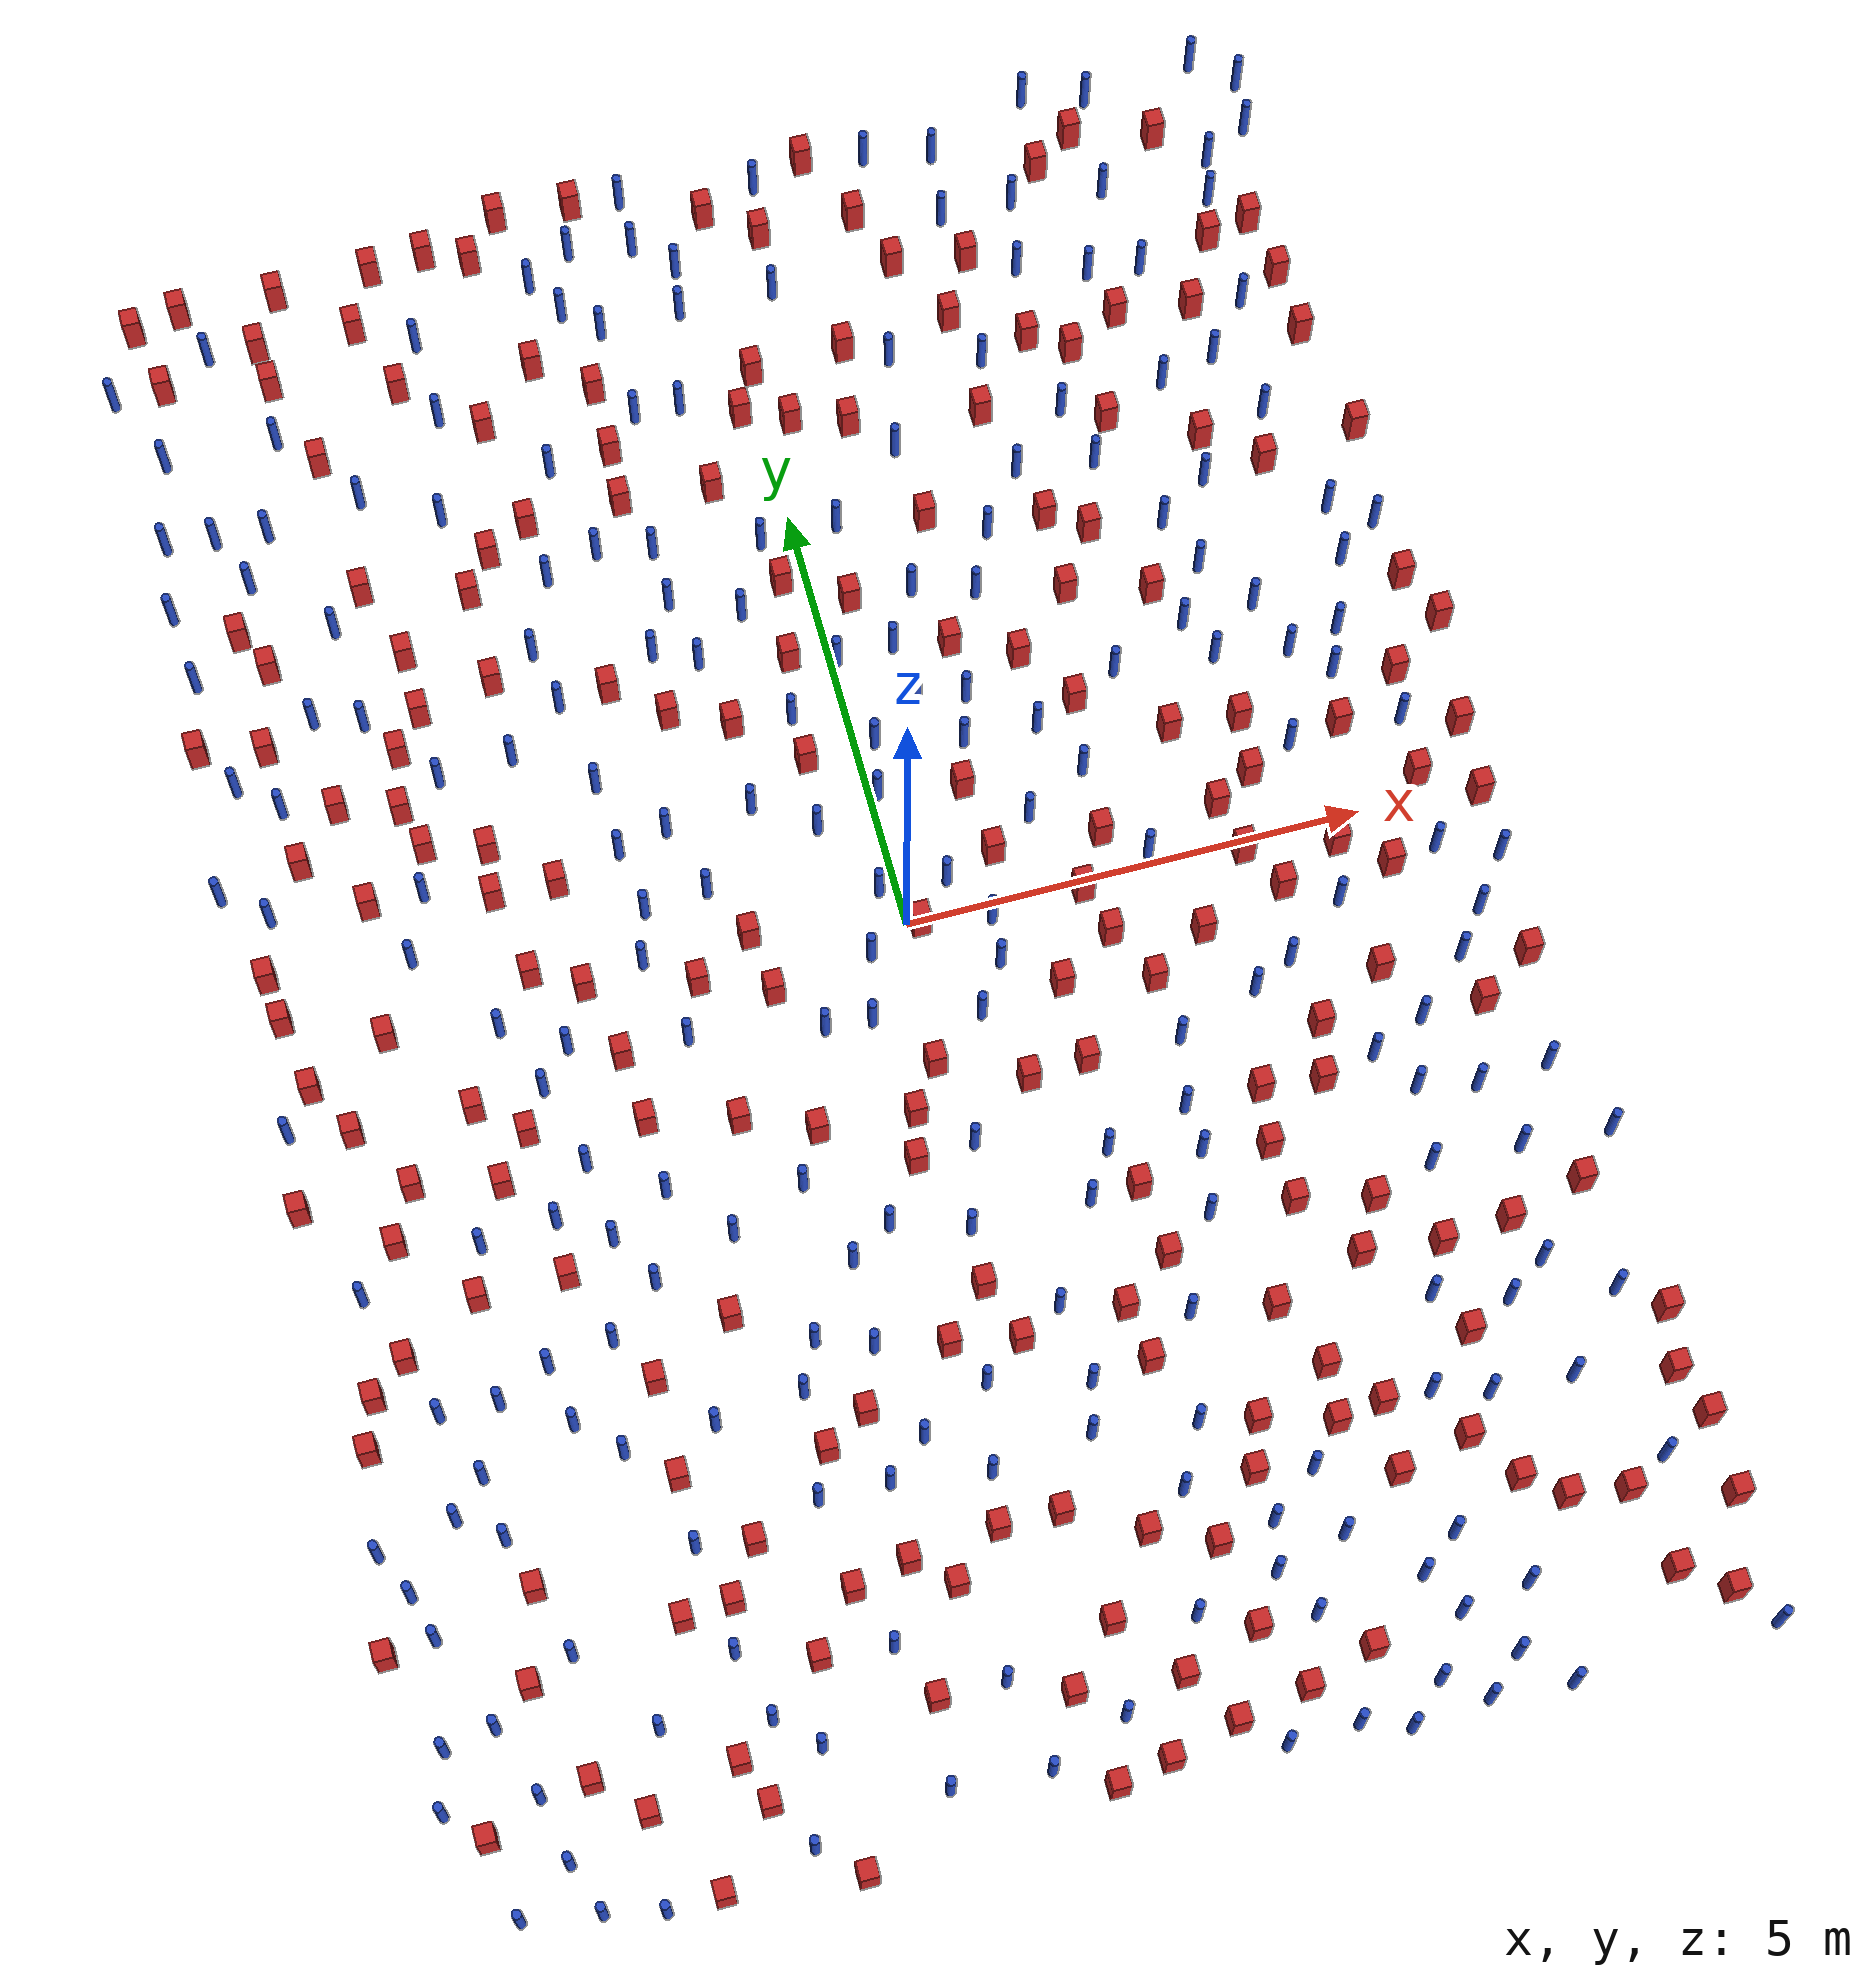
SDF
<sdf version="1.6">
  <model name="dense_35"><model name="square_post_obstacle0">
  <static>true</static>
  <pose frame="">-0.82526668302 -6.51616608075 -6.11067671241e-07 -5.50515727128e-06 -8.79689657224e-07 2.37013304536e-05</pose>
  <link name="link">
    <pose frame="">0 0 0.25 0 -0 0</pose>
    <inertial>
      <mass>100</mass>
      <inertia>
        <ixx>0.166667</ixx>
        <ixy>0</ixy>
        <ixz>0</ixz>
        <iyy>0.166667</iyy>
        <iyz>0</iyz>
        <izz>0.166667</izz>
      </inertia>
    </inertial>
    <collision name="collision">
      <geometry>
        <box>
          <size>.2 .2 .5</size>
        </box>
      </geometry>
      <max_contacts>10</max_contacts>
      <surface>
        <contact>
          <ode/>
        </contact>
        <bounce/>
        <friction>
          <torsional>
            <ode/>
          </torsional>
          <ode/>
        </friction>
      </surface>
    </collision>
    <visual name="visual">
      <geometry>
        <box>
          <size>.2 .2 .5</size>
        </box>
      </geometry>
      <material>
        <script>
          <name>Gazebo/Red</name>
          <uri>file://media/materials/scripts/gazebo.material</uri>
        </script>
      </material>
    </visual>
    <self_collide>0</self_collide>
    <kinematic>0</kinematic>
  </link>
</model>
<model name="square_post_obstacle1">
  <static>true</static>
  <pose frame="">-3.88129026402 -8.10131694386 -6.11067671241e-07 -5.50515727128e-06 -8.79689657224e-07 2.37013304536e-05</pose>
  <link name="link">
    <pose frame="">0 0 0.25 0 -0 0</pose>
    <inertial>
      <mass>100</mass>
      <inertia>
        <ixx>0.166667</ixx>
        <ixy>0</ixy>
        <ixz>0</ixz>
        <iyy>0.166667</iyy>
        <iyz>0</iyz>
        <izz>0.166667</izz>
      </inertia>
    </inertial>
    <collision name="collision">
      <geometry>
        <box>
          <size>.2 .2 .5</size>
        </box>
      </geometry>
      <max_contacts>10</max_contacts>
      <surface>
        <contact>
          <ode/>
        </contact>
        <bounce/>
        <friction>
          <torsional>
            <ode/>
          </torsional>
          <ode/>
        </friction>
      </surface>
    </collision>
    <visual name="visual">
      <geometry>
        <box>
          <size>.2 .2 .5</size>
        </box>
      </geometry>
      <material>
        <script>
          <name>Gazebo/Red</name>
          <uri>file://media/materials/scripts/gazebo.material</uri>
        </script>
      </material>
    </visual>
    <self_collide>0</self_collide>
    <kinematic>0</kinematic>
  </link>
</model>
<model name="pole_obstacle0">
  <static>true</static>
  <pose frame="">3.42519751662 4.76027807811 -9.47619616065e-06 5.49618799738e-07 2.3631041406e-07 -1.55090534801e-07</pose>
  <link name="link">
  <pose frame="">0 0 0.3 0 -0 0</pose>
    <inertial>
      <mass>1</mass>
      <inertia>
        <ixx>0.145833</ixx>
        <ixy>0</ixy>
        <ixz>0</ixz>
        <iyy>0.145833</iyy>
        <iyz>0</iyz>
        <izz>0.125</izz>
      </inertia>
    </inertial>
    <collision name="collision">
      <geometry>
        <cylinder>
          <radius>0.05</radius>
          <length>.6</length>
        </cylinder>
      </geometry>
      <max_contacts>10</max_contacts>
      <surface>
        <contact>
          <ode/>
        </contact>
        <bounce/>
        <friction>
          <torsional>
            <ode/>
          </torsional>
          <ode/>
        </friction>
      </surface>
    </collision>
    <visual name="visual">
      <geometry>
        <cylinder>
          <radius>0.05</radius>
          <length>.6</length>
        </cylinder>
      </geometry>
      <material>
        <script>
          <name>Gazebo/Blue</name>
          <uri>file://media/materials/scripts/gazebo.material</uri>
        </script>
      </material>
    </visual>
    <self_collide>0</self_collide>
    <kinematic>0</kinematic>
  </link>
</model>
<model name="square_post_obstacle2">
  <static>true</static>
  <pose frame="">4.30037438824 8.85950573954 -6.11067671241e-07 -5.50515727128e-06 -8.79689657224e-07 2.37013304536e-05</pose>
  <link name="link">
    <pose frame="">0 0 0.25 0 -0 0</pose>
    <inertial>
      <mass>100</mass>
      <inertia>
        <ixx>0.166667</ixx>
        <ixy>0</ixy>
        <ixz>0</ixz>
        <iyy>0.166667</iyy>
        <iyz>0</iyz>
        <izz>0.166667</izz>
      </inertia>
    </inertial>
    <collision name="collision">
      <geometry>
        <box>
          <size>.2 .2 .5</size>
        </box>
      </geometry>
      <max_contacts>10</max_contacts>
      <surface>
        <contact>
          <ode/>
        </contact>
        <bounce/>
        <friction>
          <torsional>
            <ode/>
          </torsional>
          <ode/>
        </friction>
      </surface>
    </collision>
    <visual name="visual">
      <geometry>
        <box>
          <size>.2 .2 .5</size>
        </box>
      </geometry>
      <material>
        <script>
          <name>Gazebo/Red</name>
          <uri>file://media/materials/scripts/gazebo.material</uri>
        </script>
      </material>
    </visual>
    <self_collide>0</self_collide>
    <kinematic>0</kinematic>
  </link>
</model>
<model name="pole_obstacle1">
  <static>true</static>
  <pose frame="">-1.56777088744 8.84587682471 -9.47619616065e-06 5.49618799737e-07 2.36310414046e-07 -1.55090534809e-07</pose>
  <link name="link">
  <pose frame="">0 0 0.3 0 -0 0</pose>
    <inertial>
      <mass>1</mass>
      <inertia>
        <ixx>0.145833</ixx>
        <ixy>0</ixy>
        <ixz>0</ixz>
        <iyy>0.145833</iyy>
        <iyz>0</iyz>
        <izz>0.125</izz>
      </inertia>
    </inertial>
    <collision name="collision">
      <geometry>
        <cylinder>
          <radius>0.05</radius>
          <length>.6</length>
        </cylinder>
      </geometry>
      <max_contacts>10</max_contacts>
      <surface>
        <contact>
          <ode/>
        </contact>
        <bounce/>
        <friction>
          <torsional>
            <ode/>
          </torsional>
          <ode/>
        </friction>
      </surface>
    </collision>
    <visual name="visual">
      <geometry>
        <cylinder>
          <radius>0.05</radius>
          <length>.6</length>
        </cylinder>
      </geometry>
      <material>
        <script>
          <name>Gazebo/Blue</name>
          <uri>file://media/materials/scripts/gazebo.material</uri>
        </script>
      </material>
    </visual>
    <self_collide>0</self_collide>
    <kinematic>0</kinematic>
  </link>
</model>
<model name="square_post_obstacle3">
  <static>true</static>
  <pose frame="">5.93491693929 -4.56497849383 -6.11067671241e-07 -5.50515727128e-06 -8.79689657224e-07 2.37013304536e-05</pose>
  <link name="link">
    <pose frame="">0 0 0.25 0 -0 0</pose>
    <inertial>
      <mass>100</mass>
      <inertia>
        <ixx>0.166667</ixx>
        <ixy>0</ixy>
        <ixz>0</ixz>
        <iyy>0.166667</iyy>
        <iyz>0</iyz>
        <izz>0.166667</izz>
      </inertia>
    </inertial>
    <collision name="collision">
      <geometry>
        <box>
          <size>.2 .2 .5</size>
        </box>
      </geometry>
      <max_contacts>10</max_contacts>
      <surface>
        <contact>
          <ode/>
        </contact>
        <bounce/>
        <friction>
          <torsional>
            <ode/>
          </torsional>
          <ode/>
        </friction>
      </surface>
    </collision>
    <visual name="visual">
      <geometry>
        <box>
          <size>.2 .2 .5</size>
        </box>
      </geometry>
      <material>
        <script>
          <name>Gazebo/Red</name>
          <uri>file://media/materials/scripts/gazebo.material</uri>
        </script>
      </material>
    </visual>
    <self_collide>0</self_collide>
    <kinematic>0</kinematic>
  </link>
</model>
<model name="pole_obstacle2">
  <static>true</static>
  <pose frame="">-1.79186777275 -2.53418552807 -9.47619616065e-06 5.49618799737e-07 2.36310414062e-07 -1.55090534798e-07</pose>
  <link name="link">
  <pose frame="">0 0 0.3 0 -0 0</pose>
    <inertial>
      <mass>1</mass>
      <inertia>
        <ixx>0.145833</ixx>
        <ixy>0</ixy>
        <ixz>0</ixz>
        <iyy>0.145833</iyy>
        <iyz>0</iyz>
        <izz>0.125</izz>
      </inertia>
    </inertial>
    <collision name="collision">
      <geometry>
        <cylinder>
          <radius>0.05</radius>
          <length>.6</length>
        </cylinder>
      </geometry>
      <max_contacts>10</max_contacts>
      <surface>
        <contact>
          <ode/>
        </contact>
        <bounce/>
        <friction>
          <torsional>
            <ode/>
          </torsional>
          <ode/>
        </friction>
      </surface>
    </collision>
    <visual name="visual">
      <geometry>
        <cylinder>
          <radius>0.05</radius>
          <length>.6</length>
        </cylinder>
      </geometry>
      <material>
        <script>
          <name>Gazebo/Blue</name>
          <uri>file://media/materials/scripts/gazebo.material</uri>
        </script>
      </material>
    </visual>
    <self_collide>0</self_collide>
    <kinematic>0</kinematic>
  </link>
</model>
<model name="pole_obstacle3">
  <static>true</static>
  <pose frame="">-6.52083156453 3.32659429473 -9.47619616065e-06 5.49618799738e-07 2.36310414051e-07 -1.55090534805e-07</pose>
  <link name="link">
  <pose frame="">0 0 0.3 0 -0 0</pose>
    <inertial>
      <mass>1</mass>
      <inertia>
        <ixx>0.145833</ixx>
        <ixy>0</ixy>
        <ixz>0</ixz>
        <iyy>0.145833</iyy>
        <iyz>0</iyz>
        <izz>0.125</izz>
      </inertia>
    </inertial>
    <collision name="collision">
      <geometry>
        <cylinder>
          <radius>0.05</radius>
          <length>.6</length>
        </cylinder>
      </geometry>
      <max_contacts>10</max_contacts>
      <surface>
        <contact>
          <ode/>
        </contact>
        <bounce/>
        <friction>
          <torsional>
            <ode/>
          </torsional>
          <ode/>
        </friction>
      </surface>
    </collision>
    <visual name="visual">
      <geometry>
        <cylinder>
          <radius>0.05</radius>
          <length>.6</length>
        </cylinder>
      </geometry>
      <material>
        <script>
          <name>Gazebo/Blue</name>
          <uri>file://media/materials/scripts/gazebo.material</uri>
        </script>
      </material>
    </visual>
    <self_collide>0</self_collide>
    <kinematic>0</kinematic>
  </link>
</model>
<model name="square_post_obstacle4">
  <static>true</static>
  <pose frame="">-5.20350773241 8.5334468349 -6.11067671241e-07 -5.50515727128e-06 -8.79689657224e-07 2.37013304536e-05</pose>
  <link name="link">
    <pose frame="">0 0 0.25 0 -0 0</pose>
    <inertial>
      <mass>100</mass>
      <inertia>
        <ixx>0.166667</ixx>
        <ixy>0</ixy>
        <ixz>0</ixz>
        <iyy>0.166667</iyy>
        <iyz>0</iyz>
        <izz>0.166667</izz>
      </inertia>
    </inertial>
    <collision name="collision">
      <geometry>
        <box>
          <size>.2 .2 .5</size>
        </box>
      </geometry>
      <max_contacts>10</max_contacts>
      <surface>
        <contact>
          <ode/>
        </contact>
        <bounce/>
        <friction>
          <torsional>
            <ode/>
          </torsional>
          <ode/>
        </friction>
      </surface>
    </collision>
    <visual name="visual">
      <geometry>
        <box>
          <size>.2 .2 .5</size>
        </box>
      </geometry>
      <material>
        <script>
          <name>Gazebo/Red</name>
          <uri>file://media/materials/scripts/gazebo.material</uri>
        </script>
      </material>
    </visual>
    <self_collide>0</self_collide>
    <kinematic>0</kinematic>
  </link>
</model>
<model name="square_post_obstacle5">
  <static>true</static>
  <pose frame="">1.39741543957 -1.98216224227 -6.11067671241e-07 -5.50515727128e-06 -8.79689657224e-07 2.37013304536e-05</pose>
  <link name="link">
    <pose frame="">0 0 0.25 0 -0 0</pose>
    <inertial>
      <mass>100</mass>
      <inertia>
        <ixx>0.166667</ixx>
        <ixy>0</ixy>
        <ixz>0</ixz>
        <iyy>0.166667</iyy>
        <iyz>0</iyz>
        <izz>0.166667</izz>
      </inertia>
    </inertial>
    <collision name="collision">
      <geometry>
        <box>
          <size>.2 .2 .5</size>
        </box>
      </geometry>
      <max_contacts>10</max_contacts>
      <surface>
        <contact>
          <ode/>
        </contact>
        <bounce/>
        <friction>
          <torsional>
            <ode/>
          </torsional>
          <ode/>
        </friction>
      </surface>
    </collision>
    <visual name="visual">
      <geometry>
        <box>
          <size>.2 .2 .5</size>
        </box>
      </geometry>
      <material>
        <script>
          <name>Gazebo/Red</name>
          <uri>file://media/materials/scripts/gazebo.material</uri>
        </script>
      </material>
    </visual>
    <self_collide>0</self_collide>
    <kinematic>0</kinematic>
  </link>
</model>
<model name="square_post_obstacle6">
  <static>true</static>
  <pose frame="">-5.98116793809 -2.09496656368 -6.11067671241e-07 -5.50515727128e-06 -8.79689657224e-07 2.37013304536e-05</pose>
  <link name="link">
    <pose frame="">0 0 0.25 0 -0 0</pose>
    <inertial>
      <mass>100</mass>
      <inertia>
        <ixx>0.166667</ixx>
        <ixy>0</ixy>
        <ixz>0</ixz>
        <iyy>0.166667</iyy>
        <iyz>0</iyz>
        <izz>0.166667</izz>
      </inertia>
    </inertial>
    <collision name="collision">
      <geometry>
        <box>
          <size>.2 .2 .5</size>
        </box>
      </geometry>
      <max_contacts>10</max_contacts>
      <surface>
        <contact>
          <ode/>
        </contact>
        <bounce/>
        <friction>
          <torsional>
            <ode/>
          </torsional>
          <ode/>
        </friction>
      </surface>
    </collision>
    <visual name="visual">
      <geometry>
        <box>
          <size>.2 .2 .5</size>
        </box>
      </geometry>
      <material>
        <script>
          <name>Gazebo/Red</name>
          <uri>file://media/materials/scripts/gazebo.material</uri>
        </script>
      </material>
    </visual>
    <self_collide>0</self_collide>
    <kinematic>0</kinematic>
  </link>
</model>
<model name="pole_obstacle4">
  <static>true</static>
  <pose frame="">-6.0200246371 -5.04161981191 -9.47619616065e-06 5.49618799737e-07 2.36310414037e-07 -1.55090534814e-07</pose>
  <link name="link">
  <pose frame="">0 0 0.3 0 -0 0</pose>
    <inertial>
      <mass>1</mass>
      <inertia>
        <ixx>0.145833</ixx>
        <ixy>0</ixy>
        <ixz>0</ixz>
        <iyy>0.145833</iyy>
        <iyz>0</iyz>
        <izz>0.125</izz>
      </inertia>
    </inertial>
    <collision name="collision">
      <geometry>
        <cylinder>
          <radius>0.05</radius>
          <length>.6</length>
        </cylinder>
      </geometry>
      <max_contacts>10</max_contacts>
      <surface>
        <contact>
          <ode/>
        </contact>
        <bounce/>
        <friction>
          <torsional>
            <ode/>
          </torsional>
          <ode/>
        </friction>
      </surface>
    </collision>
    <visual name="visual">
      <geometry>
        <cylinder>
          <radius>0.05</radius>
          <length>.6</length>
        </cylinder>
      </geometry>
      <material>
        <script>
          <name>Gazebo/Blue</name>
          <uri>file://media/materials/scripts/gazebo.material</uri>
        </script>
      </material>
    </visual>
    <self_collide>0</self_collide>
    <kinematic>0</kinematic>
  </link>
</model>
<model name="pole_obstacle5">
  <static>true</static>
  <pose frame="">2.40981222985 -1.99631648848 -9.47619616065e-06 5.49618799737e-07 2.36310414067e-07 -1.55090534796e-07</pose>
  <link name="link">
  <pose frame="">0 0 0.3 0 -0 0</pose>
    <inertial>
      <mass>1</mass>
      <inertia>
        <ixx>0.145833</ixx>
        <ixy>0</ixy>
        <ixz>0</ixz>
        <iyy>0.145833</iyy>
        <iyz>0</iyz>
        <izz>0.125</izz>
      </inertia>
    </inertial>
    <collision name="collision">
      <geometry>
        <cylinder>
          <radius>0.05</radius>
          <length>.6</length>
        </cylinder>
      </geometry>
      <max_contacts>10</max_contacts>
      <surface>
        <contact>
          <ode/>
        </contact>
        <bounce/>
        <friction>
          <torsional>
            <ode/>
          </torsional>
          <ode/>
        </friction>
      </surface>
    </collision>
    <visual name="visual">
      <geometry>
        <cylinder>
          <radius>0.05</radius>
          <length>.6</length>
        </cylinder>
      </geometry>
      <material>
        <script>
          <name>Gazebo/Blue</name>
          <uri>file://media/materials/scripts/gazebo.material</uri>
        </script>
      </material>
    </visual>
    <self_collide>0</self_collide>
    <kinematic>0</kinematic>
  </link>
</model>
<model name="square_post_obstacle7">
  <static>true</static>
  <pose frame="">3.2556750321 -6.27537954288 -6.11067671241e-07 -5.50515727128e-06 -8.79689657224e-07 2.37013304536e-05</pose>
  <link name="link">
    <pose frame="">0 0 0.25 0 -0 0</pose>
    <inertial>
      <mass>100</mass>
      <inertia>
        <ixx>0.166667</ixx>
        <ixy>0</ixy>
        <ixz>0</ixz>
        <iyy>0.166667</iyy>
        <iyz>0</iyz>
        <izz>0.166667</izz>
      </inertia>
    </inertial>
    <collision name="collision">
      <geometry>
        <box>
          <size>.2 .2 .5</size>
        </box>
      </geometry>
      <max_contacts>10</max_contacts>
      <surface>
        <contact>
          <ode/>
        </contact>
        <bounce/>
        <friction>
          <torsional>
            <ode/>
          </torsional>
          <ode/>
        </friction>
      </surface>
    </collision>
    <visual name="visual">
      <geometry>
        <box>
          <size>.2 .2 .5</size>
        </box>
      </geometry>
      <material>
        <script>
          <name>Gazebo/Red</name>
          <uri>file://media/materials/scripts/gazebo.material</uri>
        </script>
      </material>
    </visual>
    <self_collide>0</self_collide>
    <kinematic>0</kinematic>
  </link>
</model>
<model name="square_post_obstacle8">
  <static>true</static>
  <pose frame="">3.69870335096 -2.82734177414 -6.11067671241e-07 -5.50515727128e-06 -8.79689657224e-07 2.37013304536e-05</pose>
  <link name="link">
    <pose frame="">0 0 0.25 0 -0 0</pose>
    <inertial>
      <mass>100</mass>
      <inertia>
        <ixx>0.166667</ixx>
        <ixy>0</ixy>
        <ixz>0</ixz>
        <iyy>0.166667</iyy>
        <iyz>0</iyz>
        <izz>0.166667</izz>
      </inertia>
    </inertial>
    <collision name="collision">
      <geometry>
        <box>
          <size>.2 .2 .5</size>
        </box>
      </geometry>
      <max_contacts>10</max_contacts>
      <surface>
        <contact>
          <ode/>
        </contact>
        <bounce/>
        <friction>
          <torsional>
            <ode/>
          </torsional>
          <ode/>
        </friction>
      </surface>
    </collision>
    <visual name="visual">
      <geometry>
        <box>
          <size>.2 .2 .5</size>
        </box>
      </geometry>
      <material>
        <script>
          <name>Gazebo/Red</name>
          <uri>file://media/materials/scripts/gazebo.material</uri>
        </script>
      </material>
    </visual>
    <self_collide>0</self_collide>
    <kinematic>0</kinematic>
  </link>
</model>
<model name="pole_obstacle6">
  <static>true</static>
  <pose frame="">0.389493919441 -4.4717487802 -9.47619616065e-06 5.49618799737e-07 2.36310414065e-07 -1.55090534796e-07</pose>
  <link name="link">
  <pose frame="">0 0 0.3 0 -0 0</pose>
    <inertial>
      <mass>1</mass>
      <inertia>
        <ixx>0.145833</ixx>
        <ixy>0</ixy>
        <ixz>0</ixz>
        <iyy>0.145833</iyy>
        <iyz>0</iyz>
        <izz>0.125</izz>
      </inertia>
    </inertial>
    <collision name="collision">
      <geometry>
        <cylinder>
          <radius>0.05</radius>
          <length>.6</length>
        </cylinder>
      </geometry>
      <max_contacts>10</max_contacts>
      <surface>
        <contact>
          <ode/>
        </contact>
        <bounce/>
        <friction>
          <torsional>
            <ode/>
          </torsional>
          <ode/>
        </friction>
      </surface>
    </collision>
    <visual name="visual">
      <geometry>
        <cylinder>
          <radius>0.05</radius>
          <length>.6</length>
        </cylinder>
      </geometry>
      <material>
        <script>
          <name>Gazebo/Blue</name>
          <uri>file://media/materials/scripts/gazebo.material</uri>
        </script>
      </material>
    </visual>
    <self_collide>0</self_collide>
    <kinematic>0</kinematic>
  </link>
</model>
<model name="pole_obstacle7">
  <static>true</static>
  <pose frame="">2.56446868033 4.87630658331 -9.47619616065e-06 5.49618799738e-07 2.3631041406e-07 -1.55090534801e-07</pose>
  <link name="link">
  <pose frame="">0 0 0.3 0 -0 0</pose>
    <inertial>
      <mass>1</mass>
      <inertia>
        <ixx>0.145833</ixx>
        <ixy>0</ixy>
        <ixz>0</ixz>
        <iyy>0.145833</iyy>
        <iyz>0</iyz>
        <izz>0.125</izz>
      </inertia>
    </inertial>
    <collision name="collision">
      <geometry>
        <cylinder>
          <radius>0.05</radius>
          <length>.6</length>
        </cylinder>
      </geometry>
      <max_contacts>10</max_contacts>
      <surface>
        <contact>
          <ode/>
        </contact>
        <bounce/>
        <friction>
          <torsional>
            <ode/>
          </torsional>
          <ode/>
        </friction>
      </surface>
    </collision>
    <visual name="visual">
      <geometry>
        <cylinder>
          <radius>0.05</radius>
          <length>.6</length>
        </cylinder>
      </geometry>
      <material>
        <script>
          <name>Gazebo/Blue</name>
          <uri>file://media/materials/scripts/gazebo.material</uri>
        </script>
      </material>
    </visual>
    <self_collide>0</self_collide>
    <kinematic>0</kinematic>
  </link>
</model>
<model name="square_post_obstacle9">
  <static>true</static>
  <pose frame="">-2.26329625122 9.47919914897 -6.11067671241e-07 -5.50515727128e-06 -8.79689657224e-07 2.37013304536e-05</pose>
  <link name="link">
    <pose frame="">0 0 0.25 0 -0 0</pose>
    <inertial>
      <mass>100</mass>
      <inertia>
        <ixx>0.166667</ixx>
        <ixy>0</ixy>
        <ixz>0</ixz>
        <iyy>0.166667</iyy>
        <iyz>0</iyz>
        <izz>0.166667</izz>
      </inertia>
    </inertial>
    <collision name="collision">
      <geometry>
        <box>
          <size>.2 .2 .5</size>
        </box>
      </geometry>
      <max_contacts>10</max_contacts>
      <surface>
        <contact>
          <ode/>
        </contact>
        <bounce/>
        <friction>
          <torsional>
            <ode/>
          </torsional>
          <ode/>
        </friction>
      </surface>
    </collision>
    <visual name="visual">
      <geometry>
        <box>
          <size>.2 .2 .5</size>
        </box>
      </geometry>
      <material>
        <script>
          <name>Gazebo/Red</name>
          <uri>file://media/materials/scripts/gazebo.material</uri>
        </script>
      </material>
    </visual>
    <self_collide>0</self_collide>
    <kinematic>0</kinematic>
  </link>
</model>
<model name="square_post_obstacle10">
  <static>true</static>
  <pose frame="">6.32868239896 -6.0934810829 -6.11067671241e-07 -5.50515727128e-06 -8.79689657224e-07 2.37013304536e-05</pose>
  <link name="link">
    <pose frame="">0 0 0.25 0 -0 0</pose>
    <inertial>
      <mass>100</mass>
      <inertia>
        <ixx>0.166667</ixx>
        <ixy>0</ixy>
        <ixz>0</ixz>
        <iyy>0.166667</iyy>
        <iyz>0</iyz>
        <izz>0.166667</izz>
      </inertia>
    </inertial>
    <collision name="collision">
      <geometry>
        <box>
          <size>.2 .2 .5</size>
        </box>
      </geometry>
      <max_contacts>10</max_contacts>
      <surface>
        <contact>
          <ode/>
        </contact>
        <bounce/>
        <friction>
          <torsional>
            <ode/>
          </torsional>
          <ode/>
        </friction>
      </surface>
    </collision>
    <visual name="visual">
      <geometry>
        <box>
          <size>.2 .2 .5</size>
        </box>
      </geometry>
      <material>
        <script>
          <name>Gazebo/Red</name>
          <uri>file://media/materials/scripts/gazebo.material</uri>
        </script>
      </material>
    </visual>
    <self_collide>0</self_collide>
    <kinematic>0</kinematic>
  </link>
</model>
<model name="square_post_obstacle11">
  <static>true</static>
  <pose frame="">2.37454379669 5.67371568541 -6.11067671241e-07 -5.50515727128e-06 -8.79689657224e-07 2.37013304536e-05</pose>
  <link name="link">
    <pose frame="">0 0 0.25 0 -0 0</pose>
    <inertial>
      <mass>100</mass>
      <inertia>
        <ixx>0.166667</ixx>
        <ixy>0</ixy>
        <ixz>0</ixz>
        <iyy>0.166667</iyy>
        <iyz>0</iyz>
        <izz>0.166667</izz>
      </inertia>
    </inertial>
    <collision name="collision">
      <geometry>
        <box>
          <size>.2 .2 .5</size>
        </box>
      </geometry>
      <max_contacts>10</max_contacts>
      <surface>
        <contact>
          <ode/>
        </contact>
        <bounce/>
        <friction>
          <torsional>
            <ode/>
          </torsional>
          <ode/>
        </friction>
      </surface>
    </collision>
    <visual name="visual">
      <geometry>
        <box>
          <size>.2 .2 .5</size>
        </box>
      </geometry>
      <material>
        <script>
          <name>Gazebo/Red</name>
          <uri>file://media/materials/scripts/gazebo.material</uri>
        </script>
      </material>
    </visual>
    <self_collide>0</self_collide>
    <kinematic>0</kinematic>
  </link>
</model>
<model name="square_post_obstacle12">
  <static>true</static>
  <pose frame="">-2.37947772336 -6.74591752983 -6.11067671241e-07 -5.50515727128e-06 -8.79689657224e-07 2.37013304536e-05</pose>
  <link name="link">
    <pose frame="">0 0 0.25 0 -0 0</pose>
    <inertial>
      <mass>100</mass>
      <inertia>
        <ixx>0.166667</ixx>
        <ixy>0</ixy>
        <ixz>0</ixz>
        <iyy>0.166667</iyy>
        <iyz>0</iyz>
        <izz>0.166667</izz>
      </inertia>
    </inertial>
    <collision name="collision">
      <geometry>
        <box>
          <size>.2 .2 .5</size>
        </box>
      </geometry>
      <max_contacts>10</max_contacts>
      <surface>
        <contact>
          <ode/>
        </contact>
        <bounce/>
        <friction>
          <torsional>
            <ode/>
          </torsional>
          <ode/>
        </friction>
      </surface>
    </collision>
    <visual name="visual">
      <geometry>
        <box>
          <size>.2 .2 .5</size>
        </box>
      </geometry>
      <material>
        <script>
          <name>Gazebo/Red</name>
          <uri>file://media/materials/scripts/gazebo.material</uri>
        </script>
      </material>
    </visual>
    <self_collide>0</self_collide>
    <kinematic>0</kinematic>
  </link>
</model>
<model name="square_post_obstacle13">
  <static>true</static>
  <pose frame="">1.38367656755 -1.09471865919 -6.11067671241e-07 -5.50515727128e-06 -8.79689657224e-07 2.37013304536e-05</pose>
  <link name="link">
    <pose frame="">0 0 0.25 0 -0 0</pose>
    <inertial>
      <mass>100</mass>
      <inertia>
        <ixx>0.166667</ixx>
        <ixy>0</ixy>
        <ixz>0</ixz>
        <iyy>0.166667</iyy>
        <iyz>0</iyz>
        <izz>0.166667</izz>
      </inertia>
    </inertial>
    <collision name="collision">
      <geometry>
        <box>
          <size>.2 .2 .5</size>
        </box>
      </geometry>
      <max_contacts>10</max_contacts>
      <surface>
        <contact>
          <ode/>
        </contact>
        <bounce/>
        <friction>
          <torsional>
            <ode/>
          </torsional>
          <ode/>
        </friction>
      </surface>
    </collision>
    <visual name="visual">
      <geometry>
        <box>
          <size>.2 .2 .5</size>
        </box>
      </geometry>
      <material>
        <script>
          <name>Gazebo/Red</name>
          <uri>file://media/materials/scripts/gazebo.material</uri>
        </script>
      </material>
    </visual>
    <self_collide>0</self_collide>
    <kinematic>0</kinematic>
  </link>
</model>
<model name="pole_obstacle8">
  <static>true</static>
  <pose frame="">5.74326832337 0.918242795768 -9.47619616065e-06 5.49618799737e-07 2.36310414061e-07 -1.550905348e-07</pose>
  <link name="link">
  <pose frame="">0 0 0.3 0 -0 0</pose>
    <inertial>
      <mass>1</mass>
      <inertia>
        <ixx>0.145833</ixx>
        <ixy>0</ixy>
        <ixz>0</ixz>
        <iyy>0.145833</iyy>
        <iyz>0</iyz>
        <izz>0.125</izz>
      </inertia>
    </inertial>
    <collision name="collision">
      <geometry>
        <cylinder>
          <radius>0.05</radius>
          <length>.6</length>
        </cylinder>
      </geometry>
      <max_contacts>10</max_contacts>
      <surface>
        <contact>
          <ode/>
        </contact>
        <bounce/>
        <friction>
          <torsional>
            <ode/>
          </torsional>
          <ode/>
        </friction>
      </surface>
    </collision>
    <visual name="visual">
      <geometry>
        <cylinder>
          <radius>0.05</radius>
          <length>.6</length>
        </cylinder>
      </geometry>
      <material>
        <script>
          <name>Gazebo/Blue</name>
          <uri>file://media/materials/scripts/gazebo.material</uri>
        </script>
      </material>
    </visual>
    <self_collide>0</self_collide>
    <kinematic>0</kinematic>
  </link>
</model>
<model name="square_post_obstacle14">
  <static>true</static>
  <pose frame="">0.976466315435 1.36126009317 -6.11067671241e-07 -5.50515727128e-06 -8.79689657224e-07 2.37013304536e-05</pose>
  <link name="link">
    <pose frame="">0 0 0.25 0 -0 0</pose>
    <inertial>
      <mass>100</mass>
      <inertia>
        <ixx>0.166667</ixx>
        <ixy>0</ixy>
        <ixz>0</ixz>
        <iyy>0.166667</iyy>
        <iyz>0</iyz>
        <izz>0.166667</izz>
      </inertia>
    </inertial>
    <collision name="collision">
      <geometry>
        <box>
          <size>.2 .2 .5</size>
        </box>
      </geometry>
      <max_contacts>10</max_contacts>
      <surface>
        <contact>
          <ode/>
        </contact>
        <bounce/>
        <friction>
          <torsional>
            <ode/>
          </torsional>
          <ode/>
        </friction>
      </surface>
    </collision>
    <visual name="visual">
      <geometry>
        <box>
          <size>.2 .2 .5</size>
        </box>
      </geometry>
      <material>
        <script>
          <name>Gazebo/Red</name>
          <uri>file://media/materials/scripts/gazebo.material</uri>
        </script>
      </material>
    </visual>
    <self_collide>0</self_collide>
    <kinematic>0</kinematic>
  </link>
</model>
<model name="square_post_obstacle15">
  <static>true</static>
  <pose frame="">-2.80714113025 5.61509971107 -6.11067671241e-07 -5.50515727128e-06 -8.79689657224e-07 2.37013304536e-05</pose>
  <link name="link">
    <pose frame="">0 0 0.25 0 -0 0</pose>
    <inertial>
      <mass>100</mass>
      <inertia>
        <ixx>0.166667</ixx>
        <ixy>0</ixy>
        <ixz>0</ixz>
        <iyy>0.166667</iyy>
        <iyz>0</iyz>
        <izz>0.166667</izz>
      </inertia>
    </inertial>
    <collision name="collision">
      <geometry>
        <box>
          <size>.2 .2 .5</size>
        </box>
      </geometry>
      <max_contacts>10</max_contacts>
      <surface>
        <contact>
          <ode/>
        </contact>
        <bounce/>
        <friction>
          <torsional>
            <ode/>
          </torsional>
          <ode/>
        </friction>
      </surface>
    </collision>
    <visual name="visual">
      <geometry>
        <box>
          <size>.2 .2 .5</size>
        </box>
      </geometry>
      <material>
        <script>
          <name>Gazebo/Red</name>
          <uri>file://media/materials/scripts/gazebo.material</uri>
        </script>
      </material>
    </visual>
    <self_collide>0</self_collide>
    <kinematic>0</kinematic>
  </link>
</model>
<model name="square_post_obstacle16">
  <static>true</static>
  <pose frame="">-0.392982585008 -9.27894268601 -6.11067671241e-07 -5.50515727128e-06 -8.79689657224e-07 2.37013304536e-05</pose>
  <link name="link">
    <pose frame="">0 0 0.25 0 -0 0</pose>
    <inertial>
      <mass>100</mass>
      <inertia>
        <ixx>0.166667</ixx>
        <ixy>0</ixy>
        <ixz>0</ixz>
        <iyy>0.166667</iyy>
        <iyz>0</iyz>
        <izz>0.166667</izz>
      </inertia>
    </inertial>
    <collision name="collision">
      <geometry>
        <box>
          <size>.2 .2 .5</size>
        </box>
      </geometry>
      <max_contacts>10</max_contacts>
      <surface>
        <contact>
          <ode/>
        </contact>
        <bounce/>
        <friction>
          <torsional>
            <ode/>
          </torsional>
          <ode/>
        </friction>
      </surface>
    </collision>
    <visual name="visual">
      <geometry>
        <box>
          <size>.2 .2 .5</size>
        </box>
      </geometry>
      <material>
        <script>
          <name>Gazebo/Red</name>
          <uri>file://media/materials/scripts/gazebo.material</uri>
        </script>
      </material>
    </visual>
    <self_collide>0</self_collide>
    <kinematic>0</kinematic>
  </link>
</model>
<model name="pole_obstacle9">
  <static>true</static>
  <pose frame="">-5.14063943435 -2.33000956098 -9.47619616065e-06 5.49618799738e-07 2.36310414051e-07 -1.55090534805e-07</pose>
  <link name="link">
  <pose frame="">0 0 0.3 0 -0 0</pose>
    <inertial>
      <mass>1</mass>
      <inertia>
        <ixx>0.145833</ixx>
        <ixy>0</ixy>
        <ixz>0</ixz>
        <iyy>0.145833</iyy>
        <iyz>0</iyz>
        <izz>0.125</izz>
      </inertia>
    </inertial>
    <collision name="collision">
      <geometry>
        <cylinder>
          <radius>0.05</radius>
          <length>.6</length>
        </cylinder>
      </geometry>
      <max_contacts>10</max_contacts>
      <surface>
        <contact>
          <ode/>
        </contact>
        <bounce/>
        <friction>
          <torsional>
            <ode/>
          </torsional>
          <ode/>
        </friction>
      </surface>
    </collision>
    <visual name="visual">
      <geometry>
        <cylinder>
          <radius>0.05</radius>
          <length>.6</length>
        </cylinder>
      </geometry>
      <material>
        <script>
          <name>Gazebo/Blue</name>
          <uri>file://media/materials/scripts/gazebo.material</uri>
        </script>
      </material>
    </visual>
    <self_collide>0</self_collide>
    <kinematic>0</kinematic>
  </link>
</model>
<model name="square_post_obstacle17">
  <static>true</static>
  <pose frame="">-5.29909808792 -2.85776680964 -6.11067671241e-07 -5.50515727128e-06 -8.79689657224e-07 2.37013304536e-05</pose>
  <link name="link">
    <pose frame="">0 0 0.25 0 -0 0</pose>
    <inertial>
      <mass>100</mass>
      <inertia>
        <ixx>0.166667</ixx>
        <ixy>0</ixy>
        <ixz>0</ixz>
        <iyy>0.166667</iyy>
        <iyz>0</iyz>
        <izz>0.166667</izz>
      </inertia>
    </inertial>
    <collision name="collision">
      <geometry>
        <box>
          <size>.2 .2 .5</size>
        </box>
      </geometry>
      <max_contacts>10</max_contacts>
      <surface>
        <contact>
          <ode/>
        </contact>
        <bounce/>
        <friction>
          <torsional>
            <ode/>
          </torsional>
          <ode/>
        </friction>
      </surface>
    </collision>
    <visual name="visual">
      <geometry>
        <box>
          <size>.2 .2 .5</size>
        </box>
      </geometry>
      <material>
        <script>
          <name>Gazebo/Red</name>
          <uri>file://media/materials/scripts/gazebo.material</uri>
        </script>
      </material>
    </visual>
    <self_collide>0</self_collide>
    <kinematic>0</kinematic>
  </link>
</model>
<model name="square_post_obstacle18">
  <static>true</static>
  <pose frame="">-4.72708501513 5.27083126233 -6.11067671241e-07 -5.50515727128e-06 -8.79689657224e-07 2.37013304536e-05</pose>
  <link name="link">
    <pose frame="">0 0 0.25 0 -0 0</pose>
    <inertial>
      <mass>100</mass>
      <inertia>
        <ixx>0.166667</ixx>
        <ixy>0</ixy>
        <ixz>0</ixz>
        <iyy>0.166667</iyy>
        <iyz>0</iyz>
        <izz>0.166667</izz>
      </inertia>
    </inertial>
    <collision name="collision">
      <geometry>
        <box>
          <size>.2 .2 .5</size>
        </box>
      </geometry>
      <max_contacts>10</max_contacts>
      <surface>
        <contact>
          <ode/>
        </contact>
        <bounce/>
        <friction>
          <torsional>
            <ode/>
          </torsional>
          <ode/>
        </friction>
      </surface>
    </collision>
    <visual name="visual">
      <geometry>
        <box>
          <size>.2 .2 .5</size>
        </box>
      </geometry>
      <material>
        <script>
          <name>Gazebo/Red</name>
          <uri>file://media/materials/scripts/gazebo.material</uri>
        </script>
      </material>
    </visual>
    <self_collide>0</self_collide>
    <kinematic>0</kinematic>
  </link>
</model>
<model name="pole_obstacle10">
  <static>true</static>
  <pose frame="">4.07829547664 -5.33456093465 -9.47619616065e-06 5.49618799737e-07 2.36310414037e-07 -1.55090534814e-07</pose>
  <link name="link">
  <pose frame="">0 0 0.3 0 -0 0</pose>
    <inertial>
      <mass>1</mass>
      <inertia>
        <ixx>0.145833</ixx>
        <ixy>0</ixy>
        <ixz>0</ixz>
        <iyy>0.145833</iyy>
        <iyz>0</iyz>
        <izz>0.125</izz>
      </inertia>
    </inertial>
    <collision name="collision">
      <geometry>
        <cylinder>
          <radius>0.05</radius>
          <length>.6</length>
        </cylinder>
      </geometry>
      <max_contacts>10</max_contacts>
      <surface>
        <contact>
          <ode/>
        </contact>
        <bounce/>
        <friction>
          <torsional>
            <ode/>
          </torsional>
          <ode/>
        </friction>
      </surface>
    </collision>
    <visual name="visual">
      <geometry>
        <cylinder>
          <radius>0.05</radius>
          <length>.6</length>
        </cylinder>
      </geometry>
      <material>
        <script>
          <name>Gazebo/Blue</name>
          <uri>file://media/materials/scripts/gazebo.material</uri>
        </script>
      </material>
    </visual>
    <self_collide>0</self_collide>
    <kinematic>0</kinematic>
  </link>
</model>
<model name="square_post_obstacle19">
  <static>true</static>
  <pose frame="">-3.19186774682 -1.45683344238 -6.11067671241e-07 -5.50515727128e-06 -8.79689657224e-07 2.37013304536e-05</pose>
  <link name="link">
    <pose frame="">0 0 0.25 0 -0 0</pose>
    <inertial>
      <mass>100</mass>
      <inertia>
        <ixx>0.166667</ixx>
        <ixy>0</ixy>
        <ixz>0</ixz>
        <iyy>0.166667</iyy>
        <iyz>0</iyz>
        <izz>0.166667</izz>
      </inertia>
    </inertial>
    <collision name="collision">
      <geometry>
        <box>
          <size>.2 .2 .5</size>
        </box>
      </geometry>
      <max_contacts>10</max_contacts>
      <surface>
        <contact>
          <ode/>
        </contact>
        <bounce/>
        <friction>
          <torsional>
            <ode/>
          </torsional>
          <ode/>
        </friction>
      </surface>
    </collision>
    <visual name="visual">
      <geometry>
        <box>
          <size>.2 .2 .5</size>
        </box>
      </geometry>
      <material>
        <script>
          <name>Gazebo/Red</name>
          <uri>file://media/materials/scripts/gazebo.material</uri>
        </script>
      </material>
    </visual>
    <self_collide>0</self_collide>
    <kinematic>0</kinematic>
  </link>
</model>
<model name="pole_obstacle11">
  <static>true</static>
  <pose frame="">-3.66469496696 -7.05131863746 -9.4761961606e-06 5.49618799729e-07 2.36310414006e-07 -1.55090534822e-07</pose>
  <link name="link">
  <pose frame="">0 0 0.3 0 -0 0</pose>
    <inertial>
      <mass>1</mass>
      <inertia>
        <ixx>0.145833</ixx>
        <ixy>0</ixy>
        <ixz>0</ixz>
        <iyy>0.145833</iyy>
        <iyz>0</iyz>
        <izz>0.125</izz>
      </inertia>
    </inertial>
    <collision name="collision">
      <geometry>
        <cylinder>
          <radius>0.05</radius>
          <length>.6</length>
        </cylinder>
      </geometry>
      <max_contacts>10</max_contacts>
      <surface>
        <contact>
          <ode/>
        </contact>
        <bounce/>
        <friction>
          <torsional>
            <ode/>
          </torsional>
          <ode/>
        </friction>
      </surface>
    </collision>
    <visual name="visual">
      <geometry>
        <cylinder>
          <radius>0.05</radius>
          <length>.6</length>
        </cylinder>
      </geometry>
      <material>
        <script>
          <name>Gazebo/Blue</name>
          <uri>file://media/materials/scripts/gazebo.material</uri>
        </script>
      </material>
    </visual>
    <self_collide>0</self_collide>
    <kinematic>0</kinematic>
  </link>
</model>
<model name="square_post_obstacle20">
  <static>true</static>
  <pose frame="">-4.10968657314 8.48709137153 -6.11067671241e-07 -5.50515727128e-06 -8.79689657224e-07 2.37013304536e-05</pose>
  <link name="link">
    <pose frame="">0 0 0.25 0 -0 0</pose>
    <inertial>
      <mass>100</mass>
      <inertia>
        <ixx>0.166667</ixx>
        <ixy>0</ixy>
        <ixz>0</ixz>
        <iyy>0.166667</iyy>
        <iyz>0</iyz>
        <izz>0.166667</izz>
      </inertia>
    </inertial>
    <collision name="collision">
      <geometry>
        <box>
          <size>.2 .2 .5</size>
        </box>
      </geometry>
      <max_contacts>10</max_contacts>
      <surface>
        <contact>
          <ode/>
        </contact>
        <bounce/>
        <friction>
          <torsional>
            <ode/>
          </torsional>
          <ode/>
        </friction>
      </surface>
    </collision>
    <visual name="visual">
      <geometry>
        <box>
          <size>.2 .2 .5</size>
        </box>
      </geometry>
      <material>
        <script>
          <name>Gazebo/Red</name>
          <uri>file://media/materials/scripts/gazebo.material</uri>
        </script>
      </material>
    </visual>
    <self_collide>0</self_collide>
    <kinematic>0</kinematic>
  </link>
</model>
<model name="pole_obstacle12">
  <static>true</static>
  <pose frame="">-6.79395257668 -0.647486050733 -9.47619616065e-06 5.49618799737e-07 2.36310414061e-07 -1.550905348e-07</pose>
  <link name="link">
  <pose frame="">0 0 0.3 0 -0 0</pose>
    <inertial>
      <mass>1</mass>
      <inertia>
        <ixx>0.145833</ixx>
        <ixy>0</ixy>
        <ixz>0</ixz>
        <iyy>0.145833</iyy>
        <iyz>0</iyz>
        <izz>0.125</izz>
      </inertia>
    </inertial>
    <collision name="collision">
      <geometry>
        <cylinder>
          <radius>0.05</radius>
          <length>.6</length>
        </cylinder>
      </geometry>
      <max_contacts>10</max_contacts>
      <surface>
        <contact>
          <ode/>
        </contact>
        <bounce/>
        <friction>
          <torsional>
            <ode/>
          </torsional>
          <ode/>
        </friction>
      </surface>
    </collision>
    <visual name="visual">
      <geometry>
        <cylinder>
          <radius>0.05</radius>
          <length>.6</length>
        </cylinder>
      </geometry>
      <material>
        <script>
          <name>Gazebo/Blue</name>
          <uri>file://media/materials/scripts/gazebo.material</uri>
        </script>
      </material>
    </visual>
    <self_collide>0</self_collide>
    <kinematic>0</kinematic>
  </link>
</model>
<model name="square_post_obstacle21">
  <static>true</static>
  <pose frame="">1.37357863309 -8.14754635639 -6.11067671241e-07 -5.50515727128e-06 -8.79689657224e-07 2.37013304536e-05</pose>
  <link name="link">
    <pose frame="">0 0 0.25 0 -0 0</pose>
    <inertial>
      <mass>100</mass>
      <inertia>
        <ixx>0.166667</ixx>
        <ixy>0</ixy>
        <ixz>0</ixz>
        <iyy>0.166667</iyy>
        <iyz>0</iyz>
        <izz>0.166667</izz>
      </inertia>
    </inertial>
    <collision name="collision">
      <geometry>
        <box>
          <size>.2 .2 .5</size>
        </box>
      </geometry>
      <max_contacts>10</max_contacts>
      <surface>
        <contact>
          <ode/>
        </contact>
        <bounce/>
        <friction>
          <torsional>
            <ode/>
          </torsional>
          <ode/>
        </friction>
      </surface>
    </collision>
    <visual name="visual">
      <geometry>
        <box>
          <size>.2 .2 .5</size>
        </box>
      </geometry>
      <material>
        <script>
          <name>Gazebo/Red</name>
          <uri>file://media/materials/scripts/gazebo.material</uri>
        </script>
      </material>
    </visual>
    <self_collide>0</self_collide>
    <kinematic>0</kinematic>
  </link>
</model>
<model name="pole_obstacle13">
  <static>true</static>
  <pose frame="">2.92305511422 2.25661610833 -9.47619616065e-06 5.49618799737e-07 2.36310414051e-07 -1.55090534807e-07</pose>
  <link name="link">
  <pose frame="">0 0 0.3 0 -0 0</pose>
    <inertial>
      <mass>1</mass>
      <inertia>
        <ixx>0.145833</ixx>
        <ixy>0</ixy>
        <ixz>0</ixz>
        <iyy>0.145833</iyy>
        <iyz>0</iyz>
        <izz>0.125</izz>
      </inertia>
    </inertial>
    <collision name="collision">
      <geometry>
        <cylinder>
          <radius>0.05</radius>
          <length>.6</length>
        </cylinder>
      </geometry>
      <max_contacts>10</max_contacts>
      <surface>
        <contact>
          <ode/>
        </contact>
        <bounce/>
        <friction>
          <torsional>
            <ode/>
          </torsional>
          <ode/>
        </friction>
      </surface>
    </collision>
    <visual name="visual">
      <geometry>
        <cylinder>
          <radius>0.05</radius>
          <length>.6</length>
        </cylinder>
      </geometry>
      <material>
        <script>
          <name>Gazebo/Blue</name>
          <uri>file://media/materials/scripts/gazebo.material</uri>
        </script>
      </material>
    </visual>
    <self_collide>0</self_collide>
    <kinematic>0</kinematic>
  </link>
</model>
<model name="square_post_obstacle22">
  <static>true</static>
  <pose frame="">1.98280074406 -6.12882178405 -6.11067671241e-07 -5.50515727128e-06 -8.79689657224e-07 2.37013304536e-05</pose>
  <link name="link">
    <pose frame="">0 0 0.25 0 -0 0</pose>
    <inertial>
      <mass>100</mass>
      <inertia>
        <ixx>0.166667</ixx>
        <ixy>0</ixy>
        <ixz>0</ixz>
        <iyy>0.166667</iyy>
        <iyz>0</iyz>
        <izz>0.166667</izz>
      </inertia>
    </inertial>
    <collision name="collision">
      <geometry>
        <box>
          <size>.2 .2 .5</size>
        </box>
      </geometry>
      <max_contacts>10</max_contacts>
      <surface>
        <contact>
          <ode/>
        </contact>
        <bounce/>
        <friction>
          <torsional>
            <ode/>
          </torsional>
          <ode/>
        </friction>
      </surface>
    </collision>
    <visual name="visual">
      <geometry>
        <box>
          <size>.2 .2 .5</size>
        </box>
      </geometry>
      <material>
        <script>
          <name>Gazebo/Red</name>
          <uri>file://media/materials/scripts/gazebo.material</uri>
        </script>
      </material>
    </visual>
    <self_collide>0</self_collide>
    <kinematic>0</kinematic>
  </link>
</model>
<model name="pole_obstacle14">
  <static>true</static>
  <pose frame="">4.50683126189 -3.98978135572 -9.47619616065e-06 5.49618799737e-07 2.36310414056e-07 -1.55090534802e-07</pose>
  <link name="link">
  <pose frame="">0 0 0.3 0 -0 0</pose>
    <inertial>
      <mass>1</mass>
      <inertia>
        <ixx>0.145833</ixx>
        <ixy>0</ixy>
        <ixz>0</ixz>
        <iyy>0.145833</iyy>
        <iyz>0</iyz>
        <izz>0.125</izz>
      </inertia>
    </inertial>
    <collision name="collision">
      <geometry>
        <cylinder>
          <radius>0.05</radius>
          <length>.6</length>
        </cylinder>
      </geometry>
      <max_contacts>10</max_contacts>
      <surface>
        <contact>
          <ode/>
        </contact>
        <bounce/>
        <friction>
          <torsional>
            <ode/>
          </torsional>
          <ode/>
        </friction>
      </surface>
    </collision>
    <visual name="visual">
      <geometry>
        <cylinder>
          <radius>0.05</radius>
          <length>.6</length>
        </cylinder>
      </geometry>
      <material>
        <script>
          <name>Gazebo/Blue</name>
          <uri>file://media/materials/scripts/gazebo.material</uri>
        </script>
      </material>
    </visual>
    <self_collide>0</self_collide>
    <kinematic>0</kinematic>
  </link>
</model>
<model name="pole_obstacle15">
  <static>true</static>
  <pose frame="">1.73410881993 3.55879253079 -9.47619616065e-06 5.49618799737e-07 2.36310414062e-07 -1.55090534798e-07</pose>
  <link name="link">
  <pose frame="">0 0 0.3 0 -0 0</pose>
    <inertial>
      <mass>1</mass>
      <inertia>
        <ixx>0.145833</ixx>
        <ixy>0</ixy>
        <ixz>0</ixz>
        <iyy>0.145833</iyy>
        <iyz>0</iyz>
        <izz>0.125</izz>
      </inertia>
    </inertial>
    <collision name="collision">
      <geometry>
        <cylinder>
          <radius>0.05</radius>
          <length>.6</length>
        </cylinder>
      </geometry>
      <max_contacts>10</max_contacts>
      <surface>
        <contact>
          <ode/>
        </contact>
        <bounce/>
        <friction>
          <torsional>
            <ode/>
          </torsional>
          <ode/>
        </friction>
      </surface>
    </collision>
    <visual name="visual">
      <geometry>
        <cylinder>
          <radius>0.05</radius>
          <length>.6</length>
        </cylinder>
      </geometry>
      <material>
        <script>
          <name>Gazebo/Blue</name>
          <uri>file://media/materials/scripts/gazebo.material</uri>
        </script>
      </material>
    </visual>
    <self_collide>0</self_collide>
    <kinematic>0</kinematic>
  </link>
</model>
<model name="pole_obstacle16">
  <static>true</static>
  <pose frame="">-5.04046134124 3.73321766316 -9.47619616065e-06 5.49618799738e-07 2.36310414051e-07 -1.55090534805e-07</pose>
  <link name="link">
  <pose frame="">0 0 0.3 0 -0 0</pose>
    <inertial>
      <mass>1</mass>
      <inertia>
        <ixx>0.145833</ixx>
        <ixy>0</ixy>
        <ixz>0</ixz>
        <iyy>0.145833</iyy>
        <iyz>0</iyz>
        <izz>0.125</izz>
      </inertia>
    </inertial>
    <collision name="collision">
      <geometry>
        <cylinder>
          <radius>0.05</radius>
          <length>.6</length>
        </cylinder>
      </geometry>
      <max_contacts>10</max_contacts>
      <surface>
        <contact>
          <ode/>
        </contact>
        <bounce/>
        <friction>
          <torsional>
            <ode/>
          </torsional>
          <ode/>
        </friction>
      </surface>
    </collision>
    <visual name="visual">
      <geometry>
        <cylinder>
          <radius>0.05</radius>
          <length>.6</length>
        </cylinder>
      </geometry>
      <material>
        <script>
          <name>Gazebo/Blue</name>
          <uri>file://media/materials/scripts/gazebo.material</uri>
        </script>
      </material>
    </visual>
    <self_collide>0</self_collide>
    <kinematic>0</kinematic>
  </link>
</model>
<model name="square_post_obstacle23">
  <static>true</static>
  <pose frame="">3.53498907678 0.447461934969 -6.11067671241e-07 -5.50515727128e-06 -8.79689657224e-07 2.37013304536e-05</pose>
  <link name="link">
    <pose frame="">0 0 0.25 0 -0 0</pose>
    <inertial>
      <mass>100</mass>
      <inertia>
        <ixx>0.166667</ixx>
        <ixy>0</ixy>
        <ixz>0</ixz>
        <iyy>0.166667</iyy>
        <iyz>0</iyz>
        <izz>0.166667</izz>
      </inertia>
    </inertial>
    <collision name="collision">
      <geometry>
        <box>
          <size>.2 .2 .5</size>
        </box>
      </geometry>
      <max_contacts>10</max_contacts>
      <surface>
        <contact>
          <ode/>
        </contact>
        <bounce/>
        <friction>
          <torsional>
            <ode/>
          </torsional>
          <ode/>
        </friction>
      </surface>
    </collision>
    <visual name="visual">
      <geometry>
        <box>
          <size>.2 .2 .5</size>
        </box>
      </geometry>
      <material>
        <script>
          <name>Gazebo/Red</name>
          <uri>file://media/materials/scripts/gazebo.material</uri>
        </script>
      </material>
    </visual>
    <self_collide>0</self_collide>
    <kinematic>0</kinematic>
  </link>
</model>
<model name="pole_obstacle17">
  <static>true</static>
  <pose frame="">1.65598059644 -4.87979008221 -9.47619616065e-06 5.49618799737e-07 2.36310414061e-07 -1.550905348e-07</pose>
  <link name="link">
  <pose frame="">0 0 0.3 0 -0 0</pose>
    <inertial>
      <mass>1</mass>
      <inertia>
        <ixx>0.145833</ixx>
        <ixy>0</ixy>
        <ixz>0</ixz>
        <iyy>0.145833</iyy>
        <iyz>0</iyz>
        <izz>0.125</izz>
      </inertia>
    </inertial>
    <collision name="collision">
      <geometry>
        <cylinder>
          <radius>0.05</radius>
          <length>.6</length>
        </cylinder>
      </geometry>
      <max_contacts>10</max_contacts>
      <surface>
        <contact>
          <ode/>
        </contact>
        <bounce/>
        <friction>
          <torsional>
            <ode/>
          </torsional>
          <ode/>
        </friction>
      </surface>
    </collision>
    <visual name="visual">
      <geometry>
        <cylinder>
          <radius>0.05</radius>
          <length>.6</length>
        </cylinder>
      </geometry>
      <material>
        <script>
          <name>Gazebo/Blue</name>
          <uri>file://media/materials/scripts/gazebo.material</uri>
        </script>
      </material>
    </visual>
    <self_collide>0</self_collide>
    <kinematic>0</kinematic>
  </link>
</model>
<model name="square_post_obstacle24">
  <static>true</static>
  <pose frame="">2.41187831483 -8.62929557495 -6.11067671241e-07 -5.50515727128e-06 -8.79689657224e-07 2.37013304536e-05</pose>
  <link name="link">
    <pose frame="">0 0 0.25 0 -0 0</pose>
    <inertial>
      <mass>100</mass>
      <inertia>
        <ixx>0.166667</ixx>
        <ixy>0</ixy>
        <ixz>0</ixz>
        <iyy>0.166667</iyy>
        <iyz>0</iyz>
        <izz>0.166667</izz>
      </inertia>
    </inertial>
    <collision name="collision">
      <geometry>
        <box>
          <size>.2 .2 .5</size>
        </box>
      </geometry>
      <max_contacts>10</max_contacts>
      <surface>
        <contact>
          <ode/>
        </contact>
        <bounce/>
        <friction>
          <torsional>
            <ode/>
          </torsional>
          <ode/>
        </friction>
      </surface>
    </collision>
    <visual name="visual">
      <geometry>
        <box>
          <size>.2 .2 .5</size>
        </box>
      </geometry>
      <material>
        <script>
          <name>Gazebo/Red</name>
          <uri>file://media/materials/scripts/gazebo.material</uri>
        </script>
      </material>
    </visual>
    <self_collide>0</self_collide>
    <kinematic>0</kinematic>
  </link>
</model>
<model name="square_post_obstacle25">
  <static>true</static>
  <pose frame="">0.0494147492962 6.81524809905 -6.11067671241e-07 -5.50515727128e-06 -8.79689657224e-07 2.37013304536e-05</pose>
  <link name="link">
    <pose frame="">0 0 0.25 0 -0 0</pose>
    <inertial>
      <mass>100</mass>
      <inertia>
        <ixx>0.166667</ixx>
        <ixy>0</ixy>
        <ixz>0</ixz>
        <iyy>0.166667</iyy>
        <iyz>0</iyz>
        <izz>0.166667</izz>
      </inertia>
    </inertial>
    <collision name="collision">
      <geometry>
        <box>
          <size>.2 .2 .5</size>
        </box>
      </geometry>
      <max_contacts>10</max_contacts>
      <surface>
        <contact>
          <ode/>
        </contact>
        <bounce/>
        <friction>
          <torsional>
            <ode/>
          </torsional>
          <ode/>
        </friction>
      </surface>
    </collision>
    <visual name="visual">
      <geometry>
        <box>
          <size>.2 .2 .5</size>
        </box>
      </geometry>
      <material>
        <script>
          <name>Gazebo/Red</name>
          <uri>file://media/materials/scripts/gazebo.material</uri>
        </script>
      </material>
    </visual>
    <self_collide>0</self_collide>
    <kinematic>0</kinematic>
  </link>
</model>
<model name="square_post_obstacle26">
  <static>true</static>
  <pose frame="">-2.99052652677 6.90192373108 -6.11067671241e-07 -5.50515727128e-06 -8.79689657224e-07 2.37013304536e-05</pose>
  <link name="link">
    <pose frame="">0 0 0.25 0 -0 0</pose>
    <inertial>
      <mass>100</mass>
      <inertia>
        <ixx>0.166667</ixx>
        <ixy>0</ixy>
        <ixz>0</ixz>
        <iyy>0.166667</iyy>
        <iyz>0</iyz>
        <izz>0.166667</izz>
      </inertia>
    </inertial>
    <collision name="collision">
      <geometry>
        <box>
          <size>.2 .2 .5</size>
        </box>
      </geometry>
      <max_contacts>10</max_contacts>
      <surface>
        <contact>
          <ode/>
        </contact>
        <bounce/>
        <friction>
          <torsional>
            <ode/>
          </torsional>
          <ode/>
        </friction>
      </surface>
    </collision>
    <visual name="visual">
      <geometry>
        <box>
          <size>.2 .2 .5</size>
        </box>
      </geometry>
      <material>
        <script>
          <name>Gazebo/Red</name>
          <uri>file://media/materials/scripts/gazebo.material</uri>
        </script>
      </material>
    </visual>
    <self_collide>0</self_collide>
    <kinematic>0</kinematic>
  </link>
</model>
<model name="square_post_obstacle27">
  <static>true</static>
  <pose frame="">-5.42633523678 -5.92403966735 -6.11067671241e-07 -5.50515727128e-06 -8.79689657224e-07 2.37013304536e-05</pose>
  <link name="link">
    <pose frame="">0 0 0.25 0 -0 0</pose>
    <inertial>
      <mass>100</mass>
      <inertia>
        <ixx>0.166667</ixx>
        <ixy>0</ixy>
        <ixz>0</ixz>
        <iyy>0.166667</iyy>
        <iyz>0</iyz>
        <izz>0.166667</izz>
      </inertia>
    </inertial>
    <collision name="collision">
      <geometry>
        <box>
          <size>.2 .2 .5</size>
        </box>
      </geometry>
      <max_contacts>10</max_contacts>
      <surface>
        <contact>
          <ode/>
        </contact>
        <bounce/>
        <friction>
          <torsional>
            <ode/>
          </torsional>
          <ode/>
        </friction>
      </surface>
    </collision>
    <visual name="visual">
      <geometry>
        <box>
          <size>.2 .2 .5</size>
        </box>
      </geometry>
      <material>
        <script>
          <name>Gazebo/Red</name>
          <uri>file://media/materials/scripts/gazebo.material</uri>
        </script>
      </material>
    </visual>
    <self_collide>0</self_collide>
    <kinematic>0</kinematic>
  </link>
</model>
<model name="pole_obstacle18">
  <static>true</static>
  <pose frame="">0.83141862547 -0.680883970394 -9.47619616065e-06 5.49618799737e-07 2.36310414058e-07 -1.55090534802e-07</pose>
  <link name="link">
  <pose frame="">0 0 0.3 0 -0 0</pose>
    <inertial>
      <mass>1</mass>
      <inertia>
        <ixx>0.145833</ixx>
        <ixy>0</ixy>
        <ixz>0</ixz>
        <iyy>0.145833</iyy>
        <iyz>0</iyz>
        <izz>0.125</izz>
      </inertia>
    </inertial>
    <collision name="collision">
      <geometry>
        <cylinder>
          <radius>0.05</radius>
          <length>.6</length>
        </cylinder>
      </geometry>
      <max_contacts>10</max_contacts>
      <surface>
        <contact>
          <ode/>
        </contact>
        <bounce/>
        <friction>
          <torsional>
            <ode/>
          </torsional>
          <ode/>
        </friction>
      </surface>
    </collision>
    <visual name="visual">
      <geometry>
        <cylinder>
          <radius>0.05</radius>
          <length>.6</length>
        </cylinder>
      </geometry>
      <material>
        <script>
          <name>Gazebo/Blue</name>
          <uri>file://media/materials/scripts/gazebo.material</uri>
        </script>
      </material>
    </visual>
    <self_collide>0</self_collide>
    <kinematic>0</kinematic>
  </link>
</model>
<model name="square_post_obstacle28">
  <static>true</static>
  <pose frame="">-3.76031877844 -4.17054223815 -6.11067671241e-07 -5.50515727128e-06 -8.79689657224e-07 2.37013304536e-05</pose>
  <link name="link">
    <pose frame="">0 0 0.25 0 -0 0</pose>
    <inertial>
      <mass>100</mass>
      <inertia>
        <ixx>0.166667</ixx>
        <ixy>0</ixy>
        <ixz>0</ixz>
        <iyy>0.166667</iyy>
        <iyz>0</iyz>
        <izz>0.166667</izz>
      </inertia>
    </inertial>
    <collision name="collision">
      <geometry>
        <box>
          <size>.2 .2 .5</size>
        </box>
      </geometry>
      <max_contacts>10</max_contacts>
      <surface>
        <contact>
          <ode/>
        </contact>
        <bounce/>
        <friction>
          <torsional>
            <ode/>
          </torsional>
          <ode/>
        </friction>
      </surface>
    </collision>
    <visual name="visual">
      <geometry>
        <box>
          <size>.2 .2 .5</size>
        </box>
      </geometry>
      <material>
        <script>
          <name>Gazebo/Red</name>
          <uri>file://media/materials/scripts/gazebo.material</uri>
        </script>
      </material>
    </visual>
    <self_collide>0</self_collide>
    <kinematic>0</kinematic>
  </link>
</model>
<model name="pole_obstacle19">
  <static>true</static>
  <pose frame="">-2.64137848218 0.83292740223 -9.47619616065e-06 5.49618799738e-07 2.36310414075e-07 -1.55090534793e-07</pose>
  <link name="link">
  <pose frame="">0 0 0.3 0 -0 0</pose>
    <inertial>
      <mass>1</mass>
      <inertia>
        <ixx>0.145833</ixx>
        <ixy>0</ixy>
        <ixz>0</ixz>
        <iyy>0.145833</iyy>
        <iyz>0</iyz>
        <izz>0.125</izz>
      </inertia>
    </inertial>
    <collision name="collision">
      <geometry>
        <cylinder>
          <radius>0.05</radius>
          <length>.6</length>
        </cylinder>
      </geometry>
      <max_contacts>10</max_contacts>
      <surface>
        <contact>
          <ode/>
        </contact>
        <bounce/>
        <friction>
          <torsional>
            <ode/>
          </torsional>
          <ode/>
        </friction>
      </surface>
    </collision>
    <visual name="visual">
      <geometry>
        <cylinder>
          <radius>0.05</radius>
          <length>.6</length>
        </cylinder>
      </geometry>
      <material>
        <script>
          <name>Gazebo/Blue</name>
          <uri>file://media/materials/scripts/gazebo.material</uri>
        </script>
      </material>
    </visual>
    <self_collide>0</self_collide>
    <kinematic>0</kinematic>
  </link>
</model>
<model name="square_post_obstacle29">
  <static>true</static>
  <pose frame="">-3.15361970309 9.21228666689 -6.11067671241e-07 -5.50515727128e-06 -8.79689657224e-07 2.37013304536e-05</pose>
  <link name="link">
    <pose frame="">0 0 0.25 0 -0 0</pose>
    <inertial>
      <mass>100</mass>
      <inertia>
        <ixx>0.166667</ixx>
        <ixy>0</ixy>
        <ixz>0</ixz>
        <iyy>0.166667</iyy>
        <iyz>0</iyz>
        <izz>0.166667</izz>
      </inertia>
    </inertial>
    <collision name="collision">
      <geometry>
        <box>
          <size>.2 .2 .5</size>
        </box>
      </geometry>
      <max_contacts>10</max_contacts>
      <surface>
        <contact>
          <ode/>
        </contact>
        <bounce/>
        <friction>
          <torsional>
            <ode/>
          </torsional>
          <ode/>
        </friction>
      </surface>
    </collision>
    <visual name="visual">
      <geometry>
        <box>
          <size>.2 .2 .5</size>
        </box>
      </geometry>
      <material>
        <script>
          <name>Gazebo/Red</name>
          <uri>file://media/materials/scripts/gazebo.material</uri>
        </script>
      </material>
    </visual>
    <self_collide>0</self_collide>
    <kinematic>0</kinematic>
  </link>
</model>
<model name="square_post_obstacle30">
  <static>true</static>
  <pose frame="">2.03150371565 -0.678253084458 -6.11067671241e-07 -5.50515727128e-06 -8.79689657224e-07 2.37013304536e-05</pose>
  <link name="link">
    <pose frame="">0 0 0.25 0 -0 0</pose>
    <inertial>
      <mass>100</mass>
      <inertia>
        <ixx>0.166667</ixx>
        <ixy>0</ixy>
        <ixz>0</ixz>
        <iyy>0.166667</iyy>
        <iyz>0</iyz>
        <izz>0.166667</izz>
      </inertia>
    </inertial>
    <collision name="collision">
      <geometry>
        <box>
          <size>.2 .2 .5</size>
        </box>
      </geometry>
      <max_contacts>10</max_contacts>
      <surface>
        <contact>
          <ode/>
        </contact>
        <bounce/>
        <friction>
          <torsional>
            <ode/>
          </torsional>
          <ode/>
        </friction>
      </surface>
    </collision>
    <visual name="visual">
      <geometry>
        <box>
          <size>.2 .2 .5</size>
        </box>
      </geometry>
      <material>
        <script>
          <name>Gazebo/Red</name>
          <uri>file://media/materials/scripts/gazebo.material</uri>
        </script>
      </material>
    </visual>
    <self_collide>0</self_collide>
    <kinematic>0</kinematic>
  </link>
</model>
<model name="pole_obstacle20">
  <static>true</static>
  <pose frame="">4.60419100089 6.99728581135 -9.47619616065e-06 5.49618799737e-07 2.36310414037e-07 -1.55090534814e-07</pose>
  <link name="link">
  <pose frame="">0 0 0.3 0 -0 0</pose>
    <inertial>
      <mass>1</mass>
      <inertia>
        <ixx>0.145833</ixx>
        <ixy>0</ixy>
        <ixz>0</ixz>
        <iyy>0.145833</iyy>
        <iyz>0</iyz>
        <izz>0.125</izz>
      </inertia>
    </inertial>
    <collision name="collision">
      <geometry>
        <cylinder>
          <radius>0.05</radius>
          <length>.6</length>
        </cylinder>
      </geometry>
      <max_contacts>10</max_contacts>
      <surface>
        <contact>
          <ode/>
        </contact>
        <bounce/>
        <friction>
          <torsional>
            <ode/>
          </torsional>
          <ode/>
        </friction>
      </surface>
    </collision>
    <visual name="visual">
      <geometry>
        <cylinder>
          <radius>0.05</radius>
          <length>.6</length>
        </cylinder>
      </geometry>
      <material>
        <script>
          <name>Gazebo/Blue</name>
          <uri>file://media/materials/scripts/gazebo.material</uri>
        </script>
      </material>
    </visual>
    <self_collide>0</self_collide>
    <kinematic>0</kinematic>
  </link>
</model>
<model name="pole_obstacle21">
  <static>true</static>
  <pose frame="">4.21502007198 -9.47320602144 -9.47619616065e-06 5.49618799737e-07 2.36310414065e-07 -1.55090534796e-07</pose>
  <link name="link">
  <pose frame="">0 0 0.3 0 -0 0</pose>
    <inertial>
      <mass>1</mass>
      <inertia>
        <ixx>0.145833</ixx>
        <ixy>0</ixy>
        <ixz>0</ixz>
        <iyy>0.145833</iyy>
        <iyz>0</iyz>
        <izz>0.125</izz>
      </inertia>
    </inertial>
    <collision name="collision">
      <geometry>
        <cylinder>
          <radius>0.05</radius>
          <length>.6</length>
        </cylinder>
      </geometry>
      <max_contacts>10</max_contacts>
      <surface>
        <contact>
          <ode/>
        </contact>
        <bounce/>
        <friction>
          <torsional>
            <ode/>
          </torsional>
          <ode/>
        </friction>
      </surface>
    </collision>
    <visual name="visual">
      <geometry>
        <cylinder>
          <radius>0.05</radius>
          <length>.6</length>
        </cylinder>
      </geometry>
      <material>
        <script>
          <name>Gazebo/Blue</name>
          <uri>file://media/materials/scripts/gazebo.material</uri>
        </script>
      </material>
    </visual>
    <self_collide>0</self_collide>
    <kinematic>0</kinematic>
  </link>
</model>
<model name="square_post_obstacle31">
  <static>true</static>
  <pose frame="">-1.40879890183 9.41600144967 -6.11067671241e-07 -5.50515727128e-06 -8.79689657224e-07 2.37013304536e-05</pose>
  <link name="link">
    <pose frame="">0 0 0.25 0 -0 0</pose>
    <inertial>
      <mass>100</mass>
      <inertia>
        <ixx>0.166667</ixx>
        <ixy>0</ixy>
        <ixz>0</ixz>
        <iyy>0.166667</iyy>
        <iyz>0</iyz>
        <izz>0.166667</izz>
      </inertia>
    </inertial>
    <collision name="collision">
      <geometry>
        <box>
          <size>.2 .2 .5</size>
        </box>
      </geometry>
      <max_contacts>10</max_contacts>
      <surface>
        <contact>
          <ode/>
        </contact>
        <bounce/>
        <friction>
          <torsional>
            <ode/>
          </torsional>
          <ode/>
        </friction>
      </surface>
    </collision>
    <visual name="visual">
      <geometry>
        <box>
          <size>.2 .2 .5</size>
        </box>
      </geometry>
      <material>
        <script>
          <name>Gazebo/Red</name>
          <uri>file://media/materials/scripts/gazebo.material</uri>
        </script>
      </material>
    </visual>
    <self_collide>0</self_collide>
    <kinematic>0</kinematic>
  </link>
</model>
<model name="pole_obstacle22">
  <static>true</static>
  <pose frame="">4.29974437576 -2.69305750148 -9.47619616065e-06 5.49618799738e-07 2.36310414051e-07 -1.55090534805e-07</pose>
  <link name="link">
  <pose frame="">0 0 0.3 0 -0 0</pose>
    <inertial>
      <mass>1</mass>
      <inertia>
        <ixx>0.145833</ixx>
        <ixy>0</ixy>
        <ixz>0</ixz>
        <iyy>0.145833</iyy>
        <iyz>0</iyz>
        <izz>0.125</izz>
      </inertia>
    </inertial>
    <collision name="collision">
      <geometry>
        <cylinder>
          <radius>0.05</radius>
          <length>.6</length>
        </cylinder>
      </geometry>
      <max_contacts>10</max_contacts>
      <surface>
        <contact>
          <ode/>
        </contact>
        <bounce/>
        <friction>
          <torsional>
            <ode/>
          </torsional>
          <ode/>
        </friction>
      </surface>
    </collision>
    <visual name="visual">
      <geometry>
        <cylinder>
          <radius>0.05</radius>
          <length>.6</length>
        </cylinder>
      </geometry>
      <material>
        <script>
          <name>Gazebo/Blue</name>
          <uri>file://media/materials/scripts/gazebo.material</uri>
        </script>
      </material>
    </visual>
    <self_collide>0</self_collide>
    <kinematic>0</kinematic>
  </link>
</model>
<model name="pole_obstacle23">
  <static>true</static>
  <pose frame="">0.0288925146814 -2.554800036 -9.47619616065e-06 5.49618799737e-07 2.36310414066e-07 -1.55090534795e-07</pose>
  <link name="link">
  <pose frame="">0 0 0.3 0 -0 0</pose>
    <inertial>
      <mass>1</mass>
      <inertia>
        <ixx>0.145833</ixx>
        <ixy>0</ixy>
        <ixz>0</ixz>
        <iyy>0.145833</iyy>
        <iyz>0</iyz>
        <izz>0.125</izz>
      </inertia>
    </inertial>
    <collision name="collision">
      <geometry>
        <cylinder>
          <radius>0.05</radius>
          <length>.6</length>
        </cylinder>
      </geometry>
      <max_contacts>10</max_contacts>
      <surface>
        <contact>
          <ode/>
        </contact>
        <bounce/>
        <friction>
          <torsional>
            <ode/>
          </torsional>
          <ode/>
        </friction>
      </surface>
    </collision>
    <visual name="visual">
      <geometry>
        <cylinder>
          <radius>0.05</radius>
          <length>.6</length>
        </cylinder>
      </geometry>
      <material>
        <script>
          <name>Gazebo/Blue</name>
          <uri>file://media/materials/scripts/gazebo.material</uri>
        </script>
      </material>
    </visual>
    <self_collide>0</self_collide>
    <kinematic>0</kinematic>
  </link>
</model>
<model name="pole_obstacle24">
  <static>true</static>
  <pose frame="">3.36344064389 -8.52415347495 -9.4761961606e-06 5.49618799729e-07 2.36310414e-07 -1.55090534824e-07</pose>
  <link name="link">
  <pose frame="">0 0 0.3 0 -0 0</pose>
    <inertial>
      <mass>1</mass>
      <inertia>
        <ixx>0.145833</ixx>
        <ixy>0</ixy>
        <ixz>0</ixz>
        <iyy>0.145833</iyy>
        <iyz>0</iyz>
        <izz>0.125</izz>
      </inertia>
    </inertial>
    <collision name="collision">
      <geometry>
        <cylinder>
          <radius>0.05</radius>
          <length>.6</length>
        </cylinder>
      </geometry>
      <max_contacts>10</max_contacts>
      <surface>
        <contact>
          <ode/>
        </contact>
        <bounce/>
        <friction>
          <torsional>
            <ode/>
          </torsional>
          <ode/>
        </friction>
      </surface>
    </collision>
    <visual name="visual">
      <geometry>
        <cylinder>
          <radius>0.05</radius>
          <length>.6</length>
        </cylinder>
      </geometry>
      <material>
        <script>
          <name>Gazebo/Blue</name>
          <uri>file://media/materials/scripts/gazebo.material</uri>
        </script>
      </material>
    </visual>
    <self_collide>0</self_collide>
    <kinematic>0</kinematic>
  </link>
</model>
<model name="pole_obstacle25">
  <static>true</static>
  <pose frame="">-0.854031839209 9.34923897884 -9.47619616065e-06 5.49618799737e-07 2.36310414038e-07 -1.55090534813e-07</pose>
  <link name="link">
  <pose frame="">0 0 0.3 0 -0 0</pose>
    <inertial>
      <mass>1</mass>
      <inertia>
        <ixx>0.145833</ixx>
        <ixy>0</ixy>
        <ixz>0</ixz>
        <iyy>0.145833</iyy>
        <iyz>0</iyz>
        <izz>0.125</izz>
      </inertia>
    </inertial>
    <collision name="collision">
      <geometry>
        <cylinder>
          <radius>0.05</radius>
          <length>.6</length>
        </cylinder>
      </geometry>
      <max_contacts>10</max_contacts>
      <surface>
        <contact>
          <ode/>
        </contact>
        <bounce/>
        <friction>
          <torsional>
            <ode/>
          </torsional>
          <ode/>
        </friction>
      </surface>
    </collision>
    <visual name="visual">
      <geometry>
        <cylinder>
          <radius>0.05</radius>
          <length>.6</length>
        </cylinder>
      </geometry>
      <material>
        <script>
          <name>Gazebo/Blue</name>
          <uri>file://media/materials/scripts/gazebo.material</uri>
        </script>
      </material>
    </visual>
    <self_collide>0</self_collide>
    <kinematic>0</kinematic>
  </link>
</model>
<model name="pole_obstacle26">
  <static>true</static>
  <pose frame="">1.84589043679 -7.16416930693 -9.47619616065e-06 5.49618799737e-07 2.36310414061e-07 -1.550905348e-07</pose>
  <link name="link">
  <pose frame="">0 0 0.3 0 -0 0</pose>
    <inertial>
      <mass>1</mass>
      <inertia>
        <ixx>0.145833</ixx>
        <ixy>0</ixy>
        <ixz>0</ixz>
        <iyy>0.145833</iyy>
        <iyz>0</iyz>
        <izz>0.125</izz>
      </inertia>
    </inertial>
    <collision name="collision">
      <geometry>
        <cylinder>
          <radius>0.05</radius>
          <length>.6</length>
        </cylinder>
      </geometry>
      <max_contacts>10</max_contacts>
      <surface>
        <contact>
          <ode/>
        </contact>
        <bounce/>
        <friction>
          <torsional>
            <ode/>
          </torsional>
          <ode/>
        </friction>
      </surface>
    </collision>
    <visual name="visual">
      <geometry>
        <cylinder>
          <radius>0.05</radius>
          <length>.6</length>
        </cylinder>
      </geometry>
      <material>
        <script>
          <name>Gazebo/Blue</name>
          <uri>file://media/materials/scripts/gazebo.material</uri>
        </script>
      </material>
    </visual>
    <self_collide>0</self_collide>
    <kinematic>0</kinematic>
  </link>
</model>
<model name="pole_obstacle27">
  <static>true</static>
  <pose frame="">-4.85621275149 1.62470002069 -9.47619616065e-06 5.49618799738e-07 2.36310414071e-07 -1.55090534796e-07</pose>
  <link name="link">
  <pose frame="">0 0 0.3 0 -0 0</pose>
    <inertial>
      <mass>1</mass>
      <inertia>
        <ixx>0.145833</ixx>
        <ixy>0</ixy>
        <ixz>0</ixz>
        <iyy>0.145833</iyy>
        <iyz>0</iyz>
        <izz>0.125</izz>
      </inertia>
    </inertial>
    <collision name="collision">
      <geometry>
        <cylinder>
          <radius>0.05</radius>
          <length>.6</length>
        </cylinder>
      </geometry>
      <max_contacts>10</max_contacts>
      <surface>
        <contact>
          <ode/>
        </contact>
        <bounce/>
        <friction>
          <torsional>
            <ode/>
          </torsional>
          <ode/>
        </friction>
      </surface>
    </collision>
    <visual name="visual">
      <geometry>
        <cylinder>
          <radius>0.05</radius>
          <length>.6</length>
        </cylinder>
      </geometry>
      <material>
        <script>
          <name>Gazebo/Blue</name>
          <uri>file://media/materials/scripts/gazebo.material</uri>
        </script>
      </material>
    </visual>
    <self_collide>0</self_collide>
    <kinematic>0</kinematic>
  </link>
</model>
<model name="square_post_obstacle32">
  <static>true</static>
  <pose frame="">4.63841736572 -0.311042959132 -6.11067671241e-07 -5.50515727128e-06 -8.79689657224e-07 2.37013304536e-05</pose>
  <link name="link">
    <pose frame="">0 0 0.25 0 -0 0</pose>
    <inertial>
      <mass>100</mass>
      <inertia>
        <ixx>0.166667</ixx>
        <ixy>0</ixy>
        <ixz>0</ixz>
        <iyy>0.166667</iyy>
        <iyz>0</iyz>
        <izz>0.166667</izz>
      </inertia>
    </inertial>
    <collision name="collision">
      <geometry>
        <box>
          <size>.2 .2 .5</size>
        </box>
      </geometry>
      <max_contacts>10</max_contacts>
      <surface>
        <contact>
          <ode/>
        </contact>
        <bounce/>
        <friction>
          <torsional>
            <ode/>
          </torsional>
          <ode/>
        </friction>
      </surface>
    </collision>
    <visual name="visual">
      <geometry>
        <box>
          <size>.2 .2 .5</size>
        </box>
      </geometry>
      <material>
        <script>
          <name>Gazebo/Red</name>
          <uri>file://media/materials/scripts/gazebo.material</uri>
        </script>
      </material>
    </visual>
    <self_collide>0</self_collide>
    <kinematic>0</kinematic>
  </link>
</model>
<model name="square_post_obstacle33">
  <static>true</static>
  <pose frame="">-4.44560535248 4.38843733939 -6.11067671241e-07 -5.50515727128e-06 -8.79689657224e-07 2.37013304536e-05</pose>
  <link name="link">
    <pose frame="">0 0 0.25 0 -0 0</pose>
    <inertial>
      <mass>100</mass>
      <inertia>
        <ixx>0.166667</ixx>
        <ixy>0</ixy>
        <ixz>0</ixz>
        <iyy>0.166667</iyy>
        <iyz>0</iyz>
        <izz>0.166667</izz>
      </inertia>
    </inertial>
    <collision name="collision">
      <geometry>
        <box>
          <size>.2 .2 .5</size>
        </box>
      </geometry>
      <max_contacts>10</max_contacts>
      <surface>
        <contact>
          <ode/>
        </contact>
        <bounce/>
        <friction>
          <torsional>
            <ode/>
          </torsional>
          <ode/>
        </friction>
      </surface>
    </collision>
    <visual name="visual">
      <geometry>
        <box>
          <size>.2 .2 .5</size>
        </box>
      </geometry>
      <material>
        <script>
          <name>Gazebo/Red</name>
          <uri>file://media/materials/scripts/gazebo.material</uri>
        </script>
      </material>
    </visual>
    <self_collide>0</self_collide>
    <kinematic>0</kinematic>
  </link>
</model>
<model name="pole_obstacle28">
  <static>true</static>
  <pose frame="">-1.54285895914 4.94095196369 -9.47619616065e-06 5.49618799737e-07 2.36310414061e-07 -1.550905348e-07</pose>
  <link name="link">
  <pose frame="">0 0 0.3 0 -0 0</pose>
    <inertial>
      <mass>1</mass>
      <inertia>
        <ixx>0.145833</ixx>
        <ixy>0</ixy>
        <ixz>0</ixz>
        <iyy>0.145833</iyy>
        <iyz>0</iyz>
        <izz>0.125</izz>
      </inertia>
    </inertial>
    <collision name="collision">
      <geometry>
        <cylinder>
          <radius>0.05</radius>
          <length>.6</length>
        </cylinder>
      </geometry>
      <max_contacts>10</max_contacts>
      <surface>
        <contact>
          <ode/>
        </contact>
        <bounce/>
        <friction>
          <torsional>
            <ode/>
          </torsional>
          <ode/>
        </friction>
      </surface>
    </collision>
    <visual name="visual">
      <geometry>
        <cylinder>
          <radius>0.05</radius>
          <length>.6</length>
        </cylinder>
      </geometry>
      <material>
        <script>
          <name>Gazebo/Blue</name>
          <uri>file://media/materials/scripts/gazebo.material</uri>
        </script>
      </material>
    </visual>
    <self_collide>0</self_collide>
    <kinematic>0</kinematic>
  </link>
</model>
<model name="pole_obstacle29">
  <static>true</static>
  <pose frame="">-0.638371972333 -0.97821930591 -9.47619616065e-06 5.49618799737e-07 2.36310414059e-07 -1.55090534802e-07</pose>
  <link name="link">
  <pose frame="">0 0 0.3 0 -0 0</pose>
    <inertial>
      <mass>1</mass>
      <inertia>
        <ixx>0.145833</ixx>
        <ixy>0</ixy>
        <ixz>0</ixz>
        <iyy>0.145833</iyy>
        <iyz>0</iyz>
        <izz>0.125</izz>
      </inertia>
    </inertial>
    <collision name="collision">
      <geometry>
        <cylinder>
          <radius>0.05</radius>
          <length>.6</length>
        </cylinder>
      </geometry>
      <max_contacts>10</max_contacts>
      <surface>
        <contact>
          <ode/>
        </contact>
        <bounce/>
        <friction>
          <torsional>
            <ode/>
          </torsional>
          <ode/>
        </friction>
      </surface>
    </collision>
    <visual name="visual">
      <geometry>
        <cylinder>
          <radius>0.05</radius>
          <length>.6</length>
        </cylinder>
      </geometry>
      <material>
        <script>
          <name>Gazebo/Blue</name>
          <uri>file://media/materials/scripts/gazebo.material</uri>
        </script>
      </material>
    </visual>
    <self_collide>0</self_collide>
    <kinematic>0</kinematic>
  </link>
</model>
<model name="square_post_obstacle34">
  <static>true</static>
  <pose frame="">6.37472282156 -8.09165390503 -6.11067671241e-07 -5.50515727128e-06 -8.79689657224e-07 2.37013304536e-05</pose>
  <link name="link">
    <pose frame="">0 0 0.25 0 -0 0</pose>
    <inertial>
      <mass>100</mass>
      <inertia>
        <ixx>0.166667</ixx>
        <ixy>0</ixy>
        <ixz>0</ixz>
        <iyy>0.166667</iyy>
        <iyz>0</iyz>
        <izz>0.166667</izz>
      </inertia>
    </inertial>
    <collision name="collision">
      <geometry>
        <box>
          <size>.2 .2 .5</size>
        </box>
      </geometry>
      <max_contacts>10</max_contacts>
      <surface>
        <contact>
          <ode/>
        </contact>
        <bounce/>
        <friction>
          <torsional>
            <ode/>
          </torsional>
          <ode/>
        </friction>
      </surface>
    </collision>
    <visual name="visual">
      <geometry>
        <box>
          <size>.2 .2 .5</size>
        </box>
      </geometry>
      <material>
        <script>
          <name>Gazebo/Red</name>
          <uri>file://media/materials/scripts/gazebo.material</uri>
        </script>
      </material>
    </visual>
    <self_collide>0</self_collide>
    <kinematic>0</kinematic>
  </link>
</model>
<model name="pole_obstacle30">
  <static>true</static>
  <pose frame="">-0.119564074841 -8.64254984837 -9.47619616065e-06 5.49618799737e-07 2.36310414045e-07 -1.5509053481e-07</pose>
  <link name="link">
  <pose frame="">0 0 0.3 0 -0 0</pose>
    <inertial>
      <mass>1</mass>
      <inertia>
        <ixx>0.145833</ixx>
        <ixy>0</ixy>
        <ixz>0</ixz>
        <iyy>0.145833</iyy>
        <iyz>0</iyz>
        <izz>0.125</izz>
      </inertia>
    </inertial>
    <collision name="collision">
      <geometry>
        <cylinder>
          <radius>0.05</radius>
          <length>.6</length>
        </cylinder>
      </geometry>
      <max_contacts>10</max_contacts>
      <surface>
        <contact>
          <ode/>
        </contact>
        <bounce/>
        <friction>
          <torsional>
            <ode/>
          </torsional>
          <ode/>
        </friction>
      </surface>
    </collision>
    <visual name="visual">
      <geometry>
        <cylinder>
          <radius>0.05</radius>
          <length>.6</length>
        </cylinder>
      </geometry>
      <material>
        <script>
          <name>Gazebo/Blue</name>
          <uri>file://media/materials/scripts/gazebo.material</uri>
        </script>
      </material>
    </visual>
    <self_collide>0</self_collide>
    <kinematic>0</kinematic>
  </link>
</model>
<model name="pole_obstacle31">
  <static>true</static>
  <pose frame="">-0.249987154503 -3.43652995144 -9.4761961606e-06 5.49618799729e-07 2.36310413995e-07 -1.55090534826e-07</pose>
  <link name="link">
  <pose frame="">0 0 0.3 0 -0 0</pose>
    <inertial>
      <mass>1</mass>
      <inertia>
        <ixx>0.145833</ixx>
        <ixy>0</ixy>
        <ixz>0</ixz>
        <iyy>0.145833</iyy>
        <iyz>0</iyz>
        <izz>0.125</izz>
      </inertia>
    </inertial>
    <collision name="collision">
      <geometry>
        <cylinder>
          <radius>0.05</radius>
          <length>.6</length>
        </cylinder>
      </geometry>
      <max_contacts>10</max_contacts>
      <surface>
        <contact>
          <ode/>
        </contact>
        <bounce/>
        <friction>
          <torsional>
            <ode/>
          </torsional>
          <ode/>
        </friction>
      </surface>
    </collision>
    <visual name="visual">
      <geometry>
        <cylinder>
          <radius>0.05</radius>
          <length>.6</length>
        </cylinder>
      </geometry>
      <material>
        <script>
          <name>Gazebo/Blue</name>
          <uri>file://media/materials/scripts/gazebo.material</uri>
        </script>
      </material>
    </visual>
    <self_collide>0</self_collide>
    <kinematic>0</kinematic>
  </link>
</model>
<model name="pole_obstacle32">
  <static>true</static>
  <pose frame="">-1.74335898194 -5.79831965818 -9.47619616065e-06 5.49618799737e-07 2.36310414061e-07 -1.550905348e-07</pose>
  <link name="link">
  <pose frame="">0 0 0.3 0 -0 0</pose>
    <inertial>
      <mass>1</mass>
      <inertia>
        <ixx>0.145833</ixx>
        <ixy>0</ixy>
        <ixz>0</ixz>
        <iyy>0.145833</iyy>
        <iyz>0</iyz>
        <izz>0.125</izz>
      </inertia>
    </inertial>
    <collision name="collision">
      <geometry>
        <cylinder>
          <radius>0.05</radius>
          <length>.6</length>
        </cylinder>
      </geometry>
      <max_contacts>10</max_contacts>
      <surface>
        <contact>
          <ode/>
        </contact>
        <bounce/>
        <friction>
          <torsional>
            <ode/>
          </torsional>
          <ode/>
        </friction>
      </surface>
    </collision>
    <visual name="visual">
      <geometry>
        <cylinder>
          <radius>0.05</radius>
          <length>.6</length>
        </cylinder>
      </geometry>
      <material>
        <script>
          <name>Gazebo/Blue</name>
          <uri>file://media/materials/scripts/gazebo.material</uri>
        </script>
      </material>
    </visual>
    <self_collide>0</self_collide>
    <kinematic>0</kinematic>
  </link>
</model>
<model name="pole_obstacle33">
  <static>true</static>
  <pose frame="">2.38203223135 -6.74965651548 -9.47619616065e-06 5.49618799738e-07 2.3631041406e-07 -1.55090534801e-07</pose>
  <link name="link">
  <pose frame="">0 0 0.3 0 -0 0</pose>
    <inertial>
      <mass>1</mass>
      <inertia>
        <ixx>0.145833</ixx>
        <ixy>0</ixy>
        <ixz>0</ixz>
        <iyy>0.145833</iyy>
        <iyz>0</iyz>
        <izz>0.125</izz>
      </inertia>
    </inertial>
    <collision name="collision">
      <geometry>
        <cylinder>
          <radius>0.05</radius>
          <length>.6</length>
        </cylinder>
      </geometry>
      <max_contacts>10</max_contacts>
      <surface>
        <contact>
          <ode/>
        </contact>
        <bounce/>
        <friction>
          <torsional>
            <ode/>
          </torsional>
          <ode/>
        </friction>
      </surface>
    </collision>
    <visual name="visual">
      <geometry>
        <cylinder>
          <radius>0.05</radius>
          <length>.6</length>
        </cylinder>
      </geometry>
      <material>
        <script>
          <name>Gazebo/Blue</name>
          <uri>file://media/materials/scripts/gazebo.material</uri>
        </script>
      </material>
    </visual>
    <self_collide>0</self_collide>
    <kinematic>0</kinematic>
  </link>
</model>
<model name="square_post_obstacle35">
  <static>true</static>
  <pose frame="">0.0028731617032 -7.72094351768 -6.11067671241e-07 -5.50515727128e-06 -8.79689657224e-07 2.37013304536e-05</pose>
  <link name="link">
    <pose frame="">0 0 0.25 0 -0 0</pose>
    <inertial>
      <mass>100</mass>
      <inertia>
        <ixx>0.166667</ixx>
        <ixy>0</ixy>
        <ixz>0</ixz>
        <iyy>0.166667</iyy>
        <iyz>0</iyz>
        <izz>0.166667</izz>
      </inertia>
    </inertial>
    <collision name="collision">
      <geometry>
        <box>
          <size>.2 .2 .5</size>
        </box>
      </geometry>
      <max_contacts>10</max_contacts>
      <surface>
        <contact>
          <ode/>
        </contact>
        <bounce/>
        <friction>
          <torsional>
            <ode/>
          </torsional>
          <ode/>
        </friction>
      </surface>
    </collision>
    <visual name="visual">
      <geometry>
        <box>
          <size>.2 .2 .5</size>
        </box>
      </geometry>
      <material>
        <script>
          <name>Gazebo/Red</name>
          <uri>file://media/materials/scripts/gazebo.material</uri>
        </script>
      </material>
    </visual>
    <self_collide>0</self_collide>
    <kinematic>0</kinematic>
  </link>
</model>
<model name="pole_obstacle34">
  <static>true</static>
  <pose frame="">5.27503512323 -5.27325205544 -9.47619616065e-06 5.49618799737e-07 2.36310414037e-07 -1.55090534814e-07</pose>
  <link name="link">
  <pose frame="">0 0 0.3 0 -0 0</pose>
    <inertial>
      <mass>1</mass>
      <inertia>
        <ixx>0.145833</ixx>
        <ixy>0</ixy>
        <ixz>0</ixz>
        <iyy>0.145833</iyy>
        <iyz>0</iyz>
        <izz>0.125</izz>
      </inertia>
    </inertial>
    <collision name="collision">
      <geometry>
        <cylinder>
          <radius>0.05</radius>
          <length>.6</length>
        </cylinder>
      </geometry>
      <max_contacts>10</max_contacts>
      <surface>
        <contact>
          <ode/>
        </contact>
        <bounce/>
        <friction>
          <torsional>
            <ode/>
          </torsional>
          <ode/>
        </friction>
      </surface>
    </collision>
    <visual name="visual">
      <geometry>
        <cylinder>
          <radius>0.05</radius>
          <length>.6</length>
        </cylinder>
      </geometry>
      <material>
        <script>
          <name>Gazebo/Blue</name>
          <uri>file://media/materials/scripts/gazebo.material</uri>
        </script>
      </material>
    </visual>
    <self_collide>0</self_collide>
    <kinematic>0</kinematic>
  </link>
</model>
<model name="pole_obstacle35">
  <static>true</static>
  <pose frame="">2.55076849958 -9.48211692184 -9.4761961606e-06 5.49618799729e-07 2.36310414e-07 -1.55090534824e-07</pose>
  <link name="link">
  <pose frame="">0 0 0.3 0 -0 0</pose>
    <inertial>
      <mass>1</mass>
      <inertia>
        <ixx>0.145833</ixx>
        <ixy>0</ixy>
        <ixz>0</ixz>
        <iyy>0.145833</iyy>
        <iyz>0</iyz>
        <izz>0.125</izz>
      </inertia>
    </inertial>
    <collision name="collision">
      <geometry>
        <cylinder>
          <radius>0.05</radius>
          <length>.6</length>
        </cylinder>
      </geometry>
      <max_contacts>10</max_contacts>
      <surface>
        <contact>
          <ode/>
        </contact>
        <bounce/>
        <friction>
          <torsional>
            <ode/>
          </torsional>
          <ode/>
        </friction>
      </surface>
    </collision>
    <visual name="visual">
      <geometry>
        <cylinder>
          <radius>0.05</radius>
          <length>.6</length>
        </cylinder>
      </geometry>
      <material>
        <script>
          <name>Gazebo/Blue</name>
          <uri>file://media/materials/scripts/gazebo.material</uri>
        </script>
      </material>
    </visual>
    <self_collide>0</self_collide>
    <kinematic>0</kinematic>
  </link>
</model>
<model name="pole_obstacle36">
  <static>true</static>
  <pose frame="">-3.48432030494 8.14019870733 -9.47619616065e-06 5.49618799738e-07 2.36310414059e-07 -1.55090534802e-07</pose>
  <link name="link">
  <pose frame="">0 0 0.3 0 -0 0</pose>
    <inertial>
      <mass>1</mass>
      <inertia>
        <ixx>0.145833</ixx>
        <ixy>0</ixy>
        <ixz>0</ixz>
        <iyy>0.145833</iyy>
        <iyz>0</iyz>
        <izz>0.125</izz>
      </inertia>
    </inertial>
    <collision name="collision">
      <geometry>
        <cylinder>
          <radius>0.05</radius>
          <length>.6</length>
        </cylinder>
      </geometry>
      <max_contacts>10</max_contacts>
      <surface>
        <contact>
          <ode/>
        </contact>
        <bounce/>
        <friction>
          <torsional>
            <ode/>
          </torsional>
          <ode/>
        </friction>
      </surface>
    </collision>
    <visual name="visual">
      <geometry>
        <cylinder>
          <radius>0.05</radius>
          <length>.6</length>
        </cylinder>
      </geometry>
      <material>
        <script>
          <name>Gazebo/Blue</name>
          <uri>file://media/materials/scripts/gazebo.material</uri>
        </script>
      </material>
    </visual>
    <self_collide>0</self_collide>
    <kinematic>0</kinematic>
  </link>
</model>
<model name="square_post_obstacle36">
  <static>true</static>
  <pose frame="">-6.46764427609 -0.218335913427 -6.11067671241e-07 -5.50515727128e-06 -8.79689657224e-07 2.37013304536e-05</pose>
  <link name="link">
    <pose frame="">0 0 0.25 0 -0 0</pose>
    <inertial>
      <mass>100</mass>
      <inertia>
        <ixx>0.166667</ixx>
        <ixy>0</ixy>
        <ixz>0</ixz>
        <iyy>0.166667</iyy>
        <iyz>0</iyz>
        <izz>0.166667</izz>
      </inertia>
    </inertial>
    <collision name="collision">
      <geometry>
        <box>
          <size>.2 .2 .5</size>
        </box>
      </geometry>
      <max_contacts>10</max_contacts>
      <surface>
        <contact>
          <ode/>
        </contact>
        <bounce/>
        <friction>
          <torsional>
            <ode/>
          </torsional>
          <ode/>
        </friction>
      </surface>
    </collision>
    <visual name="visual">
      <geometry>
        <box>
          <size>.2 .2 .5</size>
        </box>
      </geometry>
      <material>
        <script>
          <name>Gazebo/Red</name>
          <uri>file://media/materials/scripts/gazebo.material</uri>
        </script>
      </material>
    </visual>
    <self_collide>0</self_collide>
    <kinematic>0</kinematic>
  </link>
</model>
<model name="square_post_obstacle37">
  <static>true</static>
  <pose frame="">-5.53269574983 2.81317121774 -6.11067671241e-07 -5.50515727128e-06 -8.79689657224e-07 2.37013304536e-05</pose>
  <link name="link">
    <pose frame="">0 0 0.25 0 -0 0</pose>
    <inertial>
      <mass>100</mass>
      <inertia>
        <ixx>0.166667</ixx>
        <ixy>0</ixy>
        <ixz>0</ixz>
        <iyy>0.166667</iyy>
        <iyz>0</iyz>
        <izz>0.166667</izz>
      </inertia>
    </inertial>
    <collision name="collision">
      <geometry>
        <box>
          <size>.2 .2 .5</size>
        </box>
      </geometry>
      <max_contacts>10</max_contacts>
      <surface>
        <contact>
          <ode/>
        </contact>
        <bounce/>
        <friction>
          <torsional>
            <ode/>
          </torsional>
          <ode/>
        </friction>
      </surface>
    </collision>
    <visual name="visual">
      <geometry>
        <box>
          <size>.2 .2 .5</size>
        </box>
      </geometry>
      <material>
        <script>
          <name>Gazebo/Red</name>
          <uri>file://media/materials/scripts/gazebo.material</uri>
        </script>
      </material>
    </visual>
    <self_collide>0</self_collide>
    <kinematic>0</kinematic>
  </link>
</model>
<model name="pole_obstacle37">
  <static>true</static>
  <pose frame="">6.01693368103 -3.25612209265 -9.47619616065e-06 5.49618799738e-07 2.36310414051e-07 -1.55090534805e-07</pose>
  <link name="link">
  <pose frame="">0 0 0.3 0 -0 0</pose>
    <inertial>
      <mass>1</mass>
      <inertia>
        <ixx>0.145833</ixx>
        <ixy>0</ixy>
        <ixz>0</ixz>
        <iyy>0.145833</iyy>
        <iyz>0</iyz>
        <izz>0.125</izz>
      </inertia>
    </inertial>
    <collision name="collision">
      <geometry>
        <cylinder>
          <radius>0.05</radius>
          <length>.6</length>
        </cylinder>
      </geometry>
      <max_contacts>10</max_contacts>
      <surface>
        <contact>
          <ode/>
        </contact>
        <bounce/>
        <friction>
          <torsional>
            <ode/>
          </torsional>
          <ode/>
        </friction>
      </surface>
    </collision>
    <visual name="visual">
      <geometry>
        <cylinder>
          <radius>0.05</radius>
          <length>.6</length>
        </cylinder>
      </geometry>
      <material>
        <script>
          <name>Gazebo/Blue</name>
          <uri>file://media/materials/scripts/gazebo.material</uri>
        </script>
      </material>
    </visual>
    <self_collide>0</self_collide>
    <kinematic>0</kinematic>
  </link>
</model>
<model name="pole_obstacle38">
  <static>true</static>
  <pose frame="">-1.45010936316 7.75743445892 -9.47619616065e-06 5.49618799737e-07 2.36310414061e-07 -1.550905348e-07</pose>
  <link name="link">
  <pose frame="">0 0 0.3 0 -0 0</pose>
    <inertial>
      <mass>1</mass>
      <inertia>
        <ixx>0.145833</ixx>
        <ixy>0</ixy>
        <ixz>0</ixz>
        <iyy>0.145833</iyy>
        <iyz>0</iyz>
        <izz>0.125</izz>
      </inertia>
    </inertial>
    <collision name="collision">
      <geometry>
        <cylinder>
          <radius>0.05</radius>
          <length>.6</length>
        </cylinder>
      </geometry>
      <max_contacts>10</max_contacts>
      <surface>
        <contact>
          <ode/>
        </contact>
        <bounce/>
        <friction>
          <torsional>
            <ode/>
          </torsional>
          <ode/>
        </friction>
      </surface>
    </collision>
    <visual name="visual">
      <geometry>
        <cylinder>
          <radius>0.05</radius>
          <length>.6</length>
        </cylinder>
      </geometry>
      <material>
        <script>
          <name>Gazebo/Blue</name>
          <uri>file://media/materials/scripts/gazebo.material</uri>
        </script>
      </material>
    </visual>
    <self_collide>0</self_collide>
    <kinematic>0</kinematic>
  </link>
</model>
<model name="square_post_obstacle38">
  <static>true</static>
  <pose frame="">4.15965569604 6.48254933006 -6.11067671241e-07 -5.50515727128e-06 -8.79689657224e-07 2.37013304536e-05</pose>
  <link name="link">
    <pose frame="">0 0 0.25 0 -0 0</pose>
    <inertial>
      <mass>100</mass>
      <inertia>
        <ixx>0.166667</ixx>
        <ixy>0</ixy>
        <ixz>0</ixz>
        <iyy>0.166667</iyy>
        <iyz>0</iyz>
        <izz>0.166667</izz>
      </inertia>
    </inertial>
    <collision name="collision">
      <geometry>
        <box>
          <size>.2 .2 .5</size>
        </box>
      </geometry>
      <max_contacts>10</max_contacts>
      <surface>
        <contact>
          <ode/>
        </contact>
        <bounce/>
        <friction>
          <torsional>
            <ode/>
          </torsional>
          <ode/>
        </friction>
      </surface>
    </collision>
    <visual name="visual">
      <geometry>
        <box>
          <size>.2 .2 .5</size>
        </box>
      </geometry>
      <material>
        <script>
          <name>Gazebo/Red</name>
          <uri>file://media/materials/scripts/gazebo.material</uri>
        </script>
      </material>
    </visual>
    <self_collide>0</self_collide>
    <kinematic>0</kinematic>
  </link>
</model>
<model name="square_post_obstacle39">
  <static>true</static>
  <pose frame="">-2.86130558458 -3.72034280299 -6.11067671241e-07 -5.50515727128e-06 -8.79689657224e-07 2.37013304536e-05</pose>
  <link name="link">
    <pose frame="">0 0 0.25 0 -0 0</pose>
    <inertial>
      <mass>100</mass>
      <inertia>
        <ixx>0.166667</ixx>
        <ixy>0</ixy>
        <ixz>0</ixz>
        <iyy>0.166667</iyy>
        <iyz>0</iyz>
        <izz>0.166667</izz>
      </inertia>
    </inertial>
    <collision name="collision">
      <geometry>
        <box>
          <size>.2 .2 .5</size>
        </box>
      </geometry>
      <max_contacts>10</max_contacts>
      <surface>
        <contact>
          <ode/>
        </contact>
        <bounce/>
        <friction>
          <torsional>
            <ode/>
          </torsional>
          <ode/>
        </friction>
      </surface>
    </collision>
    <visual name="visual">
      <geometry>
        <box>
          <size>.2 .2 .5</size>
        </box>
      </geometry>
      <material>
        <script>
          <name>Gazebo/Red</name>
          <uri>file://media/materials/scripts/gazebo.material</uri>
        </script>
      </material>
    </visual>
    <self_collide>0</self_collide>
    <kinematic>0</kinematic>
  </link>
</model>
<model name="pole_obstacle39">
  <static>true</static>
  <pose frame="">-0.539554813916 7.77577279398 -9.47619616065e-06 5.49618799737e-07 2.36310414069e-07 -1.55090534794e-07</pose>
  <link name="link">
  <pose frame="">0 0 0.3 0 -0 0</pose>
    <inertial>
      <mass>1</mass>
      <inertia>
        <ixx>0.145833</ixx>
        <ixy>0</ixy>
        <ixz>0</ixz>
        <iyy>0.145833</iyy>
        <iyz>0</iyz>
        <izz>0.125</izz>
      </inertia>
    </inertial>
    <collision name="collision">
      <geometry>
        <cylinder>
          <radius>0.05</radius>
          <length>.6</length>
        </cylinder>
      </geometry>
      <max_contacts>10</max_contacts>
      <surface>
        <contact>
          <ode/>
        </contact>
        <bounce/>
        <friction>
          <torsional>
            <ode/>
          </torsional>
          <ode/>
        </friction>
      </surface>
    </collision>
    <visual name="visual">
      <geometry>
        <cylinder>
          <radius>0.05</radius>
          <length>.6</length>
        </cylinder>
      </geometry>
      <material>
        <script>
          <name>Gazebo/Blue</name>
          <uri>file://media/materials/scripts/gazebo.material</uri>
        </script>
      </material>
    </visual>
    <self_collide>0</self_collide>
    <kinematic>0</kinematic>
  </link>
</model>
<model name="pole_obstacle40">
  <static>true</static>
  <pose frame="">-6.61906579721 -5.6765241384 -9.47619616065e-06 5.49618799737e-07 2.36310414037e-07 -1.55090534814e-07</pose>
  <link name="link">
  <pose frame="">0 0 0.3 0 -0 0</pose>
    <inertial>
      <mass>1</mass>
      <inertia>
        <ixx>0.145833</ixx>
        <ixy>0</ixy>
        <ixz>0</ixz>
        <iyy>0.145833</iyy>
        <iyz>0</iyz>
        <izz>0.125</izz>
      </inertia>
    </inertial>
    <collision name="collision">
      <geometry>
        <cylinder>
          <radius>0.05</radius>
          <length>.6</length>
        </cylinder>
      </geometry>
      <max_contacts>10</max_contacts>
      <surface>
        <contact>
          <ode/>
        </contact>
        <bounce/>
        <friction>
          <torsional>
            <ode/>
          </torsional>
          <ode/>
        </friction>
      </surface>
    </collision>
    <visual name="visual">
      <geometry>
        <cylinder>
          <radius>0.05</radius>
          <length>.6</length>
        </cylinder>
      </geometry>
      <material>
        <script>
          <name>Gazebo/Blue</name>
          <uri>file://media/materials/scripts/gazebo.material</uri>
        </script>
      </material>
    </visual>
    <self_collide>0</self_collide>
    <kinematic>0</kinematic>
  </link>
</model>
<model name="pole_obstacle41">
  <static>true</static>
  <pose frame="">-3.283397811 -4.76101472949 -9.4761961606e-06 5.49618799729e-07 2.36310414006e-07 -1.55090534822e-07</pose>
  <link name="link">
  <pose frame="">0 0 0.3 0 -0 0</pose>
    <inertial>
      <mass>1</mass>
      <inertia>
        <ixx>0.145833</ixx>
        <ixy>0</ixy>
        <ixz>0</ixz>
        <iyy>0.145833</iyy>
        <iyz>0</iyz>
        <izz>0.125</izz>
      </inertia>
    </inertial>
    <collision name="collision">
      <geometry>
        <cylinder>
          <radius>0.05</radius>
          <length>.6</length>
        </cylinder>
      </geometry>
      <max_contacts>10</max_contacts>
      <surface>
        <contact>
          <ode/>
        </contact>
        <bounce/>
        <friction>
          <torsional>
            <ode/>
          </torsional>
          <ode/>
        </friction>
      </surface>
    </collision>
    <visual name="visual">
      <geometry>
        <cylinder>
          <radius>0.05</radius>
          <length>.6</length>
        </cylinder>
      </geometry>
      <material>
        <script>
          <name>Gazebo/Blue</name>
          <uri>file://media/materials/scripts/gazebo.material</uri>
        </script>
      </material>
    </visual>
    <self_collide>0</self_collide>
    <kinematic>0</kinematic>
  </link>
</model>
<model name="pole_obstacle42">
  <static>true</static>
  <pose frame="">-2.20080716292 1.67959517001 -9.47619616065e-06 5.49618799737e-07 2.36310414072e-07 -1.55090534793e-07</pose>
  <link name="link">
  <pose frame="">0 0 0.3 0 -0 0</pose>
    <inertial>
      <mass>1</mass>
      <inertia>
        <ixx>0.145833</ixx>
        <ixy>0</ixy>
        <ixz>0</ixz>
        <iyy>0.145833</iyy>
        <iyz>0</iyz>
        <izz>0.125</izz>
      </inertia>
    </inertial>
    <collision name="collision">
      <geometry>
        <cylinder>
          <radius>0.05</radius>
          <length>.6</length>
        </cylinder>
      </geometry>
      <max_contacts>10</max_contacts>
      <surface>
        <contact>
          <ode/>
        </contact>
        <bounce/>
        <friction>
          <torsional>
            <ode/>
          </torsional>
          <ode/>
        </friction>
      </surface>
    </collision>
    <visual name="visual">
      <geometry>
        <cylinder>
          <radius>0.05</radius>
          <length>.6</length>
        </cylinder>
      </geometry>
      <material>
        <script>
          <name>Gazebo/Blue</name>
          <uri>file://media/materials/scripts/gazebo.material</uri>
        </script>
      </material>
    </visual>
    <self_collide>0</self_collide>
    <kinematic>0</kinematic>
  </link>
</model>
<model name="pole_obstacle43">
  <static>true</static>
  <pose frame="">2.26759125185 -3.2463723414 -9.47619616065e-06 5.49618799737e-07 2.36310414051e-07 -1.55090534807e-07</pose>
  <link name="link">
  <pose frame="">0 0 0.3 0 -0 0</pose>
    <inertial>
      <mass>1</mass>
      <inertia>
        <ixx>0.145833</ixx>
        <ixy>0</ixy>
        <ixz>0</ixz>
        <iyy>0.145833</iyy>
        <iyz>0</iyz>
        <izz>0.125</izz>
      </inertia>
    </inertial>
    <collision name="collision">
      <geometry>
        <cylinder>
          <radius>0.05</radius>
          <length>.6</length>
        </cylinder>
      </geometry>
      <max_contacts>10</max_contacts>
      <surface>
        <contact>
          <ode/>
        </contact>
        <bounce/>
        <friction>
          <torsional>
            <ode/>
          </torsional>
          <ode/>
        </friction>
      </surface>
    </collision>
    <visual name="visual">
      <geometry>
        <cylinder>
          <radius>0.05</radius>
          <length>.6</length>
        </cylinder>
      </geometry>
      <material>
        <script>
          <name>Gazebo/Blue</name>
          <uri>file://media/materials/scripts/gazebo.material</uri>
        </script>
      </material>
    </visual>
    <self_collide>0</self_collide>
    <kinematic>0</kinematic>
  </link>
</model>
<model name="square_post_obstacle40">
  <static>true</static>
  <pose frame="">3.50865092904 -4.73596114706 -6.11067671241e-07 -5.50515727128e-06 -8.79689657224e-07 2.37013304536e-05</pose>
  <link name="link">
    <pose frame="">0 0 0.25 0 -0 0</pose>
    <inertial>
      <mass>100</mass>
      <inertia>
        <ixx>0.166667</ixx>
        <ixy>0</ixy>
        <ixz>0</ixz>
        <iyy>0.166667</iyy>
        <iyz>0</iyz>
        <izz>0.166667</izz>
      </inertia>
    </inertial>
    <collision name="collision">
      <geometry>
        <box>
          <size>.2 .2 .5</size>
        </box>
      </geometry>
      <max_contacts>10</max_contacts>
      <surface>
        <contact>
          <ode/>
        </contact>
        <bounce/>
        <friction>
          <torsional>
            <ode/>
          </torsional>
          <ode/>
        </friction>
      </surface>
    </collision>
    <visual name="visual">
      <geometry>
        <box>
          <size>.2 .2 .5</size>
        </box>
      </geometry>
      <material>
        <script>
          <name>Gazebo/Red</name>
          <uri>file://media/materials/scripts/gazebo.material</uri>
        </script>
      </material>
    </visual>
    <self_collide>0</self_collide>
    <kinematic>0</kinematic>
  </link>
</model>
<model name="square_post_obstacle41">
  <static>true</static>
  <pose frame="">3.12206015633 6.44788419928 -6.11067671241e-07 -5.50515727128e-06 -8.79689657224e-07 2.37013304536e-05</pose>
  <link name="link">
    <pose frame="">0 0 0.25 0 -0 0</pose>
    <inertial>
      <mass>100</mass>
      <inertia>
        <ixx>0.166667</ixx>
        <ixy>0</ixy>
        <ixz>0</ixz>
        <iyy>0.166667</iyy>
        <iyz>0</iyz>
        <izz>0.166667</izz>
      </inertia>
    </inertial>
    <collision name="collision">
      <geometry>
        <box>
          <size>.2 .2 .5</size>
        </box>
      </geometry>
      <max_contacts>10</max_contacts>
      <surface>
        <contact>
          <ode/>
        </contact>
        <bounce/>
        <friction>
          <torsional>
            <ode/>
          </torsional>
          <ode/>
        </friction>
      </surface>
    </collision>
    <visual name="visual">
      <geometry>
        <box>
          <size>.2 .2 .5</size>
        </box>
      </geometry>
      <material>
        <script>
          <name>Gazebo/Red</name>
          <uri>file://media/materials/scripts/gazebo.material</uri>
        </script>
      </material>
    </visual>
    <self_collide>0</self_collide>
    <kinematic>0</kinematic>
  </link>
</model>
<model name="pole_obstacle44">
  <static>true</static>
  <pose frame="">2.68041888834 0.111667263471 -9.4761961606e-06 5.49618799729e-07 2.36310414008e-07 -1.55090534821e-07</pose>
  <link name="link">
  <pose frame="">0 0 0.3 0 -0 0</pose>
    <inertial>
      <mass>1</mass>
      <inertia>
        <ixx>0.145833</ixx>
        <ixy>0</ixy>
        <ixz>0</ixz>
        <iyy>0.145833</iyy>
        <iyz>0</iyz>
        <izz>0.125</izz>
      </inertia>
    </inertial>
    <collision name="collision">
      <geometry>
        <cylinder>
          <radius>0.05</radius>
          <length>.6</length>
        </cylinder>
      </geometry>
      <max_contacts>10</max_contacts>
      <surface>
        <contact>
          <ode/>
        </contact>
        <bounce/>
        <friction>
          <torsional>
            <ode/>
          </torsional>
          <ode/>
        </friction>
      </surface>
    </collision>
    <visual name="visual">
      <geometry>
        <cylinder>
          <radius>0.05</radius>
          <length>.6</length>
        </cylinder>
      </geometry>
      <material>
        <script>
          <name>Gazebo/Blue</name>
          <uri>file://media/materials/scripts/gazebo.material</uri>
        </script>
      </material>
    </visual>
    <self_collide>0</self_collide>
    <kinematic>0</kinematic>
  </link>
</model>
<model name="pole_obstacle45">
  <static>true</static>
  <pose frame="">0.492167576789 -5.31716671438 -9.47619616065e-06 5.49618799737e-07 2.36310414066e-07 -1.55090534795e-07</pose>
  <link name="link">
  <pose frame="">0 0 0.3 0 -0 0</pose>
    <inertial>
      <mass>1</mass>
      <inertia>
        <ixx>0.145833</ixx>
        <ixy>0</ixy>
        <ixz>0</ixz>
        <iyy>0.145833</iyy>
        <iyz>0</iyz>
        <izz>0.125</izz>
      </inertia>
    </inertial>
    <collision name="collision">
      <geometry>
        <cylinder>
          <radius>0.05</radius>
          <length>.6</length>
        </cylinder>
      </geometry>
      <max_contacts>10</max_contacts>
      <surface>
        <contact>
          <ode/>
        </contact>
        <bounce/>
        <friction>
          <torsional>
            <ode/>
          </torsional>
          <ode/>
        </friction>
      </surface>
    </collision>
    <visual name="visual">
      <geometry>
        <cylinder>
          <radius>0.05</radius>
          <length>.6</length>
        </cylinder>
      </geometry>
      <material>
        <script>
          <name>Gazebo/Blue</name>
          <uri>file://media/materials/scripts/gazebo.material</uri>
        </script>
      </material>
    </visual>
    <self_collide>0</self_collide>
    <kinematic>0</kinematic>
  </link>
</model>
<model name="square_post_obstacle42">
  <static>true</static>
  <pose frame="">-6.1515607774 -3.30303571282 -6.11067671241e-07 -5.50515727128e-06 -8.79689657224e-07 2.37013304536e-05</pose>
  <link name="link">
    <pose frame="">0 0 0.25 0 -0 0</pose>
    <inertial>
      <mass>100</mass>
      <inertia>
        <ixx>0.166667</ixx>
        <ixy>0</ixy>
        <ixz>0</ixz>
        <iyy>0.166667</iyy>
        <iyz>0</iyz>
        <izz>0.166667</izz>
      </inertia>
    </inertial>
    <collision name="collision">
      <geometry>
        <box>
          <size>.2 .2 .5</size>
        </box>
      </geometry>
      <max_contacts>10</max_contacts>
      <surface>
        <contact>
          <ode/>
        </contact>
        <bounce/>
        <friction>
          <torsional>
            <ode/>
          </torsional>
          <ode/>
        </friction>
      </surface>
    </collision>
    <visual name="visual">
      <geometry>
        <box>
          <size>.2 .2 .5</size>
        </box>
      </geometry>
      <material>
        <script>
          <name>Gazebo/Red</name>
          <uri>file://media/materials/scripts/gazebo.material</uri>
        </script>
      </material>
    </visual>
    <self_collide>0</self_collide>
    <kinematic>0</kinematic>
  </link>
</model>
<model name="square_post_obstacle43">
  <static>true</static>
  <pose frame="">-3.97600277825 0.444038101958 -6.11067671241e-07 -5.50515727128e-06 -8.79689657224e-07 2.37013304536e-05</pose>
  <link name="link">
    <pose frame="">0 0 0.25 0 -0 0</pose>
    <inertial>
      <mass>100</mass>
      <inertia>
        <ixx>0.166667</ixx>
        <ixy>0</ixy>
        <ixz>0</ixz>
        <iyy>0.166667</iyy>
        <iyz>0</iyz>
        <izz>0.166667</izz>
      </inertia>
    </inertial>
    <collision name="collision">
      <geometry>
        <box>
          <size>.2 .2 .5</size>
        </box>
      </geometry>
      <max_contacts>10</max_contacts>
      <surface>
        <contact>
          <ode/>
        </contact>
        <bounce/>
        <friction>
          <torsional>
            <ode/>
          </torsional>
          <ode/>
        </friction>
      </surface>
    </collision>
    <visual name="visual">
      <geometry>
        <box>
          <size>.2 .2 .5</size>
        </box>
      </geometry>
      <material>
        <script>
          <name>Gazebo/Red</name>
          <uri>file://media/materials/scripts/gazebo.material</uri>
        </script>
      </material>
    </visual>
    <self_collide>0</self_collide>
    <kinematic>0</kinematic>
  </link>
</model>
<model name="square_post_obstacle44">
  <static>true</static>
  <pose frame="">1.10441877782 6.84504324427 -6.11067671241e-07 -5.50515727128e-06 -8.79689657224e-07 2.37013304536e-05</pose>
  <link name="link">
    <pose frame="">0 0 0.25 0 -0 0</pose>
    <inertial>
      <mass>100</mass>
      <inertia>
        <ixx>0.166667</ixx>
        <ixy>0</ixy>
        <ixz>0</ixz>
        <iyy>0.166667</iyy>
        <iyz>0</iyz>
        <izz>0.166667</izz>
      </inertia>
    </inertial>
    <collision name="collision">
      <geometry>
        <box>
          <size>.2 .2 .5</size>
        </box>
      </geometry>
      <max_contacts>10</max_contacts>
      <surface>
        <contact>
          <ode/>
        </contact>
        <bounce/>
        <friction>
          <torsional>
            <ode/>
          </torsional>
          <ode/>
        </friction>
      </surface>
    </collision>
    <visual name="visual">
      <geometry>
        <box>
          <size>.2 .2 .5</size>
        </box>
      </geometry>
      <material>
        <script>
          <name>Gazebo/Red</name>
          <uri>file://media/materials/scripts/gazebo.material</uri>
        </script>
      </material>
    </visual>
    <self_collide>0</self_collide>
    <kinematic>0</kinematic>
  </link>
</model>
<model name="square_post_obstacle45">
  <static>true</static>
  <pose frame="">-6.65425649098 1.1047948728 -6.11067671241e-07 -5.50515727128e-06 -8.79689657224e-07 2.37013304536e-05</pose>
  <link name="link">
    <pose frame="">0 0 0.25 0 -0 0</pose>
    <inertial>
      <mass>100</mass>
      <inertia>
        <ixx>0.166667</ixx>
        <ixy>0</ixy>
        <ixz>0</ixz>
        <iyy>0.166667</iyy>
        <iyz>0</iyz>
        <izz>0.166667</izz>
      </inertia>
    </inertial>
    <collision name="collision">
      <geometry>
        <box>
          <size>.2 .2 .5</size>
        </box>
      </geometry>
      <max_contacts>10</max_contacts>
      <surface>
        <contact>
          <ode/>
        </contact>
        <bounce/>
        <friction>
          <torsional>
            <ode/>
          </torsional>
          <ode/>
        </friction>
      </surface>
    </collision>
    <visual name="visual">
      <geometry>
        <box>
          <size>.2 .2 .5</size>
        </box>
      </geometry>
      <material>
        <script>
          <name>Gazebo/Red</name>
          <uri>file://media/materials/scripts/gazebo.material</uri>
        </script>
      </material>
    </visual>
    <self_collide>0</self_collide>
    <kinematic>0</kinematic>
  </link>
</model>
<model name="square_post_obstacle46">
  <static>true</static>
  <pose frame="">6.19663565704 -6.72900131896 -6.11067671241e-07 -5.50515727128e-06 -8.79689657224e-07 2.37013304536e-05</pose>
  <link name="link">
    <pose frame="">0 0 0.25 0 -0 0</pose>
    <inertial>
      <mass>100</mass>
      <inertia>
        <ixx>0.166667</ixx>
        <ixy>0</ixy>
        <ixz>0</ixz>
        <iyy>0.166667</iyy>
        <iyz>0</iyz>
        <izz>0.166667</izz>
      </inertia>
    </inertial>
    <collision name="collision">
      <geometry>
        <box>
          <size>.2 .2 .5</size>
        </box>
      </geometry>
      <max_contacts>10</max_contacts>
      <surface>
        <contact>
          <ode/>
        </contact>
        <bounce/>
        <friction>
          <torsional>
            <ode/>
          </torsional>
          <ode/>
        </friction>
      </surface>
    </collision>
    <visual name="visual">
      <geometry>
        <box>
          <size>.2 .2 .5</size>
        </box>
      </geometry>
      <material>
        <script>
          <name>Gazebo/Red</name>
          <uri>file://media/materials/scripts/gazebo.material</uri>
        </script>
      </material>
    </visual>
    <self_collide>0</self_collide>
    <kinematic>0</kinematic>
  </link>
</model>
<model name="square_post_obstacle47">
  <static>true</static>
  <pose frame="">5.54192508522 -8.66739463814 -6.11067671241e-07 -5.50515727128e-06 -8.79689657224e-07 2.37013304536e-05</pose>
  <link name="link">
    <pose frame="">0 0 0.25 0 -0 0</pose>
    <inertial>
      <mass>100</mass>
      <inertia>
        <ixx>0.166667</ixx>
        <ixy>0</ixy>
        <ixz>0</ixz>
        <iyy>0.166667</iyy>
        <iyz>0</iyz>
        <izz>0.166667</izz>
      </inertia>
    </inertial>
    <collision name="collision">
      <geometry>
        <box>
          <size>.2 .2 .5</size>
        </box>
      </geometry>
      <max_contacts>10</max_contacts>
      <surface>
        <contact>
          <ode/>
        </contact>
        <bounce/>
        <friction>
          <torsional>
            <ode/>
          </torsional>
          <ode/>
        </friction>
      </surface>
    </collision>
    <visual name="visual">
      <geometry>
        <box>
          <size>.2 .2 .5</size>
        </box>
      </geometry>
      <material>
        <script>
          <name>Gazebo/Red</name>
          <uri>file://media/materials/scripts/gazebo.material</uri>
        </script>
      </material>
    </visual>
    <self_collide>0</self_collide>
    <kinematic>0</kinematic>
  </link>
</model>
<model name="square_post_obstacle48">
  <static>true</static>
  <pose frame="">-3.46093252186 0.158511732572 -6.11067671241e-07 -5.50515727128e-06 -8.79689657224e-07 2.37013304536e-05</pose>
  <link name="link">
    <pose frame="">0 0 0.25 0 -0 0</pose>
    <inertial>
      <mass>100</mass>
      <inertia>
        <ixx>0.166667</ixx>
        <ixy>0</ixy>
        <ixz>0</ixz>
        <iyy>0.166667</iyy>
        <iyz>0</iyz>
        <izz>0.166667</izz>
      </inertia>
    </inertial>
    <collision name="collision">
      <geometry>
        <box>
          <size>.2 .2 .5</size>
        </box>
      </geometry>
      <max_contacts>10</max_contacts>
      <surface>
        <contact>
          <ode/>
        </contact>
        <bounce/>
        <friction>
          <torsional>
            <ode/>
          </torsional>
          <ode/>
        </friction>
      </surface>
    </collision>
    <visual name="visual">
      <geometry>
        <box>
          <size>.2 .2 .5</size>
        </box>
      </geometry>
      <material>
        <script>
          <name>Gazebo/Red</name>
          <uri>file://media/materials/scripts/gazebo.material</uri>
        </script>
      </material>
    </visual>
    <self_collide>0</self_collide>
    <kinematic>0</kinematic>
  </link>
</model>
<model name="pole_obstacle46">
  <static>true</static>
  <pose frame="">1.34421958619 5.47691415157 -9.47619616065e-06 5.49618799737e-07 2.36310414061e-07 -1.550905348e-07</pose>
  <link name="link">
  <pose frame="">0 0 0.3 0 -0 0</pose>
    <inertial>
      <mass>1</mass>
      <inertia>
        <ixx>0.145833</ixx>
        <ixy>0</ixy>
        <ixz>0</ixz>
        <iyy>0.145833</iyy>
        <iyz>0</iyz>
        <izz>0.125</izz>
      </inertia>
    </inertial>
    <collision name="collision">
      <geometry>
        <cylinder>
          <radius>0.05</radius>
          <length>.6</length>
        </cylinder>
      </geometry>
      <max_contacts>10</max_contacts>
      <surface>
        <contact>
          <ode/>
        </contact>
        <bounce/>
        <friction>
          <torsional>
            <ode/>
          </torsional>
          <ode/>
        </friction>
      </surface>
    </collision>
    <visual name="visual">
      <geometry>
        <cylinder>
          <radius>0.05</radius>
          <length>.6</length>
        </cylinder>
      </geometry>
      <material>
        <script>
          <name>Gazebo/Blue</name>
          <uri>file://media/materials/scripts/gazebo.material</uri>
        </script>
      </material>
    </visual>
    <self_collide>0</self_collide>
    <kinematic>0</kinematic>
  </link>
</model>
<model name="pole_obstacle47">
  <static>true</static>
  <pose frame="">4.42553539507 5.52645977439 -9.47619616065e-06 5.49618799737e-07 2.36310414037e-07 -1.55090534814e-07</pose>
  <link name="link">
  <pose frame="">0 0 0.3 0 -0 0</pose>
    <inertial>
      <mass>1</mass>
      <inertia>
        <ixx>0.145833</ixx>
        <ixy>0</ixy>
        <ixz>0</ixz>
        <iyy>0.145833</iyy>
        <iyz>0</iyz>
        <izz>0.125</izz>
      </inertia>
    </inertial>
    <collision name="collision">
      <geometry>
        <cylinder>
          <radius>0.05</radius>
          <length>.6</length>
        </cylinder>
      </geometry>
      <max_contacts>10</max_contacts>
      <surface>
        <contact>
          <ode/>
        </contact>
        <bounce/>
        <friction>
          <torsional>
            <ode/>
          </torsional>
          <ode/>
        </friction>
      </surface>
    </collision>
    <visual name="visual">
      <geometry>
        <cylinder>
          <radius>0.05</radius>
          <length>.6</length>
        </cylinder>
      </geometry>
      <material>
        <script>
          <name>Gazebo/Blue</name>
          <uri>file://media/materials/scripts/gazebo.material</uri>
        </script>
      </material>
    </visual>
    <self_collide>0</self_collide>
    <kinematic>0</kinematic>
  </link>
</model>
<model name="pole_obstacle48">
  <static>true</static>
  <pose frame="">3.43337528128 8.19324354949 -9.4761961606e-06 5.49618799729e-07 2.36310414e-07 -1.55090534824e-07</pose>
  <link name="link">
  <pose frame="">0 0 0.3 0 -0 0</pose>
    <inertial>
      <mass>1</mass>
      <inertia>
        <ixx>0.145833</ixx>
        <ixy>0</ixy>
        <ixz>0</ixz>
        <iyy>0.145833</iyy>
        <iyz>0</iyz>
        <izz>0.125</izz>
      </inertia>
    </inertial>
    <collision name="collision">
      <geometry>
        <cylinder>
          <radius>0.05</radius>
          <length>.6</length>
        </cylinder>
      </geometry>
      <max_contacts>10</max_contacts>
      <surface>
        <contact>
          <ode/>
        </contact>
        <bounce/>
        <friction>
          <torsional>
            <ode/>
          </torsional>
          <ode/>
        </friction>
      </surface>
    </collision>
    <visual name="visual">
      <geometry>
        <cylinder>
          <radius>0.05</radius>
          <length>.6</length>
        </cylinder>
      </geometry>
      <material>
        <script>
          <name>Gazebo/Blue</name>
          <uri>file://media/materials/scripts/gazebo.material</uri>
        </script>
      </material>
    </visual>
    <self_collide>0</self_collide>
    <kinematic>0</kinematic>
  </link>
</model>
<model name="pole_obstacle49">
  <static>true</static>
  <pose frame="">5.64526647677 -0.608602017892 -9.47619616065e-06 5.49618799737e-07 2.36310414061e-07 -1.550905348e-07</pose>
  <link name="link">
  <pose frame="">0 0 0.3 0 -0 0</pose>
    <inertial>
      <mass>1</mass>
      <inertia>
        <ixx>0.145833</ixx>
        <ixy>0</ixy>
        <ixz>0</ixz>
        <iyy>0.145833</iyy>
        <iyz>0</iyz>
        <izz>0.125</izz>
      </inertia>
    </inertial>
    <collision name="collision">
      <geometry>
        <cylinder>
          <radius>0.05</radius>
          <length>.6</length>
        </cylinder>
      </geometry>
      <max_contacts>10</max_contacts>
      <surface>
        <contact>
          <ode/>
        </contact>
        <bounce/>
        <friction>
          <torsional>
            <ode/>
          </torsional>
          <ode/>
        </friction>
      </surface>
    </collision>
    <visual name="visual">
      <geometry>
        <cylinder>
          <radius>0.05</radius>
          <length>.6</length>
        </cylinder>
      </geometry>
      <material>
        <script>
          <name>Gazebo/Blue</name>
          <uri>file://media/materials/scripts/gazebo.material</uri>
        </script>
      </material>
    </visual>
    <self_collide>0</self_collide>
    <kinematic>0</kinematic>
  </link>
</model>
<model name="pole_obstacle50">
  <static>true</static>
  <pose frame="">-5.10855099215 4.90134940927 -9.47619616065e-06 5.49618799737e-07 2.36310414037e-07 -1.55090534814e-07</pose>
  <link name="link">
  <pose frame="">0 0 0.3 0 -0 0</pose>
    <inertial>
      <mass>1</mass>
      <inertia>
        <ixx>0.145833</ixx>
        <ixy>0</ixy>
        <ixz>0</ixz>
        <iyy>0.145833</iyy>
        <iyz>0</iyz>
        <izz>0.125</izz>
      </inertia>
    </inertial>
    <collision name="collision">
      <geometry>
        <cylinder>
          <radius>0.05</radius>
          <length>.6</length>
        </cylinder>
      </geometry>
      <max_contacts>10</max_contacts>
      <surface>
        <contact>
          <ode/>
        </contact>
        <bounce/>
        <friction>
          <torsional>
            <ode/>
          </torsional>
          <ode/>
        </friction>
      </surface>
    </collision>
    <visual name="visual">
      <geometry>
        <cylinder>
          <radius>0.05</radius>
          <length>.6</length>
        </cylinder>
      </geometry>
      <material>
        <script>
          <name>Gazebo/Blue</name>
          <uri>file://media/materials/scripts/gazebo.material</uri>
        </script>
      </material>
    </visual>
    <self_collide>0</self_collide>
    <kinematic>0</kinematic>
  </link>
</model>
<model name="square_post_obstacle49">
  <static>true</static>
  <pose frame="">-2.87576029436 -7.3176579303 -6.11067671241e-07 -5.50515727128e-06 -8.79689657224e-07 2.37013304536e-05</pose>
  <link name="link">
    <pose frame="">0 0 0.25 0 -0 0</pose>
    <inertial>
      <mass>100</mass>
      <inertia>
        <ixx>0.166667</ixx>
        <ixy>0</ixy>
        <ixz>0</ixz>
        <iyy>0.166667</iyy>
        <iyz>0</iyz>
        <izz>0.166667</izz>
      </inertia>
    </inertial>
    <collision name="collision">
      <geometry>
        <box>
          <size>.2 .2 .5</size>
        </box>
      </geometry>
      <max_contacts>10</max_contacts>
      <surface>
        <contact>
          <ode/>
        </contact>
        <bounce/>
        <friction>
          <torsional>
            <ode/>
          </torsional>
          <ode/>
        </friction>
      </surface>
    </collision>
    <visual name="visual">
      <geometry>
        <box>
          <size>.2 .2 .5</size>
        </box>
      </geometry>
      <material>
        <script>
          <name>Gazebo/Red</name>
          <uri>file://media/materials/scripts/gazebo.material</uri>
        </script>
      </material>
    </visual>
    <self_collide>0</self_collide>
    <kinematic>0</kinematic>
  </link>
</model>
<model name="square_post_obstacle50">
  <static>true</static>
  <pose frame="">1.03570047917 -4.65241088462 -6.11067671241e-07 -5.50515727128e-06 -8.79689657224e-07 2.37013304536e-05</pose>
  <link name="link">
    <pose frame="">0 0 0.25 0 -0 0</pose>
    <inertial>
      <mass>100</mass>
      <inertia>
        <ixx>0.166667</ixx>
        <ixy>0</ixy>
        <ixz>0</ixz>
        <iyy>0.166667</iyy>
        <iyz>0</iyz>
        <izz>0.166667</izz>
      </inertia>
    </inertial>
    <collision name="collision">
      <geometry>
        <box>
          <size>.2 .2 .5</size>
        </box>
      </geometry>
      <max_contacts>10</max_contacts>
      <surface>
        <contact>
          <ode/>
        </contact>
        <bounce/>
        <friction>
          <torsional>
            <ode/>
          </torsional>
          <ode/>
        </friction>
      </surface>
    </collision>
    <visual name="visual">
      <geometry>
        <box>
          <size>.2 .2 .5</size>
        </box>
      </geometry>
      <material>
        <script>
          <name>Gazebo/Red</name>
          <uri>file://media/materials/scripts/gazebo.material</uri>
        </script>
      </material>
    </visual>
    <self_collide>0</self_collide>
    <kinematic>0</kinematic>
  </link>
</model>
<model name="square_post_obstacle51">
  <static>true</static>
  <pose frame="">6.02140081507 -9.0024088682 -6.11067671241e-07 -5.50515727128e-06 -8.79689657224e-07 2.37013304536e-05</pose>
  <link name="link">
    <pose frame="">0 0 0.25 0 -0 0</pose>
    <inertial>
      <mass>100</mass>
      <inertia>
        <ixx>0.166667</ixx>
        <ixy>0</ixy>
        <ixz>0</ixz>
        <iyy>0.166667</iyy>
        <iyz>0</iyz>
        <izz>0.166667</izz>
      </inertia>
    </inertial>
    <collision name="collision">
      <geometry>
        <box>
          <size>.2 .2 .5</size>
        </box>
      </geometry>
      <max_contacts>10</max_contacts>
      <surface>
        <contact>
          <ode/>
        </contact>
        <bounce/>
        <friction>
          <torsional>
            <ode/>
          </torsional>
          <ode/>
        </friction>
      </surface>
    </collision>
    <visual name="visual">
      <geometry>
        <box>
          <size>.2 .2 .5</size>
        </box>
      </geometry>
      <material>
        <script>
          <name>Gazebo/Red</name>
          <uri>file://media/materials/scripts/gazebo.material</uri>
        </script>
      </material>
    </visual>
    <self_collide>0</self_collide>
    <kinematic>0</kinematic>
  </link>
</model>
<model name="square_post_obstacle52">
  <static>true</static>
  <pose frame="">5.00746271588 6.36337434543 -6.11067671241e-07 -5.50515727128e-06 -8.79689657224e-07 2.37013304536e-05</pose>
  <link name="link">
    <pose frame="">0 0 0.25 0 -0 0</pose>
    <inertial>
      <mass>100</mass>
      <inertia>
        <ixx>0.166667</ixx>
        <ixy>0</ixy>
        <ixz>0</ixz>
        <iyy>0.166667</iyy>
        <iyz>0</iyz>
        <izz>0.166667</izz>
      </inertia>
    </inertial>
    <collision name="collision">
      <geometry>
        <box>
          <size>.2 .2 .5</size>
        </box>
      </geometry>
      <max_contacts>10</max_contacts>
      <surface>
        <contact>
          <ode/>
        </contact>
        <bounce/>
        <friction>
          <torsional>
            <ode/>
          </torsional>
          <ode/>
        </friction>
      </surface>
    </collision>
    <visual name="visual">
      <geometry>
        <box>
          <size>.2 .2 .5</size>
        </box>
      </geometry>
      <material>
        <script>
          <name>Gazebo/Red</name>
          <uri>file://media/materials/scripts/gazebo.material</uri>
        </script>
      </material>
    </visual>
    <self_collide>0</self_collide>
    <kinematic>0</kinematic>
  </link>
</model>
<model name="square_post_obstacle53">
  <static>true</static>
  <pose frame="">5.07321738931 1.01666568384 -6.11067671241e-07 -5.50515727128e-06 -8.79689657224e-07 2.37013304536e-05</pose>
  <link name="link">
    <pose frame="">0 0 0.25 0 -0 0</pose>
    <inertial>
      <mass>100</mass>
      <inertia>
        <ixx>0.166667</ixx>
        <ixy>0</ixy>
        <ixz>0</ixz>
        <iyy>0.166667</iyy>
        <iyz>0</iyz>
        <izz>0.166667</izz>
      </inertia>
    </inertial>
    <collision name="collision">
      <geometry>
        <box>
          <size>.2 .2 .5</size>
        </box>
      </geometry>
      <max_contacts>10</max_contacts>
      <surface>
        <contact>
          <ode/>
        </contact>
        <bounce/>
        <friction>
          <torsional>
            <ode/>
          </torsional>
          <ode/>
        </friction>
      </surface>
    </collision>
    <visual name="visual">
      <geometry>
        <box>
          <size>.2 .2 .5</size>
        </box>
      </geometry>
      <material>
        <script>
          <name>Gazebo/Red</name>
          <uri>file://media/materials/scripts/gazebo.material</uri>
        </script>
      </material>
    </visual>
    <self_collide>0</self_collide>
    <kinematic>0</kinematic>
  </link>
</model>
<model name="pole_obstacle51">
  <static>true</static>
  <pose frame="">-5.50827481223 -9.1733852261 -9.47619616065e-06 5.49618799737e-07 2.36310414065e-07 -1.55090534796e-07</pose>
  <link name="link">
  <pose frame="">0 0 0.3 0 -0 0</pose>
    <inertial>
      <mass>1</mass>
      <inertia>
        <ixx>0.145833</ixx>
        <ixy>0</ixy>
        <ixz>0</ixz>
        <iyy>0.145833</iyy>
        <iyz>0</iyz>
        <izz>0.125</izz>
      </inertia>
    </inertial>
    <collision name="collision">
      <geometry>
        <cylinder>
          <radius>0.05</radius>
          <length>.6</length>
        </cylinder>
      </geometry>
      <max_contacts>10</max_contacts>
      <surface>
        <contact>
          <ode/>
        </contact>
        <bounce/>
        <friction>
          <torsional>
            <ode/>
          </torsional>
          <ode/>
        </friction>
      </surface>
    </collision>
    <visual name="visual">
      <geometry>
        <cylinder>
          <radius>0.05</radius>
          <length>.6</length>
        </cylinder>
      </geometry>
      <material>
        <script>
          <name>Gazebo/Blue</name>
          <uri>file://media/materials/scripts/gazebo.material</uri>
        </script>
      </material>
    </visual>
    <self_collide>0</self_collide>
    <kinematic>0</kinematic>
  </link>
</model>
<model name="square_post_obstacle54">
  <static>true</static>
  <pose frame="">3.57953814469 3.06855047184 -6.11067671241e-07 -5.50515727128e-06 -8.79689657224e-07 2.37013304536e-05</pose>
  <link name="link">
    <pose frame="">0 0 0.25 0 -0 0</pose>
    <inertial>
      <mass>100</mass>
      <inertia>
        <ixx>0.166667</ixx>
        <ixy>0</ixy>
        <ixz>0</ixz>
        <iyy>0.166667</iyy>
        <iyz>0</iyz>
        <izz>0.166667</izz>
      </inertia>
    </inertial>
    <collision name="collision">
      <geometry>
        <box>
          <size>.2 .2 .5</size>
        </box>
      </geometry>
      <max_contacts>10</max_contacts>
      <surface>
        <contact>
          <ode/>
        </contact>
        <bounce/>
        <friction>
          <torsional>
            <ode/>
          </torsional>
          <ode/>
        </friction>
      </surface>
    </collision>
    <visual name="visual">
      <geometry>
        <box>
          <size>.2 .2 .5</size>
        </box>
      </geometry>
      <material>
        <script>
          <name>Gazebo/Red</name>
          <uri>file://media/materials/scripts/gazebo.material</uri>
        </script>
      </material>
    </visual>
    <self_collide>0</self_collide>
    <kinematic>0</kinematic>
  </link>
</model>
<model name="square_post_obstacle55">
  <static>true</static>
  <pose frame="">2.95252457975 -3.37588855987 -6.11067671241e-07 -5.50515727128e-06 -8.79689657224e-07 2.37013304536e-05</pose>
  <link name="link">
    <pose frame="">0 0 0.25 0 -0 0</pose>
    <inertial>
      <mass>100</mass>
      <inertia>
        <ixx>0.166667</ixx>
        <ixy>0</ixy>
        <ixz>0</ixz>
        <iyy>0.166667</iyy>
        <iyz>0</iyz>
        <izz>0.166667</izz>
      </inertia>
    </inertial>
    <collision name="collision">
      <geometry>
        <box>
          <size>.2 .2 .5</size>
        </box>
      </geometry>
      <max_contacts>10</max_contacts>
      <surface>
        <contact>
          <ode/>
        </contact>
        <bounce/>
        <friction>
          <torsional>
            <ode/>
          </torsional>
          <ode/>
        </friction>
      </surface>
    </collision>
    <visual name="visual">
      <geometry>
        <box>
          <size>.2 .2 .5</size>
        </box>
      </geometry>
      <material>
        <script>
          <name>Gazebo/Red</name>
          <uri>file://media/materials/scripts/gazebo.material</uri>
        </script>
      </material>
    </visual>
    <self_collide>0</self_collide>
    <kinematic>0</kinematic>
  </link>
</model>
<model name="pole_obstacle52">
  <static>true</static>
  <pose frame="">4.52747669376 4.24124237278 -9.47619616065e-06 5.49618799737e-07 2.36310414037e-07 -1.55090534814e-07</pose>
  <link name="link">
  <pose frame="">0 0 0.3 0 -0 0</pose>
    <inertial>
      <mass>1</mass>
      <inertia>
        <ixx>0.145833</ixx>
        <ixy>0</ixy>
        <ixz>0</ixz>
        <iyy>0.145833</iyy>
        <iyz>0</iyz>
        <izz>0.125</izz>
      </inertia>
    </inertial>
    <collision name="collision">
      <geometry>
        <cylinder>
          <radius>0.05</radius>
          <length>.6</length>
        </cylinder>
      </geometry>
      <max_contacts>10</max_contacts>
      <surface>
        <contact>
          <ode/>
        </contact>
        <bounce/>
        <friction>
          <torsional>
            <ode/>
          </torsional>
          <ode/>
        </friction>
      </surface>
    </collision>
    <visual name="visual">
      <geometry>
        <cylinder>
          <radius>0.05</radius>
          <length>.6</length>
        </cylinder>
      </geometry>
      <material>
        <script>
          <name>Gazebo/Blue</name>
          <uri>file://media/materials/scripts/gazebo.material</uri>
        </script>
      </material>
    </visual>
    <self_collide>0</self_collide>
    <kinematic>0</kinematic>
  </link>
</model>
<model name="square_post_obstacle56">
  <static>true</static>
  <pose frame="">-4.88189318848 -0.86517226305 -6.11067671241e-07 -5.50515727128e-06 -8.79689657224e-07 2.37013304536e-05</pose>
  <link name="link">
    <pose frame="">0 0 0.25 0 -0 0</pose>
    <inertial>
      <mass>100</mass>
      <inertia>
        <ixx>0.166667</ixx>
        <ixy>0</ixy>
        <ixz>0</ixz>
        <iyy>0.166667</iyy>
        <iyz>0</iyz>
        <izz>0.166667</izz>
      </inertia>
    </inertial>
    <collision name="collision">
      <geometry>
        <box>
          <size>.2 .2 .5</size>
        </box>
      </geometry>
      <max_contacts>10</max_contacts>
      <surface>
        <contact>
          <ode/>
        </contact>
        <bounce/>
        <friction>
          <torsional>
            <ode/>
          </torsional>
          <ode/>
        </friction>
      </surface>
    </collision>
    <visual name="visual">
      <geometry>
        <box>
          <size>.2 .2 .5</size>
        </box>
      </geometry>
      <material>
        <script>
          <name>Gazebo/Red</name>
          <uri>file://media/materials/scripts/gazebo.material</uri>
        </script>
      </material>
    </visual>
    <self_collide>0</self_collide>
    <kinematic>0</kinematic>
  </link>
</model>
<model name="pole_obstacle53">
  <static>true</static>
  <pose frame="">-4.33403917925 -2.2643039477 -9.47619616065e-06 5.49618799738e-07 2.36310414051e-07 -1.55090534805e-07</pose>
  <link name="link">
  <pose frame="">0 0 0.3 0 -0 0</pose>
    <inertial>
      <mass>1</mass>
      <inertia>
        <ixx>0.145833</ixx>
        <ixy>0</ixy>
        <ixz>0</ixz>
        <iyy>0.145833</iyy>
        <iyz>0</iyz>
        <izz>0.125</izz>
      </inertia>
    </inertial>
    <collision name="collision">
      <geometry>
        <cylinder>
          <radius>0.05</radius>
          <length>.6</length>
        </cylinder>
      </geometry>
      <max_contacts>10</max_contacts>
      <surface>
        <contact>
          <ode/>
        </contact>
        <bounce/>
        <friction>
          <torsional>
            <ode/>
          </torsional>
          <ode/>
        </friction>
      </surface>
    </collision>
    <visual name="visual">
      <geometry>
        <cylinder>
          <radius>0.05</radius>
          <length>.6</length>
        </cylinder>
      </geometry>
      <material>
        <script>
          <name>Gazebo/Blue</name>
          <uri>file://media/materials/scripts/gazebo.material</uri>
        </script>
      </material>
    </visual>
    <self_collide>0</self_collide>
    <kinematic>0</kinematic>
  </link>
</model>
<model name="square_post_obstacle57">
  <static>true</static>
  <pose frame="">-5.68366249613 -6.84988575971 -6.11067671241e-07 -5.50515727128e-06 -8.79689657224e-07 2.37013304536e-05</pose>
  <link name="link">
    <pose frame="">0 0 0.25 0 -0 0</pose>
    <inertial>
      <mass>100</mass>
      <inertia>
        <ixx>0.166667</ixx>
        <ixy>0</ixy>
        <ixz>0</ixz>
        <iyy>0.166667</iyy>
        <iyz>0</iyz>
        <izz>0.166667</izz>
      </inertia>
    </inertial>
    <collision name="collision">
      <geometry>
        <box>
          <size>.2 .2 .5</size>
        </box>
      </geometry>
      <max_contacts>10</max_contacts>
      <surface>
        <contact>
          <ode/>
        </contact>
        <bounce/>
        <friction>
          <torsional>
            <ode/>
          </torsional>
          <ode/>
        </friction>
      </surface>
    </collision>
    <visual name="visual">
      <geometry>
        <box>
          <size>.2 .2 .5</size>
        </box>
      </geometry>
      <material>
        <script>
          <name>Gazebo/Red</name>
          <uri>file://media/materials/scripts/gazebo.material</uri>
        </script>
      </material>
    </visual>
    <self_collide>0</self_collide>
    <kinematic>0</kinematic>
  </link>
</model>
<model name="pole_obstacle54">
  <static>true</static>
  <pose frame="">4.0205477465 2.13896941087 -9.47619616065e-06 5.49618799737e-07 2.36310414057e-07 -1.55090534802e-07</pose>
  <link name="link">
  <pose frame="">0 0 0.3 0 -0 0</pose>
    <inertial>
      <mass>1</mass>
      <inertia>
        <ixx>0.145833</ixx>
        <ixy>0</ixy>
        <ixz>0</ixz>
        <iyy>0.145833</iyy>
        <iyz>0</iyz>
        <izz>0.125</izz>
      </inertia>
    </inertial>
    <collision name="collision">
      <geometry>
        <cylinder>
          <radius>0.05</radius>
          <length>.6</length>
        </cylinder>
      </geometry>
      <max_contacts>10</max_contacts>
      <surface>
        <contact>
          <ode/>
        </contact>
        <bounce/>
        <friction>
          <torsional>
            <ode/>
          </torsional>
          <ode/>
        </friction>
      </surface>
    </collision>
    <visual name="visual">
      <geometry>
        <cylinder>
          <radius>0.05</radius>
          <length>.6</length>
        </cylinder>
      </geometry>
      <material>
        <script>
          <name>Gazebo/Blue</name>
          <uri>file://media/materials/scripts/gazebo.material</uri>
        </script>
      </material>
    </visual>
    <self_collide>0</self_collide>
    <kinematic>0</kinematic>
  </link>
</model>
<model name="pole_obstacle55">
  <static>true</static>
  <pose frame="">-3.89320926153 -1.74636361281 -9.47619616065e-06 5.49618799737e-07 2.3631041403e-07 -1.5509053482e-07</pose>
  <link name="link">
  <pose frame="">0 0 0.3 0 -0 0</pose>
    <inertial>
      <mass>1</mass>
      <inertia>
        <ixx>0.145833</ixx>
        <ixy>0</ixy>
        <ixz>0</ixz>
        <iyy>0.145833</iyy>
        <iyz>0</iyz>
        <izz>0.125</izz>
      </inertia>
    </inertial>
    <collision name="collision">
      <geometry>
        <cylinder>
          <radius>0.05</radius>
          <length>.6</length>
        </cylinder>
      </geometry>
      <max_contacts>10</max_contacts>
      <surface>
        <contact>
          <ode/>
        </contact>
        <bounce/>
        <friction>
          <torsional>
            <ode/>
          </torsional>
          <ode/>
        </friction>
      </surface>
    </collision>
    <visual name="visual">
      <geometry>
        <cylinder>
          <radius>0.05</radius>
          <length>.6</length>
        </cylinder>
      </geometry>
      <material>
        <script>
          <name>Gazebo/Blue</name>
          <uri>file://media/materials/scripts/gazebo.material</uri>
        </script>
      </material>
    </visual>
    <self_collide>0</self_collide>
    <kinematic>0</kinematic>
  </link>
</model>
<model name="square_post_obstacle58">
  <static>true</static>
  <pose frame="">6.28109671533 -0.143206653476 -6.11067671241e-07 -5.50515727128e-06 -8.79689657224e-07 2.37013304536e-05</pose>
  <link name="link">
    <pose frame="">0 0 0.25 0 -0 0</pose>
    <inertial>
      <mass>100</mass>
      <inertia>
        <ixx>0.166667</ixx>
        <ixy>0</ixy>
        <ixz>0</ixz>
        <iyy>0.166667</iyy>
        <iyz>0</iyz>
        <izz>0.166667</izz>
      </inertia>
    </inertial>
    <collision name="collision">
      <geometry>
        <box>
          <size>.2 .2 .5</size>
        </box>
      </geometry>
      <max_contacts>10</max_contacts>
      <surface>
        <contact>
          <ode/>
        </contact>
        <bounce/>
        <friction>
          <torsional>
            <ode/>
          </torsional>
          <ode/>
        </friction>
      </surface>
    </collision>
    <visual name="visual">
      <geometry>
        <box>
          <size>.2 .2 .5</size>
        </box>
      </geometry>
      <material>
        <script>
          <name>Gazebo/Red</name>
          <uri>file://media/materials/scripts/gazebo.material</uri>
        </script>
      </material>
    </visual>
    <self_collide>0</self_collide>
    <kinematic>0</kinematic>
  </link>
</model>
<model name="square_post_obstacle59">
  <static>true</static>
  <pose frame="">-5.59028756532 0.147216902127 -6.11067671241e-07 -5.50515727128e-06 -8.79689657224e-07 2.37013304536e-05</pose>
  <link name="link">
    <pose frame="">0 0 0.25 0 -0 0</pose>
    <inertial>
      <mass>100</mass>
      <inertia>
        <ixx>0.166667</ixx>
        <ixy>0</ixy>
        <ixz>0</ixz>
        <iyy>0.166667</iyy>
        <iyz>0</iyz>
        <izz>0.166667</izz>
      </inertia>
    </inertial>
    <collision name="collision">
      <geometry>
        <box>
          <size>.2 .2 .5</size>
        </box>
      </geometry>
      <max_contacts>10</max_contacts>
      <surface>
        <contact>
          <ode/>
        </contact>
        <bounce/>
        <friction>
          <torsional>
            <ode/>
          </torsional>
          <ode/>
        </friction>
      </surface>
    </collision>
    <visual name="visual">
      <geometry>
        <box>
          <size>.2 .2 .5</size>
        </box>
      </geometry>
      <material>
        <script>
          <name>Gazebo/Red</name>
          <uri>file://media/materials/scripts/gazebo.material</uri>
        </script>
      </material>
    </visual>
    <self_collide>0</self_collide>
    <kinematic>0</kinematic>
  </link>
</model>
<model name="square_post_obstacle60">
  <static>true</static>
  <pose frame="">-1.65208909782 0.275948073349 -6.11067671241e-07 -5.50515727128e-06 -8.79689657224e-07 2.37013304536e-05</pose>
  <link name="link">
    <pose frame="">0 0 0.25 0 -0 0</pose>
    <inertial>
      <mass>100</mass>
      <inertia>
        <ixx>0.166667</ixx>
        <ixy>0</ixy>
        <ixz>0</ixz>
        <iyy>0.166667</iyy>
        <iyz>0</iyz>
        <izz>0.166667</izz>
      </inertia>
    </inertial>
    <collision name="collision">
      <geometry>
        <box>
          <size>.2 .2 .5</size>
        </box>
      </geometry>
      <max_contacts>10</max_contacts>
      <surface>
        <contact>
          <ode/>
        </contact>
        <bounce/>
        <friction>
          <torsional>
            <ode/>
          </torsional>
          <ode/>
        </friction>
      </surface>
    </collision>
    <visual name="visual">
      <geometry>
        <box>
          <size>.2 .2 .5</size>
        </box>
      </geometry>
      <material>
        <script>
          <name>Gazebo/Red</name>
          <uri>file://media/materials/scripts/gazebo.material</uri>
        </script>
      </material>
    </visual>
    <self_collide>0</self_collide>
    <kinematic>0</kinematic>
  </link>
</model>
<model name="pole_obstacle56">
  <static>true</static>
  <pose frame="">1.96920921197 9.18855052757 -9.47619616065e-06 5.49618799737e-07 2.3631041405e-07 -1.55090534805e-07</pose>
  <link name="link">
  <pose frame="">0 0 0.3 0 -0 0</pose>
    <inertial>
      <mass>1</mass>
      <inertia>
        <ixx>0.145833</ixx>
        <ixy>0</ixy>
        <ixz>0</ixz>
        <iyy>0.145833</iyy>
        <iyz>0</iyz>
        <izz>0.125</izz>
      </inertia>
    </inertial>
    <collision name="collision">
      <geometry>
        <cylinder>
          <radius>0.05</radius>
          <length>.6</length>
        </cylinder>
      </geometry>
      <max_contacts>10</max_contacts>
      <surface>
        <contact>
          <ode/>
        </contact>
        <bounce/>
        <friction>
          <torsional>
            <ode/>
          </torsional>
          <ode/>
        </friction>
      </surface>
    </collision>
    <visual name="visual">
      <geometry>
        <cylinder>
          <radius>0.05</radius>
          <length>.6</length>
        </cylinder>
      </geometry>
      <material>
        <script>
          <name>Gazebo/Blue</name>
          <uri>file://media/materials/scripts/gazebo.material</uri>
        </script>
      </material>
    </visual>
    <self_collide>0</self_collide>
    <kinematic>0</kinematic>
  </link>
</model>
<model name="pole_obstacle57">
  <static>true</static>
  <pose frame="">2.9558584176 -9.10594040791 -9.4761961606e-06 5.49618799729e-07 2.36310414e-07 -1.55090534824e-07</pose>
  <link name="link">
  <pose frame="">0 0 0.3 0 -0 0</pose>
    <inertial>
      <mass>1</mass>
      <inertia>
        <ixx>0.145833</ixx>
        <ixy>0</ixy>
        <ixz>0</ixz>
        <iyy>0.145833</iyy>
        <iyz>0</iyz>
        <izz>0.125</izz>
      </inertia>
    </inertial>
    <collision name="collision">
      <geometry>
        <cylinder>
          <radius>0.05</radius>
          <length>.6</length>
        </cylinder>
      </geometry>
      <max_contacts>10</max_contacts>
      <surface>
        <contact>
          <ode/>
        </contact>
        <bounce/>
        <friction>
          <torsional>
            <ode/>
          </torsional>
          <ode/>
        </friction>
      </surface>
    </collision>
    <visual name="visual">
      <geometry>
        <cylinder>
          <radius>0.05</radius>
          <length>.6</length>
        </cylinder>
      </geometry>
      <material>
        <script>
          <name>Gazebo/Blue</name>
          <uri>file://media/materials/scripts/gazebo.material</uri>
        </script>
      </material>
    </visual>
    <self_collide>0</self_collide>
    <kinematic>0</kinematic>
  </link>
</model>
<model name="square_post_obstacle61">
  <static>true</static>
  <pose frame="">1.52835404026 -3.45151735247 -6.11067671241e-07 -5.50515727128e-06 -8.79689657224e-07 2.37013304536e-05</pose>
  <link name="link">
    <pose frame="">0 0 0.25 0 -0 0</pose>
    <inertial>
      <mass>100</mass>
      <inertia>
        <ixx>0.166667</ixx>
        <ixy>0</ixy>
        <ixz>0</ixz>
        <iyy>0.166667</iyy>
        <iyz>0</iyz>
        <izz>0.166667</izz>
      </inertia>
    </inertial>
    <collision name="collision">
      <geometry>
        <box>
          <size>.2 .2 .5</size>
        </box>
      </geometry>
      <max_contacts>10</max_contacts>
      <surface>
        <contact>
          <ode/>
        </contact>
        <bounce/>
        <friction>
          <torsional>
            <ode/>
          </torsional>
          <ode/>
        </friction>
      </surface>
    </collision>
    <visual name="visual">
      <geometry>
        <box>
          <size>.2 .2 .5</size>
        </box>
      </geometry>
      <material>
        <script>
          <name>Gazebo/Red</name>
          <uri>file://media/materials/scripts/gazebo.material</uri>
        </script>
      </material>
    </visual>
    <self_collide>0</self_collide>
    <kinematic>0</kinematic>
  </link>
</model>
<model name="pole_obstacle58">
  <static>true</static>
  <pose frame="">-6.1062655685 -7.16709813661 -9.47619616065e-06 5.49618799737e-07 2.36310414037e-07 -1.55090534814e-07</pose>
  <link name="link">
  <pose frame="">0 0 0.3 0 -0 0</pose>
    <inertial>
      <mass>1</mass>
      <inertia>
        <ixx>0.145833</ixx>
        <ixy>0</ixy>
        <ixz>0</ixz>
        <iyy>0.145833</iyy>
        <iyz>0</iyz>
        <izz>0.125</izz>
      </inertia>
    </inertial>
    <collision name="collision">
      <geometry>
        <cylinder>
          <radius>0.05</radius>
          <length>.6</length>
        </cylinder>
      </geometry>
      <max_contacts>10</max_contacts>
      <surface>
        <contact>
          <ode/>
        </contact>
        <bounce/>
        <friction>
          <torsional>
            <ode/>
          </torsional>
          <ode/>
        </friction>
      </surface>
    </collision>
    <visual name="visual">
      <geometry>
        <cylinder>
          <radius>0.05</radius>
          <length>.6</length>
        </cylinder>
      </geometry>
      <material>
        <script>
          <name>Gazebo/Blue</name>
          <uri>file://media/materials/scripts/gazebo.material</uri>
        </script>
      </material>
    </visual>
    <self_collide>0</self_collide>
    <kinematic>0</kinematic>
  </link>
</model>
<model name="pole_obstacle59">
  <static>true</static>
  <pose frame="">4.47045693877 8.06714442049 -9.47619616065e-06 5.49618799737e-07 2.36310414065e-07 -1.55090534796e-07</pose>
  <link name="link">
  <pose frame="">0 0 0.3 0 -0 0</pose>
    <inertial>
      <mass>1</mass>
      <inertia>
        <ixx>0.145833</ixx>
        <ixy>0</ixy>
        <ixz>0</ixz>
        <iyy>0.145833</iyy>
        <iyz>0</iyz>
        <izz>0.125</izz>
      </inertia>
    </inertial>
    <collision name="collision">
      <geometry>
        <cylinder>
          <radius>0.05</radius>
          <length>.6</length>
        </cylinder>
      </geometry>
      <max_contacts>10</max_contacts>
      <surface>
        <contact>
          <ode/>
        </contact>
        <bounce/>
        <friction>
          <torsional>
            <ode/>
          </torsional>
          <ode/>
        </friction>
      </surface>
    </collision>
    <visual name="visual">
      <geometry>
        <cylinder>
          <radius>0.05</radius>
          <length>.6</length>
        </cylinder>
      </geometry>
      <material>
        <script>
          <name>Gazebo/Blue</name>
          <uri>file://media/materials/scripts/gazebo.material</uri>
        </script>
      </material>
    </visual>
    <self_collide>0</self_collide>
    <kinematic>0</kinematic>
  </link>
</model>
<model name="pole_obstacle60">
  <static>true</static>
  <pose frame="">3.53972612429 -7.7447280248 -9.47619616065e-06 5.49618799738e-07 2.3631041406e-07 -1.55090534801e-07</pose>
  <link name="link">
  <pose frame="">0 0 0.3 0 -0 0</pose>
    <inertial>
      <mass>1</mass>
      <inertia>
        <ixx>0.145833</ixx>
        <ixy>0</ixy>
        <ixz>0</ixz>
        <iyy>0.145833</iyy>
        <iyz>0</iyz>
        <izz>0.125</izz>
      </inertia>
    </inertial>
    <collision name="collision">
      <geometry>
        <cylinder>
          <radius>0.05</radius>
          <length>.6</length>
        </cylinder>
      </geometry>
      <max_contacts>10</max_contacts>
      <surface>
        <contact>
          <ode/>
        </contact>
        <bounce/>
        <friction>
          <torsional>
            <ode/>
          </torsional>
          <ode/>
        </friction>
      </surface>
    </collision>
    <visual name="visual">
      <geometry>
        <cylinder>
          <radius>0.05</radius>
          <length>.6</length>
        </cylinder>
      </geometry>
      <material>
        <script>
          <name>Gazebo/Blue</name>
          <uri>file://media/materials/scripts/gazebo.material</uri>
        </script>
      </material>
    </visual>
    <self_collide>0</self_collide>
    <kinematic>0</kinematic>
  </link>
</model>
<model name="square_post_obstacle62">
  <static>true</static>
  <pose frame="">-2.96274414494 -9.47797529148 -6.11067671241e-07 -5.50515727128e-06 -8.79689657224e-07 2.37013304536e-05</pose>
  <link name="link">
    <pose frame="">0 0 0.25 0 -0 0</pose>
    <inertial>
      <mass>100</mass>
      <inertia>
        <ixx>0.166667</ixx>
        <ixy>0</ixy>
        <ixz>0</ixz>
        <iyy>0.166667</iyy>
        <iyz>0</iyz>
        <izz>0.166667</izz>
      </inertia>
    </inertial>
    <collision name="collision">
      <geometry>
        <box>
          <size>.2 .2 .5</size>
        </box>
      </geometry>
      <max_contacts>10</max_contacts>
      <surface>
        <contact>
          <ode/>
        </contact>
        <bounce/>
        <friction>
          <torsional>
            <ode/>
          </torsional>
          <ode/>
        </friction>
      </surface>
    </collision>
    <visual name="visual">
      <geometry>
        <box>
          <size>.2 .2 .5</size>
        </box>
      </geometry>
      <material>
        <script>
          <name>Gazebo/Red</name>
          <uri>file://media/materials/scripts/gazebo.material</uri>
        </script>
      </material>
    </visual>
    <self_collide>0</self_collide>
    <kinematic>0</kinematic>
  </link>
</model>
<model name="square_post_obstacle63">
  <static>true</static>
  <pose frame="">0.0136247869274 8.92046963981 -6.11067671241e-07 -5.50515727128e-06 -8.79689657224e-07 2.37013304536e-05</pose>
  <link name="link">
    <pose frame="">0 0 0.25 0 -0 0</pose>
    <inertial>
      <mass>100</mass>
      <inertia>
        <ixx>0.166667</ixx>
        <ixy>0</ixy>
        <ixz>0</ixz>
        <iyy>0.166667</iyy>
        <iyz>0</iyz>
        <izz>0.166667</izz>
      </inertia>
    </inertial>
    <collision name="collision">
      <geometry>
        <box>
          <size>.2 .2 .5</size>
        </box>
      </geometry>
      <max_contacts>10</max_contacts>
      <surface>
        <contact>
          <ode/>
        </contact>
        <bounce/>
        <friction>
          <torsional>
            <ode/>
          </torsional>
          <ode/>
        </friction>
      </surface>
    </collision>
    <visual name="visual">
      <geometry>
        <box>
          <size>.2 .2 .5</size>
        </box>
      </geometry>
      <material>
        <script>
          <name>Gazebo/Red</name>
          <uri>file://media/materials/scripts/gazebo.material</uri>
        </script>
      </material>
    </visual>
    <self_collide>0</self_collide>
    <kinematic>0</kinematic>
  </link>
</model>
<model name="pole_obstacle61">
  <static>true</static>
  <pose frame="">-6.68802483344 4.64940047304 -9.47619616065e-06 5.49618799737e-07 2.36310414037e-07 -1.55090534814e-07</pose>
  <link name="link">
  <pose frame="">0 0 0.3 0 -0 0</pose>
    <inertial>
      <mass>1</mass>
      <inertia>
        <ixx>0.145833</ixx>
        <ixy>0</ixy>
        <ixz>0</ixz>
        <iyy>0.145833</iyy>
        <iyz>0</iyz>
        <izz>0.125</izz>
      </inertia>
    </inertial>
    <collision name="collision">
      <geometry>
        <cylinder>
          <radius>0.05</radius>
          <length>.6</length>
        </cylinder>
      </geometry>
      <max_contacts>10</max_contacts>
      <surface>
        <contact>
          <ode/>
        </contact>
        <bounce/>
        <friction>
          <torsional>
            <ode/>
          </torsional>
          <ode/>
        </friction>
      </surface>
    </collision>
    <visual name="visual">
      <geometry>
        <cylinder>
          <radius>0.05</radius>
          <length>.6</length>
        </cylinder>
      </geometry>
      <material>
        <script>
          <name>Gazebo/Blue</name>
          <uri>file://media/materials/scripts/gazebo.material</uri>
        </script>
      </material>
    </visual>
    <self_collide>0</self_collide>
    <kinematic>0</kinematic>
  </link>
</model>
<model name="pole_obstacle62">
  <static>true</static>
  <pose frame="">-1.15837188094 -8.01421172298 -9.47619616065e-06 5.49618799737e-07 2.36310414013e-07 -1.55090534827e-07</pose>
  <link name="link">
  <pose frame="">0 0 0.3 0 -0 0</pose>
    <inertial>
      <mass>1</mass>
      <inertia>
        <ixx>0.145833</ixx>
        <ixy>0</ixy>
        <ixz>0</ixz>
        <iyy>0.145833</iyy>
        <iyz>0</iyz>
        <izz>0.125</izz>
      </inertia>
    </inertial>
    <collision name="collision">
      <geometry>
        <cylinder>
          <radius>0.05</radius>
          <length>.6</length>
        </cylinder>
      </geometry>
      <max_contacts>10</max_contacts>
      <surface>
        <contact>
          <ode/>
        </contact>
        <bounce/>
        <friction>
          <torsional>
            <ode/>
          </torsional>
          <ode/>
        </friction>
      </surface>
    </collision>
    <visual name="visual">
      <geometry>
        <cylinder>
          <radius>0.05</radius>
          <length>.6</length>
        </cylinder>
      </geometry>
      <material>
        <script>
          <name>Gazebo/Blue</name>
          <uri>file://media/materials/scripts/gazebo.material</uri>
        </script>
      </material>
    </visual>
    <self_collide>0</self_collide>
    <kinematic>0</kinematic>
  </link>
</model>
<model name="square_post_obstacle64">
  <static>true</static>
  <pose frame="">2.70336702878 4.24247116568 -6.11067671241e-07 -5.50515727128e-06 -8.79689657224e-07 2.37013304536e-05</pose>
  <link name="link">
    <pose frame="">0 0 0.25 0 -0 0</pose>
    <inertial>
      <mass>100</mass>
      <inertia>
        <ixx>0.166667</ixx>
        <ixy>0</ixy>
        <ixz>0</ixz>
        <iyy>0.166667</iyy>
        <iyz>0</iyz>
        <izz>0.166667</izz>
      </inertia>
    </inertial>
    <collision name="collision">
      <geometry>
        <box>
          <size>.2 .2 .5</size>
        </box>
      </geometry>
      <max_contacts>10</max_contacts>
      <surface>
        <contact>
          <ode/>
        </contact>
        <bounce/>
        <friction>
          <torsional>
            <ode/>
          </torsional>
          <ode/>
        </friction>
      </surface>
    </collision>
    <visual name="visual">
      <geometry>
        <box>
          <size>.2 .2 .5</size>
        </box>
      </geometry>
      <material>
        <script>
          <name>Gazebo/Red</name>
          <uri>file://media/materials/scripts/gazebo.material</uri>
        </script>
      </material>
    </visual>
    <self_collide>0</self_collide>
    <kinematic>0</kinematic>
  </link>
</model>
<model name="square_post_obstacle65">
  <static>true</static>
  <pose frame="">0.124840625181 -0.0577593966694 -6.11067671241e-07 -5.50515727128e-06 -8.79689657224e-07 2.37013304536e-05</pose>
  <link name="link">
    <pose frame="">0 0 0.25 0 -0 0</pose>
    <inertial>
      <mass>100</mass>
      <inertia>
        <ixx>0.166667</ixx>
        <ixy>0</ixy>
        <ixz>0</ixz>
        <iyy>0.166667</iyy>
        <iyz>0</iyz>
        <izz>0.166667</izz>
      </inertia>
    </inertial>
    <collision name="collision">
      <geometry>
        <box>
          <size>.2 .2 .5</size>
        </box>
      </geometry>
      <max_contacts>10</max_contacts>
      <surface>
        <contact>
          <ode/>
        </contact>
        <bounce/>
        <friction>
          <torsional>
            <ode/>
          </torsional>
          <ode/>
        </friction>
      </surface>
    </collision>
    <visual name="visual">
      <geometry>
        <box>
          <size>.2 .2 .5</size>
        </box>
      </geometry>
      <material>
        <script>
          <name>Gazebo/Red</name>
          <uri>file://media/materials/scripts/gazebo.material</uri>
        </script>
      </material>
    </visual>
    <self_collide>0</self_collide>
    <kinematic>0</kinematic>
  </link>
</model>
<model name="pole_obstacle63">
  <static>true</static>
  <pose frame="">-3.81595582442 -2.60437558087 -9.47619616065e-06 5.49618799737e-07 2.36310414067e-07 -1.55090534797e-07</pose>
  <link name="link">
  <pose frame="">0 0 0.3 0 -0 0</pose>
    <inertial>
      <mass>1</mass>
      <inertia>
        <ixx>0.145833</ixx>
        <ixy>0</ixy>
        <ixz>0</ixz>
        <iyy>0.145833</iyy>
        <iyz>0</iyz>
        <izz>0.125</izz>
      </inertia>
    </inertial>
    <collision name="collision">
      <geometry>
        <cylinder>
          <radius>0.05</radius>
          <length>.6</length>
        </cylinder>
      </geometry>
      <max_contacts>10</max_contacts>
      <surface>
        <contact>
          <ode/>
        </contact>
        <bounce/>
        <friction>
          <torsional>
            <ode/>
          </torsional>
          <ode/>
        </friction>
      </surface>
    </collision>
    <visual name="visual">
      <geometry>
        <cylinder>
          <radius>0.05</radius>
          <length>.6</length>
        </cylinder>
      </geometry>
      <material>
        <script>
          <name>Gazebo/Blue</name>
          <uri>file://media/materials/scripts/gazebo.material</uri>
        </script>
      </material>
    </visual>
    <self_collide>0</self_collide>
    <kinematic>0</kinematic>
  </link>
</model>
<model name="square_post_obstacle66">
  <static>true</static>
  <pose frame="">-0.202401100818 6.34063433025 -6.11067671241e-07 -5.50515727128e-06 -8.79689657224e-07 2.37013304536e-05</pose>
  <link name="link">
    <pose frame="">0 0 0.25 0 -0 0</pose>
    <inertial>
      <mass>100</mass>
      <inertia>
        <ixx>0.166667</ixx>
        <ixy>0</ixy>
        <ixz>0</ixz>
        <iyy>0.166667</iyy>
        <iyz>0</iyz>
        <izz>0.166667</izz>
      </inertia>
    </inertial>
    <collision name="collision">
      <geometry>
        <box>
          <size>.2 .2 .5</size>
        </box>
      </geometry>
      <max_contacts>10</max_contacts>
      <surface>
        <contact>
          <ode/>
        </contact>
        <bounce/>
        <friction>
          <torsional>
            <ode/>
          </torsional>
          <ode/>
        </friction>
      </surface>
    </collision>
    <visual name="visual">
      <geometry>
        <box>
          <size>.2 .2 .5</size>
        </box>
      </geometry>
      <material>
        <script>
          <name>Gazebo/Red</name>
          <uri>file://media/materials/scripts/gazebo.material</uri>
        </script>
      </material>
    </visual>
    <self_collide>0</self_collide>
    <kinematic>0</kinematic>
  </link>
</model>
<model name="pole_obstacle64">
  <static>true</static>
  <pose frame="">-5.662672163 -4.68568043132 -9.47619616065e-06 5.49618799737e-07 2.36310414037e-07 -1.55090534814e-07</pose>
  <link name="link">
  <pose frame="">0 0 0.3 0 -0 0</pose>
    <inertial>
      <mass>1</mass>
      <inertia>
        <ixx>0.145833</ixx>
        <ixy>0</ixy>
        <ixz>0</ixz>
        <iyy>0.145833</iyy>
        <iyz>0</iyz>
        <izz>0.125</izz>
      </inertia>
    </inertial>
    <collision name="collision">
      <geometry>
        <cylinder>
          <radius>0.05</radius>
          <length>.6</length>
        </cylinder>
      </geometry>
      <max_contacts>10</max_contacts>
      <surface>
        <contact>
          <ode/>
        </contact>
        <bounce/>
        <friction>
          <torsional>
            <ode/>
          </torsional>
          <ode/>
        </friction>
      </surface>
    </collision>
    <visual name="visual">
      <geometry>
        <cylinder>
          <radius>0.05</radius>
          <length>.6</length>
        </cylinder>
      </geometry>
      <material>
        <script>
          <name>Gazebo/Blue</name>
          <uri>file://media/materials/scripts/gazebo.material</uri>
        </script>
      </material>
    </visual>
    <self_collide>0</self_collide>
    <kinematic>0</kinematic>
  </link>
</model>
<model name="square_post_obstacle67">
  <static>true</static>
  <pose frame="">-3.60193597629 4.92999518019 -6.11067671241e-07 -5.50515727128e-06 -8.79689657224e-07 2.37013304536e-05</pose>
  <link name="link">
    <pose frame="">0 0 0.25 0 -0 0</pose>
    <inertial>
      <mass>100</mass>
      <inertia>
        <ixx>0.166667</ixx>
        <ixy>0</ixy>
        <ixz>0</ixz>
        <iyy>0.166667</iyy>
        <iyz>0</iyz>
        <izz>0.166667</izz>
      </inertia>
    </inertial>
    <collision name="collision">
      <geometry>
        <box>
          <size>.2 .2 .5</size>
        </box>
      </geometry>
      <max_contacts>10</max_contacts>
      <surface>
        <contact>
          <ode/>
        </contact>
        <bounce/>
        <friction>
          <torsional>
            <ode/>
          </torsional>
          <ode/>
        </friction>
      </surface>
    </collision>
    <visual name="visual">
      <geometry>
        <box>
          <size>.2 .2 .5</size>
        </box>
      </geometry>
      <material>
        <script>
          <name>Gazebo/Red</name>
          <uri>file://media/materials/scripts/gazebo.material</uri>
        </script>
      </material>
    </visual>
    <self_collide>0</self_collide>
    <kinematic>0</kinematic>
  </link>
</model>
<model name="pole_obstacle65">
  <static>true</static>
  <pose frame="">1.57232430455 0.847805620028 -9.47619616065e-06 5.49618799737e-07 2.36310414065e-07 -1.55090534798e-07</pose>
  <link name="link">
  <pose frame="">0 0 0.3 0 -0 0</pose>
    <inertial>
      <mass>1</mass>
      <inertia>
        <ixx>0.145833</ixx>
        <ixy>0</ixy>
        <ixz>0</ixz>
        <iyy>0.145833</iyy>
        <iyz>0</iyz>
        <izz>0.125</izz>
      </inertia>
    </inertial>
    <collision name="collision">
      <geometry>
        <cylinder>
          <radius>0.05</radius>
          <length>.6</length>
        </cylinder>
      </geometry>
      <max_contacts>10</max_contacts>
      <surface>
        <contact>
          <ode/>
        </contact>
        <bounce/>
        <friction>
          <torsional>
            <ode/>
          </torsional>
          <ode/>
        </friction>
      </surface>
    </collision>
    <visual name="visual">
      <geometry>
        <cylinder>
          <radius>0.05</radius>
          <length>.6</length>
        </cylinder>
      </geometry>
      <material>
        <script>
          <name>Gazebo/Blue</name>
          <uri>file://media/materials/scripts/gazebo.material</uri>
        </script>
      </material>
    </visual>
    <self_collide>0</self_collide>
    <kinematic>0</kinematic>
  </link>
</model>
<model name="square_post_obstacle68">
  <static>true</static>
  <pose frame="">2.33672119821 -1.29504776456 -6.11067671241e-07 -5.50515727128e-06 -8.79689657224e-07 2.37013304536e-05</pose>
  <link name="link">
    <pose frame="">0 0 0.25 0 -0 0</pose>
    <inertial>
      <mass>100</mass>
      <inertia>
        <ixx>0.166667</ixx>
        <ixy>0</ixy>
        <ixz>0</ixz>
        <iyy>0.166667</iyy>
        <iyz>0</iyz>
        <izz>0.166667</izz>
      </inertia>
    </inertial>
    <collision name="collision">
      <geometry>
        <box>
          <size>.2 .2 .5</size>
        </box>
      </geometry>
      <max_contacts>10</max_contacts>
      <surface>
        <contact>
          <ode/>
        </contact>
        <bounce/>
        <friction>
          <torsional>
            <ode/>
          </torsional>
          <ode/>
        </friction>
      </surface>
    </collision>
    <visual name="visual">
      <geometry>
        <box>
          <size>.2 .2 .5</size>
        </box>
      </geometry>
      <material>
        <script>
          <name>Gazebo/Red</name>
          <uri>file://media/materials/scripts/gazebo.material</uri>
        </script>
      </material>
    </visual>
    <self_collide>0</self_collide>
    <kinematic>0</kinematic>
  </link>
</model>
<model name="pole_obstacle66">
  <static>true</static>
  <pose frame="">5.73989693912 3.56513327835 -9.47619616065e-06 5.49618799738e-07 2.36310414051e-07 -1.55090534805e-07</pose>
  <link name="link">
  <pose frame="">0 0 0.3 0 -0 0</pose>
    <inertial>
      <mass>1</mass>
      <inertia>
        <ixx>0.145833</ixx>
        <ixy>0</ixy>
        <ixz>0</ixz>
        <iyy>0.145833</iyy>
        <iyz>0</iyz>
        <izz>0.125</izz>
      </inertia>
    </inertial>
    <collision name="collision">
      <geometry>
        <cylinder>
          <radius>0.05</radius>
          <length>.6</length>
        </cylinder>
      </geometry>
      <max_contacts>10</max_contacts>
      <surface>
        <contact>
          <ode/>
        </contact>
        <bounce/>
        <friction>
          <torsional>
            <ode/>
          </torsional>
          <ode/>
        </friction>
      </surface>
    </collision>
    <visual name="visual">
      <geometry>
        <cylinder>
          <radius>0.05</radius>
          <length>.6</length>
        </cylinder>
      </geometry>
      <material>
        <script>
          <name>Gazebo/Blue</name>
          <uri>file://media/materials/scripts/gazebo.material</uri>
        </script>
      </material>
    </visual>
    <self_collide>0</self_collide>
    <kinematic>0</kinematic>
  </link>
</model>
<model name="square_post_obstacle69">
  <static>true</static>
  <pose frame="">-6.54508978789 -3.6239160111 -6.11067671241e-07 -5.50515727128e-06 -8.79689657224e-07 2.37013304536e-05</pose>
  <link name="link">
    <pose frame="">0 0 0.25 0 -0 0</pose>
    <inertial>
      <mass>100</mass>
      <inertia>
        <ixx>0.166667</ixx>
        <ixy>0</ixy>
        <ixz>0</ixz>
        <iyy>0.166667</iyy>
        <iyz>0</iyz>
        <izz>0.166667</izz>
      </inertia>
    </inertial>
    <collision name="collision">
      <geometry>
        <box>
          <size>.2 .2 .5</size>
        </box>
      </geometry>
      <max_contacts>10</max_contacts>
      <surface>
        <contact>
          <ode/>
        </contact>
        <bounce/>
        <friction>
          <torsional>
            <ode/>
          </torsional>
          <ode/>
        </friction>
      </surface>
    </collision>
    <visual name="visual">
      <geometry>
        <box>
          <size>.2 .2 .5</size>
        </box>
      </geometry>
      <material>
        <script>
          <name>Gazebo/Red</name>
          <uri>file://media/materials/scripts/gazebo.material</uri>
        </script>
      </material>
    </visual>
    <self_collide>0</self_collide>
    <kinematic>0</kinematic>
  </link>
</model>
<model name="square_post_obstacle70">
  <static>true</static>
  <pose frame="">-1.70229956744 7.04993135914 -6.11067671241e-07 -5.50515727128e-06 -8.79689657224e-07 2.37013304536e-05</pose>
  <link name="link">
    <pose frame="">0 0 0.25 0 -0 0</pose>
    <inertial>
      <mass>100</mass>
      <inertia>
        <ixx>0.166667</ixx>
        <ixy>0</ixy>
        <ixz>0</ixz>
        <iyy>0.166667</iyy>
        <iyz>0</iyz>
        <izz>0.166667</izz>
      </inertia>
    </inertial>
    <collision name="collision">
      <geometry>
        <box>
          <size>.2 .2 .5</size>
        </box>
      </geometry>
      <max_contacts>10</max_contacts>
      <surface>
        <contact>
          <ode/>
        </contact>
        <bounce/>
        <friction>
          <torsional>
            <ode/>
          </torsional>
          <ode/>
        </friction>
      </surface>
    </collision>
    <visual name="visual">
      <geometry>
        <box>
          <size>.2 .2 .5</size>
        </box>
      </geometry>
      <material>
        <script>
          <name>Gazebo/Red</name>
          <uri>file://media/materials/scripts/gazebo.material</uri>
        </script>
      </material>
    </visual>
    <self_collide>0</self_collide>
    <kinematic>0</kinematic>
  </link>
</model>
<model name="pole_obstacle67">
  <static>true</static>
  <pose frame="">0.531875124788 0.36643149608 -9.47619616065e-06 5.49618799737e-07 2.36310414066e-07 -1.55090534796e-07</pose>
  <link name="link">
  <pose frame="">0 0 0.3 0 -0 0</pose>
    <inertial>
      <mass>1</mass>
      <inertia>
        <ixx>0.145833</ixx>
        <ixy>0</ixy>
        <ixz>0</ixz>
        <iyy>0.145833</iyy>
        <iyz>0</iyz>
        <izz>0.125</izz>
      </inertia>
    </inertial>
    <collision name="collision">
      <geometry>
        <cylinder>
          <radius>0.05</radius>
          <length>.6</length>
        </cylinder>
      </geometry>
      <max_contacts>10</max_contacts>
      <surface>
        <contact>
          <ode/>
        </contact>
        <bounce/>
        <friction>
          <torsional>
            <ode/>
          </torsional>
          <ode/>
        </friction>
      </surface>
    </collision>
    <visual name="visual">
      <geometry>
        <cylinder>
          <radius>0.05</radius>
          <length>.6</length>
        </cylinder>
      </geometry>
      <material>
        <script>
          <name>Gazebo/Blue</name>
          <uri>file://media/materials/scripts/gazebo.material</uri>
        </script>
      </material>
    </visual>
    <self_collide>0</self_collide>
    <kinematic>0</kinematic>
  </link>
</model>
<model name="square_post_obstacle71">
  <static>true</static>
  <pose frame="">5.69920581331 0.231424018608 -6.11067671241e-07 -5.50515727128e-06 -8.79689657224e-07 2.37013304536e-05</pose>
  <link name="link">
    <pose frame="">0 0 0.25 0 -0 0</pose>
    <inertial>
      <mass>100</mass>
      <inertia>
        <ixx>0.166667</ixx>
        <ixy>0</ixy>
        <ixz>0</ixz>
        <iyy>0.166667</iyy>
        <iyz>0</iyz>
        <izz>0.166667</izz>
      </inertia>
    </inertial>
    <collision name="collision">
      <geometry>
        <box>
          <size>.2 .2 .5</size>
        </box>
      </geometry>
      <max_contacts>10</max_contacts>
      <surface>
        <contact>
          <ode/>
        </contact>
        <bounce/>
        <friction>
          <torsional>
            <ode/>
          </torsional>
          <ode/>
        </friction>
      </surface>
    </collision>
    <visual name="visual">
      <geometry>
        <box>
          <size>.2 .2 .5</size>
        </box>
      </geometry>
      <material>
        <script>
          <name>Gazebo/Red</name>
          <uri>file://media/materials/scripts/gazebo.material</uri>
        </script>
      </material>
    </visual>
    <self_collide>0</self_collide>
    <kinematic>0</kinematic>
  </link>
</model>
<model name="pole_obstacle68">
  <static>true</static>
  <pose frame="">1.40591479882 -5.99600581124 -9.47619616065e-06 5.49618799737e-07 2.36310414061e-07 -1.550905348e-07</pose>
  <link name="link">
  <pose frame="">0 0 0.3 0 -0 0</pose>
    <inertial>
      <mass>1</mass>
      <inertia>
        <ixx>0.145833</ixx>
        <ixy>0</ixy>
        <ixz>0</ixz>
        <iyy>0.145833</iyy>
        <iyz>0</iyz>
        <izz>0.125</izz>
      </inertia>
    </inertial>
    <collision name="collision">
      <geometry>
        <cylinder>
          <radius>0.05</radius>
          <length>.6</length>
        </cylinder>
      </geometry>
      <max_contacts>10</max_contacts>
      <surface>
        <contact>
          <ode/>
        </contact>
        <bounce/>
        <friction>
          <torsional>
            <ode/>
          </torsional>
          <ode/>
        </friction>
      </surface>
    </collision>
    <visual name="visual">
      <geometry>
        <cylinder>
          <radius>0.05</radius>
          <length>.6</length>
        </cylinder>
      </geometry>
      <material>
        <script>
          <name>Gazebo/Blue</name>
          <uri>file://media/materials/scripts/gazebo.material</uri>
        </script>
      </material>
    </visual>
    <self_collide>0</self_collide>
    <kinematic>0</kinematic>
  </link>
</model>
<model name="square_post_obstacle72">
  <static>true</static>
  <pose frame="">-3.78200665676 9.16442955943 -6.11067671241e-07 -5.50515727128e-06 -8.79689657224e-07 2.37013304536e-05</pose>
  <link name="link">
    <pose frame="">0 0 0.25 0 -0 0</pose>
    <inertial>
      <mass>100</mass>
      <inertia>
        <ixx>0.166667</ixx>
        <ixy>0</ixy>
        <ixz>0</ixz>
        <iyy>0.166667</iyy>
        <iyz>0</iyz>
        <izz>0.166667</izz>
      </inertia>
    </inertial>
    <collision name="collision">
      <geometry>
        <box>
          <size>.2 .2 .5</size>
        </box>
      </geometry>
      <max_contacts>10</max_contacts>
      <surface>
        <contact>
          <ode/>
        </contact>
        <bounce/>
        <friction>
          <torsional>
            <ode/>
          </torsional>
          <ode/>
        </friction>
      </surface>
    </collision>
    <visual name="visual">
      <geometry>
        <box>
          <size>.2 .2 .5</size>
        </box>
      </geometry>
      <material>
        <script>
          <name>Gazebo/Red</name>
          <uri>file://media/materials/scripts/gazebo.material</uri>
        </script>
      </material>
    </visual>
    <self_collide>0</self_collide>
    <kinematic>0</kinematic>
  </link>
</model>
<model name="square_post_obstacle73">
  <static>true</static>
  <pose frame="">-0.733968067828 5.51810698978 -6.11067671241e-07 -5.50515727128e-06 -8.79689657224e-07 2.37013304536e-05</pose>
  <link name="link">
    <pose frame="">0 0 0.25 0 -0 0</pose>
    <inertial>
      <mass>100</mass>
      <inertia>
        <ixx>0.166667</ixx>
        <ixy>0</ixy>
        <ixz>0</ixz>
        <iyy>0.166667</iyy>
        <iyz>0</iyz>
        <izz>0.166667</izz>
      </inertia>
    </inertial>
    <collision name="collision">
      <geometry>
        <box>
          <size>.2 .2 .5</size>
        </box>
      </geometry>
      <max_contacts>10</max_contacts>
      <surface>
        <contact>
          <ode/>
        </contact>
        <bounce/>
        <friction>
          <torsional>
            <ode/>
          </torsional>
          <ode/>
        </friction>
      </surface>
    </collision>
    <visual name="visual">
      <geometry>
        <box>
          <size>.2 .2 .5</size>
        </box>
      </geometry>
      <material>
        <script>
          <name>Gazebo/Red</name>
          <uri>file://media/materials/scripts/gazebo.material</uri>
        </script>
      </material>
    </visual>
    <self_collide>0</self_collide>
    <kinematic>0</kinematic>
  </link>
</model>
<model name="square_post_obstacle74">
  <static>true</static>
  <pose frame="">3.86127628082 -2.23218335278 -6.11067671241e-07 -5.50515727128e-06 -8.79689657224e-07 2.37013304536e-05</pose>
  <link name="link">
    <pose frame="">0 0 0.25 0 -0 0</pose>
    <inertial>
      <mass>100</mass>
      <inertia>
        <ixx>0.166667</ixx>
        <ixy>0</ixy>
        <ixz>0</ixz>
        <iyy>0.166667</iyy>
        <iyz>0</iyz>
        <izz>0.166667</izz>
      </inertia>
    </inertial>
    <collision name="collision">
      <geometry>
        <box>
          <size>.2 .2 .5</size>
        </box>
      </geometry>
      <max_contacts>10</max_contacts>
      <surface>
        <contact>
          <ode/>
        </contact>
        <bounce/>
        <friction>
          <torsional>
            <ode/>
          </torsional>
          <ode/>
        </friction>
      </surface>
    </collision>
    <visual name="visual">
      <geometry>
        <box>
          <size>.2 .2 .5</size>
        </box>
      </geometry>
      <material>
        <script>
          <name>Gazebo/Red</name>
          <uri>file://media/materials/scripts/gazebo.material</uri>
        </script>
      </material>
    </visual>
    <self_collide>0</self_collide>
    <kinematic>0</kinematic>
  </link>
</model>
<model name="square_post_obstacle75">
  <static>true</static>
  <pose frame="">3.02507740578 -4.01663910359 -6.11067671241e-07 -5.50515727128e-06 -8.79689657224e-07 2.37013304536e-05</pose>
  <link name="link">
    <pose frame="">0 0 0.25 0 -0 0</pose>
    <inertial>
      <mass>100</mass>
      <inertia>
        <ixx>0.166667</ixx>
        <ixy>0</ixy>
        <ixz>0</ixz>
        <iyy>0.166667</iyy>
        <iyz>0</iyz>
        <izz>0.166667</izz>
      </inertia>
    </inertial>
    <collision name="collision">
      <geometry>
        <box>
          <size>.2 .2 .5</size>
        </box>
      </geometry>
      <max_contacts>10</max_contacts>
      <surface>
        <contact>
          <ode/>
        </contact>
        <bounce/>
        <friction>
          <torsional>
            <ode/>
          </torsional>
          <ode/>
        </friction>
      </surface>
    </collision>
    <visual name="visual">
      <geometry>
        <box>
          <size>.2 .2 .5</size>
        </box>
      </geometry>
      <material>
        <script>
          <name>Gazebo/Red</name>
          <uri>file://media/materials/scripts/gazebo.material</uri>
        </script>
      </material>
    </visual>
    <self_collide>0</self_collide>
    <kinematic>0</kinematic>
  </link>
</model>
<model name="pole_obstacle69">
  <static>true</static>
  <pose frame="">0.477508021529 4.73802459577 -9.47619616065e-06 5.49618799737e-07 2.36310414066e-07 -1.55090534795e-07</pose>
  <link name="link">
  <pose frame="">0 0 0.3 0 -0 0</pose>
    <inertial>
      <mass>1</mass>
      <inertia>
        <ixx>0.145833</ixx>
        <ixy>0</ixy>
        <ixz>0</ixz>
        <iyy>0.145833</iyy>
        <iyz>0</iyz>
        <izz>0.125</izz>
      </inertia>
    </inertial>
    <collision name="collision">
      <geometry>
        <cylinder>
          <radius>0.05</radius>
          <length>.6</length>
        </cylinder>
      </geometry>
      <max_contacts>10</max_contacts>
      <surface>
        <contact>
          <ode/>
        </contact>
        <bounce/>
        <friction>
          <torsional>
            <ode/>
          </torsional>
          <ode/>
        </friction>
      </surface>
    </collision>
    <visual name="visual">
      <geometry>
        <cylinder>
          <radius>0.05</radius>
          <length>.6</length>
        </cylinder>
      </geometry>
      <material>
        <script>
          <name>Gazebo/Blue</name>
          <uri>file://media/materials/scripts/gazebo.material</uri>
        </script>
      </material>
    </visual>
    <self_collide>0</self_collide>
    <kinematic>0</kinematic>
  </link>
</model>
<model name="pole_obstacle70">
  <static>true</static>
  <pose frame="">1.94045755349 1.83668475796 -9.47619616065e-06 5.49618799737e-07 2.36310414065e-07 -1.55090534798e-07</pose>
  <link name="link">
  <pose frame="">0 0 0.3 0 -0 0</pose>
    <inertial>
      <mass>1</mass>
      <inertia>
        <ixx>0.145833</ixx>
        <ixy>0</ixy>
        <ixz>0</ixz>
        <iyy>0.145833</iyy>
        <iyz>0</iyz>
        <izz>0.125</izz>
      </inertia>
    </inertial>
    <collision name="collision">
      <geometry>
        <cylinder>
          <radius>0.05</radius>
          <length>.6</length>
        </cylinder>
      </geometry>
      <max_contacts>10</max_contacts>
      <surface>
        <contact>
          <ode/>
        </contact>
        <bounce/>
        <friction>
          <torsional>
            <ode/>
          </torsional>
          <ode/>
        </friction>
      </surface>
    </collision>
    <visual name="visual">
      <geometry>
        <cylinder>
          <radius>0.05</radius>
          <length>.6</length>
        </cylinder>
      </geometry>
      <material>
        <script>
          <name>Gazebo/Blue</name>
          <uri>file://media/materials/scripts/gazebo.material</uri>
        </script>
      </material>
    </visual>
    <self_collide>0</self_collide>
    <kinematic>0</kinematic>
  </link>
</model>
<model name="pole_obstacle71">
  <static>true</static>
  <pose frame="">-5.23678826117 7.33287058431 -9.47619616065e-06 5.49618799737e-07 2.36310414037e-07 -1.55090534814e-07</pose>
  <link name="link">
  <pose frame="">0 0 0.3 0 -0 0</pose>
    <inertial>
      <mass>1</mass>
      <inertia>
        <ixx>0.145833</ixx>
        <ixy>0</ixy>
        <ixz>0</ixz>
        <iyy>0.145833</iyy>
        <iyz>0</iyz>
        <izz>0.125</izz>
      </inertia>
    </inertial>
    <collision name="collision">
      <geometry>
        <cylinder>
          <radius>0.05</radius>
          <length>.6</length>
        </cylinder>
      </geometry>
      <max_contacts>10</max_contacts>
      <surface>
        <contact>
          <ode/>
        </contact>
        <bounce/>
        <friction>
          <torsional>
            <ode/>
          </torsional>
          <ode/>
        </friction>
      </surface>
    </collision>
    <visual name="visual">
      <geometry>
        <cylinder>
          <radius>0.05</radius>
          <length>.6</length>
        </cylinder>
      </geometry>
      <material>
        <script>
          <name>Gazebo/Blue</name>
          <uri>file://media/materials/scripts/gazebo.material</uri>
        </script>
      </material>
    </visual>
    <self_collide>0</self_collide>
    <kinematic>0</kinematic>
  </link>
</model>
<model name="square_post_obstacle76">
  <static>true</static>
  <pose frame="">2.81483204514 -5.76514942057 -6.11067671241e-07 -5.50515727128e-06 -8.79689657224e-07 2.37013304536e-05</pose>
  <link name="link">
    <pose frame="">0 0 0.25 0 -0 0</pose>
    <inertial>
      <mass>100</mass>
      <inertia>
        <ixx>0.166667</ixx>
        <ixy>0</ixy>
        <ixz>0</ixz>
        <iyy>0.166667</iyy>
        <iyz>0</iyz>
        <izz>0.166667</izz>
      </inertia>
    </inertial>
    <collision name="collision">
      <geometry>
        <box>
          <size>.2 .2 .5</size>
        </box>
      </geometry>
      <max_contacts>10</max_contacts>
      <surface>
        <contact>
          <ode/>
        </contact>
        <bounce/>
        <friction>
          <torsional>
            <ode/>
          </torsional>
          <ode/>
        </friction>
      </surface>
    </collision>
    <visual name="visual">
      <geometry>
        <box>
          <size>.2 .2 .5</size>
        </box>
      </geometry>
      <material>
        <script>
          <name>Gazebo/Red</name>
          <uri>file://media/materials/scripts/gazebo.material</uri>
        </script>
      </material>
    </visual>
    <self_collide>0</self_collide>
    <kinematic>0</kinematic>
  </link>
</model>
<model name="pole_obstacle72">
  <static>true</static>
  <pose frame="">-6.77194155859 5.51362866444 -9.47619616065e-06 5.49618799737e-07 2.36310414037e-07 -1.55090534814e-07</pose>
  <link name="link">
  <pose frame="">0 0 0.3 0 -0 0</pose>
    <inertial>
      <mass>1</mass>
      <inertia>
        <ixx>0.145833</ixx>
        <ixy>0</ixy>
        <ixz>0</ixz>
        <iyy>0.145833</iyy>
        <iyz>0</iyz>
        <izz>0.125</izz>
      </inertia>
    </inertial>
    <collision name="collision">
      <geometry>
        <cylinder>
          <radius>0.05</radius>
          <length>.6</length>
        </cylinder>
      </geometry>
      <max_contacts>10</max_contacts>
      <surface>
        <contact>
          <ode/>
        </contact>
        <bounce/>
        <friction>
          <torsional>
            <ode/>
          </torsional>
          <ode/>
        </friction>
      </surface>
    </collision>
    <visual name="visual">
      <geometry>
        <cylinder>
          <radius>0.05</radius>
          <length>.6</length>
        </cylinder>
      </geometry>
      <material>
        <script>
          <name>Gazebo/Blue</name>
          <uri>file://media/materials/scripts/gazebo.material</uri>
        </script>
      </material>
    </visual>
    <self_collide>0</self_collide>
    <kinematic>0</kinematic>
  </link>
</model>
<model name="pole_obstacle73">
  <static>true</static>
  <pose frame="">4.33057860488 -6.46650765944 -9.47619616065e-06 5.49618799737e-07 2.36310414037e-07 -1.55090534814e-07</pose>
  <link name="link">
  <pose frame="">0 0 0.3 0 -0 0</pose>
    <inertial>
      <mass>1</mass>
      <inertia>
        <ixx>0.145833</ixx>
        <ixy>0</ixy>
        <ixz>0</ixz>
        <iyy>0.145833</iyy>
        <iyz>0</iyz>
        <izz>0.125</izz>
      </inertia>
    </inertial>
    <collision name="collision">
      <geometry>
        <cylinder>
          <radius>0.05</radius>
          <length>.6</length>
        </cylinder>
      </geometry>
      <max_contacts>10</max_contacts>
      <surface>
        <contact>
          <ode/>
        </contact>
        <bounce/>
        <friction>
          <torsional>
            <ode/>
          </torsional>
          <ode/>
        </friction>
      </surface>
    </collision>
    <visual name="visual">
      <geometry>
        <cylinder>
          <radius>0.05</radius>
          <length>.6</length>
        </cylinder>
      </geometry>
      <material>
        <script>
          <name>Gazebo/Blue</name>
          <uri>file://media/materials/scripts/gazebo.material</uri>
        </script>
      </material>
    </visual>
    <self_collide>0</self_collide>
    <kinematic>0</kinematic>
  </link>
</model>
<model name="pole_obstacle74">
  <static>true</static>
  <pose frame="">-2.33988731548 -4.66543023201 -9.47619616065e-06 5.49618799738e-07 2.3631041406e-07 -1.55090534801e-07</pose>
  <link name="link">
  <pose frame="">0 0 0.3 0 -0 0</pose>
    <inertial>
      <mass>1</mass>
      <inertia>
        <ixx>0.145833</ixx>
        <ixy>0</ixy>
        <ixz>0</ixz>
        <iyy>0.145833</iyy>
        <iyz>0</iyz>
        <izz>0.125</izz>
      </inertia>
    </inertial>
    <collision name="collision">
      <geometry>
        <cylinder>
          <radius>0.05</radius>
          <length>.6</length>
        </cylinder>
      </geometry>
      <max_contacts>10</max_contacts>
      <surface>
        <contact>
          <ode/>
        </contact>
        <bounce/>
        <friction>
          <torsional>
            <ode/>
          </torsional>
          <ode/>
        </friction>
      </surface>
    </collision>
    <visual name="visual">
      <geometry>
        <cylinder>
          <radius>0.05</radius>
          <length>.6</length>
        </cylinder>
      </geometry>
      <material>
        <script>
          <name>Gazebo/Blue</name>
          <uri>file://media/materials/scripts/gazebo.material</uri>
        </script>
      </material>
    </visual>
    <self_collide>0</self_collide>
    <kinematic>0</kinematic>
  </link>
</model>
<model name="pole_obstacle75">
  <static>true</static>
  <pose frame="">-1.52729499665 4.28776093876 -9.47619616065e-06 5.49618799737e-07 2.36310414061e-07 -1.550905348e-07</pose>
  <link name="link">
  <pose frame="">0 0 0.3 0 -0 0</pose>
    <inertial>
      <mass>1</mass>
      <inertia>
        <ixx>0.145833</ixx>
        <ixy>0</ixy>
        <ixz>0</ixz>
        <iyy>0.145833</iyy>
        <iyz>0</iyz>
        <izz>0.125</izz>
      </inertia>
    </inertial>
    <collision name="collision">
      <geometry>
        <cylinder>
          <radius>0.05</radius>
          <length>.6</length>
        </cylinder>
      </geometry>
      <max_contacts>10</max_contacts>
      <surface>
        <contact>
          <ode/>
        </contact>
        <bounce/>
        <friction>
          <torsional>
            <ode/>
          </torsional>
          <ode/>
        </friction>
      </surface>
    </collision>
    <visual name="visual">
      <geometry>
        <cylinder>
          <radius>0.05</radius>
          <length>.6</length>
        </cylinder>
      </geometry>
      <material>
        <script>
          <name>Gazebo/Blue</name>
          <uri>file://media/materials/scripts/gazebo.material</uri>
        </script>
      </material>
    </visual>
    <self_collide>0</self_collide>
    <kinematic>0</kinematic>
  </link>
</model>
<model name="pole_obstacle76">
  <static>true</static>
  <pose frame="">-2.14436373362 5.08914590252 -9.47619616065e-06 5.49618799738e-07 2.3631041406e-07 -1.55090534801e-07</pose>
  <link name="link">
  <pose frame="">0 0 0.3 0 -0 0</pose>
    <inertial>
      <mass>1</mass>
      <inertia>
        <ixx>0.145833</ixx>
        <ixy>0</ixy>
        <ixz>0</ixz>
        <iyy>0.145833</iyy>
        <iyz>0</iyz>
        <izz>0.125</izz>
      </inertia>
    </inertial>
    <collision name="collision">
      <geometry>
        <cylinder>
          <radius>0.05</radius>
          <length>.6</length>
        </cylinder>
      </geometry>
      <max_contacts>10</max_contacts>
      <surface>
        <contact>
          <ode/>
        </contact>
        <bounce/>
        <friction>
          <torsional>
            <ode/>
          </torsional>
          <ode/>
        </friction>
      </surface>
    </collision>
    <visual name="visual">
      <geometry>
        <cylinder>
          <radius>0.05</radius>
          <length>.6</length>
        </cylinder>
      </geometry>
      <material>
        <script>
          <name>Gazebo/Blue</name>
          <uri>file://media/materials/scripts/gazebo.material</uri>
        </script>
      </material>
    </visual>
    <self_collide>0</self_collide>
    <kinematic>0</kinematic>
  </link>
</model>
<model name="pole_obstacle77">
  <static>true</static>
  <pose frame="">-4.07187399306 -3.64922140474 -9.47619616065e-06 5.49618799738e-07 2.36310414051e-07 -1.55090534805e-07</pose>
  <link name="link">
  <pose frame="">0 0 0.3 0 -0 0</pose>
    <inertial>
      <mass>1</mass>
      <inertia>
        <ixx>0.145833</ixx>
        <ixy>0</ixy>
        <ixz>0</ixz>
        <iyy>0.145833</iyy>
        <iyz>0</iyz>
        <izz>0.125</izz>
      </inertia>
    </inertial>
    <collision name="collision">
      <geometry>
        <cylinder>
          <radius>0.05</radius>
          <length>.6</length>
        </cylinder>
      </geometry>
      <max_contacts>10</max_contacts>
      <surface>
        <contact>
          <ode/>
        </contact>
        <bounce/>
        <friction>
          <torsional>
            <ode/>
          </torsional>
          <ode/>
        </friction>
      </surface>
    </collision>
    <visual name="visual">
      <geometry>
        <cylinder>
          <radius>0.05</radius>
          <length>.6</length>
        </cylinder>
      </geometry>
      <material>
        <script>
          <name>Gazebo/Blue</name>
          <uri>file://media/materials/scripts/gazebo.material</uri>
        </script>
      </material>
    </visual>
    <self_collide>0</self_collide>
    <kinematic>0</kinematic>
  </link>
</model>
<model name="pole_obstacle78">
  <static>true</static>
  <pose frame="">0.832472949337 -7.87429215795 -9.47619616065e-06 5.49618799737e-07 2.36310414065e-07 -1.55090534796e-07</pose>
  <link name="link">
  <pose frame="">0 0 0.3 0 -0 0</pose>
    <inertial>
      <mass>1</mass>
      <inertia>
        <ixx>0.145833</ixx>
        <ixy>0</ixy>
        <ixz>0</ixz>
        <iyy>0.145833</iyy>
        <iyz>0</iyz>
        <izz>0.125</izz>
      </inertia>
    </inertial>
    <collision name="collision">
      <geometry>
        <cylinder>
          <radius>0.05</radius>
          <length>.6</length>
        </cylinder>
      </geometry>
      <max_contacts>10</max_contacts>
      <surface>
        <contact>
          <ode/>
        </contact>
        <bounce/>
        <friction>
          <torsional>
            <ode/>
          </torsional>
          <ode/>
        </friction>
      </surface>
    </collision>
    <visual name="visual">
      <geometry>
        <cylinder>
          <radius>0.05</radius>
          <length>.6</length>
        </cylinder>
      </geometry>
      <material>
        <script>
          <name>Gazebo/Blue</name>
          <uri>file://media/materials/scripts/gazebo.material</uri>
        </script>
      </material>
    </visual>
    <self_collide>0</self_collide>
    <kinematic>0</kinematic>
  </link>
</model>
<model name="square_post_obstacle77">
  <static>true</static>
  <pose frame="">0.180615510992 -9.1697672979 -6.11067671241e-07 -5.50515727128e-06 -8.79689657224e-07 2.37013304536e-05</pose>
  <link name="link">
    <pose frame="">0 0 0.25 0 -0 0</pose>
    <inertial>
      <mass>100</mass>
      <inertia>
        <ixx>0.166667</ixx>
        <ixy>0</ixy>
        <ixz>0</ixz>
        <iyy>0.166667</iyy>
        <iyz>0</iyz>
        <izz>0.166667</izz>
      </inertia>
    </inertial>
    <collision name="collision">
      <geometry>
        <box>
          <size>.2 .2 .5</size>
        </box>
      </geometry>
      <max_contacts>10</max_contacts>
      <surface>
        <contact>
          <ode/>
        </contact>
        <bounce/>
        <friction>
          <torsional>
            <ode/>
          </torsional>
          <ode/>
        </friction>
      </surface>
    </collision>
    <visual name="visual">
      <geometry>
        <box>
          <size>.2 .2 .5</size>
        </box>
      </geometry>
      <material>
        <script>
          <name>Gazebo/Red</name>
          <uri>file://media/materials/scripts/gazebo.material</uri>
        </script>
      </material>
    </visual>
    <self_collide>0</self_collide>
    <kinematic>0</kinematic>
  </link>
</model>
<model name="pole_obstacle79">
  <static>true</static>
  <pose frame="">-3.46852922734 -7.78371165621 -9.4761961606e-06 5.49618799729e-07 2.36310414006e-07 -1.55090534822e-07</pose>
  <link name="link">
  <pose frame="">0 0 0.3 0 -0 0</pose>
    <inertial>
      <mass>1</mass>
      <inertia>
        <ixx>0.145833</ixx>
        <ixy>0</ixy>
        <ixz>0</ixz>
        <iyy>0.145833</iyy>
        <iyz>0</iyz>
        <izz>0.125</izz>
      </inertia>
    </inertial>
    <collision name="collision">
      <geometry>
        <cylinder>
          <radius>0.05</radius>
          <length>.6</length>
        </cylinder>
      </geometry>
      <max_contacts>10</max_contacts>
      <surface>
        <contact>
          <ode/>
        </contact>
        <bounce/>
        <friction>
          <torsional>
            <ode/>
          </torsional>
          <ode/>
        </friction>
      </surface>
    </collision>
    <visual name="visual">
      <geometry>
        <cylinder>
          <radius>0.05</radius>
          <length>.6</length>
        </cylinder>
      </geometry>
      <material>
        <script>
          <name>Gazebo/Blue</name>
          <uri>file://media/materials/scripts/gazebo.material</uri>
        </script>
      </material>
    </visual>
    <self_collide>0</self_collide>
    <kinematic>0</kinematic>
  </link>
</model>
<model name="square_post_obstacle78">
  <static>true</static>
  <pose frame="">0.917853561715 -8.98584795032 -6.11067671241e-07 -5.50515727128e-06 -8.79689657224e-07 2.37013304536e-05</pose>
  <link name="link">
    <pose frame="">0 0 0.25 0 -0 0</pose>
    <inertial>
      <mass>100</mass>
      <inertia>
        <ixx>0.166667</ixx>
        <ixy>0</ixy>
        <ixz>0</ixz>
        <iyy>0.166667</iyy>
        <iyz>0</iyz>
        <izz>0.166667</izz>
      </inertia>
    </inertial>
    <collision name="collision">
      <geometry>
        <box>
          <size>.2 .2 .5</size>
        </box>
      </geometry>
      <max_contacts>10</max_contacts>
      <surface>
        <contact>
          <ode/>
        </contact>
        <bounce/>
        <friction>
          <torsional>
            <ode/>
          </torsional>
          <ode/>
        </friction>
      </surface>
    </collision>
    <visual name="visual">
      <geometry>
        <box>
          <size>.2 .2 .5</size>
        </box>
      </geometry>
      <material>
        <script>
          <name>Gazebo/Red</name>
          <uri>file://media/materials/scripts/gazebo.material</uri>
        </script>
      </material>
    </visual>
    <self_collide>0</self_collide>
    <kinematic>0</kinematic>
  </link>
</model>
<model name="square_post_obstacle79">
  <static>true</static>
  <pose frame="">-4.0834787052 -6.5964605706 -6.11067671241e-07 -5.50515727128e-06 -8.79689657224e-07 2.37013304536e-05</pose>
  <link name="link">
    <pose frame="">0 0 0.25 0 -0 0</pose>
    <inertial>
      <mass>100</mass>
      <inertia>
        <ixx>0.166667</ixx>
        <ixy>0</ixy>
        <ixz>0</ixz>
        <iyy>0.166667</iyy>
        <iyz>0</iyz>
        <izz>0.166667</izz>
      </inertia>
    </inertial>
    <collision name="collision">
      <geometry>
        <box>
          <size>.2 .2 .5</size>
        </box>
      </geometry>
      <max_contacts>10</max_contacts>
      <surface>
        <contact>
          <ode/>
        </contact>
        <bounce/>
        <friction>
          <torsional>
            <ode/>
          </torsional>
          <ode/>
        </friction>
      </surface>
    </collision>
    <visual name="visual">
      <geometry>
        <box>
          <size>.2 .2 .5</size>
        </box>
      </geometry>
      <material>
        <script>
          <name>Gazebo/Red</name>
          <uri>file://media/materials/scripts/gazebo.material</uri>
        </script>
      </material>
    </visual>
    <self_collide>0</self_collide>
    <kinematic>0</kinematic>
  </link>
</model>
<model name="pole_obstacle80">
  <static>true</static>
  <pose frame="">-4.42188608262 -0.0715404142047 -9.47619616065e-06 5.49618799737e-07 2.36310414078e-07 -1.55090534791e-07</pose>
  <link name="link">
  <pose frame="">0 0 0.3 0 -0 0</pose>
    <inertial>
      <mass>1</mass>
      <inertia>
        <ixx>0.145833</ixx>
        <ixy>0</ixy>
        <ixz>0</ixz>
        <iyy>0.145833</iyy>
        <iyz>0</iyz>
        <izz>0.125</izz>
      </inertia>
    </inertial>
    <collision name="collision">
      <geometry>
        <cylinder>
          <radius>0.05</radius>
          <length>.6</length>
        </cylinder>
      </geometry>
      <max_contacts>10</max_contacts>
      <surface>
        <contact>
          <ode/>
        </contact>
        <bounce/>
        <friction>
          <torsional>
            <ode/>
          </torsional>
          <ode/>
        </friction>
      </surface>
    </collision>
    <visual name="visual">
      <geometry>
        <cylinder>
          <radius>0.05</radius>
          <length>.6</length>
        </cylinder>
      </geometry>
      <material>
        <script>
          <name>Gazebo/Blue</name>
          <uri>file://media/materials/scripts/gazebo.material</uri>
        </script>
      </material>
    </visual>
    <self_collide>0</self_collide>
    <kinematic>0</kinematic>
  </link>
</model>
<model name="pole_obstacle81">
  <static>true</static>
  <pose frame="">-4.50438971074 6.37738187123 -9.47619616065e-06 5.49618799737e-07 2.36310414037e-07 -1.55090534814e-07</pose>
  <link name="link">
  <pose frame="">0 0 0.3 0 -0 0</pose>
    <inertial>
      <mass>1</mass>
      <inertia>
        <ixx>0.145833</ixx>
        <ixy>0</ixy>
        <ixz>0</ixz>
        <iyy>0.145833</iyy>
        <iyz>0</iyz>
        <izz>0.125</izz>
      </inertia>
    </inertial>
    <collision name="collision">
      <geometry>
        <cylinder>
          <radius>0.05</radius>
          <length>.6</length>
        </cylinder>
      </geometry>
      <max_contacts>10</max_contacts>
      <surface>
        <contact>
          <ode/>
        </contact>
        <bounce/>
        <friction>
          <torsional>
            <ode/>
          </torsional>
          <ode/>
        </friction>
      </surface>
    </collision>
    <visual name="visual">
      <geometry>
        <cylinder>
          <radius>0.05</radius>
          <length>.6</length>
        </cylinder>
      </geometry>
      <material>
        <script>
          <name>Gazebo/Blue</name>
          <uri>file://media/materials/scripts/gazebo.material</uri>
        </script>
      </material>
    </visual>
    <self_collide>0</self_collide>
    <kinematic>0</kinematic>
  </link>
</model>
<model name="pole_obstacle82">
  <static>true</static>
  <pose frame="">3.25794607188 7.34439213122 -9.47619616065e-06 5.49618799738e-07 2.3631041406e-07 -1.55090534801e-07</pose>
  <link name="link">
  <pose frame="">0 0 0.3 0 -0 0</pose>
    <inertial>
      <mass>1</mass>
      <inertia>
        <ixx>0.145833</ixx>
        <ixy>0</ixy>
        <ixz>0</ixz>
        <iyy>0.145833</iyy>
        <iyz>0</iyz>
        <izz>0.125</izz>
      </inertia>
    </inertial>
    <collision name="collision">
      <geometry>
        <cylinder>
          <radius>0.05</radius>
          <length>.6</length>
        </cylinder>
      </geometry>
      <max_contacts>10</max_contacts>
      <surface>
        <contact>
          <ode/>
        </contact>
        <bounce/>
        <friction>
          <torsional>
            <ode/>
          </torsional>
          <ode/>
        </friction>
      </surface>
    </collision>
    <visual name="visual">
      <geometry>
        <cylinder>
          <radius>0.05</radius>
          <length>.6</length>
        </cylinder>
      </geometry>
      <material>
        <script>
          <name>Gazebo/Blue</name>
          <uri>file://media/materials/scripts/gazebo.material</uri>
        </script>
      </material>
    </visual>
    <self_collide>0</self_collide>
    <kinematic>0</kinematic>
  </link>
</model>
<model name="pole_obstacle83">
  <static>true</static>
  <pose frame="">-6.48095813241 -6.16234754726 -9.47619616065e-06 5.49618799737e-07 2.36310414037e-07 -1.55090534814e-07</pose>
  <link name="link">
  <pose frame="">0 0 0.3 0 -0 0</pose>
    <inertial>
      <mass>1</mass>
      <inertia>
        <ixx>0.145833</ixx>
        <ixy>0</ixy>
        <ixz>0</ixz>
        <iyy>0.145833</iyy>
        <iyz>0</iyz>
        <izz>0.125</izz>
      </inertia>
    </inertial>
    <collision name="collision">
      <geometry>
        <cylinder>
          <radius>0.05</radius>
          <length>.6</length>
        </cylinder>
      </geometry>
      <max_contacts>10</max_contacts>
      <surface>
        <contact>
          <ode/>
        </contact>
        <bounce/>
        <friction>
          <torsional>
            <ode/>
          </torsional>
          <ode/>
        </friction>
      </surface>
    </collision>
    <visual name="visual">
      <geometry>
        <cylinder>
          <radius>0.05</radius>
          <length>.6</length>
        </cylinder>
      </geometry>
      <material>
        <script>
          <name>Gazebo/Blue</name>
          <uri>file://media/materials/scripts/gazebo.material</uri>
        </script>
      </material>
    </visual>
    <self_collide>0</self_collide>
    <kinematic>0</kinematic>
  </link>
</model>
<model name="pole_obstacle84">
  <static>true</static>
  <pose frame="">2.56474451342 6.31165506239 -9.47619616065e-06 5.49618799738e-07 2.3631041406e-07 -1.55090534801e-07</pose>
  <link name="link">
  <pose frame="">0 0 0.3 0 -0 0</pose>
    <inertial>
      <mass>1</mass>
      <inertia>
        <ixx>0.145833</ixx>
        <ixy>0</ixy>
        <ixz>0</ixz>
        <iyy>0.145833</iyy>
        <iyz>0</iyz>
        <izz>0.125</izz>
      </inertia>
    </inertial>
    <collision name="collision">
      <geometry>
        <cylinder>
          <radius>0.05</radius>
          <length>.6</length>
        </cylinder>
      </geometry>
      <max_contacts>10</max_contacts>
      <surface>
        <contact>
          <ode/>
        </contact>
        <bounce/>
        <friction>
          <torsional>
            <ode/>
          </torsional>
          <ode/>
        </friction>
      </surface>
    </collision>
    <visual name="visual">
      <geometry>
        <cylinder>
          <radius>0.05</radius>
          <length>.6</length>
        </cylinder>
      </geometry>
      <material>
        <script>
          <name>Gazebo/Blue</name>
          <uri>file://media/materials/scripts/gazebo.material</uri>
        </script>
      </material>
    </visual>
    <self_collide>0</self_collide>
    <kinematic>0</kinematic>
  </link>
</model>
<model name="pole_obstacle85">
  <static>true</static>
  <pose frame="">-5.75798822762 8.57239458698 -9.47619616065e-06 5.49618799737e-07 2.36310414065e-07 -1.55090534796e-07</pose>
  <link name="link">
  <pose frame="">0 0 0.3 0 -0 0</pose>
    <inertial>
      <mass>1</mass>
      <inertia>
        <ixx>0.145833</ixx>
        <ixy>0</ixy>
        <ixz>0</ixz>
        <iyy>0.145833</iyy>
        <iyz>0</iyz>
        <izz>0.125</izz>
      </inertia>
    </inertial>
    <collision name="collision">
      <geometry>
        <cylinder>
          <radius>0.05</radius>
          <length>.6</length>
        </cylinder>
      </geometry>
      <max_contacts>10</max_contacts>
      <surface>
        <contact>
          <ode/>
        </contact>
        <bounce/>
        <friction>
          <torsional>
            <ode/>
          </torsional>
          <ode/>
        </friction>
      </surface>
    </collision>
    <visual name="visual">
      <geometry>
        <cylinder>
          <radius>0.05</radius>
          <length>.6</length>
        </cylinder>
      </geometry>
      <material>
        <script>
          <name>Gazebo/Blue</name>
          <uri>file://media/materials/scripts/gazebo.material</uri>
        </script>
      </material>
    </visual>
    <self_collide>0</self_collide>
    <kinematic>0</kinematic>
  </link>
</model>
<model name="square_post_obstacle80">
  <static>true</static>
  <pose frame="">2.34831098912 6.91590490867 -6.11067671241e-07 -5.50515727128e-06 -8.79689657224e-07 2.37013304536e-05</pose>
  <link name="link">
    <pose frame="">0 0 0.25 0 -0 0</pose>
    <inertial>
      <mass>100</mass>
      <inertia>
        <ixx>0.166667</ixx>
        <ixy>0</ixy>
        <ixz>0</ixz>
        <iyy>0.166667</iyy>
        <iyz>0</iyz>
        <izz>0.166667</izz>
      </inertia>
    </inertial>
    <collision name="collision">
      <geometry>
        <box>
          <size>.2 .2 .5</size>
        </box>
      </geometry>
      <max_contacts>10</max_contacts>
      <surface>
        <contact>
          <ode/>
        </contact>
        <bounce/>
        <friction>
          <torsional>
            <ode/>
          </torsional>
          <ode/>
        </friction>
      </surface>
    </collision>
    <visual name="visual">
      <geometry>
        <box>
          <size>.2 .2 .5</size>
        </box>
      </geometry>
      <material>
        <script>
          <name>Gazebo/Red</name>
          <uri>file://media/materials/scripts/gazebo.material</uri>
        </script>
      </material>
    </visual>
    <self_collide>0</self_collide>
    <kinematic>0</kinematic>
  </link>
</model>
<model name="pole_obstacle86">
  <static>true</static>
  <pose frame="">0.207607833617 2.10428420467 -9.4761961606e-06 5.49618799729e-07 2.36310413995e-07 -1.55090534826e-07</pose>
  <link name="link">
  <pose frame="">0 0 0.3 0 -0 0</pose>
    <inertial>
      <mass>1</mass>
      <inertia>
        <ixx>0.145833</ixx>
        <ixy>0</ixy>
        <ixz>0</ixz>
        <iyy>0.145833</iyy>
        <iyz>0</iyz>
        <izz>0.125</izz>
      </inertia>
    </inertial>
    <collision name="collision">
      <geometry>
        <cylinder>
          <radius>0.05</radius>
          <length>.6</length>
        </cylinder>
      </geometry>
      <max_contacts>10</max_contacts>
      <surface>
        <contact>
          <ode/>
        </contact>
        <bounce/>
        <friction>
          <torsional>
            <ode/>
          </torsional>
          <ode/>
        </friction>
      </surface>
    </collision>
    <visual name="visual">
      <geometry>
        <cylinder>
          <radius>0.05</radius>
          <length>.6</length>
        </cylinder>
      </geometry>
      <material>
        <script>
          <name>Gazebo/Blue</name>
          <uri>file://media/materials/scripts/gazebo.material</uri>
        </script>
      </material>
    </visual>
    <self_collide>0</self_collide>
    <kinematic>0</kinematic>
  </link>
</model>
<model name="pole_obstacle87">
  <static>true</static>
  <pose frame="">-1.33567638175 6.62933969269 -9.47619616065e-06 5.49618799737e-07 2.36310414061e-07 -1.550905348e-07</pose>
  <link name="link">
  <pose frame="">0 0 0.3 0 -0 0</pose>
    <inertial>
      <mass>1</mass>
      <inertia>
        <ixx>0.145833</ixx>
        <ixy>0</ixy>
        <ixz>0</ixz>
        <iyy>0.145833</iyy>
        <iyz>0</iyz>
        <izz>0.125</izz>
      </inertia>
    </inertial>
    <collision name="collision">
      <geometry>
        <cylinder>
          <radius>0.05</radius>
          <length>.6</length>
        </cylinder>
      </geometry>
      <max_contacts>10</max_contacts>
      <surface>
        <contact>
          <ode/>
        </contact>
        <bounce/>
        <friction>
          <torsional>
            <ode/>
          </torsional>
          <ode/>
        </friction>
      </surface>
    </collision>
    <visual name="visual">
      <geometry>
        <cylinder>
          <radius>0.05</radius>
          <length>.6</length>
        </cylinder>
      </geometry>
      <material>
        <script>
          <name>Gazebo/Blue</name>
          <uri>file://media/materials/scripts/gazebo.material</uri>
        </script>
      </material>
    </visual>
    <self_collide>0</self_collide>
    <kinematic>0</kinematic>
  </link>
</model>
<model name="square_post_obstacle81">
  <static>true</static>
  <pose frame="">2.7489969272 -6.34819657556 -6.11067671241e-07 -5.50515727128e-06 -8.79689657224e-07 2.37013304536e-05</pose>
  <link name="link">
    <pose frame="">0 0 0.25 0 -0 0</pose>
    <inertial>
      <mass>100</mass>
      <inertia>
        <ixx>0.166667</ixx>
        <ixy>0</ixy>
        <ixz>0</ixz>
        <iyy>0.166667</iyy>
        <iyz>0</iyz>
        <izz>0.166667</izz>
      </inertia>
    </inertial>
    <collision name="collision">
      <geometry>
        <box>
          <size>.2 .2 .5</size>
        </box>
      </geometry>
      <max_contacts>10</max_contacts>
      <surface>
        <contact>
          <ode/>
        </contact>
        <bounce/>
        <friction>
          <torsional>
            <ode/>
          </torsional>
          <ode/>
        </friction>
      </surface>
    </collision>
    <visual name="visual">
      <geometry>
        <box>
          <size>.2 .2 .5</size>
        </box>
      </geometry>
      <material>
        <script>
          <name>Gazebo/Red</name>
          <uri>file://media/materials/scripts/gazebo.material</uri>
        </script>
      </material>
    </visual>
    <self_collide>0</self_collide>
    <kinematic>0</kinematic>
  </link>
</model>
<model name="pole_obstacle88">
  <static>true</static>
  <pose frame="">-0.190642584882 0.428466157188 -9.47619616065e-06 5.49618799737e-07 2.36310414059e-07 -1.550905348e-07</pose>
  <link name="link">
  <pose frame="">0 0 0.3 0 -0 0</pose>
    <inertial>
      <mass>1</mass>
      <inertia>
        <ixx>0.145833</ixx>
        <ixy>0</ixy>
        <ixz>0</ixz>
        <iyy>0.145833</iyy>
        <iyz>0</iyz>
        <izz>0.125</izz>
      </inertia>
    </inertial>
    <collision name="collision">
      <geometry>
        <cylinder>
          <radius>0.05</radius>
          <length>.6</length>
        </cylinder>
      </geometry>
      <max_contacts>10</max_contacts>
      <surface>
        <contact>
          <ode/>
        </contact>
        <bounce/>
        <friction>
          <torsional>
            <ode/>
          </torsional>
          <ode/>
        </friction>
      </surface>
    </collision>
    <visual name="visual">
      <geometry>
        <cylinder>
          <radius>0.05</radius>
          <length>.6</length>
        </cylinder>
      </geometry>
      <material>
        <script>
          <name>Gazebo/Blue</name>
          <uri>file://media/materials/scripts/gazebo.material</uri>
        </script>
      </material>
    </visual>
    <self_collide>0</self_collide>
    <kinematic>0</kinematic>
  </link>
</model>
<model name="pole_obstacle89">
  <static>true</static>
  <pose frame="">4.60513788556 2.64079014528 -9.47619616065e-06 5.49618799738e-07 2.36310414051e-07 -1.55090534805e-07</pose>
  <link name="link">
  <pose frame="">0 0 0.3 0 -0 0</pose>
    <inertial>
      <mass>1</mass>
      <inertia>
        <ixx>0.145833</ixx>
        <ixy>0</ixy>
        <ixz>0</ixz>
        <iyy>0.145833</iyy>
        <iyz>0</iyz>
        <izz>0.125</izz>
      </inertia>
    </inertial>
    <collision name="collision">
      <geometry>
        <cylinder>
          <radius>0.05</radius>
          <length>.6</length>
        </cylinder>
      </geometry>
      <max_contacts>10</max_contacts>
      <surface>
        <contact>
          <ode/>
        </contact>
        <bounce/>
        <friction>
          <torsional>
            <ode/>
          </torsional>
          <ode/>
        </friction>
      </surface>
    </collision>
    <visual name="visual">
      <geometry>
        <cylinder>
          <radius>0.05</radius>
          <length>.6</length>
        </cylinder>
      </geometry>
      <material>
        <script>
          <name>Gazebo/Blue</name>
          <uri>file://media/materials/scripts/gazebo.material</uri>
        </script>
      </material>
    </visual>
    <self_collide>0</self_collide>
    <kinematic>0</kinematic>
  </link>
</model>
<model name="square_post_obstacle82">
  <static>true</static>
  <pose frame="">-3.77693955215 -5.19423456847 -6.11067671241e-07 -5.50515727128e-06 -8.79689657224e-07 2.37013304536e-05</pose>
  <link name="link">
    <pose frame="">0 0 0.25 0 -0 0</pose>
    <inertial>
      <mass>100</mass>
      <inertia>
        <ixx>0.166667</ixx>
        <ixy>0</ixy>
        <ixz>0</ixz>
        <iyy>0.166667</iyy>
        <iyz>0</iyz>
        <izz>0.166667</izz>
      </inertia>
    </inertial>
    <collision name="collision">
      <geometry>
        <box>
          <size>.2 .2 .5</size>
        </box>
      </geometry>
      <max_contacts>10</max_contacts>
      <surface>
        <contact>
          <ode/>
        </contact>
        <bounce/>
        <friction>
          <torsional>
            <ode/>
          </torsional>
          <ode/>
        </friction>
      </surface>
    </collision>
    <visual name="visual">
      <geometry>
        <box>
          <size>.2 .2 .5</size>
        </box>
      </geometry>
      <material>
        <script>
          <name>Gazebo/Red</name>
          <uri>file://media/materials/scripts/gazebo.material</uri>
        </script>
      </material>
    </visual>
    <self_collide>0</self_collide>
    <kinematic>0</kinematic>
  </link>
</model>
<model name="pole_obstacle90">
  <static>true</static>
  <pose frame="">3.76214299494 -6.29759670727 -9.47619616065e-06 5.49618799738e-07 2.3631041406e-07 -1.55090534801e-07</pose>
  <link name="link">
  <pose frame="">0 0 0.3 0 -0 0</pose>
    <inertial>
      <mass>1</mass>
      <inertia>
        <ixx>0.145833</ixx>
        <ixy>0</ixy>
        <ixz>0</ixz>
        <iyy>0.145833</iyy>
        <iyz>0</iyz>
        <izz>0.125</izz>
      </inertia>
    </inertial>
    <collision name="collision">
      <geometry>
        <cylinder>
          <radius>0.05</radius>
          <length>.6</length>
        </cylinder>
      </geometry>
      <max_contacts>10</max_contacts>
      <surface>
        <contact>
          <ode/>
        </contact>
        <bounce/>
        <friction>
          <torsional>
            <ode/>
          </torsional>
          <ode/>
        </friction>
      </surface>
    </collision>
    <visual name="visual">
      <geometry>
        <cylinder>
          <radius>0.05</radius>
          <length>.6</length>
        </cylinder>
      </geometry>
      <material>
        <script>
          <name>Gazebo/Blue</name>
          <uri>file://media/materials/scripts/gazebo.material</uri>
        </script>
      </material>
    </visual>
    <self_collide>0</self_collide>
    <kinematic>0</kinematic>
  </link>
</model>
<model name="pole_obstacle91">
  <static>true</static>
  <pose frame="">5.90648013939 -5.76263241075 -9.47619616065e-06 5.49618799737e-07 2.36310414037e-07 -1.55090534814e-07</pose>
  <link name="link">
  <pose frame="">0 0 0.3 0 -0 0</pose>
    <inertial>
      <mass>1</mass>
      <inertia>
        <ixx>0.145833</ixx>
        <ixy>0</ixy>
        <ixz>0</ixz>
        <iyy>0.145833</iyy>
        <iyz>0</iyz>
        <izz>0.125</izz>
      </inertia>
    </inertial>
    <collision name="collision">
      <geometry>
        <cylinder>
          <radius>0.05</radius>
          <length>.6</length>
        </cylinder>
      </geometry>
      <max_contacts>10</max_contacts>
      <surface>
        <contact>
          <ode/>
        </contact>
        <bounce/>
        <friction>
          <torsional>
            <ode/>
          </torsional>
          <ode/>
        </friction>
      </surface>
    </collision>
    <visual name="visual">
      <geometry>
        <cylinder>
          <radius>0.05</radius>
          <length>.6</length>
        </cylinder>
      </geometry>
      <material>
        <script>
          <name>Gazebo/Blue</name>
          <uri>file://media/materials/scripts/gazebo.material</uri>
        </script>
      </material>
    </visual>
    <self_collide>0</self_collide>
    <kinematic>0</kinematic>
  </link>
</model>
<model name="pole_obstacle92">
  <static>true</static>
  <pose frame="">-3.78228550767 -0.442074101056 -9.47619616065e-06 5.49618799738e-07 2.36310414074e-07 -1.55090534794e-07</pose>
  <link name="link">
  <pose frame="">0 0 0.3 0 -0 0</pose>
    <inertial>
      <mass>1</mass>
      <inertia>
        <ixx>0.145833</ixx>
        <ixy>0</ixy>
        <ixz>0</ixz>
        <iyy>0.145833</iyy>
        <iyz>0</iyz>
        <izz>0.125</izz>
      </inertia>
    </inertial>
    <collision name="collision">
      <geometry>
        <cylinder>
          <radius>0.05</radius>
          <length>.6</length>
        </cylinder>
      </geometry>
      <max_contacts>10</max_contacts>
      <surface>
        <contact>
          <ode/>
        </contact>
        <bounce/>
        <friction>
          <torsional>
            <ode/>
          </torsional>
          <ode/>
        </friction>
      </surface>
    </collision>
    <visual name="visual">
      <geometry>
        <cylinder>
          <radius>0.05</radius>
          <length>.6</length>
        </cylinder>
      </geometry>
      <material>
        <script>
          <name>Gazebo/Blue</name>
          <uri>file://media/materials/scripts/gazebo.material</uri>
        </script>
      </material>
    </visual>
    <self_collide>0</self_collide>
    <kinematic>0</kinematic>
  </link>
</model>
<model name="pole_obstacle93">
  <static>true</static>
  <pose frame="">-6.42854032271 -2.566695863 -9.47619616065e-06 5.49618799738e-07 2.36310414051e-07 -1.55090534805e-07</pose>
  <link name="link">
  <pose frame="">0 0 0.3 0 -0 0</pose>
    <inertial>
      <mass>1</mass>
      <inertia>
        <ixx>0.145833</ixx>
        <ixy>0</ixy>
        <ixz>0</ixz>
        <iyy>0.145833</iyy>
        <iyz>0</iyz>
        <izz>0.125</izz>
      </inertia>
    </inertial>
    <collision name="collision">
      <geometry>
        <cylinder>
          <radius>0.05</radius>
          <length>.6</length>
        </cylinder>
      </geometry>
      <max_contacts>10</max_contacts>
      <surface>
        <contact>
          <ode/>
        </contact>
        <bounce/>
        <friction>
          <torsional>
            <ode/>
          </torsional>
          <ode/>
        </friction>
      </surface>
    </collision>
    <visual name="visual">
      <geometry>
        <cylinder>
          <radius>0.05</radius>
          <length>.6</length>
        </cylinder>
      </geometry>
      <material>
        <script>
          <name>Gazebo/Blue</name>
          <uri>file://media/materials/scripts/gazebo.material</uri>
        </script>
      </material>
    </visual>
    <self_collide>0</self_collide>
    <kinematic>0</kinematic>
  </link>
</model>
<model name="pole_obstacle94">
  <static>true</static>
  <pose frame="">3.11879384005 -8.06487310881 -9.4761961606e-06 5.49618799729e-07 2.36310414e-07 -1.55090534824e-07</pose>
  <link name="link">
  <pose frame="">0 0 0.3 0 -0 0</pose>
    <inertial>
      <mass>1</mass>
      <inertia>
        <ixx>0.145833</ixx>
        <ixy>0</ixy>
        <ixz>0</ixz>
        <iyy>0.145833</iyy>
        <iyz>0</iyz>
        <izz>0.125</izz>
      </inertia>
    </inertial>
    <collision name="collision">
      <geometry>
        <cylinder>
          <radius>0.05</radius>
          <length>.6</length>
        </cylinder>
      </geometry>
      <max_contacts>10</max_contacts>
      <surface>
        <contact>
          <ode/>
        </contact>
        <bounce/>
        <friction>
          <torsional>
            <ode/>
          </torsional>
          <ode/>
        </friction>
      </surface>
    </collision>
    <visual name="visual">
      <geometry>
        <cylinder>
          <radius>0.05</radius>
          <length>.6</length>
        </cylinder>
      </geometry>
      <material>
        <script>
          <name>Gazebo/Blue</name>
          <uri>file://media/materials/scripts/gazebo.material</uri>
        </script>
      </material>
    </visual>
    <self_collide>0</self_collide>
    <kinematic>0</kinematic>
  </link>
</model>
<model name="square_post_obstacle83">
  <static>true</static>
  <pose frame="">-6.42572421261 -8.19879656804 -6.11067671241e-07 -5.50515727128e-06 -8.79689657224e-07 2.37013304536e-05</pose>
  <link name="link">
    <pose frame="">0 0 0.25 0 -0 0</pose>
    <inertial>
      <mass>100</mass>
      <inertia>
        <ixx>0.166667</ixx>
        <ixy>0</ixy>
        <ixz>0</ixz>
        <iyy>0.166667</iyy>
        <iyz>0</iyz>
        <izz>0.166667</izz>
      </inertia>
    </inertial>
    <collision name="collision">
      <geometry>
        <box>
          <size>.2 .2 .5</size>
        </box>
      </geometry>
      <max_contacts>10</max_contacts>
      <surface>
        <contact>
          <ode/>
        </contact>
        <bounce/>
        <friction>
          <torsional>
            <ode/>
          </torsional>
          <ode/>
        </friction>
      </surface>
    </collision>
    <visual name="visual">
      <geometry>
        <box>
          <size>.2 .2 .5</size>
        </box>
      </geometry>
      <material>
        <script>
          <name>Gazebo/Red</name>
          <uri>file://media/materials/scripts/gazebo.material</uri>
        </script>
      </material>
    </visual>
    <self_collide>0</self_collide>
    <kinematic>0</kinematic>
  </link>
</model>
<model name="pole_obstacle95">
  <static>true</static>
  <pose frame="">1.33597169667 -2.97445685794 -9.47619616065e-06 5.49618799737e-07 2.36310414062e-07 -1.55090534798e-07</pose>
  <link name="link">
  <pose frame="">0 0 0.3 0 -0 0</pose>
    <inertial>
      <mass>1</mass>
      <inertia>
        <ixx>0.145833</ixx>
        <ixy>0</ixy>
        <ixz>0</ixz>
        <iyy>0.145833</iyy>
        <iyz>0</iyz>
        <izz>0.125</izz>
      </inertia>
    </inertial>
    <collision name="collision">
      <geometry>
        <cylinder>
          <radius>0.05</radius>
          <length>.6</length>
        </cylinder>
      </geometry>
      <max_contacts>10</max_contacts>
      <surface>
        <contact>
          <ode/>
        </contact>
        <bounce/>
        <friction>
          <torsional>
            <ode/>
          </torsional>
          <ode/>
        </friction>
      </surface>
    </collision>
    <visual name="visual">
      <geometry>
        <cylinder>
          <radius>0.05</radius>
          <length>.6</length>
        </cylinder>
      </geometry>
      <material>
        <script>
          <name>Gazebo/Blue</name>
          <uri>file://media/materials/scripts/gazebo.material</uri>
        </script>
      </material>
    </visual>
    <self_collide>0</self_collide>
    <kinematic>0</kinematic>
  </link>
</model>
<model name="pole_obstacle96">
  <static>true</static>
  <pose frame="">-0.458254606706 -0.258063392229 -9.47619616065e-06 5.49618799737e-07 2.36310414049e-07 -1.55090534807e-07</pose>
  <link name="link">
  <pose frame="">0 0 0.3 0 -0 0</pose>
    <inertial>
      <mass>1</mass>
      <inertia>
        <ixx>0.145833</ixx>
        <ixy>0</ixy>
        <ixz>0</ixz>
        <iyy>0.145833</iyy>
        <iyz>0</iyz>
        <izz>0.125</izz>
      </inertia>
    </inertial>
    <collision name="collision">
      <geometry>
        <cylinder>
          <radius>0.05</radius>
          <length>.6</length>
        </cylinder>
      </geometry>
      <max_contacts>10</max_contacts>
      <surface>
        <contact>
          <ode/>
        </contact>
        <bounce/>
        <friction>
          <torsional>
            <ode/>
          </torsional>
          <ode/>
        </friction>
      </surface>
    </collision>
    <visual name="visual">
      <geometry>
        <cylinder>
          <radius>0.05</radius>
          <length>.6</length>
        </cylinder>
      </geometry>
      <material>
        <script>
          <name>Gazebo/Blue</name>
          <uri>file://media/materials/scripts/gazebo.material</uri>
        </script>
      </material>
    </visual>
    <self_collide>0</self_collide>
    <kinematic>0</kinematic>
  </link>
</model>
<model name="square_post_obstacle84">
  <static>true</static>
  <pose frame="">2.24794121247 0.450194221428 -6.11067671241e-07 -5.50515727128e-06 -8.79689657224e-07 2.37013304536e-05</pose>
  <link name="link">
    <pose frame="">0 0 0.25 0 -0 0</pose>
    <inertial>
      <mass>100</mass>
      <inertia>
        <ixx>0.166667</ixx>
        <ixy>0</ixy>
        <ixz>0</ixz>
        <iyy>0.166667</iyy>
        <iyz>0</iyz>
        <izz>0.166667</izz>
      </inertia>
    </inertial>
    <collision name="collision">
      <geometry>
        <box>
          <size>.2 .2 .5</size>
        </box>
      </geometry>
      <max_contacts>10</max_contacts>
      <surface>
        <contact>
          <ode/>
        </contact>
        <bounce/>
        <friction>
          <torsional>
            <ode/>
          </torsional>
          <ode/>
        </friction>
      </surface>
    </collision>
    <visual name="visual">
      <geometry>
        <box>
          <size>.2 .2 .5</size>
        </box>
      </geometry>
      <material>
        <script>
          <name>Gazebo/Red</name>
          <uri>file://media/materials/scripts/gazebo.material</uri>
        </script>
      </material>
    </visual>
    <self_collide>0</self_collide>
    <kinematic>0</kinematic>
  </link>
</model>
<model name="square_post_obstacle85">
  <static>true</static>
  <pose frame="">-5.31994411945 -7.90932693264 -6.11067671241e-07 -5.50515727128e-06 -8.79689657224e-07 2.37013304536e-05</pose>
  <link name="link">
    <pose frame="">0 0 0.25 0 -0 0</pose>
    <inertial>
      <mass>100</mass>
      <inertia>
        <ixx>0.166667</ixx>
        <ixy>0</ixy>
        <ixz>0</ixz>
        <iyy>0.166667</iyy>
        <iyz>0</iyz>
        <izz>0.166667</izz>
      </inertia>
    </inertial>
    <collision name="collision">
      <geometry>
        <box>
          <size>.2 .2 .5</size>
        </box>
      </geometry>
      <max_contacts>10</max_contacts>
      <surface>
        <contact>
          <ode/>
        </contact>
        <bounce/>
        <friction>
          <torsional>
            <ode/>
          </torsional>
          <ode/>
        </friction>
      </surface>
    </collision>
    <visual name="visual">
      <geometry>
        <box>
          <size>.2 .2 .5</size>
        </box>
      </geometry>
      <material>
        <script>
          <name>Gazebo/Red</name>
          <uri>file://media/materials/scripts/gazebo.material</uri>
        </script>
      </material>
    </visual>
    <self_collide>0</self_collide>
    <kinematic>0</kinematic>
  </link>
</model>
<model name="square_post_obstacle86">
  <static>true</static>
  <pose frame="">5.35759103302 -7.77073187284 -6.11067671241e-07 -5.50515727128e-06 -8.79689657224e-07 2.37013304536e-05</pose>
  <link name="link">
    <pose frame="">0 0 0.25 0 -0 0</pose>
    <inertial>
      <mass>100</mass>
      <inertia>
        <ixx>0.166667</ixx>
        <ixy>0</ixy>
        <ixz>0</ixz>
        <iyy>0.166667</iyy>
        <iyz>0</iyz>
        <izz>0.166667</izz>
      </inertia>
    </inertial>
    <collision name="collision">
      <geometry>
        <box>
          <size>.2 .2 .5</size>
        </box>
      </geometry>
      <max_contacts>10</max_contacts>
      <surface>
        <contact>
          <ode/>
        </contact>
        <bounce/>
        <friction>
          <torsional>
            <ode/>
          </torsional>
          <ode/>
        </friction>
      </surface>
    </collision>
    <visual name="visual">
      <geometry>
        <box>
          <size>.2 .2 .5</size>
        </box>
      </geometry>
      <material>
        <script>
          <name>Gazebo/Red</name>
          <uri>file://media/materials/scripts/gazebo.material</uri>
        </script>
      </material>
    </visual>
    <self_collide>0</self_collide>
    <kinematic>0</kinematic>
  </link>
</model>
<model name="square_post_obstacle87">
  <static>true</static>
  <pose frame="">-1.22347058117 2.68554866725 -6.11067671241e-07 -5.50515727128e-06 -8.79689657224e-07 2.37013304536e-05</pose>
  <link name="link">
    <pose frame="">0 0 0.25 0 -0 0</pose>
    <inertial>
      <mass>100</mass>
      <inertia>
        <ixx>0.166667</ixx>
        <ixy>0</ixy>
        <ixz>0</ixz>
        <iyy>0.166667</iyy>
        <iyz>0</iyz>
        <izz>0.166667</izz>
      </inertia>
    </inertial>
    <collision name="collision">
      <geometry>
        <box>
          <size>.2 .2 .5</size>
        </box>
      </geometry>
      <max_contacts>10</max_contacts>
      <surface>
        <contact>
          <ode/>
        </contact>
        <bounce/>
        <friction>
          <torsional>
            <ode/>
          </torsional>
          <ode/>
        </friction>
      </surface>
    </collision>
    <visual name="visual">
      <geometry>
        <box>
          <size>.2 .2 .5</size>
        </box>
      </geometry>
      <material>
        <script>
          <name>Gazebo/Red</name>
          <uri>file://media/materials/scripts/gazebo.material</uri>
        </script>
      </material>
    </visual>
    <self_collide>0</self_collide>
    <kinematic>0</kinematic>
  </link>
</model>
<model name="pole_obstacle97">
  <static>true</static>
  <pose frame="">-0.374859059351 4.74087355722 -9.47619616065e-06 5.49618799737e-07 2.36310414065e-07 -1.55090534796e-07</pose>
  <link name="link">
  <pose frame="">0 0 0.3 0 -0 0</pose>
    <inertial>
      <mass>1</mass>
      <inertia>
        <ixx>0.145833</ixx>
        <ixy>0</ixy>
        <ixz>0</ixz>
        <iyy>0.145833</iyy>
        <iyz>0</iyz>
        <izz>0.125</izz>
      </inertia>
    </inertial>
    <collision name="collision">
      <geometry>
        <cylinder>
          <radius>0.05</radius>
          <length>.6</length>
        </cylinder>
      </geometry>
      <max_contacts>10</max_contacts>
      <surface>
        <contact>
          <ode/>
        </contact>
        <bounce/>
        <friction>
          <torsional>
            <ode/>
          </torsional>
          <ode/>
        </friction>
      </surface>
    </collision>
    <visual name="visual">
      <geometry>
        <cylinder>
          <radius>0.05</radius>
          <length>.6</length>
        </cylinder>
      </geometry>
      <material>
        <script>
          <name>Gazebo/Blue</name>
          <uri>file://media/materials/scripts/gazebo.material</uri>
        </script>
      </material>
    </visual>
    <self_collide>0</self_collide>
    <kinematic>0</kinematic>
  </link>
</model>
<model name="pole_obstacle98">
  <static>true</static>
  <pose frame="">-3.59554759134 2.92509727946 -9.47619616065e-06 5.49618799737e-07 2.36310414067e-07 -1.55090534797e-07</pose>
  <link name="link">
  <pose frame="">0 0 0.3 0 -0 0</pose>
    <inertial>
      <mass>1</mass>
      <inertia>
        <ixx>0.145833</ixx>
        <ixy>0</ixy>
        <ixz>0</ixz>
        <iyy>0.145833</iyy>
        <iyz>0</iyz>
        <izz>0.125</izz>
      </inertia>
    </inertial>
    <collision name="collision">
      <geometry>
        <cylinder>
          <radius>0.05</radius>
          <length>.6</length>
        </cylinder>
      </geometry>
      <max_contacts>10</max_contacts>
      <surface>
        <contact>
          <ode/>
        </contact>
        <bounce/>
        <friction>
          <torsional>
            <ode/>
          </torsional>
          <ode/>
        </friction>
      </surface>
    </collision>
    <visual name="visual">
      <geometry>
        <cylinder>
          <radius>0.05</radius>
          <length>.6</length>
        </cylinder>
      </geometry>
      <material>
        <script>
          <name>Gazebo/Blue</name>
          <uri>file://media/materials/scripts/gazebo.material</uri>
        </script>
      </material>
    </visual>
    <self_collide>0</self_collide>
    <kinematic>0</kinematic>
  </link>
</model>
<model name="pole_obstacle99">
  <static>true</static>
  <pose frame="">-6.79168398154 -7.85477120546 -9.47619616065e-06 5.49618799737e-07 2.36310414037e-07 -1.55090534814e-07</pose>
  <link name="link">
  <pose frame="">0 0 0.3 0 -0 0</pose>
    <inertial>
      <mass>1</mass>
      <inertia>
        <ixx>0.145833</ixx>
        <ixy>0</ixy>
        <ixz>0</ixz>
        <iyy>0.145833</iyy>
        <iyz>0</iyz>
        <izz>0.125</izz>
      </inertia>
    </inertial>
    <collision name="collision">
      <geometry>
        <cylinder>
          <radius>0.05</radius>
          <length>.6</length>
        </cylinder>
      </geometry>
      <max_contacts>10</max_contacts>
      <surface>
        <contact>
          <ode/>
        </contact>
        <bounce/>
        <friction>
          <torsional>
            <ode/>
          </torsional>
          <ode/>
        </friction>
      </surface>
    </collision>
    <visual name="visual">
      <geometry>
        <cylinder>
          <radius>0.05</radius>
          <length>.6</length>
        </cylinder>
      </geometry>
      <material>
        <script>
          <name>Gazebo/Blue</name>
          <uri>file://media/materials/scripts/gazebo.material</uri>
        </script>
      </material>
    </visual>
    <self_collide>0</self_collide>
    <kinematic>0</kinematic>
  </link>
</model>
<model name="pole_obstacle100">
  <static>true</static>
  <pose frame="">-5.94358512106 -3.95663519912 -9.47619616065e-06 5.49618799737e-07 2.36310414056e-07 -1.55090534802e-07</pose>
  <link name="link">
  <pose frame="">0 0 0.3 0 -0 0</pose>
    <inertial>
      <mass>1</mass>
      <inertia>
        <ixx>0.145833</ixx>
        <ixy>0</ixy>
        <ixz>0</ixz>
        <iyy>0.145833</iyy>
        <iyz>0</iyz>
        <izz>0.125</izz>
      </inertia>
    </inertial>
    <collision name="collision">
      <geometry>
        <cylinder>
          <radius>0.05</radius>
          <length>.6</length>
        </cylinder>
      </geometry>
      <max_contacts>10</max_contacts>
      <surface>
        <contact>
          <ode/>
        </contact>
        <bounce/>
        <friction>
          <torsional>
            <ode/>
          </torsional>
          <ode/>
        </friction>
      </surface>
    </collision>
    <visual name="visual">
      <geometry>
        <cylinder>
          <radius>0.05</radius>
          <length>.6</length>
        </cylinder>
      </geometry>
      <material>
        <script>
          <name>Gazebo/Blue</name>
          <uri>file://media/materials/scripts/gazebo.material</uri>
        </script>
      </material>
    </visual>
    <self_collide>0</self_collide>
    <kinematic>0</kinematic>
  </link>
</model>
<model name="square_post_obstacle88">
  <static>true</static>
  <pose frame="">-0.794922941325 -4.56392146963 -6.11067671241e-07 -5.50515727128e-06 -8.79689657224e-07 2.37013304536e-05</pose>
  <link name="link">
    <pose frame="">0 0 0.25 0 -0 0</pose>
    <inertial>
      <mass>100</mass>
      <inertia>
        <ixx>0.166667</ixx>
        <ixy>0</ixy>
        <ixz>0</ixz>
        <iyy>0.166667</iyy>
        <iyz>0</iyz>
        <izz>0.166667</izz>
      </inertia>
    </inertial>
    <collision name="collision">
      <geometry>
        <box>
          <size>.2 .2 .5</size>
        </box>
      </geometry>
      <max_contacts>10</max_contacts>
      <surface>
        <contact>
          <ode/>
        </contact>
        <bounce/>
        <friction>
          <torsional>
            <ode/>
          </torsional>
          <ode/>
        </friction>
      </surface>
    </collision>
    <visual name="visual">
      <geometry>
        <box>
          <size>.2 .2 .5</size>
        </box>
      </geometry>
      <material>
        <script>
          <name>Gazebo/Red</name>
          <uri>file://media/materials/scripts/gazebo.material</uri>
        </script>
      </material>
    </visual>
    <self_collide>0</self_collide>
    <kinematic>0</kinematic>
  </link>
</model>
<model name="pole_obstacle101">
  <static>true</static>
  <pose frame="">-4.76705694012 -3.73923175541 -9.47619616065e-06 5.49618799738e-07 2.36310414051e-07 -1.55090534805e-07</pose>
  <link name="link">
  <pose frame="">0 0 0.3 0 -0 0</pose>
    <inertial>
      <mass>1</mass>
      <inertia>
        <ixx>0.145833</ixx>
        <ixy>0</ixy>
        <ixz>0</ixz>
        <iyy>0.145833</iyy>
        <iyz>0</iyz>
        <izz>0.125</izz>
      </inertia>
    </inertial>
    <collision name="collision">
      <geometry>
        <cylinder>
          <radius>0.05</radius>
          <length>.6</length>
        </cylinder>
      </geometry>
      <max_contacts>10</max_contacts>
      <surface>
        <contact>
          <ode/>
        </contact>
        <bounce/>
        <friction>
          <torsional>
            <ode/>
          </torsional>
          <ode/>
        </friction>
      </surface>
    </collision>
    <visual name="visual">
      <geometry>
        <cylinder>
          <radius>0.05</radius>
          <length>.6</length>
        </cylinder>
      </geometry>
      <material>
        <script>
          <name>Gazebo/Blue</name>
          <uri>file://media/materials/scripts/gazebo.material</uri>
        </script>
      </material>
    </visual>
    <self_collide>0</self_collide>
    <kinematic>0</kinematic>
  </link>
</model>
<model name="square_post_obstacle89">
  <static>true</static>
  <pose frame="">-0.554314988067 -8.2952666971 -6.11067671241e-07 -5.50515727128e-06 -8.79689657224e-07 2.37013304536e-05</pose>
  <link name="link">
    <pose frame="">0 0 0.25 0 -0 0</pose>
    <inertial>
      <mass>100</mass>
      <inertia>
        <ixx>0.166667</ixx>
        <ixy>0</ixy>
        <ixz>0</ixz>
        <iyy>0.166667</iyy>
        <iyz>0</iyz>
        <izz>0.166667</izz>
      </inertia>
    </inertial>
    <collision name="collision">
      <geometry>
        <box>
          <size>.2 .2 .5</size>
        </box>
      </geometry>
      <max_contacts>10</max_contacts>
      <surface>
        <contact>
          <ode/>
        </contact>
        <bounce/>
        <friction>
          <torsional>
            <ode/>
          </torsional>
          <ode/>
        </friction>
      </surface>
    </collision>
    <visual name="visual">
      <geometry>
        <box>
          <size>.2 .2 .5</size>
        </box>
      </geometry>
      <material>
        <script>
          <name>Gazebo/Red</name>
          <uri>file://media/materials/scripts/gazebo.material</uri>
        </script>
      </material>
    </visual>
    <self_collide>0</self_collide>
    <kinematic>0</kinematic>
  </link>
</model>
<model name="square_post_obstacle90">
  <static>true</static>
  <pose frame="">1.43009679671 4.5644416992 -6.11067671241e-07 -5.50515727128e-06 -8.79689657224e-07 2.37013304536e-05</pose>
  <link name="link">
    <pose frame="">0 0 0.25 0 -0 0</pose>
    <inertial>
      <mass>100</mass>
      <inertia>
        <ixx>0.166667</ixx>
        <ixy>0</ixy>
        <ixz>0</ixz>
        <iyy>0.166667</iyy>
        <iyz>0</iyz>
        <izz>0.166667</izz>
      </inertia>
    </inertial>
    <collision name="collision">
      <geometry>
        <box>
          <size>.2 .2 .5</size>
        </box>
      </geometry>
      <max_contacts>10</max_contacts>
      <surface>
        <contact>
          <ode/>
        </contact>
        <bounce/>
        <friction>
          <torsional>
            <ode/>
          </torsional>
          <ode/>
        </friction>
      </surface>
    </collision>
    <visual name="visual">
      <geometry>
        <box>
          <size>.2 .2 .5</size>
        </box>
      </geometry>
      <material>
        <script>
          <name>Gazebo/Red</name>
          <uri>file://media/materials/scripts/gazebo.material</uri>
        </script>
      </material>
    </visual>
    <self_collide>0</self_collide>
    <kinematic>0</kinematic>
  </link>
</model>
<model name="pole_obstacle102">
  <static>true</static>
  <pose frame="">-1.97217639003 -8.89279840487 -9.47619616065e-06 5.49618799737e-07 2.36310414046e-07 -1.55090534809e-07</pose>
  <link name="link">
  <pose frame="">0 0 0.3 0 -0 0</pose>
    <inertial>
      <mass>1</mass>
      <inertia>
        <ixx>0.145833</ixx>
        <ixy>0</ixy>
        <ixz>0</ixz>
        <iyy>0.145833</iyy>
        <iyz>0</iyz>
        <izz>0.125</izz>
      </inertia>
    </inertial>
    <collision name="collision">
      <geometry>
        <cylinder>
          <radius>0.05</radius>
          <length>.6</length>
        </cylinder>
      </geometry>
      <max_contacts>10</max_contacts>
      <surface>
        <contact>
          <ode/>
        </contact>
        <bounce/>
        <friction>
          <torsional>
            <ode/>
          </torsional>
          <ode/>
        </friction>
      </surface>
    </collision>
    <visual name="visual">
      <geometry>
        <cylinder>
          <radius>0.05</radius>
          <length>.6</length>
        </cylinder>
      </geometry>
      <material>
        <script>
          <name>Gazebo/Blue</name>
          <uri>file://media/materials/scripts/gazebo.material</uri>
        </script>
      </material>
    </visual>
    <self_collide>0</self_collide>
    <kinematic>0</kinematic>
  </link>
</model>
<model name="square_post_obstacle91">
  <static>true</static>
  <pose frame="">-1.37438749535 -6.96035190582 -6.11067671241e-07 -5.50515727128e-06 -8.79689657224e-07 2.37013304536e-05</pose>
  <link name="link">
    <pose frame="">0 0 0.25 0 -0 0</pose>
    <inertial>
      <mass>100</mass>
      <inertia>
        <ixx>0.166667</ixx>
        <ixy>0</ixy>
        <ixz>0</ixz>
        <iyy>0.166667</iyy>
        <iyz>0</iyz>
        <izz>0.166667</izz>
      </inertia>
    </inertial>
    <collision name="collision">
      <geometry>
        <box>
          <size>.2 .2 .5</size>
        </box>
      </geometry>
      <max_contacts>10</max_contacts>
      <surface>
        <contact>
          <ode/>
        </contact>
        <bounce/>
        <friction>
          <torsional>
            <ode/>
          </torsional>
          <ode/>
        </friction>
      </surface>
    </collision>
    <visual name="visual">
      <geometry>
        <box>
          <size>.2 .2 .5</size>
        </box>
      </geometry>
      <material>
        <script>
          <name>Gazebo/Red</name>
          <uri>file://media/materials/scripts/gazebo.material</uri>
        </script>
      </material>
    </visual>
    <self_collide>0</self_collide>
    <kinematic>0</kinematic>
  </link>
</model>
<model name="pole_obstacle103">
  <static>true</static>
  <pose frame="">0.0662306205233 3.14885479916 -9.4761961606e-06 5.49618799729e-07 2.36310413996e-07 -1.55090534826e-07</pose>
  <link name="link">
  <pose frame="">0 0 0.3 0 -0 0</pose>
    <inertial>
      <mass>1</mass>
      <inertia>
        <ixx>0.145833</ixx>
        <ixy>0</ixy>
        <ixz>0</ixz>
        <iyy>0.145833</iyy>
        <iyz>0</iyz>
        <izz>0.125</izz>
      </inertia>
    </inertial>
    <collision name="collision">
      <geometry>
        <cylinder>
          <radius>0.05</radius>
          <length>.6</length>
        </cylinder>
      </geometry>
      <max_contacts>10</max_contacts>
      <surface>
        <contact>
          <ode/>
        </contact>
        <bounce/>
        <friction>
          <torsional>
            <ode/>
          </torsional>
          <ode/>
        </friction>
      </surface>
    </collision>
    <visual name="visual">
      <geometry>
        <cylinder>
          <radius>0.05</radius>
          <length>.6</length>
        </cylinder>
      </geometry>
      <material>
        <script>
          <name>Gazebo/Blue</name>
          <uri>file://media/materials/scripts/gazebo.material</uri>
        </script>
      </material>
    </visual>
    <self_collide>0</self_collide>
    <kinematic>0</kinematic>
  </link>
</model>
<model name="pole_obstacle104">
  <static>true</static>
  <pose frame="">-0.828088249657 6.60776617797 -9.47619616065e-06 5.49618799737e-07 2.36310414065e-07 -1.55090534796e-07</pose>
  <link name="link">
  <pose frame="">0 0 0.3 0 -0 0</pose>
    <inertial>
      <mass>1</mass>
      <inertia>
        <ixx>0.145833</ixx>
        <ixy>0</ixy>
        <ixz>0</ixz>
        <iyy>0.145833</iyy>
        <iyz>0</iyz>
        <izz>0.125</izz>
      </inertia>
    </inertial>
    <collision name="collision">
      <geometry>
        <cylinder>
          <radius>0.05</radius>
          <length>.6</length>
        </cylinder>
      </geometry>
      <max_contacts>10</max_contacts>
      <surface>
        <contact>
          <ode/>
        </contact>
        <bounce/>
        <friction>
          <torsional>
            <ode/>
          </torsional>
          <ode/>
        </friction>
      </surface>
    </collision>
    <visual name="visual">
      <geometry>
        <cylinder>
          <radius>0.05</radius>
          <length>.6</length>
        </cylinder>
      </geometry>
      <material>
        <script>
          <name>Gazebo/Blue</name>
          <uri>file://media/materials/scripts/gazebo.material</uri>
        </script>
      </material>
    </visual>
    <self_collide>0</self_collide>
    <kinematic>0</kinematic>
  </link>
</model>
<model name="square_post_obstacle92">
  <static>true</static>
  <pose frame="">-3.25787131953 -0.684955710244 -6.11067671241e-07 -5.50515727128e-06 -8.79689657224e-07 2.37013304536e-05</pose>
  <link name="link">
    <pose frame="">0 0 0.25 0 -0 0</pose>
    <inertial>
      <mass>100</mass>
      <inertia>
        <ixx>0.166667</ixx>
        <ixy>0</ixy>
        <ixz>0</ixz>
        <iyy>0.166667</iyy>
        <iyz>0</iyz>
        <izz>0.166667</izz>
      </inertia>
    </inertial>
    <collision name="collision">
      <geometry>
        <box>
          <size>.2 .2 .5</size>
        </box>
      </geometry>
      <max_contacts>10</max_contacts>
      <surface>
        <contact>
          <ode/>
        </contact>
        <bounce/>
        <friction>
          <torsional>
            <ode/>
          </torsional>
          <ode/>
        </friction>
      </surface>
    </collision>
    <visual name="visual">
      <geometry>
        <box>
          <size>.2 .2 .5</size>
        </box>
      </geometry>
      <material>
        <script>
          <name>Gazebo/Red</name>
          <uri>file://media/materials/scripts/gazebo.material</uri>
        </script>
      </material>
    </visual>
    <self_collide>0</self_collide>
    <kinematic>0</kinematic>
  </link>
</model>
<model name="square_post_obstacle93">
  <static>true</static>
  <pose frame="">1.29102938515 3.02417807815 -6.11067671241e-07 -5.50515727128e-06 -8.79689657224e-07 2.37013304536e-05</pose>
  <link name="link">
    <pose frame="">0 0 0.25 0 -0 0</pose>
    <inertial>
      <mass>100</mass>
      <inertia>
        <ixx>0.166667</ixx>
        <ixy>0</ixy>
        <ixz>0</ixz>
        <iyy>0.166667</iyy>
        <iyz>0</iyz>
        <izz>0.166667</izz>
      </inertia>
    </inertial>
    <collision name="collision">
      <geometry>
        <box>
          <size>.2 .2 .5</size>
        </box>
      </geometry>
      <max_contacts>10</max_contacts>
      <surface>
        <contact>
          <ode/>
        </contact>
        <bounce/>
        <friction>
          <torsional>
            <ode/>
          </torsional>
          <ode/>
        </friction>
      </surface>
    </collision>
    <visual name="visual">
      <geometry>
        <box>
          <size>.2 .2 .5</size>
        </box>
      </geometry>
      <material>
        <script>
          <name>Gazebo/Red</name>
          <uri>file://media/materials/scripts/gazebo.material</uri>
        </script>
      </material>
    </visual>
    <self_collide>0</self_collide>
    <kinematic>0</kinematic>
  </link>
</model>
<model name="pole_obstacle105">
  <static>true</static>
  <pose frame="">-2.80315883394 2.37814279529 -9.47619616065e-06 5.49618799737e-07 2.36310414051e-07 -1.55090534807e-07</pose>
  <link name="link">
  <pose frame="">0 0 0.3 0 -0 0</pose>
    <inertial>
      <mass>1</mass>
      <inertia>
        <ixx>0.145833</ixx>
        <ixy>0</ixy>
        <ixz>0</ixz>
        <iyy>0.145833</iyy>
        <iyz>0</iyz>
        <izz>0.125</izz>
      </inertia>
    </inertial>
    <collision name="collision">
      <geometry>
        <cylinder>
          <radius>0.05</radius>
          <length>.6</length>
        </cylinder>
      </geometry>
      <max_contacts>10</max_contacts>
      <surface>
        <contact>
          <ode/>
        </contact>
        <bounce/>
        <friction>
          <torsional>
            <ode/>
          </torsional>
          <ode/>
        </friction>
      </surface>
    </collision>
    <visual name="visual">
      <geometry>
        <cylinder>
          <radius>0.05</radius>
          <length>.6</length>
        </cylinder>
      </geometry>
      <material>
        <script>
          <name>Gazebo/Blue</name>
          <uri>file://media/materials/scripts/gazebo.material</uri>
        </script>
      </material>
    </visual>
    <self_collide>0</self_collide>
    <kinematic>0</kinematic>
  </link>
</model>
<model name="pole_obstacle106">
  <static>true</static>
  <pose frame="">-2.8002590763 0.276128656648 -9.47619616065e-06 5.49618799738e-07 2.3631041407e-07 -1.55090534796e-07</pose>
  <link name="link">
  <pose frame="">0 0 0.3 0 -0 0</pose>
    <inertial>
      <mass>1</mass>
      <inertia>
        <ixx>0.145833</ixx>
        <ixy>0</ixy>
        <ixz>0</ixz>
        <iyy>0.145833</iyy>
        <iyz>0</iyz>
        <izz>0.125</izz>
      </inertia>
    </inertial>
    <collision name="collision">
      <geometry>
        <cylinder>
          <radius>0.05</radius>
          <length>.6</length>
        </cylinder>
      </geometry>
      <max_contacts>10</max_contacts>
      <surface>
        <contact>
          <ode/>
        </contact>
        <bounce/>
        <friction>
          <torsional>
            <ode/>
          </torsional>
          <ode/>
        </friction>
      </surface>
    </collision>
    <visual name="visual">
      <geometry>
        <cylinder>
          <radius>0.05</radius>
          <length>.6</length>
        </cylinder>
      </geometry>
      <material>
        <script>
          <name>Gazebo/Blue</name>
          <uri>file://media/materials/scripts/gazebo.material</uri>
        </script>
      </material>
    </visual>
    <self_collide>0</self_collide>
    <kinematic>0</kinematic>
  </link>
</model>
<model name="square_post_obstacle94">
  <static>true</static>
  <pose frame="">-0.602489581149 -2.59081254262 -6.11067671241e-07 -5.50515727128e-06 -8.79689657224e-07 2.37013304536e-05</pose>
  <link name="link">
    <pose frame="">0 0 0.25 0 -0 0</pose>
    <inertial>
      <mass>100</mass>
      <inertia>
        <ixx>0.166667</ixx>
        <ixy>0</ixy>
        <ixz>0</ixz>
        <iyy>0.166667</iyy>
        <iyz>0</iyz>
        <izz>0.166667</izz>
      </inertia>
    </inertial>
    <collision name="collision">
      <geometry>
        <box>
          <size>.2 .2 .5</size>
        </box>
      </geometry>
      <max_contacts>10</max_contacts>
      <surface>
        <contact>
          <ode/>
        </contact>
        <bounce/>
        <friction>
          <torsional>
            <ode/>
          </torsional>
          <ode/>
        </friction>
      </surface>
    </collision>
    <visual name="visual">
      <geometry>
        <box>
          <size>.2 .2 .5</size>
        </box>
      </geometry>
      <material>
        <script>
          <name>Gazebo/Red</name>
          <uri>file://media/materials/scripts/gazebo.material</uri>
        </script>
      </material>
    </visual>
    <self_collide>0</self_collide>
    <kinematic>0</kinematic>
  </link>
</model>
<model name="pole_obstacle107">
  <static>true</static>
  <pose frame="">-5.13996567258 0.922981209681 -9.47619616065e-06 5.49618799737e-07 2.36310414061e-07 -1.550905348e-07</pose>
  <link name="link">
  <pose frame="">0 0 0.3 0 -0 0</pose>
    <inertial>
      <mass>1</mass>
      <inertia>
        <ixx>0.145833</ixx>
        <ixy>0</ixy>
        <ixz>0</ixz>
        <iyy>0.145833</iyy>
        <iyz>0</iyz>
        <izz>0.125</izz>
      </inertia>
    </inertial>
    <collision name="collision">
      <geometry>
        <cylinder>
          <radius>0.05</radius>
          <length>.6</length>
        </cylinder>
      </geometry>
      <max_contacts>10</max_contacts>
      <surface>
        <contact>
          <ode/>
        </contact>
        <bounce/>
        <friction>
          <torsional>
            <ode/>
          </torsional>
          <ode/>
        </friction>
      </surface>
    </collision>
    <visual name="visual">
      <geometry>
        <cylinder>
          <radius>0.05</radius>
          <length>.6</length>
        </cylinder>
      </geometry>
      <material>
        <script>
          <name>Gazebo/Blue</name>
          <uri>file://media/materials/scripts/gazebo.material</uri>
        </script>
      </material>
    </visual>
    <self_collide>0</self_collide>
    <kinematic>0</kinematic>
  </link>
</model>
<model name="square_post_obstacle95">
  <static>true</static>
  <pose frame="">-4.87118493448 9.12853823081 -6.11067671241e-07 -5.50515727128e-06 -8.79689657224e-07 2.37013304536e-05</pose>
  <link name="link">
    <pose frame="">0 0 0.25 0 -0 0</pose>
    <inertial>
      <mass>100</mass>
      <inertia>
        <ixx>0.166667</ixx>
        <ixy>0</ixy>
        <ixz>0</ixz>
        <iyy>0.166667</iyy>
        <iyz>0</iyz>
        <izz>0.166667</izz>
      </inertia>
    </inertial>
    <collision name="collision">
      <geometry>
        <box>
          <size>.2 .2 .5</size>
        </box>
      </geometry>
      <max_contacts>10</max_contacts>
      <surface>
        <contact>
          <ode/>
        </contact>
        <bounce/>
        <friction>
          <torsional>
            <ode/>
          </torsional>
          <ode/>
        </friction>
      </surface>
    </collision>
    <visual name="visual">
      <geometry>
        <box>
          <size>.2 .2 .5</size>
        </box>
      </geometry>
      <material>
        <script>
          <name>Gazebo/Red</name>
          <uri>file://media/materials/scripts/gazebo.material</uri>
        </script>
      </material>
    </visual>
    <self_collide>0</self_collide>
    <kinematic>0</kinematic>
  </link>
</model>
<model name="pole_obstacle108">
  <static>true</static>
  <pose frame="">-4.559576048 -7.58738592434 -9.47619616065e-06 5.49618799737e-07 2.36310414037e-07 -1.55090534814e-07</pose>
  <link name="link">
  <pose frame="">0 0 0.3 0 -0 0</pose>
    <inertial>
      <mass>1</mass>
      <inertia>
        <ixx>0.145833</ixx>
        <ixy>0</ixy>
        <ixz>0</ixz>
        <iyy>0.145833</iyy>
        <iyz>0</iyz>
        <izz>0.125</izz>
      </inertia>
    </inertial>
    <collision name="collision">
      <geometry>
        <cylinder>
          <radius>0.05</radius>
          <length>.6</length>
        </cylinder>
      </geometry>
      <max_contacts>10</max_contacts>
      <surface>
        <contact>
          <ode/>
        </contact>
        <bounce/>
        <friction>
          <torsional>
            <ode/>
          </torsional>
          <ode/>
        </friction>
      </surface>
    </collision>
    <visual name="visual">
      <geometry>
        <cylinder>
          <radius>0.05</radius>
          <length>.6</length>
        </cylinder>
      </geometry>
      <material>
        <script>
          <name>Gazebo/Blue</name>
          <uri>file://media/materials/scripts/gazebo.material</uri>
        </script>
      </material>
    </visual>
    <self_collide>0</self_collide>
    <kinematic>0</kinematic>
  </link>
</model>
<model name="square_post_obstacle96">
  <static>true</static>
  <pose frame="">-0.437129650648 3.2954865675 -6.11067671241e-07 -5.50515727128e-06 -8.79689657224e-07 2.37013304536e-05</pose>
  <link name="link">
    <pose frame="">0 0 0.25 0 -0 0</pose>
    <inertial>
      <mass>100</mass>
      <inertia>
        <ixx>0.166667</ixx>
        <ixy>0</ixy>
        <ixz>0</ixz>
        <iyy>0.166667</iyy>
        <iyz>0</iyz>
        <izz>0.166667</izz>
      </inertia>
    </inertial>
    <collision name="collision">
      <geometry>
        <box>
          <size>.2 .2 .5</size>
        </box>
      </geometry>
      <max_contacts>10</max_contacts>
      <surface>
        <contact>
          <ode/>
        </contact>
        <bounce/>
        <friction>
          <torsional>
            <ode/>
          </torsional>
          <ode/>
        </friction>
      </surface>
    </collision>
    <visual name="visual">
      <geometry>
        <box>
          <size>.2 .2 .5</size>
        </box>
      </geometry>
      <material>
        <script>
          <name>Gazebo/Red</name>
          <uri>file://media/materials/scripts/gazebo.material</uri>
        </script>
      </material>
    </visual>
    <self_collide>0</self_collide>
    <kinematic>0</kinematic>
  </link>
</model>
<model name="pole_obstacle109">
  <static>true</static>
  <pose frame="">0.880218900646 -0.179494604576 -9.47619616065e-06 5.49618799737e-07 2.36310414066e-07 -1.55090534796e-07</pose>
  <link name="link">
  <pose frame="">0 0 0.3 0 -0 0</pose>
    <inertial>
      <mass>1</mass>
      <inertia>
        <ixx>0.145833</ixx>
        <ixy>0</ixy>
        <ixz>0</ixz>
        <iyy>0.145833</iyy>
        <iyz>0</iyz>
        <izz>0.125</izz>
      </inertia>
    </inertial>
    <collision name="collision">
      <geometry>
        <cylinder>
          <radius>0.05</radius>
          <length>.6</length>
        </cylinder>
      </geometry>
      <max_contacts>10</max_contacts>
      <surface>
        <contact>
          <ode/>
        </contact>
        <bounce/>
        <friction>
          <torsional>
            <ode/>
          </torsional>
          <ode/>
        </friction>
      </surface>
    </collision>
    <visual name="visual">
      <geometry>
        <cylinder>
          <radius>0.05</radius>
          <length>.6</length>
        </cylinder>
      </geometry>
      <material>
        <script>
          <name>Gazebo/Blue</name>
          <uri>file://media/materials/scripts/gazebo.material</uri>
        </script>
      </material>
    </visual>
    <self_collide>0</self_collide>
    <kinematic>0</kinematic>
  </link>
</model>
<model name="square_post_obstacle97">
  <static>true</static>
  <pose frame="">-6.12418557009 3.66965467418 -6.11067671241e-07 -5.50515727128e-06 -8.79689657224e-07 2.37013304536e-05</pose>
  <link name="link">
    <pose frame="">0 0 0.25 0 -0 0</pose>
    <inertial>
      <mass>100</mass>
      <inertia>
        <ixx>0.166667</ixx>
        <ixy>0</ixy>
        <ixz>0</ixz>
        <iyy>0.166667</iyy>
        <iyz>0</iyz>
        <izz>0.166667</izz>
      </inertia>
    </inertial>
    <collision name="collision">
      <geometry>
        <box>
          <size>.2 .2 .5</size>
        </box>
      </geometry>
      <max_contacts>10</max_contacts>
      <surface>
        <contact>
          <ode/>
        </contact>
        <bounce/>
        <friction>
          <torsional>
            <ode/>
          </torsional>
          <ode/>
        </friction>
      </surface>
    </collision>
    <visual name="visual">
      <geometry>
        <box>
          <size>.2 .2 .5</size>
        </box>
      </geometry>
      <material>
        <script>
          <name>Gazebo/Red</name>
          <uri>file://media/materials/scripts/gazebo.material</uri>
        </script>
      </material>
    </visual>
    <self_collide>0</self_collide>
    <kinematic>0</kinematic>
  </link>
</model>
<model name="square_post_obstacle98">
  <static>true</static>
  <pose frame="">2.40844850043 2.02243445875 -6.11067671241e-07 -5.50515727128e-06 -8.79689657224e-07 2.37013304536e-05</pose>
  <link name="link">
    <pose frame="">0 0 0.25 0 -0 0</pose>
    <inertial>
      <mass>100</mass>
      <inertia>
        <ixx>0.166667</ixx>
        <ixy>0</ixy>
        <ixz>0</ixz>
        <iyy>0.166667</iyy>
        <iyz>0</iyz>
        <izz>0.166667</izz>
      </inertia>
    </inertial>
    <collision name="collision">
      <geometry>
        <box>
          <size>.2 .2 .5</size>
        </box>
      </geometry>
      <max_contacts>10</max_contacts>
      <surface>
        <contact>
          <ode/>
        </contact>
        <bounce/>
        <friction>
          <torsional>
            <ode/>
          </torsional>
          <ode/>
        </friction>
      </surface>
    </collision>
    <visual name="visual">
      <geometry>
        <box>
          <size>.2 .2 .5</size>
        </box>
      </geometry>
      <material>
        <script>
          <name>Gazebo/Red</name>
          <uri>file://media/materials/scripts/gazebo.material</uri>
        </script>
      </material>
    </visual>
    <self_collide>0</self_collide>
    <kinematic>0</kinematic>
  </link>
</model>
<model name="pole_obstacle110">
  <static>true</static>
  <pose frame="">-1.04955414656 -3.18440176437 -9.47619616065e-06 5.49618799737e-07 2.36310414065e-07 -1.55090534797e-07</pose>
  <link name="link">
  <pose frame="">0 0 0.3 0 -0 0</pose>
    <inertial>
      <mass>1</mass>
      <inertia>
        <ixx>0.145833</ixx>
        <ixy>0</ixy>
        <ixz>0</ixz>
        <iyy>0.145833</iyy>
        <iyz>0</iyz>
        <izz>0.125</izz>
      </inertia>
    </inertial>
    <collision name="collision">
      <geometry>
        <cylinder>
          <radius>0.05</radius>
          <length>.6</length>
        </cylinder>
      </geometry>
      <max_contacts>10</max_contacts>
      <surface>
        <contact>
          <ode/>
        </contact>
        <bounce/>
        <friction>
          <torsional>
            <ode/>
          </torsional>
          <ode/>
        </friction>
      </surface>
    </collision>
    <visual name="visual">
      <geometry>
        <cylinder>
          <radius>0.05</radius>
          <length>.6</length>
        </cylinder>
      </geometry>
      <material>
        <script>
          <name>Gazebo/Blue</name>
          <uri>file://media/materials/scripts/gazebo.material</uri>
        </script>
      </material>
    </visual>
    <self_collide>0</self_collide>
    <kinematic>0</kinematic>
  </link>
</model>
<model name="pole_obstacle111">
  <static>true</static>
  <pose frame="">1.97968675255 -8.17006901145 -9.47619616065e-06 5.49618799737e-07 2.3631041405e-07 -1.55090534805e-07</pose>
  <link name="link">
  <pose frame="">0 0 0.3 0 -0 0</pose>
    <inertial>
      <mass>1</mass>
      <inertia>
        <ixx>0.145833</ixx>
        <ixy>0</ixy>
        <ixz>0</ixz>
        <iyy>0.145833</iyy>
        <iyz>0</iyz>
        <izz>0.125</izz>
      </inertia>
    </inertial>
    <collision name="collision">
      <geometry>
        <cylinder>
          <radius>0.05</radius>
          <length>.6</length>
        </cylinder>
      </geometry>
      <max_contacts>10</max_contacts>
      <surface>
        <contact>
          <ode/>
        </contact>
        <bounce/>
        <friction>
          <torsional>
            <ode/>
          </torsional>
          <ode/>
        </friction>
      </surface>
    </collision>
    <visual name="visual">
      <geometry>
        <cylinder>
          <radius>0.05</radius>
          <length>.6</length>
        </cylinder>
      </geometry>
      <material>
        <script>
          <name>Gazebo/Blue</name>
          <uri>file://media/materials/scripts/gazebo.material</uri>
        </script>
      </material>
    </visual>
    <self_collide>0</self_collide>
    <kinematic>0</kinematic>
  </link>
</model>
<model name="pole_obstacle112">
  <static>true</static>
  <pose frame="">-0.859327122731 8.71745714553 -9.47619616065e-06 5.49618799737e-07 2.36310414038e-07 -1.55090534813e-07</pose>
  <link name="link">
  <pose frame="">0 0 0.3 0 -0 0</pose>
    <inertial>
      <mass>1</mass>
      <inertia>
        <ixx>0.145833</ixx>
        <ixy>0</ixy>
        <ixz>0</ixz>
        <iyy>0.145833</iyy>
        <iyz>0</iyz>
        <izz>0.125</izz>
      </inertia>
    </inertial>
    <collision name="collision">
      <geometry>
        <cylinder>
          <radius>0.05</radius>
          <length>.6</length>
        </cylinder>
      </geometry>
      <max_contacts>10</max_contacts>
      <surface>
        <contact>
          <ode/>
        </contact>
        <bounce/>
        <friction>
          <torsional>
            <ode/>
          </torsional>
          <ode/>
        </friction>
      </surface>
    </collision>
    <visual name="visual">
      <geometry>
        <cylinder>
          <radius>0.05</radius>
          <length>.6</length>
        </cylinder>
      </geometry>
      <material>
        <script>
          <name>Gazebo/Blue</name>
          <uri>file://media/materials/scripts/gazebo.material</uri>
        </script>
      </material>
    </visual>
    <self_collide>0</self_collide>
    <kinematic>0</kinematic>
  </link>
</model>
<model name="square_post_obstacle99">
  <static>true</static>
  <pose frame="">3.97649930458 -6.83899806863 -6.11067671241e-07 -5.50515727128e-06 -8.79689657224e-07 2.37013304536e-05</pose>
  <link name="link">
    <pose frame="">0 0 0.25 0 -0 0</pose>
    <inertial>
      <mass>100</mass>
      <inertia>
        <ixx>0.166667</ixx>
        <ixy>0</ixy>
        <ixz>0</ixz>
        <iyy>0.166667</iyy>
        <iyz>0</iyz>
        <izz>0.166667</izz>
      </inertia>
    </inertial>
    <collision name="collision">
      <geometry>
        <box>
          <size>.2 .2 .5</size>
        </box>
      </geometry>
      <max_contacts>10</max_contacts>
      <surface>
        <contact>
          <ode/>
        </contact>
        <bounce/>
        <friction>
          <torsional>
            <ode/>
          </torsional>
          <ode/>
        </friction>
      </surface>
    </collision>
    <visual name="visual">
      <geometry>
        <box>
          <size>.2 .2 .5</size>
        </box>
      </geometry>
      <material>
        <script>
          <name>Gazebo/Red</name>
          <uri>file://media/materials/scripts/gazebo.material</uri>
        </script>
      </material>
    </visual>
    <self_collide>0</self_collide>
    <kinematic>0</kinematic>
  </link>
</model>
<model name="pole_obstacle113">
  <static>true</static>
  <pose frame="">-4.90973229337 -9.31652217116 -9.47619616065e-06 5.49618799737e-07 2.36310414065e-07 -1.55090534796e-07</pose>
  <link name="link">
  <pose frame="">0 0 0.3 0 -0 0</pose>
    <inertial>
      <mass>1</mass>
      <inertia>
        <ixx>0.145833</ixx>
        <ixy>0</ixy>
        <ixz>0</ixz>
        <iyy>0.145833</iyy>
        <iyz>0</iyz>
        <izz>0.125</izz>
      </inertia>
    </inertial>
    <collision name="collision">
      <geometry>
        <cylinder>
          <radius>0.05</radius>
          <length>.6</length>
        </cylinder>
      </geometry>
      <max_contacts>10</max_contacts>
      <surface>
        <contact>
          <ode/>
        </contact>
        <bounce/>
        <friction>
          <torsional>
            <ode/>
          </torsional>
          <ode/>
        </friction>
      </surface>
    </collision>
    <visual name="visual">
      <geometry>
        <cylinder>
          <radius>0.05</radius>
          <length>.6</length>
        </cylinder>
      </geometry>
      <material>
        <script>
          <name>Gazebo/Blue</name>
          <uri>file://media/materials/scripts/gazebo.material</uri>
        </script>
      </material>
    </visual>
    <self_collide>0</self_collide>
    <kinematic>0</kinematic>
  </link>
</model>
<model name="square_post_obstacle100">
  <static>true</static>
  <pose frame="">-3.69509242766 -8.5743412997 -6.11067671241e-07 -5.50515727128e-06 -8.79689657224e-07 2.37013304536e-05</pose>
  <link name="link">
    <pose frame="">0 0 0.25 0 -0 0</pose>
    <inertial>
      <mass>100</mass>
      <inertia>
        <ixx>0.166667</ixx>
        <ixy>0</ixy>
        <ixz>0</ixz>
        <iyy>0.166667</iyy>
        <iyz>0</iyz>
        <izz>0.166667</izz>
      </inertia>
    </inertial>
    <collision name="collision">
      <geometry>
        <box>
          <size>.2 .2 .5</size>
        </box>
      </geometry>
      <max_contacts>10</max_contacts>
      <surface>
        <contact>
          <ode/>
        </contact>
        <bounce/>
        <friction>
          <torsional>
            <ode/>
          </torsional>
          <ode/>
        </friction>
      </surface>
    </collision>
    <visual name="visual">
      <geometry>
        <box>
          <size>.2 .2 .5</size>
        </box>
      </geometry>
      <material>
        <script>
          <name>Gazebo/Red</name>
          <uri>file://media/materials/scripts/gazebo.material</uri>
        </script>
      </material>
    </visual>
    <self_collide>0</self_collide>
    <kinematic>0</kinematic>
  </link>
</model>
<model name="square_post_obstacle101">
  <static>true</static>
  <pose frame="">-6.85641294886 -1.49352583044 -6.11067671241e-07 -5.50515727128e-06 -8.79689657224e-07 2.37013304536e-05</pose>
  <link name="link">
    <pose frame="">0 0 0.25 0 -0 0</pose>
    <inertial>
      <mass>100</mass>
      <inertia>
        <ixx>0.166667</ixx>
        <ixy>0</ixy>
        <ixz>0</ixz>
        <iyy>0.166667</iyy>
        <iyz>0</iyz>
        <izz>0.166667</izz>
      </inertia>
    </inertial>
    <collision name="collision">
      <geometry>
        <box>
          <size>.2 .2 .5</size>
        </box>
      </geometry>
      <max_contacts>10</max_contacts>
      <surface>
        <contact>
          <ode/>
        </contact>
        <bounce/>
        <friction>
          <torsional>
            <ode/>
          </torsional>
          <ode/>
        </friction>
      </surface>
    </collision>
    <visual name="visual">
      <geometry>
        <box>
          <size>.2 .2 .5</size>
        </box>
      </geometry>
      <material>
        <script>
          <name>Gazebo/Red</name>
          <uri>file://media/materials/scripts/gazebo.material</uri>
        </script>
      </material>
    </visual>
    <self_collide>0</self_collide>
    <kinematic>0</kinematic>
  </link>
</model>
<model name="pole_obstacle114">
  <static>true</static>
  <pose frame="">-6.93822654669 2.13661798805 -9.47619616065e-06 5.49618799738e-07 2.36310414051e-07 -1.55090534805e-07</pose>
  <link name="link">
  <pose frame="">0 0 0.3 0 -0 0</pose>
    <inertial>
      <mass>1</mass>
      <inertia>
        <ixx>0.145833</ixx>
        <ixy>0</ixy>
        <ixz>0</ixz>
        <iyy>0.145833</iyy>
        <iyz>0</iyz>
        <izz>0.125</izz>
      </inertia>
    </inertial>
    <collision name="collision">
      <geometry>
        <cylinder>
          <radius>0.05</radius>
          <length>.6</length>
        </cylinder>
      </geometry>
      <max_contacts>10</max_contacts>
      <surface>
        <contact>
          <ode/>
        </contact>
        <bounce/>
        <friction>
          <torsional>
            <ode/>
          </torsional>
          <ode/>
        </friction>
      </surface>
    </collision>
    <visual name="visual">
      <geometry>
        <cylinder>
          <radius>0.05</radius>
          <length>.6</length>
        </cylinder>
      </geometry>
      <material>
        <script>
          <name>Gazebo/Blue</name>
          <uri>file://media/materials/scripts/gazebo.material</uri>
        </script>
      </material>
    </visual>
    <self_collide>0</self_collide>
    <kinematic>0</kinematic>
  </link>
</model>
<model name="pole_obstacle115">
  <static>true</static>
  <pose frame="">1.01440386735 -3.45922749692 -9.47619616065e-06 5.49618799737e-07 2.36310414062e-07 -1.55090534798e-07</pose>
  <link name="link">
  <pose frame="">0 0 0.3 0 -0 0</pose>
    <inertial>
      <mass>1</mass>
      <inertia>
        <ixx>0.145833</ixx>
        <ixy>0</ixy>
        <ixz>0</ixz>
        <iyy>0.145833</iyy>
        <iyz>0</iyz>
        <izz>0.125</izz>
      </inertia>
    </inertial>
    <collision name="collision">
      <geometry>
        <cylinder>
          <radius>0.05</radius>
          <length>.6</length>
        </cylinder>
      </geometry>
      <max_contacts>10</max_contacts>
      <surface>
        <contact>
          <ode/>
        </contact>
        <bounce/>
        <friction>
          <torsional>
            <ode/>
          </torsional>
          <ode/>
        </friction>
      </surface>
    </collision>
    <visual name="visual">
      <geometry>
        <cylinder>
          <radius>0.05</radius>
          <length>.6</length>
        </cylinder>
      </geometry>
      <material>
        <script>
          <name>Gazebo/Blue</name>
          <uri>file://media/materials/scripts/gazebo.material</uri>
        </script>
      </material>
    </visual>
    <self_collide>0</self_collide>
    <kinematic>0</kinematic>
  </link>
</model>
<model name="square_post_obstacle102">
  <static>true</static>
  <pose frame="">6.4955229972 1.94023920971 -6.11067671241e-07 -5.50515727128e-06 -8.79689657224e-07 2.37013304536e-05</pose>
  <link name="link">
    <pose frame="">0 0 0.25 0 -0 0</pose>
    <inertial>
      <mass>100</mass>
      <inertia>
        <ixx>0.166667</ixx>
        <ixy>0</ixy>
        <ixz>0</ixz>
        <iyy>0.166667</iyy>
        <iyz>0</iyz>
        <izz>0.166667</izz>
      </inertia>
    </inertial>
    <collision name="collision">
      <geometry>
        <box>
          <size>.2 .2 .5</size>
        </box>
      </geometry>
      <max_contacts>10</max_contacts>
      <surface>
        <contact>
          <ode/>
        </contact>
        <bounce/>
        <friction>
          <torsional>
            <ode/>
          </torsional>
          <ode/>
        </friction>
      </surface>
    </collision>
    <visual name="visual">
      <geometry>
        <box>
          <size>.2 .2 .5</size>
        </box>
      </geometry>
      <material>
        <script>
          <name>Gazebo/Red</name>
          <uri>file://media/materials/scripts/gazebo.material</uri>
        </script>
      </material>
    </visual>
    <self_collide>0</self_collide>
    <kinematic>0</kinematic>
  </link>
</model>
<model name="pole_obstacle116">
  <static>true</static>
  <pose frame="">1.13665969465 1.87317020811 -9.47619616065e-06 5.49618799737e-07 2.36310414065e-07 -1.55090534798e-07</pose>
  <link name="link">
  <pose frame="">0 0 0.3 0 -0 0</pose>
    <inertial>
      <mass>1</mass>
      <inertia>
        <ixx>0.145833</ixx>
        <ixy>0</ixy>
        <ixz>0</ixz>
        <iyy>0.145833</iyy>
        <iyz>0</iyz>
        <izz>0.125</izz>
      </inertia>
    </inertial>
    <collision name="collision">
      <geometry>
        <cylinder>
          <radius>0.05</radius>
          <length>.6</length>
        </cylinder>
      </geometry>
      <max_contacts>10</max_contacts>
      <surface>
        <contact>
          <ode/>
        </contact>
        <bounce/>
        <friction>
          <torsional>
            <ode/>
          </torsional>
          <ode/>
        </friction>
      </surface>
    </collision>
    <visual name="visual">
      <geometry>
        <cylinder>
          <radius>0.05</radius>
          <length>.6</length>
        </cylinder>
      </geometry>
      <material>
        <script>
          <name>Gazebo/Blue</name>
          <uri>file://media/materials/scripts/gazebo.material</uri>
        </script>
      </material>
    </visual>
    <self_collide>0</self_collide>
    <kinematic>0</kinematic>
  </link>
</model>
<model name="pole_obstacle117">
  <static>true</static>
  <pose frame="">-1.53523918517 -4.39299262656 -9.47619616065e-06 5.49618799737e-07 2.36310414061e-07 -1.550905348e-07</pose>
  <link name="link">
  <pose frame="">0 0 0.3 0 -0 0</pose>
    <inertial>
      <mass>1</mass>
      <inertia>
        <ixx>0.145833</ixx>
        <ixy>0</ixy>
        <ixz>0</ixz>
        <iyy>0.145833</iyy>
        <iyz>0</iyz>
        <izz>0.125</izz>
      </inertia>
    </inertial>
    <collision name="collision">
      <geometry>
        <cylinder>
          <radius>0.05</radius>
          <length>.6</length>
        </cylinder>
      </geometry>
      <max_contacts>10</max_contacts>
      <surface>
        <contact>
          <ode/>
        </contact>
        <bounce/>
        <friction>
          <torsional>
            <ode/>
          </torsional>
          <ode/>
        </friction>
      </surface>
    </collision>
    <visual name="visual">
      <geometry>
        <cylinder>
          <radius>0.05</radius>
          <length>.6</length>
        </cylinder>
      </geometry>
      <material>
        <script>
          <name>Gazebo/Blue</name>
          <uri>file://media/materials/scripts/gazebo.material</uri>
        </script>
      </material>
    </visual>
    <self_collide>0</self_collide>
    <kinematic>0</kinematic>
  </link>
</model>
<model name="pole_obstacle118">
  <static>true</static>
  <pose frame="">-2.74543047503 1.56361889762 -9.47619616065e-06 5.49618799737e-07 2.36310414072e-07 -1.55090534793e-07</pose>
  <link name="link">
  <pose frame="">0 0 0.3 0 -0 0</pose>
    <inertial>
      <mass>1</mass>
      <inertia>
        <ixx>0.145833</ixx>
        <ixy>0</ixy>
        <ixz>0</ixz>
        <iyy>0.145833</iyy>
        <iyz>0</iyz>
        <izz>0.125</izz>
      </inertia>
    </inertial>
    <collision name="collision">
      <geometry>
        <cylinder>
          <radius>0.05</radius>
          <length>.6</length>
        </cylinder>
      </geometry>
      <max_contacts>10</max_contacts>
      <surface>
        <contact>
          <ode/>
        </contact>
        <bounce/>
        <friction>
          <torsional>
            <ode/>
          </torsional>
          <ode/>
        </friction>
      </surface>
    </collision>
    <visual name="visual">
      <geometry>
        <cylinder>
          <radius>0.05</radius>
          <length>.6</length>
        </cylinder>
      </geometry>
      <material>
        <script>
          <name>Gazebo/Blue</name>
          <uri>file://media/materials/scripts/gazebo.material</uri>
        </script>
      </material>
    </visual>
    <self_collide>0</self_collide>
    <kinematic>0</kinematic>
  </link>
</model>
<model name="square_post_obstacle103">
  <static>true</static>
  <pose frame="">3.12786077831 3.96272092216 -6.11067671241e-07 -5.50515727128e-06 -8.79689657224e-07 2.37013304536e-05</pose>
  <link name="link">
    <pose frame="">0 0 0.25 0 -0 0</pose>
    <inertial>
      <mass>100</mass>
      <inertia>
        <ixx>0.166667</ixx>
        <ixy>0</ixy>
        <ixz>0</ixz>
        <iyy>0.166667</iyy>
        <iyz>0</iyz>
        <izz>0.166667</izz>
      </inertia>
    </inertial>
    <collision name="collision">
      <geometry>
        <box>
          <size>.2 .2 .5</size>
        </box>
      </geometry>
      <max_contacts>10</max_contacts>
      <surface>
        <contact>
          <ode/>
        </contact>
        <bounce/>
        <friction>
          <torsional>
            <ode/>
          </torsional>
          <ode/>
        </friction>
      </surface>
    </collision>
    <visual name="visual">
      <geometry>
        <box>
          <size>.2 .2 .5</size>
        </box>
      </geometry>
      <material>
        <script>
          <name>Gazebo/Red</name>
          <uri>file://media/materials/scripts/gazebo.material</uri>
        </script>
      </material>
    </visual>
    <self_collide>0</self_collide>
    <kinematic>0</kinematic>
  </link>
</model>
<model name="square_post_obstacle104">
  <static>true</static>
  <pose frame="">0.545935778839 -8.41289533238 -6.11067671241e-07 -5.50515727128e-06 -8.79689657224e-07 2.37013304536e-05</pose>
  <link name="link">
    <pose frame="">0 0 0.25 0 -0 0</pose>
    <inertial>
      <mass>100</mass>
      <inertia>
        <ixx>0.166667</ixx>
        <ixy>0</ixy>
        <ixz>0</ixz>
        <iyy>0.166667</iyy>
        <iyz>0</iyz>
        <izz>0.166667</izz>
      </inertia>
    </inertial>
    <collision name="collision">
      <geometry>
        <box>
          <size>.2 .2 .5</size>
        </box>
      </geometry>
      <max_contacts>10</max_contacts>
      <surface>
        <contact>
          <ode/>
        </contact>
        <bounce/>
        <friction>
          <torsional>
            <ode/>
          </torsional>
          <ode/>
        </friction>
      </surface>
    </collision>
    <visual name="visual">
      <geometry>
        <box>
          <size>.2 .2 .5</size>
        </box>
      </geometry>
      <material>
        <script>
          <name>Gazebo/Red</name>
          <uri>file://media/materials/scripts/gazebo.material</uri>
        </script>
      </material>
    </visual>
    <self_collide>0</self_collide>
    <kinematic>0</kinematic>
  </link>
</model>
<model name="square_post_obstacle105">
  <static>true</static>
  <pose frame="">5.44392774594 7.15984247554 -6.11067671241e-07 -5.50515727128e-06 -8.79689657224e-07 2.37013304536e-05</pose>
  <link name="link">
    <pose frame="">0 0 0.25 0 -0 0</pose>
    <inertial>
      <mass>100</mass>
      <inertia>
        <ixx>0.166667</ixx>
        <ixy>0</ixy>
        <ixz>0</ixz>
        <iyy>0.166667</iyy>
        <iyz>0</iyz>
        <izz>0.166667</izz>
      </inertia>
    </inertial>
    <collision name="collision">
      <geometry>
        <box>
          <size>.2 .2 .5</size>
        </box>
      </geometry>
      <max_contacts>10</max_contacts>
      <surface>
        <contact>
          <ode/>
        </contact>
        <bounce/>
        <friction>
          <torsional>
            <ode/>
          </torsional>
          <ode/>
        </friction>
      </surface>
    </collision>
    <visual name="visual">
      <geometry>
        <box>
          <size>.2 .2 .5</size>
        </box>
      </geometry>
      <material>
        <script>
          <name>Gazebo/Red</name>
          <uri>file://media/materials/scripts/gazebo.material</uri>
        </script>
      </material>
    </visual>
    <self_collide>0</self_collide>
    <kinematic>0</kinematic>
  </link>
</model>
<model name="square_post_obstacle106">
  <static>true</static>
  <pose frame="">-4.85469032865 -8.36135327256 -6.11067671241e-07 -5.50515727128e-06 -8.79689657224e-07 2.37013304536e-05</pose>
  <link name="link">
    <pose frame="">0 0 0.25 0 -0 0</pose>
    <inertial>
      <mass>100</mass>
      <inertia>
        <ixx>0.166667</ixx>
        <ixy>0</ixy>
        <ixz>0</ixz>
        <iyy>0.166667</iyy>
        <iyz>0</iyz>
        <izz>0.166667</izz>
      </inertia>
    </inertial>
    <collision name="collision">
      <geometry>
        <box>
          <size>.2 .2 .5</size>
        </box>
      </geometry>
      <max_contacts>10</max_contacts>
      <surface>
        <contact>
          <ode/>
        </contact>
        <bounce/>
        <friction>
          <torsional>
            <ode/>
          </torsional>
          <ode/>
        </friction>
      </surface>
    </collision>
    <visual name="visual">
      <geometry>
        <box>
          <size>.2 .2 .5</size>
        </box>
      </geometry>
      <material>
        <script>
          <name>Gazebo/Red</name>
          <uri>file://media/materials/scripts/gazebo.material</uri>
        </script>
      </material>
    </visual>
    <self_collide>0</self_collide>
    <kinematic>0</kinematic>
  </link>
</model>
<model name="square_post_obstacle107">
  <static>true</static>
  <pose frame="">6.09477217079 5.74118330837 -6.11067671241e-07 -5.50515727128e-06 -8.79689657224e-07 2.37013304536e-05</pose>
  <link name="link">
    <pose frame="">0 0 0.25 0 -0 0</pose>
    <inertial>
      <mass>100</mass>
      <inertia>
        <ixx>0.166667</ixx>
        <ixy>0</ixy>
        <ixz>0</ixz>
        <iyy>0.166667</iyy>
        <iyz>0</iyz>
        <izz>0.166667</izz>
      </inertia>
    </inertial>
    <collision name="collision">
      <geometry>
        <box>
          <size>.2 .2 .5</size>
        </box>
      </geometry>
      <max_contacts>10</max_contacts>
      <surface>
        <contact>
          <ode/>
        </contact>
        <bounce/>
        <friction>
          <torsional>
            <ode/>
          </torsional>
          <ode/>
        </friction>
      </surface>
    </collision>
    <visual name="visual">
      <geometry>
        <box>
          <size>.2 .2 .5</size>
        </box>
      </geometry>
      <material>
        <script>
          <name>Gazebo/Red</name>
          <uri>file://media/materials/scripts/gazebo.material</uri>
        </script>
      </material>
    </visual>
    <self_collide>0</self_collide>
    <kinematic>0</kinematic>
  </link>
</model>
<model name="pole_obstacle119">
  <static>true</static>
  <pose frame="">-2.96056800132 3.40581982008 -9.47619616065e-06 5.49618799737e-07 2.36310414051e-07 -1.55090534807e-07</pose>
  <link name="link">
  <pose frame="">0 0 0.3 0 -0 0</pose>
    <inertial>
      <mass>1</mass>
      <inertia>
        <ixx>0.145833</ixx>
        <ixy>0</ixy>
        <ixz>0</ixz>
        <iyy>0.145833</iyy>
        <iyz>0</iyz>
        <izz>0.125</izz>
      </inertia>
    </inertial>
    <collision name="collision">
      <geometry>
        <cylinder>
          <radius>0.05</radius>
          <length>.6</length>
        </cylinder>
      </geometry>
      <max_contacts>10</max_contacts>
      <surface>
        <contact>
          <ode/>
        </contact>
        <bounce/>
        <friction>
          <torsional>
            <ode/>
          </torsional>
          <ode/>
        </friction>
      </surface>
    </collision>
    <visual name="visual">
      <geometry>
        <cylinder>
          <radius>0.05</radius>
          <length>.6</length>
        </cylinder>
      </geometry>
      <material>
        <script>
          <name>Gazebo/Blue</name>
          <uri>file://media/materials/scripts/gazebo.material</uri>
        </script>
      </material>
    </visual>
    <self_collide>0</self_collide>
    <kinematic>0</kinematic>
  </link>
</model>
<model name="square_post_obstacle108">
  <static>true</static>
  <pose frame="">-6.14836141616 -0.800879178616 -6.11067671241e-07 -5.50515727128e-06 -8.79689657224e-07 2.37013304536e-05</pose>
  <link name="link">
    <pose frame="">0 0 0.25 0 -0 0</pose>
    <inertial>
      <mass>100</mass>
      <inertia>
        <ixx>0.166667</ixx>
        <ixy>0</ixy>
        <ixz>0</ixz>
        <iyy>0.166667</iyy>
        <iyz>0</iyz>
        <izz>0.166667</izz>
      </inertia>
    </inertial>
    <collision name="collision">
      <geometry>
        <box>
          <size>.2 .2 .5</size>
        </box>
      </geometry>
      <max_contacts>10</max_contacts>
      <surface>
        <contact>
          <ode/>
        </contact>
        <bounce/>
        <friction>
          <torsional>
            <ode/>
          </torsional>
          <ode/>
        </friction>
      </surface>
    </collision>
    <visual name="visual">
      <geometry>
        <box>
          <size>.2 .2 .5</size>
        </box>
      </geometry>
      <material>
        <script>
          <name>Gazebo/Red</name>
          <uri>file://media/materials/scripts/gazebo.material</uri>
        </script>
      </material>
    </visual>
    <self_collide>0</self_collide>
    <kinematic>0</kinematic>
  </link>
</model>
<model name="square_post_obstacle109">
  <static>true</static>
  <pose frame="">1.26573371415 9.31792817508 -6.11067671241e-07 -5.50515727128e-06 -8.79689657224e-07 2.37013304536e-05</pose>
  <link name="link">
    <pose frame="">0 0 0.25 0 -0 0</pose>
    <inertial>
      <mass>100</mass>
      <inertia>
        <ixx>0.166667</ixx>
        <ixy>0</ixy>
        <ixz>0</ixz>
        <iyy>0.166667</iyy>
        <iyz>0</iyz>
        <izz>0.166667</izz>
      </inertia>
    </inertial>
    <collision name="collision">
      <geometry>
        <box>
          <size>.2 .2 .5</size>
        </box>
      </geometry>
      <max_contacts>10</max_contacts>
      <surface>
        <contact>
          <ode/>
        </contact>
        <bounce/>
        <friction>
          <torsional>
            <ode/>
          </torsional>
          <ode/>
        </friction>
      </surface>
    </collision>
    <visual name="visual">
      <geometry>
        <box>
          <size>.2 .2 .5</size>
        </box>
      </geometry>
      <material>
        <script>
          <name>Gazebo/Red</name>
          <uri>file://media/materials/scripts/gazebo.material</uri>
        </script>
      </material>
    </visual>
    <self_collide>0</self_collide>
    <kinematic>0</kinematic>
  </link>
</model>
<model name="square_post_obstacle110">
  <static>true</static>
  <pose frame="">6.37052671702 -7.25068092148 -6.11067671241e-07 -5.50515727128e-06 -8.79689657224e-07 2.37013304536e-05</pose>
  <link name="link">
    <pose frame="">0 0 0.25 0 -0 0</pose>
    <inertial>
      <mass>100</mass>
      <inertia>
        <ixx>0.166667</ixx>
        <ixy>0</ixy>
        <ixz>0</ixz>
        <iyy>0.166667</iyy>
        <iyz>0</iyz>
        <izz>0.166667</izz>
      </inertia>
    </inertial>
    <collision name="collision">
      <geometry>
        <box>
          <size>.2 .2 .5</size>
        </box>
      </geometry>
      <max_contacts>10</max_contacts>
      <surface>
        <contact>
          <ode/>
        </contact>
        <bounce/>
        <friction>
          <torsional>
            <ode/>
          </torsional>
          <ode/>
        </friction>
      </surface>
    </collision>
    <visual name="visual">
      <geometry>
        <box>
          <size>.2 .2 .5</size>
        </box>
      </geometry>
      <material>
        <script>
          <name>Gazebo/Red</name>
          <uri>file://media/materials/scripts/gazebo.material</uri>
        </script>
      </material>
    </visual>
    <self_collide>0</self_collide>
    <kinematic>0</kinematic>
  </link>
</model>
<model name="square_post_obstacle111">
  <static>true</static>
  <pose frame="">5.09523261792 -4.77558941481 -6.11067671241e-07 -5.50515727128e-06 -8.79689657224e-07 2.37013304536e-05</pose>
  <link name="link">
    <pose frame="">0 0 0.25 0 -0 0</pose>
    <inertial>
      <mass>100</mass>
      <inertia>
        <ixx>0.166667</ixx>
        <ixy>0</ixy>
        <ixz>0</ixz>
        <iyy>0.166667</iyy>
        <iyz>0</iyz>
        <izz>0.166667</izz>
      </inertia>
    </inertial>
    <collision name="collision">
      <geometry>
        <box>
          <size>.2 .2 .5</size>
        </box>
      </geometry>
      <max_contacts>10</max_contacts>
      <surface>
        <contact>
          <ode/>
        </contact>
        <bounce/>
        <friction>
          <torsional>
            <ode/>
          </torsional>
          <ode/>
        </friction>
      </surface>
    </collision>
    <visual name="visual">
      <geometry>
        <box>
          <size>.2 .2 .5</size>
        </box>
      </geometry>
      <material>
        <script>
          <name>Gazebo/Red</name>
          <uri>file://media/materials/scripts/gazebo.material</uri>
        </script>
      </material>
    </visual>
    <self_collide>0</self_collide>
    <kinematic>0</kinematic>
  </link>
</model>
<model name="pole_obstacle120">
  <static>true</static>
  <pose frame="">2.483875713 -7.4697033346 -9.47619616065e-06 5.49618799738e-07 2.3631041406e-07 -1.55090534801e-07</pose>
  <link name="link">
  <pose frame="">0 0 0.3 0 -0 0</pose>
    <inertial>
      <mass>1</mass>
      <inertia>
        <ixx>0.145833</ixx>
        <ixy>0</ixy>
        <ixz>0</ixz>
        <iyy>0.145833</iyy>
        <iyz>0</iyz>
        <izz>0.125</izz>
      </inertia>
    </inertial>
    <collision name="collision">
      <geometry>
        <cylinder>
          <radius>0.05</radius>
          <length>.6</length>
        </cylinder>
      </geometry>
      <max_contacts>10</max_contacts>
      <surface>
        <contact>
          <ode/>
        </contact>
        <bounce/>
        <friction>
          <torsional>
            <ode/>
          </torsional>
          <ode/>
        </friction>
      </surface>
    </collision>
    <visual name="visual">
      <geometry>
        <cylinder>
          <radius>0.05</radius>
          <length>.6</length>
        </cylinder>
      </geometry>
      <material>
        <script>
          <name>Gazebo/Blue</name>
          <uri>file://media/materials/scripts/gazebo.material</uri>
        </script>
      </material>
    </visual>
    <self_collide>0</self_collide>
    <kinematic>0</kinematic>
  </link>
</model>
<model name="square_post_obstacle112">
  <static>true</static>
  <pose frame="">-5.89469811906 4.61150196622 -6.11067671241e-07 -5.50515727128e-06 -8.79689657224e-07 2.37013304536e-05</pose>
  <link name="link">
    <pose frame="">0 0 0.25 0 -0 0</pose>
    <inertial>
      <mass>100</mass>
      <inertia>
        <ixx>0.166667</ixx>
        <ixy>0</ixy>
        <ixz>0</ixz>
        <iyy>0.166667</iyy>
        <iyz>0</iyz>
        <izz>0.166667</izz>
      </inertia>
    </inertial>
    <collision name="collision">
      <geometry>
        <box>
          <size>.2 .2 .5</size>
        </box>
      </geometry>
      <max_contacts>10</max_contacts>
      <surface>
        <contact>
          <ode/>
        </contact>
        <bounce/>
        <friction>
          <torsional>
            <ode/>
          </torsional>
          <ode/>
        </friction>
      </surface>
    </collision>
    <visual name="visual">
      <geometry>
        <box>
          <size>.2 .2 .5</size>
        </box>
      </geometry>
      <material>
        <script>
          <name>Gazebo/Red</name>
          <uri>file://media/materials/scripts/gazebo.material</uri>
        </script>
      </material>
    </visual>
    <self_collide>0</self_collide>
    <kinematic>0</kinematic>
  </link>
</model>
<model name="pole_obstacle121">
  <static>true</static>
  <pose frame="">3.32131577457 -1.6781335726 -9.47619616065e-06 5.49618799737e-07 2.36310414072e-07 -1.55090534793e-07</pose>
  <link name="link">
  <pose frame="">0 0 0.3 0 -0 0</pose>
    <inertial>
      <mass>1</mass>
      <inertia>
        <ixx>0.145833</ixx>
        <ixy>0</ixy>
        <ixz>0</ixz>
        <iyy>0.145833</iyy>
        <iyz>0</iyz>
        <izz>0.125</izz>
      </inertia>
    </inertial>
    <collision name="collision">
      <geometry>
        <cylinder>
          <radius>0.05</radius>
          <length>.6</length>
        </cylinder>
      </geometry>
      <max_contacts>10</max_contacts>
      <surface>
        <contact>
          <ode/>
        </contact>
        <bounce/>
        <friction>
          <torsional>
            <ode/>
          </torsional>
          <ode/>
        </friction>
      </surface>
    </collision>
    <visual name="visual">
      <geometry>
        <cylinder>
          <radius>0.05</radius>
          <length>.6</length>
        </cylinder>
      </geometry>
      <material>
        <script>
          <name>Gazebo/Blue</name>
          <uri>file://media/materials/scripts/gazebo.material</uri>
        </script>
      </material>
    </visual>
    <self_collide>0</self_collide>
    <kinematic>0</kinematic>
  </link>
</model>
<model name="pole_obstacle122">
  <static>true</static>
  <pose frame="">5.73760718489 8.15019196979 -9.47619616065e-06 5.49618799737e-07 2.36310414065e-07 -1.55090534796e-07</pose>
  <link name="link">
  <pose frame="">0 0 0.3 0 -0 0</pose>
    <inertial>
      <mass>1</mass>
      <inertia>
        <ixx>0.145833</ixx>
        <ixy>0</ixy>
        <ixz>0</ixz>
        <iyy>0.145833</iyy>
        <iyz>0</iyz>
        <izz>0.125</izz>
      </inertia>
    </inertial>
    <collision name="collision">
      <geometry>
        <cylinder>
          <radius>0.05</radius>
          <length>.6</length>
        </cylinder>
      </geometry>
      <max_contacts>10</max_contacts>
      <surface>
        <contact>
          <ode/>
        </contact>
        <bounce/>
        <friction>
          <torsional>
            <ode/>
          </torsional>
          <ode/>
        </friction>
      </surface>
    </collision>
    <visual name="visual">
      <geometry>
        <cylinder>
          <radius>0.05</radius>
          <length>.6</length>
        </cylinder>
      </geometry>
      <material>
        <script>
          <name>Gazebo/Blue</name>
          <uri>file://media/materials/scripts/gazebo.material</uri>
        </script>
      </material>
    </visual>
    <self_collide>0</self_collide>
    <kinematic>0</kinematic>
  </link>
</model>
<model name="pole_obstacle123">
  <static>true</static>
  <pose frame="">6.27652964443 -0.870424732003 -9.47619616065e-06 5.49618799737e-07 2.36310414061e-07 -1.550905348e-07</pose>
  <link name="link">
  <pose frame="">0 0 0.3 0 -0 0</pose>
    <inertial>
      <mass>1</mass>
      <inertia>
        <ixx>0.145833</ixx>
        <ixy>0</ixy>
        <ixz>0</ixz>
        <iyy>0.145833</iyy>
        <iyz>0</iyz>
        <izz>0.125</izz>
      </inertia>
    </inertial>
    <collision name="collision">
      <geometry>
        <cylinder>
          <radius>0.05</radius>
          <length>.6</length>
        </cylinder>
      </geometry>
      <max_contacts>10</max_contacts>
      <surface>
        <contact>
          <ode/>
        </contact>
        <bounce/>
        <friction>
          <torsional>
            <ode/>
          </torsional>
          <ode/>
        </friction>
      </surface>
    </collision>
    <visual name="visual">
      <geometry>
        <cylinder>
          <radius>0.05</radius>
          <length>.6</length>
        </cylinder>
      </geometry>
      <material>
        <script>
          <name>Gazebo/Blue</name>
          <uri>file://media/materials/scripts/gazebo.material</uri>
        </script>
      </material>
    </visual>
    <self_collide>0</self_collide>
    <kinematic>0</kinematic>
  </link>
</model>
<model name="pole_obstacle124">
  <static>true</static>
  <pose frame="">5.87001196188 -1.41035433271 -9.47619616065e-06 5.49618799738e-07 2.36310414071e-07 -1.55090534796e-07</pose>
  <link name="link">
  <pose frame="">0 0 0.3 0 -0 0</pose>
    <inertial>
      <mass>1</mass>
      <inertia>
        <ixx>0.145833</ixx>
        <ixy>0</ixy>
        <ixz>0</ixz>
        <iyy>0.145833</iyy>
        <iyz>0</iyz>
        <izz>0.125</izz>
      </inertia>
    </inertial>
    <collision name="collision">
      <geometry>
        <cylinder>
          <radius>0.05</radius>
          <length>.6</length>
        </cylinder>
      </geometry>
      <max_contacts>10</max_contacts>
      <surface>
        <contact>
          <ode/>
        </contact>
        <bounce/>
        <friction>
          <torsional>
            <ode/>
          </torsional>
          <ode/>
        </friction>
      </surface>
    </collision>
    <visual name="visual">
      <geometry>
        <cylinder>
          <radius>0.05</radius>
          <length>.6</length>
        </cylinder>
      </geometry>
      <material>
        <script>
          <name>Gazebo/Blue</name>
          <uri>file://media/materials/scripts/gazebo.material</uri>
        </script>
      </material>
    </visual>
    <self_collide>0</self_collide>
    <kinematic>0</kinematic>
  </link>
</model>
<model name="pole_obstacle125">
  <static>true</static>
  <pose frame="">0.776002667412 2.46084765203 -9.47619616065e-06 5.49618799737e-07 2.36310414066e-07 -1.55090534797e-07</pose>
  <link name="link">
  <pose frame="">0 0 0.3 0 -0 0</pose>
    <inertial>
      <mass>1</mass>
      <inertia>
        <ixx>0.145833</ixx>
        <ixy>0</ixy>
        <ixz>0</ixz>
        <iyy>0.145833</iyy>
        <iyz>0</iyz>
        <izz>0.125</izz>
      </inertia>
    </inertial>
    <collision name="collision">
      <geometry>
        <cylinder>
          <radius>0.05</radius>
          <length>.6</length>
        </cylinder>
      </geometry>
      <max_contacts>10</max_contacts>
      <surface>
        <contact>
          <ode/>
        </contact>
        <bounce/>
        <friction>
          <torsional>
            <ode/>
          </torsional>
          <ode/>
        </friction>
      </surface>
    </collision>
    <visual name="visual">
      <geometry>
        <cylinder>
          <radius>0.05</radius>
          <length>.6</length>
        </cylinder>
      </geometry>
      <material>
        <script>
          <name>Gazebo/Blue</name>
          <uri>file://media/materials/scripts/gazebo.material</uri>
        </script>
      </material>
    </visual>
    <self_collide>0</self_collide>
    <kinematic>0</kinematic>
  </link>
</model>
<model name="pole_obstacle126">
  <static>true</static>
  <pose frame="">3.94105519589 3.8473493145 -9.47619616065e-06 5.49618799737e-07 2.36310414051e-07 -1.55090534807e-07</pose>
  <link name="link">
  <pose frame="">0 0 0.3 0 -0 0</pose>
    <inertial>
      <mass>1</mass>
      <inertia>
        <ixx>0.145833</ixx>
        <ixy>0</ixy>
        <ixz>0</ixz>
        <iyy>0.145833</iyy>
        <iyz>0</iyz>
        <izz>0.125</izz>
      </inertia>
    </inertial>
    <collision name="collision">
      <geometry>
        <cylinder>
          <radius>0.05</radius>
          <length>.6</length>
        </cylinder>
      </geometry>
      <max_contacts>10</max_contacts>
      <surface>
        <contact>
          <ode/>
        </contact>
        <bounce/>
        <friction>
          <torsional>
            <ode/>
          </torsional>
          <ode/>
        </friction>
      </surface>
    </collision>
    <visual name="visual">
      <geometry>
        <cylinder>
          <radius>0.05</radius>
          <length>.6</length>
        </cylinder>
      </geometry>
      <material>
        <script>
          <name>Gazebo/Blue</name>
          <uri>file://media/materials/scripts/gazebo.material</uri>
        </script>
      </material>
    </visual>
    <self_collide>0</self_collide>
    <kinematic>0</kinematic>
  </link>
</model>
<model name="pole_obstacle127">
  <static>true</static>
  <pose frame="">-4.23892632393 -4.80365582336 -9.47619616065e-06 5.49618799737e-07 2.36310414037e-07 -1.55090534814e-07</pose>
  <link name="link">
  <pose frame="">0 0 0.3 0 -0 0</pose>
    <inertial>
      <mass>1</mass>
      <inertia>
        <ixx>0.145833</ixx>
        <ixy>0</ixy>
        <ixz>0</ixz>
        <iyy>0.145833</iyy>
        <iyz>0</iyz>
        <izz>0.125</izz>
      </inertia>
    </inertial>
    <collision name="collision">
      <geometry>
        <cylinder>
          <radius>0.05</radius>
          <length>.6</length>
        </cylinder>
      </geometry>
      <max_contacts>10</max_contacts>
      <surface>
        <contact>
          <ode/>
        </contact>
        <bounce/>
        <friction>
          <torsional>
            <ode/>
          </torsional>
          <ode/>
        </friction>
      </surface>
    </collision>
    <visual name="visual">
      <geometry>
        <cylinder>
          <radius>0.05</radius>
          <length>.6</length>
        </cylinder>
      </geometry>
      <material>
        <script>
          <name>Gazebo/Blue</name>
          <uri>file://media/materials/scripts/gazebo.material</uri>
        </script>
      </material>
    </visual>
    <self_collide>0</self_collide>
    <kinematic>0</kinematic>
  </link>
</model>
<model name="square_post_obstacle113">
  <static>true</static>
  <pose frame="">-3.60178780581 3.85209419287 -6.11067671241e-07 -5.50515727128e-06 -8.79689657224e-07 2.37013304536e-05</pose>
  <link name="link">
    <pose frame="">0 0 0.25 0 -0 0</pose>
    <inertial>
      <mass>100</mass>
      <inertia>
        <ixx>0.166667</ixx>
        <ixy>0</ixy>
        <ixz>0</ixz>
        <iyy>0.166667</iyy>
        <iyz>0</iyz>
        <izz>0.166667</izz>
      </inertia>
    </inertial>
    <collision name="collision">
      <geometry>
        <box>
          <size>.2 .2 .5</size>
        </box>
      </geometry>
      <max_contacts>10</max_contacts>
      <surface>
        <contact>
          <ode/>
        </contact>
        <bounce/>
        <friction>
          <torsional>
            <ode/>
          </torsional>
          <ode/>
        </friction>
      </surface>
    </collision>
    <visual name="visual">
      <geometry>
        <box>
          <size>.2 .2 .5</size>
        </box>
      </geometry>
      <material>
        <script>
          <name>Gazebo/Red</name>
          <uri>file://media/materials/scripts/gazebo.material</uri>
        </script>
      </material>
    </visual>
    <self_collide>0</self_collide>
    <kinematic>0</kinematic>
  </link>
</model>
<model name="pole_obstacle128">
  <static>true</static>
  <pose frame="">4.81936742997 2.00469982125 -9.47619616065e-06 5.49618799737e-07 2.36310414065e-07 -1.55090534797e-07</pose>
  <link name="link">
  <pose frame="">0 0 0.3 0 -0 0</pose>
    <inertial>
      <mass>1</mass>
      <inertia>
        <ixx>0.145833</ixx>
        <ixy>0</ixy>
        <ixz>0</ixz>
        <iyy>0.145833</iyy>
        <iyz>0</iyz>
        <izz>0.125</izz>
      </inertia>
    </inertial>
    <collision name="collision">
      <geometry>
        <cylinder>
          <radius>0.05</radius>
          <length>.6</length>
        </cylinder>
      </geometry>
      <max_contacts>10</max_contacts>
      <surface>
        <contact>
          <ode/>
        </contact>
        <bounce/>
        <friction>
          <torsional>
            <ode/>
          </torsional>
          <ode/>
        </friction>
      </surface>
    </collision>
    <visual name="visual">
      <geometry>
        <cylinder>
          <radius>0.05</radius>
          <length>.6</length>
        </cylinder>
      </geometry>
      <material>
        <script>
          <name>Gazebo/Blue</name>
          <uri>file://media/materials/scripts/gazebo.material</uri>
        </script>
      </material>
    </visual>
    <self_collide>0</self_collide>
    <kinematic>0</kinematic>
  </link>
</model>
<model name="pole_obstacle129">
  <static>true</static>
  <pose frame="">0.0822855506719 1.51178848993 -9.47619616065e-06 5.49618799737e-07 2.36310414057e-07 -1.55090534803e-07</pose>
  <link name="link">
  <pose frame="">0 0 0.3 0 -0 0</pose>
    <inertial>
      <mass>1</mass>
      <inertia>
        <ixx>0.145833</ixx>
        <ixy>0</ixy>
        <ixz>0</ixz>
        <iyy>0.145833</iyy>
        <iyz>0</iyz>
        <izz>0.125</izz>
      </inertia>
    </inertial>
    <collision name="collision">
      <geometry>
        <cylinder>
          <radius>0.05</radius>
          <length>.6</length>
        </cylinder>
      </geometry>
      <max_contacts>10</max_contacts>
      <surface>
        <contact>
          <ode/>
        </contact>
        <bounce/>
        <friction>
          <torsional>
            <ode/>
          </torsional>
          <ode/>
        </friction>
      </surface>
    </collision>
    <visual name="visual">
      <geometry>
        <cylinder>
          <radius>0.05</radius>
          <length>.6</length>
        </cylinder>
      </geometry>
      <material>
        <script>
          <name>Gazebo/Blue</name>
          <uri>file://media/materials/scripts/gazebo.material</uri>
        </script>
      </material>
    </visual>
    <self_collide>0</self_collide>
    <kinematic>0</kinematic>
  </link>
</model>
<model name="square_post_obstacle114">
  <static>true</static>
  <pose frame="">2.67754129064 3.31751709524 -6.11067671241e-07 -5.50515727128e-06 -8.79689657224e-07 2.37013304536e-05</pose>
  <link name="link">
    <pose frame="">0 0 0.25 0 -0 0</pose>
    <inertial>
      <mass>100</mass>
      <inertia>
        <ixx>0.166667</ixx>
        <ixy>0</ixy>
        <ixz>0</ixz>
        <iyy>0.166667</iyy>
        <iyz>0</iyz>
        <izz>0.166667</izz>
      </inertia>
    </inertial>
    <collision name="collision">
      <geometry>
        <box>
          <size>.2 .2 .5</size>
        </box>
      </geometry>
      <max_contacts>10</max_contacts>
      <surface>
        <contact>
          <ode/>
        </contact>
        <bounce/>
        <friction>
          <torsional>
            <ode/>
          </torsional>
          <ode/>
        </friction>
      </surface>
    </collision>
    <visual name="visual">
      <geometry>
        <box>
          <size>.2 .2 .5</size>
        </box>
      </geometry>
      <material>
        <script>
          <name>Gazebo/Red</name>
          <uri>file://media/materials/scripts/gazebo.material</uri>
        </script>
      </material>
    </visual>
    <self_collide>0</self_collide>
    <kinematic>0</kinematic>
  </link>
</model>
<model name="pole_obstacle130">
  <static>true</static>
  <pose frame="">-3.09744850595 4.08184933698 -9.47619616065e-06 5.49618799738e-07 2.3631041406e-07 -1.55090534801e-07</pose>
  <link name="link">
  <pose frame="">0 0 0.3 0 -0 0</pose>
    <inertial>
      <mass>1</mass>
      <inertia>
        <ixx>0.145833</ixx>
        <ixy>0</ixy>
        <ixz>0</ixz>
        <iyy>0.145833</iyy>
        <iyz>0</iyz>
        <izz>0.125</izz>
      </inertia>
    </inertial>
    <collision name="collision">
      <geometry>
        <cylinder>
          <radius>0.05</radius>
          <length>.6</length>
        </cylinder>
      </geometry>
      <max_contacts>10</max_contacts>
      <surface>
        <contact>
          <ode/>
        </contact>
        <bounce/>
        <friction>
          <torsional>
            <ode/>
          </torsional>
          <ode/>
        </friction>
      </surface>
    </collision>
    <visual name="visual">
      <geometry>
        <cylinder>
          <radius>0.05</radius>
          <length>.6</length>
        </cylinder>
      </geometry>
      <material>
        <script>
          <name>Gazebo/Blue</name>
          <uri>file://media/materials/scripts/gazebo.material</uri>
        </script>
      </material>
    </visual>
    <self_collide>0</self_collide>
    <kinematic>0</kinematic>
  </link>
</model>
<model name="pole_obstacle131">
  <static>true</static>
  <pose frame="">0.485863876652 -1.18968577591 -9.47619616065e-06 5.49618799737e-07 2.36310414059e-07 -1.55090534802e-07</pose>
  <link name="link">
  <pose frame="">0 0 0.3 0 -0 0</pose>
    <inertial>
      <mass>1</mass>
      <inertia>
        <ixx>0.145833</ixx>
        <ixy>0</ixy>
        <ixz>0</ixz>
        <iyy>0.145833</iyy>
        <iyz>0</iyz>
        <izz>0.125</izz>
      </inertia>
    </inertial>
    <collision name="collision">
      <geometry>
        <cylinder>
          <radius>0.05</radius>
          <length>.6</length>
        </cylinder>
      </geometry>
      <max_contacts>10</max_contacts>
      <surface>
        <contact>
          <ode/>
        </contact>
        <bounce/>
        <friction>
          <torsional>
            <ode/>
          </torsional>
          <ode/>
        </friction>
      </surface>
    </collision>
    <visual name="visual">
      <geometry>
        <cylinder>
          <radius>0.05</radius>
          <length>.6</length>
        </cylinder>
      </geometry>
      <material>
        <script>
          <name>Gazebo/Blue</name>
          <uri>file://media/materials/scripts/gazebo.material</uri>
        </script>
      </material>
    </visual>
    <self_collide>0</self_collide>
    <kinematic>0</kinematic>
  </link>
</model>
<model name="pole_obstacle132">
  <static>true</static>
  <pose frame="">-3.50868416105 -3.16170534769 -9.47619616065e-06 5.49618799737e-07 2.36310414051e-07 -1.55090534807e-07</pose>
  <link name="link">
  <pose frame="">0 0 0.3 0 -0 0</pose>
    <inertial>
      <mass>1</mass>
      <inertia>
        <ixx>0.145833</ixx>
        <ixy>0</ixy>
        <ixz>0</ixz>
        <iyy>0.145833</iyy>
        <iyz>0</iyz>
        <izz>0.125</izz>
      </inertia>
    </inertial>
    <collision name="collision">
      <geometry>
        <cylinder>
          <radius>0.05</radius>
          <length>.6</length>
        </cylinder>
      </geometry>
      <max_contacts>10</max_contacts>
      <surface>
        <contact>
          <ode/>
        </contact>
        <bounce/>
        <friction>
          <torsional>
            <ode/>
          </torsional>
          <ode/>
        </friction>
      </surface>
    </collision>
    <visual name="visual">
      <geometry>
        <cylinder>
          <radius>0.05</radius>
          <length>.6</length>
        </cylinder>
      </geometry>
      <material>
        <script>
          <name>Gazebo/Blue</name>
          <uri>file://media/materials/scripts/gazebo.material</uri>
        </script>
      </material>
    </visual>
    <self_collide>0</self_collide>
    <kinematic>0</kinematic>
  </link>
</model>
<model name="pole_obstacle133">
  <static>true</static>
  <pose frame="">5.19884673945 -6.51333464487 -9.47619616065e-06 5.49618799737e-07 2.36310414037e-07 -1.55090534814e-07</pose>
  <link name="link">
  <pose frame="">0 0 0.3 0 -0 0</pose>
    <inertial>
      <mass>1</mass>
      <inertia>
        <ixx>0.145833</ixx>
        <ixy>0</ixy>
        <ixz>0</ixz>
        <iyy>0.145833</iyy>
        <iyz>0</iyz>
        <izz>0.125</izz>
      </inertia>
    </inertial>
    <collision name="collision">
      <geometry>
        <cylinder>
          <radius>0.05</radius>
          <length>.6</length>
        </cylinder>
      </geometry>
      <max_contacts>10</max_contacts>
      <surface>
        <contact>
          <ode/>
        </contact>
        <bounce/>
        <friction>
          <torsional>
            <ode/>
          </torsional>
          <ode/>
        </friction>
      </surface>
    </collision>
    <visual name="visual">
      <geometry>
        <cylinder>
          <radius>0.05</radius>
          <length>.6</length>
        </cylinder>
      </geometry>
      <material>
        <script>
          <name>Gazebo/Blue</name>
          <uri>file://media/materials/scripts/gazebo.material</uri>
        </script>
      </material>
    </visual>
    <self_collide>0</self_collide>
    <kinematic>0</kinematic>
  </link>
</model>
<model name="square_post_obstacle115">
  <static>true</static>
  <pose frame="">0.596705735067 -6.9451362715 -6.11067671241e-07 -5.50515727128e-06 -8.79689657224e-07 2.37013304536e-05</pose>
  <link name="link">
    <pose frame="">0 0 0.25 0 -0 0</pose>
    <inertial>
      <mass>100</mass>
      <inertia>
        <ixx>0.166667</ixx>
        <ixy>0</ixy>
        <ixz>0</ixz>
        <iyy>0.166667</iyy>
        <iyz>0</iyz>
        <izz>0.166667</izz>
      </inertia>
    </inertial>
    <collision name="collision">
      <geometry>
        <box>
          <size>.2 .2 .5</size>
        </box>
      </geometry>
      <max_contacts>10</max_contacts>
      <surface>
        <contact>
          <ode/>
        </contact>
        <bounce/>
        <friction>
          <torsional>
            <ode/>
          </torsional>
          <ode/>
        </friction>
      </surface>
    </collision>
    <visual name="visual">
      <geometry>
        <box>
          <size>.2 .2 .5</size>
        </box>
      </geometry>
      <material>
        <script>
          <name>Gazebo/Red</name>
          <uri>file://media/materials/scripts/gazebo.material</uri>
        </script>
      </material>
    </visual>
    <self_collide>0</self_collide>
    <kinematic>0</kinematic>
  </link>
</model>
<model name="pole_obstacle134">
  <static>true</static>
  <pose frame="">-4.13046553031 -0.831175590874 -9.47619616065e-06 5.49618799737e-07 2.36310414061e-07 -1.550905348e-07</pose>
  <link name="link">
  <pose frame="">0 0 0.3 0 -0 0</pose>
    <inertial>
      <mass>1</mass>
      <inertia>
        <ixx>0.145833</ixx>
        <ixy>0</ixy>
        <ixz>0</ixz>
        <iyy>0.145833</iyy>
        <iyz>0</iyz>
        <izz>0.125</izz>
      </inertia>
    </inertial>
    <collision name="collision">
      <geometry>
        <cylinder>
          <radius>0.05</radius>
          <length>.6</length>
        </cylinder>
      </geometry>
      <max_contacts>10</max_contacts>
      <surface>
        <contact>
          <ode/>
        </contact>
        <bounce/>
        <friction>
          <torsional>
            <ode/>
          </torsional>
          <ode/>
        </friction>
      </surface>
    </collision>
    <visual name="visual">
      <geometry>
        <cylinder>
          <radius>0.05</radius>
          <length>.6</length>
        </cylinder>
      </geometry>
      <material>
        <script>
          <name>Gazebo/Blue</name>
          <uri>file://media/materials/scripts/gazebo.material</uri>
        </script>
      </material>
    </visual>
    <self_collide>0</self_collide>
    <kinematic>0</kinematic>
  </link>
</model>
<model name="pole_obstacle135">
  <static>true</static>
  <pose frame="">5.69951770135 2.91558499897 -9.47619616065e-06 5.49618799738e-07 2.36310414051e-07 -1.55090534805e-07</pose>
  <link name="link">
  <pose frame="">0 0 0.3 0 -0 0</pose>
    <inertial>
      <mass>1</mass>
      <inertia>
        <ixx>0.145833</ixx>
        <ixy>0</ixy>
        <ixz>0</ixz>
        <iyy>0.145833</iyy>
        <iyz>0</iyz>
        <izz>0.125</izz>
      </inertia>
    </inertial>
    <collision name="collision">
      <geometry>
        <cylinder>
          <radius>0.05</radius>
          <length>.6</length>
        </cylinder>
      </geometry>
      <max_contacts>10</max_contacts>
      <surface>
        <contact>
          <ode/>
        </contact>
        <bounce/>
        <friction>
          <torsional>
            <ode/>
          </torsional>
          <ode/>
        </friction>
      </surface>
    </collision>
    <visual name="visual">
      <geometry>
        <cylinder>
          <radius>0.05</radius>
          <length>.6</length>
        </cylinder>
      </geometry>
      <material>
        <script>
          <name>Gazebo/Blue</name>
          <uri>file://media/materials/scripts/gazebo.material</uri>
        </script>
      </material>
    </visual>
    <self_collide>0</self_collide>
    <kinematic>0</kinematic>
  </link>
</model>
<model name="square_post_obstacle116">
  <static>true</static>
  <pose frame="">-2.29524221241 -0.095521606992 -6.11067671241e-07 -5.50515727128e-06 -8.79689657224e-07 2.37013304536e-05</pose>
  <link name="link">
    <pose frame="">0 0 0.25 0 -0 0</pose>
    <inertial>
      <mass>100</mass>
      <inertia>
        <ixx>0.166667</ixx>
        <ixy>0</ixy>
        <ixz>0</ixz>
        <iyy>0.166667</iyy>
        <iyz>0</iyz>
        <izz>0.166667</izz>
      </inertia>
    </inertial>
    <collision name="collision">
      <geometry>
        <box>
          <size>.2 .2 .5</size>
        </box>
      </geometry>
      <max_contacts>10</max_contacts>
      <surface>
        <contact>
          <ode/>
        </contact>
        <bounce/>
        <friction>
          <torsional>
            <ode/>
          </torsional>
          <ode/>
        </friction>
      </surface>
    </collision>
    <visual name="visual">
      <geometry>
        <box>
          <size>.2 .2 .5</size>
        </box>
      </geometry>
      <material>
        <script>
          <name>Gazebo/Red</name>
          <uri>file://media/materials/scripts/gazebo.material</uri>
        </script>
      </material>
    </visual>
    <self_collide>0</self_collide>
    <kinematic>0</kinematic>
  </link>
</model>
<model name="square_post_obstacle117">
  <static>true</static>
  <pose frame="">-6.49248743148 9.08472322699 -6.11067671241e-07 -5.50515727128e-06 -8.79689657224e-07 2.37013304536e-05</pose>
  <link name="link">
    <pose frame="">0 0 0.25 0 -0 0</pose>
    <inertial>
      <mass>100</mass>
      <inertia>
        <ixx>0.166667</ixx>
        <ixy>0</ixy>
        <ixz>0</ixz>
        <iyy>0.166667</iyy>
        <iyz>0</iyz>
        <izz>0.166667</izz>
      </inertia>
    </inertial>
    <collision name="collision">
      <geometry>
        <box>
          <size>.2 .2 .5</size>
        </box>
      </geometry>
      <max_contacts>10</max_contacts>
      <surface>
        <contact>
          <ode/>
        </contact>
        <bounce/>
        <friction>
          <torsional>
            <ode/>
          </torsional>
          <ode/>
        </friction>
      </surface>
    </collision>
    <visual name="visual">
      <geometry>
        <box>
          <size>.2 .2 .5</size>
        </box>
      </geometry>
      <material>
        <script>
          <name>Gazebo/Red</name>
          <uri>file://media/materials/scripts/gazebo.material</uri>
        </script>
      </material>
    </visual>
    <self_collide>0</self_collide>
    <kinematic>0</kinematic>
  </link>
</model>
<model name="pole_obstacle136">
  <static>true</static>
  <pose frame="">-2.61476387222 -2.86941913705 -9.47619616065e-06 5.49618799737e-07 2.36310414051e-07 -1.55090534807e-07</pose>
  <link name="link">
  <pose frame="">0 0 0.3 0 -0 0</pose>
    <inertial>
      <mass>1</mass>
      <inertia>
        <ixx>0.145833</ixx>
        <ixy>0</ixy>
        <ixz>0</ixz>
        <iyy>0.145833</iyy>
        <iyz>0</iyz>
        <izz>0.125</izz>
      </inertia>
    </inertial>
    <collision name="collision">
      <geometry>
        <cylinder>
          <radius>0.05</radius>
          <length>.6</length>
        </cylinder>
      </geometry>
      <max_contacts>10</max_contacts>
      <surface>
        <contact>
          <ode/>
        </contact>
        <bounce/>
        <friction>
          <torsional>
            <ode/>
          </torsional>
          <ode/>
        </friction>
      </surface>
    </collision>
    <visual name="visual">
      <geometry>
        <cylinder>
          <radius>0.05</radius>
          <length>.6</length>
        </cylinder>
      </geometry>
      <material>
        <script>
          <name>Gazebo/Blue</name>
          <uri>file://media/materials/scripts/gazebo.material</uri>
        </script>
      </material>
    </visual>
    <self_collide>0</self_collide>
    <kinematic>0</kinematic>
  </link>
</model>
<model name="square_post_obstacle118">
  <static>true</static>
  <pose frame="">4.64479843448 -1.79814276675 -6.11067671241e-07 -5.50515727128e-06 -8.79689657224e-07 2.37013304536e-05</pose>
  <link name="link">
    <pose frame="">0 0 0.25 0 -0 0</pose>
    <inertial>
      <mass>100</mass>
      <inertia>
        <ixx>0.166667</ixx>
        <ixy>0</ixy>
        <ixz>0</ixz>
        <iyy>0.166667</iyy>
        <iyz>0</iyz>
        <izz>0.166667</izz>
      </inertia>
    </inertial>
    <collision name="collision">
      <geometry>
        <box>
          <size>.2 .2 .5</size>
        </box>
      </geometry>
      <max_contacts>10</max_contacts>
      <surface>
        <contact>
          <ode/>
        </contact>
        <bounce/>
        <friction>
          <torsional>
            <ode/>
          </torsional>
          <ode/>
        </friction>
      </surface>
    </collision>
    <visual name="visual">
      <geometry>
        <box>
          <size>.2 .2 .5</size>
        </box>
      </geometry>
      <material>
        <script>
          <name>Gazebo/Red</name>
          <uri>file://media/materials/scripts/gazebo.material</uri>
        </script>
      </material>
    </visual>
    <self_collide>0</self_collide>
    <kinematic>0</kinematic>
  </link>
</model>
<model name="pole_obstacle137">
  <static>true</static>
  <pose frame="">-6.64197439709 -7.2507906841 -9.47619616065e-06 5.49618799737e-07 2.36310414037e-07 -1.55090534814e-07</pose>
  <link name="link">
  <pose frame="">0 0 0.3 0 -0 0</pose>
    <inertial>
      <mass>1</mass>
      <inertia>
        <ixx>0.145833</ixx>
        <ixy>0</ixy>
        <ixz>0</ixz>
        <iyy>0.145833</iyy>
        <iyz>0</iyz>
        <izz>0.125</izz>
      </inertia>
    </inertial>
    <collision name="collision">
      <geometry>
        <cylinder>
          <radius>0.05</radius>
          <length>.6</length>
        </cylinder>
      </geometry>
      <max_contacts>10</max_contacts>
      <surface>
        <contact>
          <ode/>
        </contact>
        <bounce/>
        <friction>
          <torsional>
            <ode/>
          </torsional>
          <ode/>
        </friction>
      </surface>
    </collision>
    <visual name="visual">
      <geometry>
        <cylinder>
          <radius>0.05</radius>
          <length>.6</length>
        </cylinder>
      </geometry>
      <material>
        <script>
          <name>Gazebo/Blue</name>
          <uri>file://media/materials/scripts/gazebo.material</uri>
        </script>
      </material>
    </visual>
    <self_collide>0</self_collide>
    <kinematic>0</kinematic>
  </link>
</model>
<model name="pole_obstacle138">
  <static>true</static>
  <pose frame="">3.80311414505 2.61045122616 -9.47619616065e-06 5.49618799737e-07 2.36310414051e-07 -1.55090534807e-07</pose>
  <link name="link">
  <pose frame="">0 0 0.3 0 -0 0</pose>
    <inertial>
      <mass>1</mass>
      <inertia>
        <ixx>0.145833</ixx>
        <ixy>0</ixy>
        <ixz>0</ixz>
        <iyy>0.145833</iyy>
        <iyz>0</iyz>
        <izz>0.125</izz>
      </inertia>
    </inertial>
    <collision name="collision">
      <geometry>
        <cylinder>
          <radius>0.05</radius>
          <length>.6</length>
        </cylinder>
      </geometry>
      <max_contacts>10</max_contacts>
      <surface>
        <contact>
          <ode/>
        </contact>
        <bounce/>
        <friction>
          <torsional>
            <ode/>
          </torsional>
          <ode/>
        </friction>
      </surface>
    </collision>
    <visual name="visual">
      <geometry>
        <cylinder>
          <radius>0.05</radius>
          <length>.6</length>
        </cylinder>
      </geometry>
      <material>
        <script>
          <name>Gazebo/Blue</name>
          <uri>file://media/materials/scripts/gazebo.material</uri>
        </script>
      </material>
    </visual>
    <self_collide>0</self_collide>
    <kinematic>0</kinematic>
  </link>
</model>
<model name="square_post_obstacle119">
  <static>true</static>
  <pose frame="">-0.473175931429 -2.08969910663 -6.11067671241e-07 -5.50515727128e-06 -8.79689657224e-07 2.37013304536e-05</pose>
  <link name="link">
    <pose frame="">0 0 0.25 0 -0 0</pose>
    <inertial>
      <mass>100</mass>
      <inertia>
        <ixx>0.166667</ixx>
        <ixy>0</ixy>
        <ixz>0</ixz>
        <iyy>0.166667</iyy>
        <iyz>0</iyz>
        <izz>0.166667</izz>
      </inertia>
    </inertial>
    <collision name="collision">
      <geometry>
        <box>
          <size>.2 .2 .5</size>
        </box>
      </geometry>
      <max_contacts>10</max_contacts>
      <surface>
        <contact>
          <ode/>
        </contact>
        <bounce/>
        <friction>
          <torsional>
            <ode/>
          </torsional>
          <ode/>
        </friction>
      </surface>
    </collision>
    <visual name="visual">
      <geometry>
        <box>
          <size>.2 .2 .5</size>
        </box>
      </geometry>
      <material>
        <script>
          <name>Gazebo/Red</name>
          <uri>file://media/materials/scripts/gazebo.material</uri>
        </script>
      </material>
    </visual>
    <self_collide>0</self_collide>
    <kinematic>0</kinematic>
  </link>
</model>
<model name="square_post_obstacle120">
  <static>true</static>
  <pose frame="">1.97222718251 2.69296989959 -6.11067671241e-07 -5.50515727128e-06 -8.79689657224e-07 2.37013304536e-05</pose>
  <link name="link">
    <pose frame="">0 0 0.25 0 -0 0</pose>
    <inertial>
      <mass>100</mass>
      <inertia>
        <ixx>0.166667</ixx>
        <ixy>0</ixy>
        <ixz>0</ixz>
        <iyy>0.166667</iyy>
        <iyz>0</iyz>
        <izz>0.166667</izz>
      </inertia>
    </inertial>
    <collision name="collision">
      <geometry>
        <box>
          <size>.2 .2 .5</size>
        </box>
      </geometry>
      <max_contacts>10</max_contacts>
      <surface>
        <contact>
          <ode/>
        </contact>
        <bounce/>
        <friction>
          <torsional>
            <ode/>
          </torsional>
          <ode/>
        </friction>
      </surface>
    </collision>
    <visual name="visual">
      <geometry>
        <box>
          <size>.2 .2 .5</size>
        </box>
      </geometry>
      <material>
        <script>
          <name>Gazebo/Red</name>
          <uri>file://media/materials/scripts/gazebo.material</uri>
        </script>
      </material>
    </visual>
    <self_collide>0</self_collide>
    <kinematic>0</kinematic>
  </link>
</model>
<model name="square_post_obstacle121">
  <static>true</static>
  <pose frame="">-6.998031363 -6.20695497516 -6.11067671241e-07 -5.50515727128e-06 -8.79689657224e-07 2.37013304536e-05</pose>
  <link name="link">
    <pose frame="">0 0 0.25 0 -0 0</pose>
    <inertial>
      <mass>100</mass>
      <inertia>
        <ixx>0.166667</ixx>
        <ixy>0</ixy>
        <ixz>0</ixz>
        <iyy>0.166667</iyy>
        <iyz>0</iyz>
        <izz>0.166667</izz>
      </inertia>
    </inertial>
    <collision name="collision">
      <geometry>
        <box>
          <size>.2 .2 .5</size>
        </box>
      </geometry>
      <max_contacts>10</max_contacts>
      <surface>
        <contact>
          <ode/>
        </contact>
        <bounce/>
        <friction>
          <torsional>
            <ode/>
          </torsional>
          <ode/>
        </friction>
      </surface>
    </collision>
    <visual name="visual">
      <geometry>
        <box>
          <size>.2 .2 .5</size>
        </box>
      </geometry>
      <material>
        <script>
          <name>Gazebo/Red</name>
          <uri>file://media/materials/scripts/gazebo.material</uri>
        </script>
      </material>
    </visual>
    <self_collide>0</self_collide>
    <kinematic>0</kinematic>
  </link>
</model>
<model name="square_post_obstacle122">
  <static>true</static>
  <pose frame="">-1.74911216292 5.61455090223 -6.11067671241e-07 -5.50515727128e-06 -8.79689657224e-07 2.37013304536e-05</pose>
  <link name="link">
    <pose frame="">0 0 0.25 0 -0 0</pose>
    <inertial>
      <mass>100</mass>
      <inertia>
        <ixx>0.166667</ixx>
        <ixy>0</ixy>
        <ixz>0</ixz>
        <iyy>0.166667</iyy>
        <iyz>0</iyz>
        <izz>0.166667</izz>
      </inertia>
    </inertial>
    <collision name="collision">
      <geometry>
        <box>
          <size>.2 .2 .5</size>
        </box>
      </geometry>
      <max_contacts>10</max_contacts>
      <surface>
        <contact>
          <ode/>
        </contact>
        <bounce/>
        <friction>
          <torsional>
            <ode/>
          </torsional>
          <ode/>
        </friction>
      </surface>
    </collision>
    <visual name="visual">
      <geometry>
        <box>
          <size>.2 .2 .5</size>
        </box>
      </geometry>
      <material>
        <script>
          <name>Gazebo/Red</name>
          <uri>file://media/materials/scripts/gazebo.material</uri>
        </script>
      </material>
    </visual>
    <self_collide>0</self_collide>
    <kinematic>0</kinematic>
  </link>
</model>
<model name="pole_obstacle139">
  <static>true</static>
  <pose frame="">-5.56402424172 6.2351332192 -9.47619616065e-06 5.49618799737e-07 2.36310414037e-07 -1.55090534814e-07</pose>
  <link name="link">
  <pose frame="">0 0 0.3 0 -0 0</pose>
    <inertial>
      <mass>1</mass>
      <inertia>
        <ixx>0.145833</ixx>
        <ixy>0</ixy>
        <ixz>0</ixz>
        <iyy>0.145833</iyy>
        <iyz>0</iyz>
        <izz>0.125</izz>
      </inertia>
    </inertial>
    <collision name="collision">
      <geometry>
        <cylinder>
          <radius>0.05</radius>
          <length>.6</length>
        </cylinder>
      </geometry>
      <max_contacts>10</max_contacts>
      <surface>
        <contact>
          <ode/>
        </contact>
        <bounce/>
        <friction>
          <torsional>
            <ode/>
          </torsional>
          <ode/>
        </friction>
      </surface>
    </collision>
    <visual name="visual">
      <geometry>
        <cylinder>
          <radius>0.05</radius>
          <length>.6</length>
        </cylinder>
      </geometry>
      <material>
        <script>
          <name>Gazebo/Blue</name>
          <uri>file://media/materials/scripts/gazebo.material</uri>
        </script>
      </material>
    </visual>
    <self_collide>0</self_collide>
    <kinematic>0</kinematic>
  </link>
</model>
<model name="square_post_obstacle123">
  <static>true</static>
  <pose frame="">5.58381547905 -2.42893918374 -6.11067671241e-07 -5.50515727128e-06 -8.79689657224e-07 2.37013304536e-05</pose>
  <link name="link">
    <pose frame="">0 0 0.25 0 -0 0</pose>
    <inertial>
      <mass>100</mass>
      <inertia>
        <ixx>0.166667</ixx>
        <ixy>0</ixy>
        <ixz>0</ixz>
        <iyy>0.166667</iyy>
        <iyz>0</iyz>
        <izz>0.166667</izz>
      </inertia>
    </inertial>
    <collision name="collision">
      <geometry>
        <box>
          <size>.2 .2 .5</size>
        </box>
      </geometry>
      <max_contacts>10</max_contacts>
      <surface>
        <contact>
          <ode/>
        </contact>
        <bounce/>
        <friction>
          <torsional>
            <ode/>
          </torsional>
          <ode/>
        </friction>
      </surface>
    </collision>
    <visual name="visual">
      <geometry>
        <box>
          <size>.2 .2 .5</size>
        </box>
      </geometry>
      <material>
        <script>
          <name>Gazebo/Red</name>
          <uri>file://media/materials/scripts/gazebo.material</uri>
        </script>
      </material>
    </visual>
    <self_collide>0</self_collide>
    <kinematic>0</kinematic>
  </link>
</model>
<model name="square_post_obstacle124">
  <static>true</static>
  <pose frame="">6.32409534075 4.41761881316 -6.11067671241e-07 -5.50515727128e-06 -8.79689657224e-07 2.37013304536e-05</pose>
  <link name="link">
    <pose frame="">0 0 0.25 0 -0 0</pose>
    <inertial>
      <mass>100</mass>
      <inertia>
        <ixx>0.166667</ixx>
        <ixy>0</ixy>
        <ixz>0</ixz>
        <iyy>0.166667</iyy>
        <iyz>0</iyz>
        <izz>0.166667</izz>
      </inertia>
    </inertial>
    <collision name="collision">
      <geometry>
        <box>
          <size>.2 .2 .5</size>
        </box>
      </geometry>
      <max_contacts>10</max_contacts>
      <surface>
        <contact>
          <ode/>
        </contact>
        <bounce/>
        <friction>
          <torsional>
            <ode/>
          </torsional>
          <ode/>
        </friction>
      </surface>
    </collision>
    <visual name="visual">
      <geometry>
        <box>
          <size>.2 .2 .5</size>
        </box>
      </geometry>
      <material>
        <script>
          <name>Gazebo/Red</name>
          <uri>file://media/materials/scripts/gazebo.material</uri>
        </script>
      </material>
    </visual>
    <self_collide>0</self_collide>
    <kinematic>0</kinematic>
  </link>
</model>
<model name="square_post_obstacle125">
  <static>true</static>
  <pose frame="">1.64940454477 8.45524234289 -6.11067671241e-07 -5.50515727128e-06 -8.79689657224e-07 2.37013304536e-05</pose>
  <link name="link">
    <pose frame="">0 0 0.25 0 -0 0</pose>
    <inertial>
      <mass>100</mass>
      <inertia>
        <ixx>0.166667</ixx>
        <ixy>0</ixy>
        <ixz>0</ixz>
        <iyy>0.166667</iyy>
        <iyz>0</iyz>
        <izz>0.166667</izz>
      </inertia>
    </inertial>
    <collision name="collision">
      <geometry>
        <box>
          <size>.2 .2 .5</size>
        </box>
      </geometry>
      <max_contacts>10</max_contacts>
      <surface>
        <contact>
          <ode/>
        </contact>
        <bounce/>
        <friction>
          <torsional>
            <ode/>
          </torsional>
          <ode/>
        </friction>
      </surface>
    </collision>
    <visual name="visual">
      <geometry>
        <box>
          <size>.2 .2 .5</size>
        </box>
      </geometry>
      <material>
        <script>
          <name>Gazebo/Red</name>
          <uri>file://media/materials/scripts/gazebo.material</uri>
        </script>
      </material>
    </visual>
    <self_collide>0</self_collide>
    <kinematic>0</kinematic>
  </link>
</model>
<model name="pole_obstacle140">
  <static>true</static>
  <pose frame="">5.40350480167 4.88394591043 -9.47619616065e-06 5.49618799737e-07 2.36310414037e-07 -1.55090534814e-07</pose>
  <link name="link">
  <pose frame="">0 0 0.3 0 -0 0</pose>
    <inertial>
      <mass>1</mass>
      <inertia>
        <ixx>0.145833</ixx>
        <ixy>0</ixy>
        <ixz>0</ixz>
        <iyy>0.145833</iyy>
        <iyz>0</iyz>
        <izz>0.125</izz>
      </inertia>
    </inertial>
    <collision name="collision">
      <geometry>
        <cylinder>
          <radius>0.05</radius>
          <length>.6</length>
        </cylinder>
      </geometry>
      <max_contacts>10</max_contacts>
      <surface>
        <contact>
          <ode/>
        </contact>
        <bounce/>
        <friction>
          <torsional>
            <ode/>
          </torsional>
          <ode/>
        </friction>
      </surface>
    </collision>
    <visual name="visual">
      <geometry>
        <cylinder>
          <radius>0.05</radius>
          <length>.6</length>
        </cylinder>
      </geometry>
      <material>
        <script>
          <name>Gazebo/Blue</name>
          <uri>file://media/materials/scripts/gazebo.material</uri>
        </script>
      </material>
    </visual>
    <self_collide>0</self_collide>
    <kinematic>0</kinematic>
  </link>
</model>
<model name="pole_obstacle141">
  <static>true</static>
  <pose frame="">-3.4473269969 7.14844717372 -9.47619616065e-06 5.49618799738e-07 2.3631041406e-07 -1.55090534801e-07</pose>
  <link name="link">
  <pose frame="">0 0 0.3 0 -0 0</pose>
    <inertial>
      <mass>1</mass>
      <inertia>
        <ixx>0.145833</ixx>
        <ixy>0</ixy>
        <ixz>0</ixz>
        <iyy>0.145833</iyy>
        <iyz>0</iyz>
        <izz>0.125</izz>
      </inertia>
    </inertial>
    <collision name="collision">
      <geometry>
        <cylinder>
          <radius>0.05</radius>
          <length>.6</length>
        </cylinder>
      </geometry>
      <max_contacts>10</max_contacts>
      <surface>
        <contact>
          <ode/>
        </contact>
        <bounce/>
        <friction>
          <torsional>
            <ode/>
          </torsional>
          <ode/>
        </friction>
      </surface>
    </collision>
    <visual name="visual">
      <geometry>
        <cylinder>
          <radius>0.05</radius>
          <length>.6</length>
        </cylinder>
      </geometry>
      <material>
        <script>
          <name>Gazebo/Blue</name>
          <uri>file://media/materials/scripts/gazebo.material</uri>
        </script>
      </material>
    </visual>
    <self_collide>0</self_collide>
    <kinematic>0</kinematic>
  </link>
</model>
<model name="square_post_obstacle126">
  <static>true</static>
  <pose frame="">-3.55461608547 -6.55177268494 -6.11067671241e-07 -5.50515727128e-06 -8.79689657224e-07 2.37013304536e-05</pose>
  <link name="link">
    <pose frame="">0 0 0.25 0 -0 0</pose>
    <inertial>
      <mass>100</mass>
      <inertia>
        <ixx>0.166667</ixx>
        <ixy>0</ixy>
        <ixz>0</ixz>
        <iyy>0.166667</iyy>
        <iyz>0</iyz>
        <izz>0.166667</izz>
      </inertia>
    </inertial>
    <collision name="collision">
      <geometry>
        <box>
          <size>.2 .2 .5</size>
        </box>
      </geometry>
      <max_contacts>10</max_contacts>
      <surface>
        <contact>
          <ode/>
        </contact>
        <bounce/>
        <friction>
          <torsional>
            <ode/>
          </torsional>
          <ode/>
        </friction>
      </surface>
    </collision>
    <visual name="visual">
      <geometry>
        <box>
          <size>.2 .2 .5</size>
        </box>
      </geometry>
      <material>
        <script>
          <name>Gazebo/Red</name>
          <uri>file://media/materials/scripts/gazebo.material</uri>
        </script>
      </material>
    </visual>
    <self_collide>0</self_collide>
    <kinematic>0</kinematic>
  </link>
</model>
<model name="square_post_obstacle127">
  <static>true</static>
  <pose frame="">3.93780053145 -0.643715294398 -6.11067671241e-07 -5.50515727128e-06 -8.79689657224e-07 2.37013304536e-05</pose>
  <link name="link">
    <pose frame="">0 0 0.25 0 -0 0</pose>
    <inertial>
      <mass>100</mass>
      <inertia>
        <ixx>0.166667</ixx>
        <ixy>0</ixy>
        <ixz>0</ixz>
        <iyy>0.166667</iyy>
        <iyz>0</iyz>
        <izz>0.166667</izz>
      </inertia>
    </inertial>
    <collision name="collision">
      <geometry>
        <box>
          <size>.2 .2 .5</size>
        </box>
      </geometry>
      <max_contacts>10</max_contacts>
      <surface>
        <contact>
          <ode/>
        </contact>
        <bounce/>
        <friction>
          <torsional>
            <ode/>
          </torsional>
          <ode/>
        </friction>
      </surface>
    </collision>
    <visual name="visual">
      <geometry>
        <box>
          <size>.2 .2 .5</size>
        </box>
      </geometry>
      <material>
        <script>
          <name>Gazebo/Red</name>
          <uri>file://media/materials/scripts/gazebo.material</uri>
        </script>
      </material>
    </visual>
    <self_collide>0</self_collide>
    <kinematic>0</kinematic>
  </link>
</model>
<model name="square_post_obstacle128">
  <static>true</static>
  <pose frame="">-6.12468503726 5.08207989902 -6.11067671241e-07 -5.50515727128e-06 -8.79689657224e-07 2.37013304536e-05</pose>
  <link name="link">
    <pose frame="">0 0 0.25 0 -0 0</pose>
    <inertial>
      <mass>100</mass>
      <inertia>
        <ixx>0.166667</ixx>
        <ixy>0</ixy>
        <ixz>0</ixz>
        <iyy>0.166667</iyy>
        <iyz>0</iyz>
        <izz>0.166667</izz>
      </inertia>
    </inertial>
    <collision name="collision">
      <geometry>
        <box>
          <size>.2 .2 .5</size>
        </box>
      </geometry>
      <max_contacts>10</max_contacts>
      <surface>
        <contact>
          <ode/>
        </contact>
        <bounce/>
        <friction>
          <torsional>
            <ode/>
          </torsional>
          <ode/>
        </friction>
      </surface>
    </collision>
    <visual name="visual">
      <geometry>
        <box>
          <size>.2 .2 .5</size>
        </box>
      </geometry>
      <material>
        <script>
          <name>Gazebo/Red</name>
          <uri>file://media/materials/scripts/gazebo.material</uri>
        </script>
      </material>
    </visual>
    <self_collide>0</self_collide>
    <kinematic>0</kinematic>
  </link>
</model>
<model name="square_post_obstacle129">
  <static>true</static>
  <pose frame="">4.33837070839 -7.3774406545 -6.11067671241e-07 -5.50515727128e-06 -8.79689657224e-07 2.37013304536e-05</pose>
  <link name="link">
    <pose frame="">0 0 0.25 0 -0 0</pose>
    <inertial>
      <mass>100</mass>
      <inertia>
        <ixx>0.166667</ixx>
        <ixy>0</ixy>
        <ixz>0</ixz>
        <iyy>0.166667</iyy>
        <iyz>0</iyz>
        <izz>0.166667</izz>
      </inertia>
    </inertial>
    <collision name="collision">
      <geometry>
        <box>
          <size>.2 .2 .5</size>
        </box>
      </geometry>
      <max_contacts>10</max_contacts>
      <surface>
        <contact>
          <ode/>
        </contact>
        <bounce/>
        <friction>
          <torsional>
            <ode/>
          </torsional>
          <ode/>
        </friction>
      </surface>
    </collision>
    <visual name="visual">
      <geometry>
        <box>
          <size>.2 .2 .5</size>
        </box>
      </geometry>
      <material>
        <script>
          <name>Gazebo/Red</name>
          <uri>file://media/materials/scripts/gazebo.material</uri>
        </script>
      </material>
    </visual>
    <self_collide>0</self_collide>
    <kinematic>0</kinematic>
  </link>
</model>
<model name="pole_obstacle142">
  <static>true</static>
  <pose frame="">1.71914269234 -7.66395852058 -9.47619616065e-06 5.49618799737e-07 2.36310414061e-07 -1.550905348e-07</pose>
  <link name="link">
  <pose frame="">0 0 0.3 0 -0 0</pose>
    <inertial>
      <mass>1</mass>
      <inertia>
        <ixx>0.145833</ixx>
        <ixy>0</ixy>
        <ixz>0</ixz>
        <iyy>0.145833</iyy>
        <iyz>0</iyz>
        <izz>0.125</izz>
      </inertia>
    </inertial>
    <collision name="collision">
      <geometry>
        <cylinder>
          <radius>0.05</radius>
          <length>.6</length>
        </cylinder>
      </geometry>
      <max_contacts>10</max_contacts>
      <surface>
        <contact>
          <ode/>
        </contact>
        <bounce/>
        <friction>
          <torsional>
            <ode/>
          </torsional>
          <ode/>
        </friction>
      </surface>
    </collision>
    <visual name="visual">
      <geometry>
        <cylinder>
          <radius>0.05</radius>
          <length>.6</length>
        </cylinder>
      </geometry>
      <material>
        <script>
          <name>Gazebo/Blue</name>
          <uri>file://media/materials/scripts/gazebo.material</uri>
        </script>
      </material>
    </visual>
    <self_collide>0</self_collide>
    <kinematic>0</kinematic>
  </link>
</model>
<model name="square_post_obstacle130">
  <static>true</static>
  <pose frame="">-5.44882685092 1.64100390938 -6.11067671241e-07 -5.50515727128e-06 -8.79689657224e-07 2.37013304536e-05</pose>
  <link name="link">
    <pose frame="">0 0 0.25 0 -0 0</pose>
    <inertial>
      <mass>100</mass>
      <inertia>
        <ixx>0.166667</ixx>
        <ixy>0</ixy>
        <ixz>0</ixz>
        <iyy>0.166667</iyy>
        <iyz>0</iyz>
        <izz>0.166667</izz>
      </inertia>
    </inertial>
    <collision name="collision">
      <geometry>
        <box>
          <size>.2 .2 .5</size>
        </box>
      </geometry>
      <max_contacts>10</max_contacts>
      <surface>
        <contact>
          <ode/>
        </contact>
        <bounce/>
        <friction>
          <torsional>
            <ode/>
          </torsional>
          <ode/>
        </friction>
      </surface>
    </collision>
    <visual name="visual">
      <geometry>
        <box>
          <size>.2 .2 .5</size>
        </box>
      </geometry>
      <material>
        <script>
          <name>Gazebo/Red</name>
          <uri>file://media/materials/scripts/gazebo.material</uri>
        </script>
      </material>
    </visual>
    <self_collide>0</self_collide>
    <kinematic>0</kinematic>
  </link>
</model>
<model name="square_post_obstacle131">
  <static>true</static>
  <pose frame="">-4.15389924065 1.40375847673 -6.11067671241e-07 -5.50515727128e-06 -8.79689657224e-07 2.37013304536e-05</pose>
  <link name="link">
    <pose frame="">0 0 0.25 0 -0 0</pose>
    <inertial>
      <mass>100</mass>
      <inertia>
        <ixx>0.166667</ixx>
        <ixy>0</ixy>
        <ixz>0</ixz>
        <iyy>0.166667</iyy>
        <iyz>0</iyz>
        <izz>0.166667</izz>
      </inertia>
    </inertial>
    <collision name="collision">
      <geometry>
        <box>
          <size>.2 .2 .5</size>
        </box>
      </geometry>
      <max_contacts>10</max_contacts>
      <surface>
        <contact>
          <ode/>
        </contact>
        <bounce/>
        <friction>
          <torsional>
            <ode/>
          </torsional>
          <ode/>
        </friction>
      </surface>
    </collision>
    <visual name="visual">
      <geometry>
        <box>
          <size>.2 .2 .5</size>
        </box>
      </geometry>
      <material>
        <script>
          <name>Gazebo/Red</name>
          <uri>file://media/materials/scripts/gazebo.material</uri>
        </script>
      </material>
    </visual>
    <self_collide>0</self_collide>
    <kinematic>0</kinematic>
  </link>
</model>
<model name="square_post_obstacle132">
  <static>true</static>
  <pose frame="">0.565958896693 8.50421960447 -6.11067671241e-07 -5.50515727128e-06 -8.79689657224e-07 2.37013304536e-05</pose>
  <link name="link">
    <pose frame="">0 0 0.25 0 -0 0</pose>
    <inertial>
      <mass>100</mass>
      <inertia>
        <ixx>0.166667</ixx>
        <ixy>0</ixy>
        <ixz>0</ixz>
        <iyy>0.166667</iyy>
        <iyz>0</iyz>
        <izz>0.166667</izz>
      </inertia>
    </inertial>
    <collision name="collision">
      <geometry>
        <box>
          <size>.2 .2 .5</size>
        </box>
      </geometry>
      <max_contacts>10</max_contacts>
      <surface>
        <contact>
          <ode/>
        </contact>
        <bounce/>
        <friction>
          <torsional>
            <ode/>
          </torsional>
          <ode/>
        </friction>
      </surface>
    </collision>
    <visual name="visual">
      <geometry>
        <box>
          <size>.2 .2 .5</size>
        </box>
      </geometry>
      <material>
        <script>
          <name>Gazebo/Red</name>
          <uri>file://media/materials/scripts/gazebo.material</uri>
        </script>
      </material>
    </visual>
    <self_collide>0</self_collide>
    <kinematic>0</kinematic>
  </link>
</model>
<model name="pole_obstacle143">
  <static>true</static>
  <pose frame="">0.663973570426 9.14326184651 -9.47619616065e-06 5.49618799737e-07 2.36310414038e-07 -1.55090534813e-07</pose>
  <link name="link">
  <pose frame="">0 0 0.3 0 -0 0</pose>
    <inertial>
      <mass>1</mass>
      <inertia>
        <ixx>0.145833</ixx>
        <ixy>0</ixy>
        <ixz>0</ixz>
        <iyy>0.145833</iyy>
        <iyz>0</iyz>
        <izz>0.125</izz>
      </inertia>
    </inertial>
    <collision name="collision">
      <geometry>
        <cylinder>
          <radius>0.05</radius>
          <length>.6</length>
        </cylinder>
      </geometry>
      <max_contacts>10</max_contacts>
      <surface>
        <contact>
          <ode/>
        </contact>
        <bounce/>
        <friction>
          <torsional>
            <ode/>
          </torsional>
          <ode/>
        </friction>
      </surface>
    </collision>
    <visual name="visual">
      <geometry>
        <cylinder>
          <radius>0.05</radius>
          <length>.6</length>
        </cylinder>
      </geometry>
      <material>
        <script>
          <name>Gazebo/Blue</name>
          <uri>file://media/materials/scripts/gazebo.material</uri>
        </script>
      </material>
    </visual>
    <self_collide>0</self_collide>
    <kinematic>0</kinematic>
  </link>
</model>
<model name="square_post_obstacle133">
  <static>true</static>
  <pose frame="">-1.79227719618 -5.02996712042 -6.11067671241e-07 -5.50515727128e-06 -8.79689657224e-07 2.37013304536e-05</pose>
  <link name="link">
    <pose frame="">0 0 0.25 0 -0 0</pose>
    <inertial>
      <mass>100</mass>
      <inertia>
        <ixx>0.166667</ixx>
        <ixy>0</ixy>
        <ixz>0</ixz>
        <iyy>0.166667</iyy>
        <iyz>0</iyz>
        <izz>0.166667</izz>
      </inertia>
    </inertial>
    <collision name="collision">
      <geometry>
        <box>
          <size>.2 .2 .5</size>
        </box>
      </geometry>
      <max_contacts>10</max_contacts>
      <surface>
        <contact>
          <ode/>
        </contact>
        <bounce/>
        <friction>
          <torsional>
            <ode/>
          </torsional>
          <ode/>
        </friction>
      </surface>
    </collision>
    <visual name="visual">
      <geometry>
        <box>
          <size>.2 .2 .5</size>
        </box>
      </geometry>
      <material>
        <script>
          <name>Gazebo/Red</name>
          <uri>file://media/materials/scripts/gazebo.material</uri>
        </script>
      </material>
    </visual>
    <self_collide>0</self_collide>
    <kinematic>0</kinematic>
  </link>
</model>
<model name="pole_obstacle144">
  <static>true</static>
  <pose frame="">-0.535693109123 -5.05032521116 -9.47619616065e-06 5.49618799737e-07 2.36310414069e-07 -1.55090534794e-07</pose>
  <link name="link">
  <pose frame="">0 0 0.3 0 -0 0</pose>
    <inertial>
      <mass>1</mass>
      <inertia>
        <ixx>0.145833</ixx>
        <ixy>0</ixy>
        <ixz>0</ixz>
        <iyy>0.145833</iyy>
        <iyz>0</iyz>
        <izz>0.125</izz>
      </inertia>
    </inertial>
    <collision name="collision">
      <geometry>
        <cylinder>
          <radius>0.05</radius>
          <length>.6</length>
        </cylinder>
      </geometry>
      <max_contacts>10</max_contacts>
      <surface>
        <contact>
          <ode/>
        </contact>
        <bounce/>
        <friction>
          <torsional>
            <ode/>
          </torsional>
          <ode/>
        </friction>
      </surface>
    </collision>
    <visual name="visual">
      <geometry>
        <cylinder>
          <radius>0.05</radius>
          <length>.6</length>
        </cylinder>
      </geometry>
      <material>
        <script>
          <name>Gazebo/Blue</name>
          <uri>file://media/materials/scripts/gazebo.material</uri>
        </script>
      </material>
    </visual>
    <self_collide>0</self_collide>
    <kinematic>0</kinematic>
  </link>
</model>
<model name="square_post_obstacle134">
  <static>true</static>
  <pose frame="">2.74144336443 7.6134169084 -6.11067671241e-07 -5.50515727128e-06 -8.79689657224e-07 2.37013304536e-05</pose>
  <link name="link">
    <pose frame="">0 0 0.25 0 -0 0</pose>
    <inertial>
      <mass>100</mass>
      <inertia>
        <ixx>0.166667</ixx>
        <ixy>0</ixy>
        <ixz>0</ixz>
        <iyy>0.166667</iyy>
        <iyz>0</iyz>
        <izz>0.166667</izz>
      </inertia>
    </inertial>
    <collision name="collision">
      <geometry>
        <box>
          <size>.2 .2 .5</size>
        </box>
      </geometry>
      <max_contacts>10</max_contacts>
      <surface>
        <contact>
          <ode/>
        </contact>
        <bounce/>
        <friction>
          <torsional>
            <ode/>
          </torsional>
          <ode/>
        </friction>
      </surface>
    </collision>
    <visual name="visual">
      <geometry>
        <box>
          <size>.2 .2 .5</size>
        </box>
      </geometry>
      <material>
        <script>
          <name>Gazebo/Red</name>
          <uri>file://media/materials/scripts/gazebo.material</uri>
        </script>
      </material>
    </visual>
    <self_collide>0</self_collide>
    <kinematic>0</kinematic>
  </link>
</model>
<model name="square_post_obstacle135">
  <static>true</static>
  <pose frame="">5.22396523268 8.60870765713 -6.11067671241e-07 -5.50515727128e-06 -8.79689657224e-07 2.37013304536e-05</pose>
  <link name="link">
    <pose frame="">0 0 0.25 0 -0 0</pose>
    <inertial>
      <mass>100</mass>
      <inertia>
        <ixx>0.166667</ixx>
        <ixy>0</ixy>
        <ixz>0</ixz>
        <iyy>0.166667</iyy>
        <iyz>0</iyz>
        <izz>0.166667</izz>
      </inertia>
    </inertial>
    <collision name="collision">
      <geometry>
        <box>
          <size>.2 .2 .5</size>
        </box>
      </geometry>
      <max_contacts>10</max_contacts>
      <surface>
        <contact>
          <ode/>
        </contact>
        <bounce/>
        <friction>
          <torsional>
            <ode/>
          </torsional>
          <ode/>
        </friction>
      </surface>
    </collision>
    <visual name="visual">
      <geometry>
        <box>
          <size>.2 .2 .5</size>
        </box>
      </geometry>
      <material>
        <script>
          <name>Gazebo/Red</name>
          <uri>file://media/materials/scripts/gazebo.material</uri>
        </script>
      </material>
    </visual>
    <self_collide>0</self_collide>
    <kinematic>0</kinematic>
  </link>
</model>
<model name="pole_obstacle145">
  <static>true</static>
  <pose frame="">0.528818769152 7.76353143506 -9.47619616065e-06 5.49618799737e-07 2.36310414064e-07 -1.55090534796e-07</pose>
  <link name="link">
  <pose frame="">0 0 0.3 0 -0 0</pose>
    <inertial>
      <mass>1</mass>
      <inertia>
        <ixx>0.145833</ixx>
        <ixy>0</ixy>
        <ixz>0</ixz>
        <iyy>0.145833</iyy>
        <iyz>0</iyz>
        <izz>0.125</izz>
      </inertia>
    </inertial>
    <collision name="collision">
      <geometry>
        <cylinder>
          <radius>0.05</radius>
          <length>.6</length>
        </cylinder>
      </geometry>
      <max_contacts>10</max_contacts>
      <surface>
        <contact>
          <ode/>
        </contact>
        <bounce/>
        <friction>
          <torsional>
            <ode/>
          </torsional>
          <ode/>
        </friction>
      </surface>
    </collision>
    <visual name="visual">
      <geometry>
        <cylinder>
          <radius>0.05</radius>
          <length>.6</length>
        </cylinder>
      </geometry>
      <material>
        <script>
          <name>Gazebo/Blue</name>
          <uri>file://media/materials/scripts/gazebo.material</uri>
        </script>
      </material>
    </visual>
    <self_collide>0</self_collide>
    <kinematic>0</kinematic>
  </link>
</model>
<model name="square_post_obstacle136">
  <static>true</static>
  <pose frame="">6.25403904061 2.5259160619 -6.11067671241e-07 -5.50515727128e-06 -8.79689657224e-07 2.37013304536e-05</pose>
  <link name="link">
    <pose frame="">0 0 0.25 0 -0 0</pose>
    <inertial>
      <mass>100</mass>
      <inertia>
        <ixx>0.166667</ixx>
        <ixy>0</ixy>
        <ixz>0</ixz>
        <iyy>0.166667</iyy>
        <iyz>0</iyz>
        <izz>0.166667</izz>
      </inertia>
    </inertial>
    <collision name="collision">
      <geometry>
        <box>
          <size>.2 .2 .5</size>
        </box>
      </geometry>
      <max_contacts>10</max_contacts>
      <surface>
        <contact>
          <ode/>
        </contact>
        <bounce/>
        <friction>
          <torsional>
            <ode/>
          </torsional>
          <ode/>
        </friction>
      </surface>
    </collision>
    <visual name="visual">
      <geometry>
        <box>
          <size>.2 .2 .5</size>
        </box>
      </geometry>
      <material>
        <script>
          <name>Gazebo/Red</name>
          <uri>file://media/materials/scripts/gazebo.material</uri>
        </script>
      </material>
    </visual>
    <self_collide>0</self_collide>
    <kinematic>0</kinematic>
  </link>
</model>
<model name="pole_obstacle146">
  <static>true</static>
  <pose frame="">-3.78231242451 -5.92231459783 -9.47619616065e-06 5.49618799738e-07 2.3631041406e-07 -1.55090534801e-07</pose>
  <link name="link">
  <pose frame="">0 0 0.3 0 -0 0</pose>
    <inertial>
      <mass>1</mass>
      <inertia>
        <ixx>0.145833</ixx>
        <ixy>0</ixy>
        <ixz>0</ixz>
        <iyy>0.145833</iyy>
        <iyz>0</iyz>
        <izz>0.125</izz>
      </inertia>
    </inertial>
    <collision name="collision">
      <geometry>
        <cylinder>
          <radius>0.05</radius>
          <length>.6</length>
        </cylinder>
      </geometry>
      <max_contacts>10</max_contacts>
      <surface>
        <contact>
          <ode/>
        </contact>
        <bounce/>
        <friction>
          <torsional>
            <ode/>
          </torsional>
          <ode/>
        </friction>
      </surface>
    </collision>
    <visual name="visual">
      <geometry>
        <cylinder>
          <radius>0.05</radius>
          <length>.6</length>
        </cylinder>
      </geometry>
      <material>
        <script>
          <name>Gazebo/Blue</name>
          <uri>file://media/materials/scripts/gazebo.material</uri>
        </script>
      </material>
    </visual>
    <self_collide>0</self_collide>
    <kinematic>0</kinematic>
  </link>
</model>
<model name="pole_obstacle147">
  <static>true</static>
  <pose frame="">-6.47764019402 7.37412107264 -9.47619616065e-06 5.49618799737e-07 2.36310414037e-07 -1.55090534814e-07</pose>
  <link name="link">
  <pose frame="">0 0 0.3 0 -0 0</pose>
    <inertial>
      <mass>1</mass>
      <inertia>
        <ixx>0.145833</ixx>
        <ixy>0</ixy>
        <ixz>0</ixz>
        <iyy>0.145833</iyy>
        <iyz>0</iyz>
        <izz>0.125</izz>
      </inertia>
    </inertial>
    <collision name="collision">
      <geometry>
        <cylinder>
          <radius>0.05</radius>
          <length>.6</length>
        </cylinder>
      </geometry>
      <max_contacts>10</max_contacts>
      <surface>
        <contact>
          <ode/>
        </contact>
        <bounce/>
        <friction>
          <torsional>
            <ode/>
          </torsional>
          <ode/>
        </friction>
      </surface>
    </collision>
    <visual name="visual">
      <geometry>
        <cylinder>
          <radius>0.05</radius>
          <length>.6</length>
        </cylinder>
      </geometry>
      <material>
        <script>
          <name>Gazebo/Blue</name>
          <uri>file://media/materials/scripts/gazebo.material</uri>
        </script>
      </material>
    </visual>
    <self_collide>0</self_collide>
    <kinematic>0</kinematic>
  </link>
</model>
<model name="pole_obstacle148">
  <static>true</static>
  <pose frame="">-5.55820459439 3.89756910264 -9.47619616065e-06 5.49618799738e-07 2.36310414051e-07 -1.55090534805e-07</pose>
  <link name="link">
  <pose frame="">0 0 0.3 0 -0 0</pose>
    <inertial>
      <mass>1</mass>
      <inertia>
        <ixx>0.145833</ixx>
        <ixy>0</ixy>
        <ixz>0</ixz>
        <iyy>0.145833</iyy>
        <iyz>0</iyz>
        <izz>0.125</izz>
      </inertia>
    </inertial>
    <collision name="collision">
      <geometry>
        <cylinder>
          <radius>0.05</radius>
          <length>.6</length>
        </cylinder>
      </geometry>
      <max_contacts>10</max_contacts>
      <surface>
        <contact>
          <ode/>
        </contact>
        <bounce/>
        <friction>
          <torsional>
            <ode/>
          </torsional>
          <ode/>
        </friction>
      </surface>
    </collision>
    <visual name="visual">
      <geometry>
        <cylinder>
          <radius>0.05</radius>
          <length>.6</length>
        </cylinder>
      </geometry>
      <material>
        <script>
          <name>Gazebo/Blue</name>
          <uri>file://media/materials/scripts/gazebo.material</uri>
        </script>
      </material>
    </visual>
    <self_collide>0</self_collide>
    <kinematic>0</kinematic>
  </link>
</model>
<model name="square_post_obstacle137">
  <static>true</static>
  <pose frame="">2.51319865448 -5.04619399887 -6.11067671241e-07 -5.50515727128e-06 -8.79689657224e-07 2.37013304536e-05</pose>
  <link name="link">
    <pose frame="">0 0 0.25 0 -0 0</pose>
    <inertial>
      <mass>100</mass>
      <inertia>
        <ixx>0.166667</ixx>
        <ixy>0</ixy>
        <ixz>0</ixz>
        <iyy>0.166667</iyy>
        <iyz>0</iyz>
        <izz>0.166667</izz>
      </inertia>
    </inertial>
    <collision name="collision">
      <geometry>
        <box>
          <size>.2 .2 .5</size>
        </box>
      </geometry>
      <max_contacts>10</max_contacts>
      <surface>
        <contact>
          <ode/>
        </contact>
        <bounce/>
        <friction>
          <torsional>
            <ode/>
          </torsional>
          <ode/>
        </friction>
      </surface>
    </collision>
    <visual name="visual">
      <geometry>
        <box>
          <size>.2 .2 .5</size>
        </box>
      </geometry>
      <material>
        <script>
          <name>Gazebo/Red</name>
          <uri>file://media/materials/scripts/gazebo.material</uri>
        </script>
      </material>
    </visual>
    <self_collide>0</self_collide>
    <kinematic>0</kinematic>
  </link>
</model>
<model name="square_post_obstacle138">
  <static>true</static>
  <pose frame="">-2.29610386684 7.52260838287 -6.11067671241e-07 -5.50515727128e-06 -8.79689657224e-07 2.37013304536e-05</pose>
  <link name="link">
    <pose frame="">0 0 0.25 0 -0 0</pose>
    <inertial>
      <mass>100</mass>
      <inertia>
        <ixx>0.166667</ixx>
        <ixy>0</ixy>
        <ixz>0</ixz>
        <iyy>0.166667</iyy>
        <iyz>0</iyz>
        <izz>0.166667</izz>
      </inertia>
    </inertial>
    <collision name="collision">
      <geometry>
        <box>
          <size>.2 .2 .5</size>
        </box>
      </geometry>
      <max_contacts>10</max_contacts>
      <surface>
        <contact>
          <ode/>
        </contact>
        <bounce/>
        <friction>
          <torsional>
            <ode/>
          </torsional>
          <ode/>
        </friction>
      </surface>
    </collision>
    <visual name="visual">
      <geometry>
        <box>
          <size>.2 .2 .5</size>
        </box>
      </geometry>
      <material>
        <script>
          <name>Gazebo/Red</name>
          <uri>file://media/materials/scripts/gazebo.material</uri>
        </script>
      </material>
    </visual>
    <self_collide>0</self_collide>
    <kinematic>0</kinematic>
  </link>
</model>
<model name="square_post_obstacle139">
  <static>true</static>
  <pose frame="">-3.19951023633 -6.03275241118 -6.11067671241e-07 -5.50515727128e-06 -8.79689657224e-07 2.37013304536e-05</pose>
  <link name="link">
    <pose frame="">0 0 0.25 0 -0 0</pose>
    <inertial>
      <mass>100</mass>
      <inertia>
        <ixx>0.166667</ixx>
        <ixy>0</ixy>
        <ixz>0</ixz>
        <iyy>0.166667</iyy>
        <iyz>0</iyz>
        <izz>0.166667</izz>
      </inertia>
    </inertial>
    <collision name="collision">
      <geometry>
        <box>
          <size>.2 .2 .5</size>
        </box>
      </geometry>
      <max_contacts>10</max_contacts>
      <surface>
        <contact>
          <ode/>
        </contact>
        <bounce/>
        <friction>
          <torsional>
            <ode/>
          </torsional>
          <ode/>
        </friction>
      </surface>
    </collision>
    <visual name="visual">
      <geometry>
        <box>
          <size>.2 .2 .5</size>
        </box>
      </geometry>
      <material>
        <script>
          <name>Gazebo/Red</name>
          <uri>file://media/materials/scripts/gazebo.material</uri>
        </script>
      </material>
    </visual>
    <self_collide>0</self_collide>
    <kinematic>0</kinematic>
  </link>
</model>
<model name="square_post_obstacle140">
  <static>true</static>
  <pose frame="">-2.25404409048 -1.68947146963 -6.11067671241e-07 -5.50515727128e-06 -8.79689657224e-07 2.37013304536e-05</pose>
  <link name="link">
    <pose frame="">0 0 0.25 0 -0 0</pose>
    <inertial>
      <mass>100</mass>
      <inertia>
        <ixx>0.166667</ixx>
        <ixy>0</ixy>
        <ixz>0</ixz>
        <iyy>0.166667</iyy>
        <iyz>0</iyz>
        <izz>0.166667</izz>
      </inertia>
    </inertial>
    <collision name="collision">
      <geometry>
        <box>
          <size>.2 .2 .5</size>
        </box>
      </geometry>
      <max_contacts>10</max_contacts>
      <surface>
        <contact>
          <ode/>
        </contact>
        <bounce/>
        <friction>
          <torsional>
            <ode/>
          </torsional>
          <ode/>
        </friction>
      </surface>
    </collision>
    <visual name="visual">
      <geometry>
        <box>
          <size>.2 .2 .5</size>
        </box>
      </geometry>
      <material>
        <script>
          <name>Gazebo/Red</name>
          <uri>file://media/materials/scripts/gazebo.material</uri>
        </script>
      </material>
    </visual>
    <self_collide>0</self_collide>
    <kinematic>0</kinematic>
  </link>
</model>
<model name="pole_obstacle149">
  <static>true</static>
  <pose frame="">3.24715801248 5.48613815929 -9.47619616065e-06 5.49618799738e-07 2.3631041406e-07 -1.55090534801e-07</pose>
  <link name="link">
  <pose frame="">0 0 0.3 0 -0 0</pose>
    <inertial>
      <mass>1</mass>
      <inertia>
        <ixx>0.145833</ixx>
        <ixy>0</ixy>
        <ixz>0</ixz>
        <iyy>0.145833</iyy>
        <iyz>0</iyz>
        <izz>0.125</izz>
      </inertia>
    </inertial>
    <collision name="collision">
      <geometry>
        <cylinder>
          <radius>0.05</radius>
          <length>.6</length>
        </cylinder>
      </geometry>
      <max_contacts>10</max_contacts>
      <surface>
        <contact>
          <ode/>
        </contact>
        <bounce/>
        <friction>
          <torsional>
            <ode/>
          </torsional>
          <ode/>
        </friction>
      </surface>
    </collision>
    <visual name="visual">
      <geometry>
        <cylinder>
          <radius>0.05</radius>
          <length>.6</length>
        </cylinder>
      </geometry>
      <material>
        <script>
          <name>Gazebo/Blue</name>
          <uri>file://media/materials/scripts/gazebo.material</uri>
        </script>
      </material>
    </visual>
    <self_collide>0</self_collide>
    <kinematic>0</kinematic>
  </link>
</model>
<model name="pole_obstacle150">
  <static>true</static>
  <pose frame="">-0.639341927402 1.29093128614 -9.47619616065e-06 5.49618799738e-07 2.36310414061e-07 -1.55090534801e-07</pose>
  <link name="link">
  <pose frame="">0 0 0.3 0 -0 0</pose>
    <inertial>
      <mass>1</mass>
      <inertia>
        <ixx>0.145833</ixx>
        <ixy>0</ixy>
        <ixz>0</ixz>
        <iyy>0.145833</iyy>
        <iyz>0</iyz>
        <izz>0.125</izz>
      </inertia>
    </inertial>
    <collision name="collision">
      <geometry>
        <cylinder>
          <radius>0.05</radius>
          <length>.6</length>
        </cylinder>
      </geometry>
      <max_contacts>10</max_contacts>
      <surface>
        <contact>
          <ode/>
        </contact>
        <bounce/>
        <friction>
          <torsional>
            <ode/>
          </torsional>
          <ode/>
        </friction>
      </surface>
    </collision>
    <visual name="visual">
      <geometry>
        <cylinder>
          <radius>0.05</radius>
          <length>.6</length>
        </cylinder>
      </geometry>
      <material>
        <script>
          <name>Gazebo/Blue</name>
          <uri>file://media/materials/scripts/gazebo.material</uri>
        </script>
      </material>
    </visual>
    <self_collide>0</self_collide>
    <kinematic>0</kinematic>
  </link>
</model>
<model name="pole_obstacle151">
  <static>true</static>
  <pose frame="">-5.21384538561 -6.65838239411 -9.47619616065e-06 5.49618799737e-07 2.36310414037e-07 -1.55090534814e-07</pose>
  <link name="link">
  <pose frame="">0 0 0.3 0 -0 0</pose>
    <inertial>
      <mass>1</mass>
      <inertia>
        <ixx>0.145833</ixx>
        <ixy>0</ixy>
        <ixz>0</ixz>
        <iyy>0.145833</iyy>
        <iyz>0</iyz>
        <izz>0.125</izz>
      </inertia>
    </inertial>
    <collision name="collision">
      <geometry>
        <cylinder>
          <radius>0.05</radius>
          <length>.6</length>
        </cylinder>
      </geometry>
      <max_contacts>10</max_contacts>
      <surface>
        <contact>
          <ode/>
        </contact>
        <bounce/>
        <friction>
          <torsional>
            <ode/>
          </torsional>
          <ode/>
        </friction>
      </surface>
    </collision>
    <visual name="visual">
      <geometry>
        <cylinder>
          <radius>0.05</radius>
          <length>.6</length>
        </cylinder>
      </geometry>
      <material>
        <script>
          <name>Gazebo/Blue</name>
          <uri>file://media/materials/scripts/gazebo.material</uri>
        </script>
      </material>
    </visual>
    <self_collide>0</self_collide>
    <kinematic>0</kinematic>
  </link>
</model>
<model name="square_post_obstacle141">
  <static>true</static>
  <pose frame="">4.73778219699 -7.67858839484 -6.11067671241e-07 -5.50515727128e-06 -8.79689657224e-07 2.37013304536e-05</pose>
  <link name="link">
    <pose frame="">0 0 0.25 0 -0 0</pose>
    <inertial>
      <mass>100</mass>
      <inertia>
        <ixx>0.166667</ixx>
        <ixy>0</ixy>
        <ixz>0</ixz>
        <iyy>0.166667</iyy>
        <iyz>0</iyz>
        <izz>0.166667</izz>
      </inertia>
    </inertial>
    <collision name="collision">
      <geometry>
        <box>
          <size>.2 .2 .5</size>
        </box>
      </geometry>
      <max_contacts>10</max_contacts>
      <surface>
        <contact>
          <ode/>
        </contact>
        <bounce/>
        <friction>
          <torsional>
            <ode/>
          </torsional>
          <ode/>
        </friction>
      </surface>
    </collision>
    <visual name="visual">
      <geometry>
        <box>
          <size>.2 .2 .5</size>
        </box>
      </geometry>
      <material>
        <script>
          <name>Gazebo/Red</name>
          <uri>file://media/materials/scripts/gazebo.material</uri>
        </script>
      </material>
    </visual>
    <self_collide>0</self_collide>
    <kinematic>0</kinematic>
  </link>
</model>
<model name="pole_obstacle152">
  <static>true</static>
  <pose frame="">-2.40180342491 6.21374365525 -9.47619616065e-06 5.49618799738e-07 2.3631041406e-07 -1.55090534801e-07</pose>
  <link name="link">
  <pose frame="">0 0 0.3 0 -0 0</pose>
    <inertial>
      <mass>1</mass>
      <inertia>
        <ixx>0.145833</ixx>
        <ixy>0</ixy>
        <ixz>0</ixz>
        <iyy>0.145833</iyy>
        <iyz>0</iyz>
        <izz>0.125</izz>
      </inertia>
    </inertial>
    <collision name="collision">
      <geometry>
        <cylinder>
          <radius>0.05</radius>
          <length>.6</length>
        </cylinder>
      </geometry>
      <max_contacts>10</max_contacts>
      <surface>
        <contact>
          <ode/>
        </contact>
        <bounce/>
        <friction>
          <torsional>
            <ode/>
          </torsional>
          <ode/>
        </friction>
      </surface>
    </collision>
    <visual name="visual">
      <geometry>
        <cylinder>
          <radius>0.05</radius>
          <length>.6</length>
        </cylinder>
      </geometry>
      <material>
        <script>
          <name>Gazebo/Blue</name>
          <uri>file://media/materials/scripts/gazebo.material</uri>
        </script>
      </material>
    </visual>
    <self_collide>0</self_collide>
    <kinematic>0</kinematic>
  </link>
</model>
<model name="pole_obstacle153">
  <static>true</static>
  <pose frame="">4.01493870957 7.08030208691 -9.47619616065e-06 5.49618799737e-07 2.36310414037e-07 -1.55090534814e-07</pose>
  <link name="link">
  <pose frame="">0 0 0.3 0 -0 0</pose>
    <inertial>
      <mass>1</mass>
      <inertia>
        <ixx>0.145833</ixx>
        <ixy>0</ixy>
        <ixz>0</ixz>
        <iyy>0.145833</iyy>
        <iyz>0</iyz>
        <izz>0.125</izz>
      </inertia>
    </inertial>
    <collision name="collision">
      <geometry>
        <cylinder>
          <radius>0.05</radius>
          <length>.6</length>
        </cylinder>
      </geometry>
      <max_contacts>10</max_contacts>
      <surface>
        <contact>
          <ode/>
        </contact>
        <bounce/>
        <friction>
          <torsional>
            <ode/>
          </torsional>
          <ode/>
        </friction>
      </surface>
    </collision>
    <visual name="visual">
      <geometry>
        <cylinder>
          <radius>0.05</radius>
          <length>.6</length>
        </cylinder>
      </geometry>
      <material>
        <script>
          <name>Gazebo/Blue</name>
          <uri>file://media/materials/scripts/gazebo.material</uri>
        </script>
      </material>
    </visual>
    <self_collide>0</self_collide>
    <kinematic>0</kinematic>
  </link>
</model>
<model name="square_post_obstacle142">
  <static>true</static>
  <pose frame="">-0.28353087412 4.2088083712 -6.11067671241e-07 -5.50515727128e-06 -8.79689657224e-07 2.37013304536e-05</pose>
  <link name="link">
    <pose frame="">0 0 0.25 0 -0 0</pose>
    <inertial>
      <mass>100</mass>
      <inertia>
        <ixx>0.166667</ixx>
        <ixy>0</ixy>
        <ixz>0</ixz>
        <iyy>0.166667</iyy>
        <iyz>0</iyz>
        <izz>0.166667</izz>
      </inertia>
    </inertial>
    <collision name="collision">
      <geometry>
        <box>
          <size>.2 .2 .5</size>
        </box>
      </geometry>
      <max_contacts>10</max_contacts>
      <surface>
        <contact>
          <ode/>
        </contact>
        <bounce/>
        <friction>
          <torsional>
            <ode/>
          </torsional>
          <ode/>
        </friction>
      </surface>
    </collision>
    <visual name="visual">
      <geometry>
        <box>
          <size>.2 .2 .5</size>
        </box>
      </geometry>
      <material>
        <script>
          <name>Gazebo/Red</name>
          <uri>file://media/materials/scripts/gazebo.material</uri>
        </script>
      </material>
    </visual>
    <self_collide>0</self_collide>
    <kinematic>0</kinematic>
  </link>
</model>
<model name="square_post_obstacle143">
  <static>true</static>
  <pose frame="">2.98264623956 -0.903230557565 -6.11067671241e-07 -5.50515727128e-06 -8.79689657224e-07 2.37013304536e-05</pose>
  <link name="link">
    <pose frame="">0 0 0.25 0 -0 0</pose>
    <inertial>
      <mass>100</mass>
      <inertia>
        <ixx>0.166667</ixx>
        <ixy>0</ixy>
        <ixz>0</ixz>
        <iyy>0.166667</iyy>
        <iyz>0</iyz>
        <izz>0.166667</izz>
      </inertia>
    </inertial>
    <collision name="collision">
      <geometry>
        <box>
          <size>.2 .2 .5</size>
        </box>
      </geometry>
      <max_contacts>10</max_contacts>
      <surface>
        <contact>
          <ode/>
        </contact>
        <bounce/>
        <friction>
          <torsional>
            <ode/>
          </torsional>
          <ode/>
        </friction>
      </surface>
    </collision>
    <visual name="visual">
      <geometry>
        <box>
          <size>.2 .2 .5</size>
        </box>
      </geometry>
      <material>
        <script>
          <name>Gazebo/Red</name>
          <uri>file://media/materials/scripts/gazebo.material</uri>
        </script>
      </material>
    </visual>
    <self_collide>0</self_collide>
    <kinematic>0</kinematic>
  </link>
</model>
<model name="pole_obstacle154">
  <static>true</static>
  <pose frame="">-2.13472009818 -7.39597728731 -9.47619616065e-06 5.49618799738e-07 2.3631041406e-07 -1.55090534801e-07</pose>
  <link name="link">
  <pose frame="">0 0 0.3 0 -0 0</pose>
    <inertial>
      <mass>1</mass>
      <inertia>
        <ixx>0.145833</ixx>
        <ixy>0</ixy>
        <ixz>0</ixz>
        <iyy>0.145833</iyy>
        <iyz>0</iyz>
        <izz>0.125</izz>
      </inertia>
    </inertial>
    <collision name="collision">
      <geometry>
        <cylinder>
          <radius>0.05</radius>
          <length>.6</length>
        </cylinder>
      </geometry>
      <max_contacts>10</max_contacts>
      <surface>
        <contact>
          <ode/>
        </contact>
        <bounce/>
        <friction>
          <torsional>
            <ode/>
          </torsional>
          <ode/>
        </friction>
      </surface>
    </collision>
    <visual name="visual">
      <geometry>
        <cylinder>
          <radius>0.05</radius>
          <length>.6</length>
        </cylinder>
      </geometry>
      <material>
        <script>
          <name>Gazebo/Blue</name>
          <uri>file://media/materials/scripts/gazebo.material</uri>
        </script>
      </material>
    </visual>
    <self_collide>0</self_collide>
    <kinematic>0</kinematic>
  </link>
</model>
<model name="square_post_obstacle144">
  <static>true</static>
  <pose frame="">-5.15633529697 8.02096826196 -6.11067671241e-07 -5.50515727128e-06 -8.79689657224e-07 2.37013304536e-05</pose>
  <link name="link">
    <pose frame="">0 0 0.25 0 -0 0</pose>
    <inertial>
      <mass>100</mass>
      <inertia>
        <ixx>0.166667</ixx>
        <ixy>0</ixy>
        <ixz>0</ixz>
        <iyy>0.166667</iyy>
        <iyz>0</iyz>
        <izz>0.166667</izz>
      </inertia>
    </inertial>
    <collision name="collision">
      <geometry>
        <box>
          <size>.2 .2 .5</size>
        </box>
      </geometry>
      <max_contacts>10</max_contacts>
      <surface>
        <contact>
          <ode/>
        </contact>
        <bounce/>
        <friction>
          <torsional>
            <ode/>
          </torsional>
          <ode/>
        </friction>
      </surface>
    </collision>
    <visual name="visual">
      <geometry>
        <box>
          <size>.2 .2 .5</size>
        </box>
      </geometry>
      <material>
        <script>
          <name>Gazebo/Red</name>
          <uri>file://media/materials/scripts/gazebo.material</uri>
        </script>
      </material>
    </visual>
    <self_collide>0</self_collide>
    <kinematic>0</kinematic>
  </link>
</model>
<model name="pole_obstacle155">
  <static>true</static>
  <pose frame="">-2.7373386787 4.90528923805 -9.47619616065e-06 5.49618799738e-07 2.3631041406e-07 -1.55090534801e-07</pose>
  <link name="link">
  <pose frame="">0 0 0.3 0 -0 0</pose>
    <inertial>
      <mass>1</mass>
      <inertia>
        <ixx>0.145833</ixx>
        <ixy>0</ixy>
        <ixz>0</ixz>
        <iyy>0.145833</iyy>
        <iyz>0</iyz>
        <izz>0.125</izz>
      </inertia>
    </inertial>
    <collision name="collision">
      <geometry>
        <cylinder>
          <radius>0.05</radius>
          <length>.6</length>
        </cylinder>
      </geometry>
      <max_contacts>10</max_contacts>
      <surface>
        <contact>
          <ode/>
        </contact>
        <bounce/>
        <friction>
          <torsional>
            <ode/>
          </torsional>
          <ode/>
        </friction>
      </surface>
    </collision>
    <visual name="visual">
      <geometry>
        <cylinder>
          <radius>0.05</radius>
          <length>.6</length>
        </cylinder>
      </geometry>
      <material>
        <script>
          <name>Gazebo/Blue</name>
          <uri>file://media/materials/scripts/gazebo.material</uri>
        </script>
      </material>
    </visual>
    <self_collide>0</self_collide>
    <kinematic>0</kinematic>
  </link>
</model>
<model name="square_post_obstacle145">
  <static>true</static>
  <pose frame="">5.94766395371 7.26461576987 -6.11067671241e-07 -5.50515727128e-06 -8.79689657224e-07 2.37013304536e-05</pose>
  <link name="link">
    <pose frame="">0 0 0.25 0 -0 0</pose>
    <inertial>
      <mass>100</mass>
      <inertia>
        <ixx>0.166667</ixx>
        <ixy>0</ixy>
        <ixz>0</ixz>
        <iyy>0.166667</iyy>
        <iyz>0</iyz>
        <izz>0.166667</izz>
      </inertia>
    </inertial>
    <collision name="collision">
      <geometry>
        <box>
          <size>.2 .2 .5</size>
        </box>
      </geometry>
      <max_contacts>10</max_contacts>
      <surface>
        <contact>
          <ode/>
        </contact>
        <bounce/>
        <friction>
          <torsional>
            <ode/>
          </torsional>
          <ode/>
        </friction>
      </surface>
    </collision>
    <visual name="visual">
      <geometry>
        <box>
          <size>.2 .2 .5</size>
        </box>
      </geometry>
      <material>
        <script>
          <name>Gazebo/Red</name>
          <uri>file://media/materials/scripts/gazebo.material</uri>
        </script>
      </material>
    </visual>
    <self_collide>0</self_collide>
    <kinematic>0</kinematic>
  </link>
</model>
<model name="square_post_obstacle146">
  <static>true</static>
  <pose frame="">1.79592924044 -6.63304871887 -6.11067671241e-07 -5.50515727128e-06 -8.79689657224e-07 2.37013304536e-05</pose>
  <link name="link">
    <pose frame="">0 0 0.25 0 -0 0</pose>
    <inertial>
      <mass>100</mass>
      <inertia>
        <ixx>0.166667</ixx>
        <ixy>0</ixy>
        <ixz>0</ixz>
        <iyy>0.166667</iyy>
        <iyz>0</iyz>
        <izz>0.166667</izz>
      </inertia>
    </inertial>
    <collision name="collision">
      <geometry>
        <box>
          <size>.2 .2 .5</size>
        </box>
      </geometry>
      <max_contacts>10</max_contacts>
      <surface>
        <contact>
          <ode/>
        </contact>
        <bounce/>
        <friction>
          <torsional>
            <ode/>
          </torsional>
          <ode/>
        </friction>
      </surface>
    </collision>
    <visual name="visual">
      <geometry>
        <box>
          <size>.2 .2 .5</size>
        </box>
      </geometry>
      <material>
        <script>
          <name>Gazebo/Red</name>
          <uri>file://media/materials/scripts/gazebo.material</uri>
        </script>
      </material>
    </visual>
    <self_collide>0</self_collide>
    <kinematic>0</kinematic>
  </link>
</model>
<model name="pole_obstacle156">
  <static>true</static>
  <pose frame="">4.09474201996 -8.41307233053 -9.47619616065e-06 5.49618799737e-07 2.36310414065e-07 -1.55090534796e-07</pose>
  <link name="link">
  <pose frame="">0 0 0.3 0 -0 0</pose>
    <inertial>
      <mass>1</mass>
      <inertia>
        <ixx>0.145833</ixx>
        <ixy>0</ixy>
        <ixz>0</ixz>
        <iyy>0.145833</iyy>
        <iyz>0</iyz>
        <izz>0.125</izz>
      </inertia>
    </inertial>
    <collision name="collision">
      <geometry>
        <cylinder>
          <radius>0.05</radius>
          <length>.6</length>
        </cylinder>
      </geometry>
      <max_contacts>10</max_contacts>
      <surface>
        <contact>
          <ode/>
        </contact>
        <bounce/>
        <friction>
          <torsional>
            <ode/>
          </torsional>
          <ode/>
        </friction>
      </surface>
    </collision>
    <visual name="visual">
      <geometry>
        <cylinder>
          <radius>0.05</radius>
          <length>.6</length>
        </cylinder>
      </geometry>
      <material>
        <script>
          <name>Gazebo/Blue</name>
          <uri>file://media/materials/scripts/gazebo.material</uri>
        </script>
      </material>
    </visual>
    <self_collide>0</self_collide>
    <kinematic>0</kinematic>
  </link>
</model>
<model name="square_post_obstacle147">
  <static>true</static>
  <pose frame="">3.97800154921 0.704740509099 -6.11067671241e-07 -5.50515727128e-06 -8.79689657224e-07 2.37013304536e-05</pose>
  <link name="link">
    <pose frame="">0 0 0.25 0 -0 0</pose>
    <inertial>
      <mass>100</mass>
      <inertia>
        <ixx>0.166667</ixx>
        <ixy>0</ixy>
        <ixz>0</ixz>
        <iyy>0.166667</iyy>
        <iyz>0</iyz>
        <izz>0.166667</izz>
      </inertia>
    </inertial>
    <collision name="collision">
      <geometry>
        <box>
          <size>.2 .2 .5</size>
        </box>
      </geometry>
      <max_contacts>10</max_contacts>
      <surface>
        <contact>
          <ode/>
        </contact>
        <bounce/>
        <friction>
          <torsional>
            <ode/>
          </torsional>
          <ode/>
        </friction>
      </surface>
    </collision>
    <visual name="visual">
      <geometry>
        <box>
          <size>.2 .2 .5</size>
        </box>
      </geometry>
      <material>
        <script>
          <name>Gazebo/Red</name>
          <uri>file://media/materials/scripts/gazebo.material</uri>
        </script>
      </material>
    </visual>
    <self_collide>0</self_collide>
    <kinematic>0</kinematic>
  </link>
</model>
<model name="square_post_obstacle148">
  <static>true</static>
  <pose frame="">6.3202442248 0.690347696628 -6.11067671241e-07 -5.50515727128e-06 -8.79689657224e-07 2.37013304536e-05</pose>
  <link name="link">
    <pose frame="">0 0 0.25 0 -0 0</pose>
    <inertial>
      <mass>100</mass>
      <inertia>
        <ixx>0.166667</ixx>
        <ixy>0</ixy>
        <ixz>0</ixz>
        <iyy>0.166667</iyy>
        <iyz>0</iyz>
        <izz>0.166667</izz>
      </inertia>
    </inertial>
    <collision name="collision">
      <geometry>
        <box>
          <size>.2 .2 .5</size>
        </box>
      </geometry>
      <max_contacts>10</max_contacts>
      <surface>
        <contact>
          <ode/>
        </contact>
        <bounce/>
        <friction>
          <torsional>
            <ode/>
          </torsional>
          <ode/>
        </friction>
      </surface>
    </collision>
    <visual name="visual">
      <geometry>
        <box>
          <size>.2 .2 .5</size>
        </box>
      </geometry>
      <material>
        <script>
          <name>Gazebo/Red</name>
          <uri>file://media/materials/scripts/gazebo.material</uri>
        </script>
      </material>
    </visual>
    <self_collide>0</self_collide>
    <kinematic>0</kinematic>
  </link>
</model>
<model name="square_post_obstacle149">
  <static>true</static>
  <pose frame="">5.12017501942 -0.688888027112 -6.11067671241e-07 -5.50515727128e-06 -8.79689657224e-07 2.37013304536e-05</pose>
  <link name="link">
    <pose frame="">0 0 0.25 0 -0 0</pose>
    <inertial>
      <mass>100</mass>
      <inertia>
        <ixx>0.166667</ixx>
        <ixy>0</ixy>
        <ixz>0</ixz>
        <iyy>0.166667</iyy>
        <iyz>0</iyz>
        <izz>0.166667</izz>
      </inertia>
    </inertial>
    <collision name="collision">
      <geometry>
        <box>
          <size>.2 .2 .5</size>
        </box>
      </geometry>
      <max_contacts>10</max_contacts>
      <surface>
        <contact>
          <ode/>
        </contact>
        <bounce/>
        <friction>
          <torsional>
            <ode/>
          </torsional>
          <ode/>
        </friction>
      </surface>
    </collision>
    <visual name="visual">
      <geometry>
        <box>
          <size>.2 .2 .5</size>
        </box>
      </geometry>
      <material>
        <script>
          <name>Gazebo/Red</name>
          <uri>file://media/materials/scripts/gazebo.material</uri>
        </script>
      </material>
    </visual>
    <self_collide>0</self_collide>
    <kinematic>0</kinematic>
  </link>
</model>
<model name="square_post_obstacle150">
  <static>true</static>
  <pose frame="">4.05619263658 1.35322422375 -6.11067671241e-07 -5.50515727128e-06 -8.79689657224e-07 2.37013304536e-05</pose>
  <link name="link">
    <pose frame="">0 0 0.25 0 -0 0</pose>
    <inertial>
      <mass>100</mass>
      <inertia>
        <ixx>0.166667</ixx>
        <ixy>0</ixy>
        <ixz>0</ixz>
        <iyy>0.166667</iyy>
        <iyz>0</iyz>
        <izz>0.166667</izz>
      </inertia>
    </inertial>
    <collision name="collision">
      <geometry>
        <box>
          <size>.2 .2 .5</size>
        </box>
      </geometry>
      <max_contacts>10</max_contacts>
      <surface>
        <contact>
          <ode/>
        </contact>
        <bounce/>
        <friction>
          <torsional>
            <ode/>
          </torsional>
          <ode/>
        </friction>
      </surface>
    </collision>
    <visual name="visual">
      <geometry>
        <box>
          <size>.2 .2 .5</size>
        </box>
      </geometry>
      <material>
        <script>
          <name>Gazebo/Red</name>
          <uri>file://media/materials/scripts/gazebo.material</uri>
        </script>
      </material>
    </visual>
    <self_collide>0</self_collide>
    <kinematic>0</kinematic>
  </link>
</model>
<model name="square_post_obstacle151">
  <static>true</static>
  <pose frame="">-4.3573964451 -2.86501825116 -6.11067671241e-07 -5.50515727128e-06 -8.79689657224e-07 2.37013304536e-05</pose>
  <link name="link">
    <pose frame="">0 0 0.25 0 -0 0</pose>
    <inertial>
      <mass>100</mass>
      <inertia>
        <ixx>0.166667</ixx>
        <ixy>0</ixy>
        <ixz>0</ixz>
        <iyy>0.166667</iyy>
        <iyz>0</iyz>
        <izz>0.166667</izz>
      </inertia>
    </inertial>
    <collision name="collision">
      <geometry>
        <box>
          <size>.2 .2 .5</size>
        </box>
      </geometry>
      <max_contacts>10</max_contacts>
      <surface>
        <contact>
          <ode/>
        </contact>
        <bounce/>
        <friction>
          <torsional>
            <ode/>
          </torsional>
          <ode/>
        </friction>
      </surface>
    </collision>
    <visual name="visual">
      <geometry>
        <box>
          <size>.2 .2 .5</size>
        </box>
      </geometry>
      <material>
        <script>
          <name>Gazebo/Red</name>
          <uri>file://media/materials/scripts/gazebo.material</uri>
        </script>
      </material>
    </visual>
    <self_collide>0</self_collide>
    <kinematic>0</kinematic>
  </link>
</model>
<model name="pole_obstacle157">
  <static>true</static>
  <pose frame="">-0.959400435353 -8.96827257741 -9.47619616065e-06 5.49618799737e-07 2.36310414038e-07 -1.55090534814e-07</pose>
  <link name="link">
  <pose frame="">0 0 0.3 0 -0 0</pose>
    <inertial>
      <mass>1</mass>
      <inertia>
        <ixx>0.145833</ixx>
        <ixy>0</ixy>
        <ixz>0</ixz>
        <iyy>0.145833</iyy>
        <iyz>0</iyz>
        <izz>0.125</izz>
      </inertia>
    </inertial>
    <collision name="collision">
      <geometry>
        <cylinder>
          <radius>0.05</radius>
          <length>.6</length>
        </cylinder>
      </geometry>
      <max_contacts>10</max_contacts>
      <surface>
        <contact>
          <ode/>
        </contact>
        <bounce/>
        <friction>
          <torsional>
            <ode/>
          </torsional>
          <ode/>
        </friction>
      </surface>
    </collision>
    <visual name="visual">
      <geometry>
        <cylinder>
          <radius>0.05</radius>
          <length>.6</length>
        </cylinder>
      </geometry>
      <material>
        <script>
          <name>Gazebo/Blue</name>
          <uri>file://media/materials/scripts/gazebo.material</uri>
        </script>
      </material>
    </visual>
    <self_collide>0</self_collide>
    <kinematic>0</kinematic>
  </link>
</model>
<model name="pole_obstacle158">
  <static>true</static>
  <pose frame="">-1.29117497299 -5.42888227003 -9.47619616065e-06 5.49618799737e-07 2.36310414061e-07 -1.550905348e-07</pose>
  <link name="link">
  <pose frame="">0 0 0.3 0 -0 0</pose>
    <inertial>
      <mass>1</mass>
      <inertia>
        <ixx>0.145833</ixx>
        <ixy>0</ixy>
        <ixz>0</ixz>
        <iyy>0.145833</iyy>
        <iyz>0</iyz>
        <izz>0.125</izz>
      </inertia>
    </inertial>
    <collision name="collision">
      <geometry>
        <cylinder>
          <radius>0.05</radius>
          <length>.6</length>
        </cylinder>
      </geometry>
      <max_contacts>10</max_contacts>
      <surface>
        <contact>
          <ode/>
        </contact>
        <bounce/>
        <friction>
          <torsional>
            <ode/>
          </torsional>
          <ode/>
        </friction>
      </surface>
    </collision>
    <visual name="visual">
      <geometry>
        <cylinder>
          <radius>0.05</radius>
          <length>.6</length>
        </cylinder>
      </geometry>
      <material>
        <script>
          <name>Gazebo/Blue</name>
          <uri>file://media/materials/scripts/gazebo.material</uri>
        </script>
      </material>
    </visual>
    <self_collide>0</self_collide>
    <kinematic>0</kinematic>
  </link>
</model>
<model name="pole_obstacle159">
  <static>true</static>
  <pose frame="">2.06120912377 -9.30935446271 -9.4761961606e-06 5.49618799729e-07 2.36310414e-07 -1.55090534824e-07</pose>
  <link name="link">
  <pose frame="">0 0 0.3 0 -0 0</pose>
    <inertial>
      <mass>1</mass>
      <inertia>
        <ixx>0.145833</ixx>
        <ixy>0</ixy>
        <ixz>0</ixz>
        <iyy>0.145833</iyy>
        <iyz>0</iyz>
        <izz>0.125</izz>
      </inertia>
    </inertial>
    <collision name="collision">
      <geometry>
        <cylinder>
          <radius>0.05</radius>
          <length>.6</length>
        </cylinder>
      </geometry>
      <max_contacts>10</max_contacts>
      <surface>
        <contact>
          <ode/>
        </contact>
        <bounce/>
        <friction>
          <torsional>
            <ode/>
          </torsional>
          <ode/>
        </friction>
      </surface>
    </collision>
    <visual name="visual">
      <geometry>
        <cylinder>
          <radius>0.05</radius>
          <length>.6</length>
        </cylinder>
      </geometry>
      <material>
        <script>
          <name>Gazebo/Blue</name>
          <uri>file://media/materials/scripts/gazebo.material</uri>
        </script>
      </material>
    </visual>
    <self_collide>0</self_collide>
    <kinematic>0</kinematic>
  </link>
</model>
<model name="square_post_obstacle152">
  <static>true</static>
  <pose frame="">4.35194241254 -4.83184355724 -6.11067671241e-07 -5.50515727128e-06 -8.79689657224e-07 2.37013304536e-05</pose>
  <link name="link">
    <pose frame="">0 0 0.25 0 -0 0</pose>
    <inertial>
      <mass>100</mass>
      <inertia>
        <ixx>0.166667</ixx>
        <ixy>0</ixy>
        <ixz>0</ixz>
        <iyy>0.166667</iyy>
        <iyz>0</iyz>
        <izz>0.166667</izz>
      </inertia>
    </inertial>
    <collision name="collision">
      <geometry>
        <box>
          <size>.2 .2 .5</size>
        </box>
      </geometry>
      <max_contacts>10</max_contacts>
      <surface>
        <contact>
          <ode/>
        </contact>
        <bounce/>
        <friction>
          <torsional>
            <ode/>
          </torsional>
          <ode/>
        </friction>
      </surface>
    </collision>
    <visual name="visual">
      <geometry>
        <box>
          <size>.2 .2 .5</size>
        </box>
      </geometry>
      <material>
        <script>
          <name>Gazebo/Red</name>
          <uri>file://media/materials/scripts/gazebo.material</uri>
        </script>
      </material>
    </visual>
    <self_collide>0</self_collide>
    <kinematic>0</kinematic>
  </link>
</model>
<model name="square_post_obstacle153">
  <static>true</static>
  <pose frame="">0.313976762827 6.12160719833 -6.11067671241e-07 -5.50515727128e-06 -8.79689657224e-07 2.37013304536e-05</pose>
  <link name="link">
    <pose frame="">0 0 0.25 0 -0 0</pose>
    <inertial>
      <mass>100</mass>
      <inertia>
        <ixx>0.166667</ixx>
        <ixy>0</ixy>
        <ixz>0</ixz>
        <iyy>0.166667</iyy>
        <iyz>0</iyz>
        <izz>0.166667</izz>
      </inertia>
    </inertial>
    <collision name="collision">
      <geometry>
        <box>
          <size>.2 .2 .5</size>
        </box>
      </geometry>
      <max_contacts>10</max_contacts>
      <surface>
        <contact>
          <ode/>
        </contact>
        <bounce/>
        <friction>
          <torsional>
            <ode/>
          </torsional>
          <ode/>
        </friction>
      </surface>
    </collision>
    <visual name="visual">
      <geometry>
        <box>
          <size>.2 .2 .5</size>
        </box>
      </geometry>
      <material>
        <script>
          <name>Gazebo/Red</name>
          <uri>file://media/materials/scripts/gazebo.material</uri>
        </script>
      </material>
    </visual>
    <self_collide>0</self_collide>
    <kinematic>0</kinematic>
  </link>
</model>
<model name="pole_obstacle160">
  <static>true</static>
  <pose frame="">-1.50854164426 -3.4632188816 -9.47619616065e-06 5.49618799737e-07 2.36310414062e-07 -1.55090534798e-07</pose>
  <link name="link">
  <pose frame="">0 0 0.3 0 -0 0</pose>
    <inertial>
      <mass>1</mass>
      <inertia>
        <ixx>0.145833</ixx>
        <ixy>0</ixy>
        <ixz>0</ixz>
        <iyy>0.145833</iyy>
        <iyz>0</iyz>
        <izz>0.125</izz>
      </inertia>
    </inertial>
    <collision name="collision">
      <geometry>
        <cylinder>
          <radius>0.05</radius>
          <length>.6</length>
        </cylinder>
      </geometry>
      <max_contacts>10</max_contacts>
      <surface>
        <contact>
          <ode/>
        </contact>
        <bounce/>
        <friction>
          <torsional>
            <ode/>
          </torsional>
          <ode/>
        </friction>
      </surface>
    </collision>
    <visual name="visual">
      <geometry>
        <cylinder>
          <radius>0.05</radius>
          <length>.6</length>
        </cylinder>
      </geometry>
      <material>
        <script>
          <name>Gazebo/Blue</name>
          <uri>file://media/materials/scripts/gazebo.material</uri>
        </script>
      </material>
    </visual>
    <self_collide>0</self_collide>
    <kinematic>0</kinematic>
  </link>
</model>
<model name="pole_obstacle161">
  <static>true</static>
  <pose frame="">4.90421057921 -2.4343012238 -9.47619616065e-06 5.49618799738e-07 2.36310414051e-07 -1.55090534805e-07</pose>
  <link name="link">
  <pose frame="">0 0 0.3 0 -0 0</pose>
    <inertial>
      <mass>1</mass>
      <inertia>
        <ixx>0.145833</ixx>
        <ixy>0</ixy>
        <ixz>0</ixz>
        <iyy>0.145833</iyy>
        <iyz>0</iyz>
        <izz>0.125</izz>
      </inertia>
    </inertial>
    <collision name="collision">
      <geometry>
        <cylinder>
          <radius>0.05</radius>
          <length>.6</length>
        </cylinder>
      </geometry>
      <max_contacts>10</max_contacts>
      <surface>
        <contact>
          <ode/>
        </contact>
        <bounce/>
        <friction>
          <torsional>
            <ode/>
          </torsional>
          <ode/>
        </friction>
      </surface>
    </collision>
    <visual name="visual">
      <geometry>
        <cylinder>
          <radius>0.05</radius>
          <length>.6</length>
        </cylinder>
      </geometry>
      <material>
        <script>
          <name>Gazebo/Blue</name>
          <uri>file://media/materials/scripts/gazebo.material</uri>
        </script>
      </material>
    </visual>
    <self_collide>0</self_collide>
    <kinematic>0</kinematic>
  </link>
</model>
<model name="pole_obstacle162">
  <static>true</static>
  <pose frame="">6.26874978814 8.45198604825 -9.47619616065e-06 5.49618799737e-07 2.36310414065e-07 -1.55090534796e-07</pose>
  <link name="link">
  <pose frame="">0 0 0.3 0 -0 0</pose>
    <inertial>
      <mass>1</mass>
      <inertia>
        <ixx>0.145833</ixx>
        <ixy>0</ixy>
        <ixz>0</ixz>
        <iyy>0.145833</iyy>
        <iyz>0</iyz>
        <izz>0.125</izz>
      </inertia>
    </inertial>
    <collision name="collision">
      <geometry>
        <cylinder>
          <radius>0.05</radius>
          <length>.6</length>
        </cylinder>
      </geometry>
      <max_contacts>10</max_contacts>
      <surface>
        <contact>
          <ode/>
        </contact>
        <bounce/>
        <friction>
          <torsional>
            <ode/>
          </torsional>
          <ode/>
        </friction>
      </surface>
    </collision>
    <visual name="visual">
      <geometry>
        <cylinder>
          <radius>0.05</radius>
          <length>.6</length>
        </cylinder>
      </geometry>
      <material>
        <script>
          <name>Gazebo/Blue</name>
          <uri>file://media/materials/scripts/gazebo.material</uri>
        </script>
      </material>
    </visual>
    <self_collide>0</self_collide>
    <kinematic>0</kinematic>
  </link>
</model>
<model name="square_post_obstacle154">
  <static>true</static>
  <pose frame="">4.32796221212 -5.8056111263 -6.11067671241e-07 -5.50515727128e-06 -8.79689657224e-07 2.37013304536e-05</pose>
  <link name="link">
    <pose frame="">0 0 0.25 0 -0 0</pose>
    <inertial>
      <mass>100</mass>
      <inertia>
        <ixx>0.166667</ixx>
        <ixy>0</ixy>
        <ixz>0</ixz>
        <iyy>0.166667</iyy>
        <iyz>0</iyz>
        <izz>0.166667</izz>
      </inertia>
    </inertial>
    <collision name="collision">
      <geometry>
        <box>
          <size>.2 .2 .5</size>
        </box>
      </geometry>
      <max_contacts>10</max_contacts>
      <surface>
        <contact>
          <ode/>
        </contact>
        <bounce/>
        <friction>
          <torsional>
            <ode/>
          </torsional>
          <ode/>
        </friction>
      </surface>
    </collision>
    <visual name="visual">
      <geometry>
        <box>
          <size>.2 .2 .5</size>
        </box>
      </geometry>
      <material>
        <script>
          <name>Gazebo/Red</name>
          <uri>file://media/materials/scripts/gazebo.material</uri>
        </script>
      </material>
    </visual>
    <self_collide>0</self_collide>
    <kinematic>0</kinematic>
  </link>
</model>
<model name="pole_obstacle163">
  <static>true</static>
  <pose frame="">3.76962584621 -1.45416243762 -9.47619616065e-06 5.49618799737e-07 2.36310414072e-07 -1.55090534793e-07</pose>
  <link name="link">
  <pose frame="">0 0 0.3 0 -0 0</pose>
    <inertial>
      <mass>1</mass>
      <inertia>
        <ixx>0.145833</ixx>
        <ixy>0</ixy>
        <ixz>0</ixz>
        <iyy>0.145833</iyy>
        <iyz>0</iyz>
        <izz>0.125</izz>
      </inertia>
    </inertial>
    <collision name="collision">
      <geometry>
        <cylinder>
          <radius>0.05</radius>
          <length>.6</length>
        </cylinder>
      </geometry>
      <max_contacts>10</max_contacts>
      <surface>
        <contact>
          <ode/>
        </contact>
        <bounce/>
        <friction>
          <torsional>
            <ode/>
          </torsional>
          <ode/>
        </friction>
      </surface>
    </collision>
    <visual name="visual">
      <geometry>
        <cylinder>
          <radius>0.05</radius>
          <length>.6</length>
        </cylinder>
      </geometry>
      <material>
        <script>
          <name>Gazebo/Blue</name>
          <uri>file://media/materials/scripts/gazebo.material</uri>
        </script>
      </material>
    </visual>
    <self_collide>0</self_collide>
    <kinematic>0</kinematic>
  </link>
</model>
<model name="square_post_obstacle155">
  <static>true</static>
  <pose frame="">3.6960696637 5.23325129096 -6.11067671241e-07 -5.50515727128e-06 -8.79689657224e-07 2.37013304536e-05</pose>
  <link name="link">
    <pose frame="">0 0 0.25 0 -0 0</pose>
    <inertial>
      <mass>100</mass>
      <inertia>
        <ixx>0.166667</ixx>
        <ixy>0</ixy>
        <ixz>0</ixz>
        <iyy>0.166667</iyy>
        <iyz>0</iyz>
        <izz>0.166667</izz>
      </inertia>
    </inertial>
    <collision name="collision">
      <geometry>
        <box>
          <size>.2 .2 .5</size>
        </box>
      </geometry>
      <max_contacts>10</max_contacts>
      <surface>
        <contact>
          <ode/>
        </contact>
        <bounce/>
        <friction>
          <torsional>
            <ode/>
          </torsional>
          <ode/>
        </friction>
      </surface>
    </collision>
    <visual name="visual">
      <geometry>
        <box>
          <size>.2 .2 .5</size>
        </box>
      </geometry>
      <material>
        <script>
          <name>Gazebo/Red</name>
          <uri>file://media/materials/scripts/gazebo.material</uri>
        </script>
      </material>
    </visual>
    <self_collide>0</self_collide>
    <kinematic>0</kinematic>
  </link>
</model>
<model name="square_post_obstacle156">
  <static>true</static>
  <pose frame="">-1.77088830943 -6.61224625859 -6.11067671241e-07 -5.50515727128e-06 -8.79689657224e-07 2.37013304536e-05</pose>
  <link name="link">
    <pose frame="">0 0 0.25 0 -0 0</pose>
    <inertial>
      <mass>100</mass>
      <inertia>
        <ixx>0.166667</ixx>
        <ixy>0</ixy>
        <ixz>0</ixz>
        <iyy>0.166667</iyy>
        <iyz>0</iyz>
        <izz>0.166667</izz>
      </inertia>
    </inertial>
    <collision name="collision">
      <geometry>
        <box>
          <size>.2 .2 .5</size>
        </box>
      </geometry>
      <max_contacts>10</max_contacts>
      <surface>
        <contact>
          <ode/>
        </contact>
        <bounce/>
        <friction>
          <torsional>
            <ode/>
          </torsional>
          <ode/>
        </friction>
      </surface>
    </collision>
    <visual name="visual">
      <geometry>
        <box>
          <size>.2 .2 .5</size>
        </box>
      </geometry>
      <material>
        <script>
          <name>Gazebo/Red</name>
          <uri>file://media/materials/scripts/gazebo.material</uri>
        </script>
      </material>
    </visual>
    <self_collide>0</self_collide>
    <kinematic>0</kinematic>
  </link>
</model>
<model name="square_post_obstacle157">
  <static>true</static>
  <pose frame="">-0.0779976698466 -4.7074548619 -6.11067671241e-07 -5.50515727128e-06 -8.79689657224e-07 2.37013304536e-05</pose>
  <link name="link">
    <pose frame="">0 0 0.25 0 -0 0</pose>
    <inertial>
      <mass>100</mass>
      <inertia>
        <ixx>0.166667</ixx>
        <ixy>0</ixy>
        <ixz>0</ixz>
        <iyy>0.166667</iyy>
        <iyz>0</iyz>
        <izz>0.166667</izz>
      </inertia>
    </inertial>
    <collision name="collision">
      <geometry>
        <box>
          <size>.2 .2 .5</size>
        </box>
      </geometry>
      <max_contacts>10</max_contacts>
      <surface>
        <contact>
          <ode/>
        </contact>
        <bounce/>
        <friction>
          <torsional>
            <ode/>
          </torsional>
          <ode/>
        </friction>
      </surface>
    </collision>
    <visual name="visual">
      <geometry>
        <box>
          <size>.2 .2 .5</size>
        </box>
      </geometry>
      <material>
        <script>
          <name>Gazebo/Red</name>
          <uri>file://media/materials/scripts/gazebo.material</uri>
        </script>
      </material>
    </visual>
    <self_collide>0</self_collide>
    <kinematic>0</kinematic>
  </link>
</model>
<model name="pole_obstacle164">
  <static>true</static>
  <pose frame="">0.342010509331 -5.82543520176 -9.47619616065e-06 5.49618799737e-07 2.36310414065e-07 -1.55090534796e-07</pose>
  <link name="link">
  <pose frame="">0 0 0.3 0 -0 0</pose>
    <inertial>
      <mass>1</mass>
      <inertia>
        <ixx>0.145833</ixx>
        <ixy>0</ixy>
        <ixz>0</ixz>
        <iyy>0.145833</iyy>
        <iyz>0</iyz>
        <izz>0.125</izz>
      </inertia>
    </inertial>
    <collision name="collision">
      <geometry>
        <cylinder>
          <radius>0.05</radius>
          <length>.6</length>
        </cylinder>
      </geometry>
      <max_contacts>10</max_contacts>
      <surface>
        <contact>
          <ode/>
        </contact>
        <bounce/>
        <friction>
          <torsional>
            <ode/>
          </torsional>
          <ode/>
        </friction>
      </surface>
    </collision>
    <visual name="visual">
      <geometry>
        <cylinder>
          <radius>0.05</radius>
          <length>.6</length>
        </cylinder>
      </geometry>
      <material>
        <script>
          <name>Gazebo/Blue</name>
          <uri>file://media/materials/scripts/gazebo.material</uri>
        </script>
      </material>
    </visual>
    <self_collide>0</self_collide>
    <kinematic>0</kinematic>
  </link>
</model>
<model name="pole_obstacle165">
  <static>true</static>
  <pose frame="">2.27276912533 1.22329385248 -9.47619616065e-06 5.49618799737e-07 2.36310414072e-07 -1.55090534793e-07</pose>
  <link name="link">
  <pose frame="">0 0 0.3 0 -0 0</pose>
    <inertial>
      <mass>1</mass>
      <inertia>
        <ixx>0.145833</ixx>
        <ixy>0</ixy>
        <ixz>0</ixz>
        <iyy>0.145833</iyy>
        <iyz>0</iyz>
        <izz>0.125</izz>
      </inertia>
    </inertial>
    <collision name="collision">
      <geometry>
        <cylinder>
          <radius>0.05</radius>
          <length>.6</length>
        </cylinder>
      </geometry>
      <max_contacts>10</max_contacts>
      <surface>
        <contact>
          <ode/>
        </contact>
        <bounce/>
        <friction>
          <torsional>
            <ode/>
          </torsional>
          <ode/>
        </friction>
      </surface>
    </collision>
    <visual name="visual">
      <geometry>
        <cylinder>
          <radius>0.05</radius>
          <length>.6</length>
        </cylinder>
      </geometry>
      <material>
        <script>
          <name>Gazebo/Blue</name>
          <uri>file://media/materials/scripts/gazebo.material</uri>
        </script>
      </material>
    </visual>
    <self_collide>0</self_collide>
    <kinematic>0</kinematic>
  </link>
</model>
<model name="pole_obstacle166">
  <static>true</static>
  <pose frame="">2.72472892395 9.01856090707 -9.4761961606e-06 5.49618799729e-07 2.36310414e-07 -1.55090534824e-07</pose>
  <link name="link">
  <pose frame="">0 0 0.3 0 -0 0</pose>
    <inertial>
      <mass>1</mass>
      <inertia>
        <ixx>0.145833</ixx>
        <ixy>0</ixy>
        <ixz>0</ixz>
        <iyy>0.145833</iyy>
        <iyz>0</iyz>
        <izz>0.125</izz>
      </inertia>
    </inertial>
    <collision name="collision">
      <geometry>
        <cylinder>
          <radius>0.05</radius>
          <length>.6</length>
        </cylinder>
      </geometry>
      <max_contacts>10</max_contacts>
      <surface>
        <contact>
          <ode/>
        </contact>
        <bounce/>
        <friction>
          <torsional>
            <ode/>
          </torsional>
          <ode/>
        </friction>
      </surface>
    </collision>
    <visual name="visual">
      <geometry>
        <cylinder>
          <radius>0.05</radius>
          <length>.6</length>
        </cylinder>
      </geometry>
      <material>
        <script>
          <name>Gazebo/Blue</name>
          <uri>file://media/materials/scripts/gazebo.material</uri>
        </script>
      </material>
    </visual>
    <self_collide>0</self_collide>
    <kinematic>0</kinematic>
  </link>
</model>
<model name="square_post_obstacle158">
  <static>true</static>
  <pose frame="">0.381604929719 3.81558001968 -6.11067671241e-07 -5.50515727128e-06 -8.79689657224e-07 2.37013304536e-05</pose>
  <link name="link">
    <pose frame="">0 0 0.25 0 -0 0</pose>
    <inertial>
      <mass>100</mass>
      <inertia>
        <ixx>0.166667</ixx>
        <ixy>0</ixy>
        <ixz>0</ixz>
        <iyy>0.166667</iyy>
        <iyz>0</iyz>
        <izz>0.166667</izz>
      </inertia>
    </inertial>
    <collision name="collision">
      <geometry>
        <box>
          <size>.2 .2 .5</size>
        </box>
      </geometry>
      <max_contacts>10</max_contacts>
      <surface>
        <contact>
          <ode/>
        </contact>
        <bounce/>
        <friction>
          <torsional>
            <ode/>
          </torsional>
          <ode/>
        </friction>
      </surface>
    </collision>
    <visual name="visual">
      <geometry>
        <box>
          <size>.2 .2 .5</size>
        </box>
      </geometry>
      <material>
        <script>
          <name>Gazebo/Red</name>
          <uri>file://media/materials/scripts/gazebo.material</uri>
        </script>
      </material>
    </visual>
    <self_collide>0</self_collide>
    <kinematic>0</kinematic>
  </link>
</model>
<model name="square_post_obstacle159">
  <static>true</static>
  <pose frame="">-4.43953409847 3.68672747625 -6.11067671241e-07 -5.50515727128e-06 -8.79689657224e-07 2.37013304536e-05</pose>
  <link name="link">
    <pose frame="">0 0 0.25 0 -0 0</pose>
    <inertial>
      <mass>100</mass>
      <inertia>
        <ixx>0.166667</ixx>
        <ixy>0</ixy>
        <ixz>0</ixz>
        <iyy>0.166667</iyy>
        <iyz>0</iyz>
        <izz>0.166667</izz>
      </inertia>
    </inertial>
    <collision name="collision">
      <geometry>
        <box>
          <size>.2 .2 .5</size>
        </box>
      </geometry>
      <max_contacts>10</max_contacts>
      <surface>
        <contact>
          <ode/>
        </contact>
        <bounce/>
        <friction>
          <torsional>
            <ode/>
          </torsional>
          <ode/>
        </friction>
      </surface>
    </collision>
    <visual name="visual">
      <geometry>
        <box>
          <size>.2 .2 .5</size>
        </box>
      </geometry>
      <material>
        <script>
          <name>Gazebo/Red</name>
          <uri>file://media/materials/scripts/gazebo.material</uri>
        </script>
      </material>
    </visual>
    <self_collide>0</self_collide>
    <kinematic>0</kinematic>
  </link>
</model>
<model name="pole_obstacle167">
  <static>true</static>
  <pose frame="">-1.95100750619 0.890148627228 -9.47619616065e-06 5.49618799737e-07 2.36310414051e-07 -1.55090534807e-07</pose>
  <link name="link">
  <pose frame="">0 0 0.3 0 -0 0</pose>
    <inertial>
      <mass>1</mass>
      <inertia>
        <ixx>0.145833</ixx>
        <ixy>0</ixy>
        <ixz>0</ixz>
        <iyy>0.145833</iyy>
        <iyz>0</iyz>
        <izz>0.125</izz>
      </inertia>
    </inertial>
    <collision name="collision">
      <geometry>
        <cylinder>
          <radius>0.05</radius>
          <length>.6</length>
        </cylinder>
      </geometry>
      <max_contacts>10</max_contacts>
      <surface>
        <contact>
          <ode/>
        </contact>
        <bounce/>
        <friction>
          <torsional>
            <ode/>
          </torsional>
          <ode/>
        </friction>
      </surface>
    </collision>
    <visual name="visual">
      <geometry>
        <cylinder>
          <radius>0.05</radius>
          <length>.6</length>
        </cylinder>
      </geometry>
      <material>
        <script>
          <name>Gazebo/Blue</name>
          <uri>file://media/materials/scripts/gazebo.material</uri>
        </script>
      </material>
    </visual>
    <self_collide>0</self_collide>
    <kinematic>0</kinematic>
  </link>
</model>
<model name="square_post_obstacle160">
  <static>true</static>
  <pose frame="">-4.73631054245 2.12663027981 -6.11067671241e-07 -5.50515727128e-06 -8.79689657224e-07 2.37013304536e-05</pose>
  <link name="link">
    <pose frame="">0 0 0.25 0 -0 0</pose>
    <inertial>
      <mass>100</mass>
      <inertia>
        <ixx>0.166667</ixx>
        <ixy>0</ixy>
        <ixz>0</ixz>
        <iyy>0.166667</iyy>
        <iyz>0</iyz>
        <izz>0.166667</izz>
      </inertia>
    </inertial>
    <collision name="collision">
      <geometry>
        <box>
          <size>.2 .2 .5</size>
        </box>
      </geometry>
      <max_contacts>10</max_contacts>
      <surface>
        <contact>
          <ode/>
        </contact>
        <bounce/>
        <friction>
          <torsional>
            <ode/>
          </torsional>
          <ode/>
        </friction>
      </surface>
    </collision>
    <visual name="visual">
      <geometry>
        <box>
          <size>.2 .2 .5</size>
        </box>
      </geometry>
      <material>
        <script>
          <name>Gazebo/Red</name>
          <uri>file://media/materials/scripts/gazebo.material</uri>
        </script>
      </material>
    </visual>
    <self_collide>0</self_collide>
    <kinematic>0</kinematic>
  </link>
</model>
<model name="pole_obstacle168">
  <static>true</static>
  <pose frame="">5.40024340312 2.12261932179 -9.47619616065e-06 5.49618799738e-07 2.36310414051e-07 -1.55090534805e-07</pose>
  <link name="link">
  <pose frame="">0 0 0.3 0 -0 0</pose>
    <inertial>
      <mass>1</mass>
      <inertia>
        <ixx>0.145833</ixx>
        <ixy>0</ixy>
        <ixz>0</ixz>
        <iyy>0.145833</iyy>
        <iyz>0</iyz>
        <izz>0.125</izz>
      </inertia>
    </inertial>
    <collision name="collision">
      <geometry>
        <cylinder>
          <radius>0.05</radius>
          <length>.6</length>
        </cylinder>
      </geometry>
      <max_contacts>10</max_contacts>
      <surface>
        <contact>
          <ode/>
        </contact>
        <bounce/>
        <friction>
          <torsional>
            <ode/>
          </torsional>
          <ode/>
        </friction>
      </surface>
    </collision>
    <visual name="visual">
      <geometry>
        <cylinder>
          <radius>0.05</radius>
          <length>.6</length>
        </cylinder>
      </geometry>
      <material>
        <script>
          <name>Gazebo/Blue</name>
          <uri>file://media/materials/scripts/gazebo.material</uri>
        </script>
      </material>
    </visual>
    <self_collide>0</self_collide>
    <kinematic>0</kinematic>
  </link>
</model>
<model name="pole_obstacle169">
  <static>true</static>
  <pose frame="">-1.2608492378 1.70807075589 -9.47619616065e-06 5.49618799737e-07 2.36310414065e-07 -1.55090534798e-07</pose>
  <link name="link">
  <pose frame="">0 0 0.3 0 -0 0</pose>
    <inertial>
      <mass>1</mass>
      <inertia>
        <ixx>0.145833</ixx>
        <ixy>0</ixy>
        <ixz>0</ixz>
        <iyy>0.145833</iyy>
        <iyz>0</iyz>
        <izz>0.125</izz>
      </inertia>
    </inertial>
    <collision name="collision">
      <geometry>
        <cylinder>
          <radius>0.05</radius>
          <length>.6</length>
        </cylinder>
      </geometry>
      <max_contacts>10</max_contacts>
      <surface>
        <contact>
          <ode/>
        </contact>
        <bounce/>
        <friction>
          <torsional>
            <ode/>
          </torsional>
          <ode/>
        </friction>
      </surface>
    </collision>
    <visual name="visual">
      <geometry>
        <cylinder>
          <radius>0.05</radius>
          <length>.6</length>
        </cylinder>
      </geometry>
      <material>
        <script>
          <name>Gazebo/Blue</name>
          <uri>file://media/materials/scripts/gazebo.material</uri>
        </script>
      </material>
    </visual>
    <self_collide>0</self_collide>
    <kinematic>0</kinematic>
  </link>
</model>
<model name="pole_obstacle170">
  <static>true</static>
  <pose frame="">-1.38617091037 3.50983020524 -9.47619616065e-06 5.49618799737e-07 2.36310414062e-07 -1.55090534798e-07</pose>
  <link name="link">
  <pose frame="">0 0 0.3 0 -0 0</pose>
    <inertial>
      <mass>1</mass>
      <inertia>
        <ixx>0.145833</ixx>
        <ixy>0</ixy>
        <ixz>0</ixz>
        <iyy>0.145833</iyy>
        <iyz>0</iyz>
        <izz>0.125</izz>
      </inertia>
    </inertial>
    <collision name="collision">
      <geometry>
        <cylinder>
          <radius>0.05</radius>
          <length>.6</length>
        </cylinder>
      </geometry>
      <max_contacts>10</max_contacts>
      <surface>
        <contact>
          <ode/>
        </contact>
        <bounce/>
        <friction>
          <torsional>
            <ode/>
          </torsional>
          <ode/>
        </friction>
      </surface>
    </collision>
    <visual name="visual">
      <geometry>
        <cylinder>
          <radius>0.05</radius>
          <length>.6</length>
        </cylinder>
      </geometry>
      <material>
        <script>
          <name>Gazebo/Blue</name>
          <uri>file://media/materials/scripts/gazebo.material</uri>
        </script>
      </material>
    </visual>
    <self_collide>0</self_collide>
    <kinematic>0</kinematic>
  </link>
</model>
<model name="square_post_obstacle161">
  <static>true</static>
  <pose frame="">-4.84121746264 6.9401007804 -6.11067671241e-07 -5.50515727128e-06 -8.79689657224e-07 2.37013304536e-05</pose>
  <link name="link">
    <pose frame="">0 0 0.25 0 -0 0</pose>
    <inertial>
      <mass>100</mass>
      <inertia>
        <ixx>0.166667</ixx>
        <ixy>0</ixy>
        <ixz>0</ixz>
        <iyy>0.166667</iyy>
        <iyz>0</iyz>
        <izz>0.166667</izz>
      </inertia>
    </inertial>
    <collision name="collision">
      <geometry>
        <box>
          <size>.2 .2 .5</size>
        </box>
      </geometry>
      <max_contacts>10</max_contacts>
      <surface>
        <contact>
          <ode/>
        </contact>
        <bounce/>
        <friction>
          <torsional>
            <ode/>
          </torsional>
          <ode/>
        </friction>
      </surface>
    </collision>
    <visual name="visual">
      <geometry>
        <box>
          <size>.2 .2 .5</size>
        </box>
      </geometry>
      <material>
        <script>
          <name>Gazebo/Red</name>
          <uri>file://media/materials/scripts/gazebo.material</uri>
        </script>
      </material>
    </visual>
    <self_collide>0</self_collide>
    <kinematic>0</kinematic>
  </link>
</model>
<model name="pole_obstacle171">
  <static>true</static>
  <pose frame="">-6.13674973624 6.29497976667 -9.47619616065e-06 5.49618799737e-07 2.36310414037e-07 -1.55090534814e-07</pose>
  <link name="link">
  <pose frame="">0 0 0.3 0 -0 0</pose>
    <inertial>
      <mass>1</mass>
      <inertia>
        <ixx>0.145833</ixx>
        <ixy>0</ixy>
        <ixz>0</ixz>
        <iyy>0.145833</iyy>
        <iyz>0</iyz>
        <izz>0.125</izz>
      </inertia>
    </inertial>
    <collision name="collision">
      <geometry>
        <cylinder>
          <radius>0.05</radius>
          <length>.6</length>
        </cylinder>
      </geometry>
      <max_contacts>10</max_contacts>
      <surface>
        <contact>
          <ode/>
        </contact>
        <bounce/>
        <friction>
          <torsional>
            <ode/>
          </torsional>
          <ode/>
        </friction>
      </surface>
    </collision>
    <visual name="visual">
      <geometry>
        <cylinder>
          <radius>0.05</radius>
          <length>.6</length>
        </cylinder>
      </geometry>
      <material>
        <script>
          <name>Gazebo/Blue</name>
          <uri>file://media/materials/scripts/gazebo.material</uri>
        </script>
      </material>
    </visual>
    <self_collide>0</self_collide>
    <kinematic>0</kinematic>
  </link>
</model>
<model name="square_post_obstacle162">
  <static>true</static>
  <pose frame="">-4.76146781028 3.28111418826 -6.11067671241e-07 -5.50515727128e-06 -8.79689657224e-07 2.37013304536e-05</pose>
  <link name="link">
    <pose frame="">0 0 0.25 0 -0 0</pose>
    <inertial>
      <mass>100</mass>
      <inertia>
        <ixx>0.166667</ixx>
        <ixy>0</ixy>
        <ixz>0</ixz>
        <iyy>0.166667</iyy>
        <iyz>0</iyz>
        <izz>0.166667</izz>
      </inertia>
    </inertial>
    <collision name="collision">
      <geometry>
        <box>
          <size>.2 .2 .5</size>
        </box>
      </geometry>
      <max_contacts>10</max_contacts>
      <surface>
        <contact>
          <ode/>
        </contact>
        <bounce/>
        <friction>
          <torsional>
            <ode/>
          </torsional>
          <ode/>
        </friction>
      </surface>
    </collision>
    <visual name="visual">
      <geometry>
        <box>
          <size>.2 .2 .5</size>
        </box>
      </geometry>
      <material>
        <script>
          <name>Gazebo/Red</name>
          <uri>file://media/materials/scripts/gazebo.material</uri>
        </script>
      </material>
    </visual>
    <self_collide>0</self_collide>
    <kinematic>0</kinematic>
  </link>
</model>
<model name="pole_obstacle172">
  <static>true</static>
  <pose frame="">-6.8476229766 -5.19476011041 -9.47619616065e-06 5.49618799737e-07 2.36310414037e-07 -1.55090534814e-07</pose>
  <link name="link">
  <pose frame="">0 0 0.3 0 -0 0</pose>
    <inertial>
      <mass>1</mass>
      <inertia>
        <ixx>0.145833</ixx>
        <ixy>0</ixy>
        <ixz>0</ixz>
        <iyy>0.145833</iyy>
        <iyz>0</iyz>
        <izz>0.125</izz>
      </inertia>
    </inertial>
    <collision name="collision">
      <geometry>
        <cylinder>
          <radius>0.05</radius>
          <length>.6</length>
        </cylinder>
      </geometry>
      <max_contacts>10</max_contacts>
      <surface>
        <contact>
          <ode/>
        </contact>
        <bounce/>
        <friction>
          <torsional>
            <ode/>
          </torsional>
          <ode/>
        </friction>
      </surface>
    </collision>
    <visual name="visual">
      <geometry>
        <cylinder>
          <radius>0.05</radius>
          <length>.6</length>
        </cylinder>
      </geometry>
      <material>
        <script>
          <name>Gazebo/Blue</name>
          <uri>file://media/materials/scripts/gazebo.material</uri>
        </script>
      </material>
    </visual>
    <self_collide>0</self_collide>
    <kinematic>0</kinematic>
  </link>
</model>
<model name="square_post_obstacle163">
  <static>true</static>
  <pose frame="">-5.68197182133 -1.52638601998 -6.11067671241e-07 -5.50515727128e-06 -8.79689657224e-07 2.37013304536e-05</pose>
  <link name="link">
    <pose frame="">0 0 0.25 0 -0 0</pose>
    <inertial>
      <mass>100</mass>
      <inertia>
        <ixx>0.166667</ixx>
        <ixy>0</ixy>
        <ixz>0</ixz>
        <iyy>0.166667</iyy>
        <iyz>0</iyz>
        <izz>0.166667</izz>
      </inertia>
    </inertial>
    <collision name="collision">
      <geometry>
        <box>
          <size>.2 .2 .5</size>
        </box>
      </geometry>
      <max_contacts>10</max_contacts>
      <surface>
        <contact>
          <ode/>
        </contact>
        <bounce/>
        <friction>
          <torsional>
            <ode/>
          </torsional>
          <ode/>
        </friction>
      </surface>
    </collision>
    <visual name="visual">
      <geometry>
        <box>
          <size>.2 .2 .5</size>
        </box>
      </geometry>
      <material>
        <script>
          <name>Gazebo/Red</name>
          <uri>file://media/materials/scripts/gazebo.material</uri>
        </script>
      </material>
    </visual>
    <self_collide>0</self_collide>
    <kinematic>0</kinematic>
  </link>
</model>
<model name="pole_obstacle173">
  <static>true</static>
  <pose frame="">5.81642848068 -7.53649581586 -9.47619616065e-06 5.49618799737e-07 2.36310414037e-07 -1.55090534814e-07</pose>
  <link name="link">
  <pose frame="">0 0 0.3 0 -0 0</pose>
    <inertial>
      <mass>1</mass>
      <inertia>
        <ixx>0.145833</ixx>
        <ixy>0</ixy>
        <ixz>0</ixz>
        <iyy>0.145833</iyy>
        <iyz>0</iyz>
        <izz>0.125</izz>
      </inertia>
    </inertial>
    <collision name="collision">
      <geometry>
        <cylinder>
          <radius>0.05</radius>
          <length>.6</length>
        </cylinder>
      </geometry>
      <max_contacts>10</max_contacts>
      <surface>
        <contact>
          <ode/>
        </contact>
        <bounce/>
        <friction>
          <torsional>
            <ode/>
          </torsional>
          <ode/>
        </friction>
      </surface>
    </collision>
    <visual name="visual">
      <geometry>
        <cylinder>
          <radius>0.05</radius>
          <length>.6</length>
        </cylinder>
      </geometry>
      <material>
        <script>
          <name>Gazebo/Blue</name>
          <uri>file://media/materials/scripts/gazebo.material</uri>
        </script>
      </material>
    </visual>
    <self_collide>0</self_collide>
    <kinematic>0</kinematic>
  </link>
</model>
<model name="pole_obstacle174">
  <static>true</static>
  <pose frame="">-3.17152495385 -2.23815379495 -9.47619616065e-06 5.49618799737e-07 2.36310414067e-07 -1.55090534797e-07</pose>
  <link name="link">
  <pose frame="">0 0 0.3 0 -0 0</pose>
    <inertial>
      <mass>1</mass>
      <inertia>
        <ixx>0.145833</ixx>
        <ixy>0</ixy>
        <ixz>0</ixz>
        <iyy>0.145833</iyy>
        <iyz>0</iyz>
        <izz>0.125</izz>
      </inertia>
    </inertial>
    <collision name="collision">
      <geometry>
        <cylinder>
          <radius>0.05</radius>
          <length>.6</length>
        </cylinder>
      </geometry>
      <max_contacts>10</max_contacts>
      <surface>
        <contact>
          <ode/>
        </contact>
        <bounce/>
        <friction>
          <torsional>
            <ode/>
          </torsional>
          <ode/>
        </friction>
      </surface>
    </collision>
    <visual name="visual">
      <geometry>
        <cylinder>
          <radius>0.05</radius>
          <length>.6</length>
        </cylinder>
      </geometry>
      <material>
        <script>
          <name>Gazebo/Blue</name>
          <uri>file://media/materials/scripts/gazebo.material</uri>
        </script>
      </material>
    </visual>
    <self_collide>0</self_collide>
    <kinematic>0</kinematic>
  </link>
</model>
<model name="square_post_obstacle164">
  <static>true</static>
  <pose frame="">-6.60169608632 0.587701504267 -6.11067671241e-07 -5.50515727128e-06 -8.79689657224e-07 2.37013304536e-05</pose>
  <link name="link">
    <pose frame="">0 0 0.25 0 -0 0</pose>
    <inertial>
      <mass>100</mass>
      <inertia>
        <ixx>0.166667</ixx>
        <ixy>0</ixy>
        <ixz>0</ixz>
        <iyy>0.166667</iyy>
        <iyz>0</iyz>
        <izz>0.166667</izz>
      </inertia>
    </inertial>
    <collision name="collision">
      <geometry>
        <box>
          <size>.2 .2 .5</size>
        </box>
      </geometry>
      <max_contacts>10</max_contacts>
      <surface>
        <contact>
          <ode/>
        </contact>
        <bounce/>
        <friction>
          <torsional>
            <ode/>
          </torsional>
          <ode/>
        </friction>
      </surface>
    </collision>
    <visual name="visual">
      <geometry>
        <box>
          <size>.2 .2 .5</size>
        </box>
      </geometry>
      <material>
        <script>
          <name>Gazebo/Red</name>
          <uri>file://media/materials/scripts/gazebo.material</uri>
        </script>
      </material>
    </visual>
    <self_collide>0</self_collide>
    <kinematic>0</kinematic>
  </link>
</model>
<model name="pole_obstacle175">
  <static>true</static>
  <pose frame="">2.14903567977 -3.9168476584 -9.47619616065e-06 5.49618799737e-07 2.36310414051e-07 -1.55090534807e-07</pose>
  <link name="link">
  <pose frame="">0 0 0.3 0 -0 0</pose>
    <inertial>
      <mass>1</mass>
      <inertia>
        <ixx>0.145833</ixx>
        <ixy>0</ixy>
        <ixz>0</ixz>
        <iyy>0.145833</iyy>
        <iyz>0</iyz>
        <izz>0.125</izz>
      </inertia>
    </inertial>
    <collision name="collision">
      <geometry>
        <cylinder>
          <radius>0.05</radius>
          <length>.6</length>
        </cylinder>
      </geometry>
      <max_contacts>10</max_contacts>
      <surface>
        <contact>
          <ode/>
        </contact>
        <bounce/>
        <friction>
          <torsional>
            <ode/>
          </torsional>
          <ode/>
        </friction>
      </surface>
    </collision>
    <visual name="visual">
      <geometry>
        <cylinder>
          <radius>0.05</radius>
          <length>.6</length>
        </cylinder>
      </geometry>
      <material>
        <script>
          <name>Gazebo/Blue</name>
          <uri>file://media/materials/scripts/gazebo.material</uri>
        </script>
      </material>
    </visual>
    <self_collide>0</self_collide>
    <kinematic>0</kinematic>
  </link>
</model>
<model name="pole_obstacle176">
  <static>true</static>
  <pose frame="">5.90491858849 9.42807636434 -9.47619616065e-06 5.49618799737e-07 2.36310414065e-07 -1.55090534796e-07</pose>
  <link name="link">
  <pose frame="">0 0 0.3 0 -0 0</pose>
    <inertial>
      <mass>1</mass>
      <inertia>
        <ixx>0.145833</ixx>
        <ixy>0</ixy>
        <ixz>0</ixz>
        <iyy>0.145833</iyy>
        <iyz>0</iyz>
        <izz>0.125</izz>
      </inertia>
    </inertial>
    <collision name="collision">
      <geometry>
        <cylinder>
          <radius>0.05</radius>
          <length>.6</length>
        </cylinder>
      </geometry>
      <max_contacts>10</max_contacts>
      <surface>
        <contact>
          <ode/>
        </contact>
        <bounce/>
        <friction>
          <torsional>
            <ode/>
          </torsional>
          <ode/>
        </friction>
      </surface>
    </collision>
    <visual name="visual">
      <geometry>
        <cylinder>
          <radius>0.05</radius>
          <length>.6</length>
        </cylinder>
      </geometry>
      <material>
        <script>
          <name>Gazebo/Blue</name>
          <uri>file://media/materials/scripts/gazebo.material</uri>
        </script>
      </material>
    </visual>
    <self_collide>0</self_collide>
    <kinematic>0</kinematic>
  </link>
</model>
<model name="square_post_obstacle165">
  <static>true</static>
  <pose frame="">1.23974191651 -7.24214392802 -6.11067671241e-07 -5.50515727128e-06 -8.79689657224e-07 2.37013304536e-05</pose>
  <link name="link">
    <pose frame="">0 0 0.25 0 -0 0</pose>
    <inertial>
      <mass>100</mass>
      <inertia>
        <ixx>0.166667</ixx>
        <ixy>0</ixy>
        <ixz>0</ixz>
        <iyy>0.166667</iyy>
        <iyz>0</iyz>
        <izz>0.166667</izz>
      </inertia>
    </inertial>
    <collision name="collision">
      <geometry>
        <box>
          <size>.2 .2 .5</size>
        </box>
      </geometry>
      <max_contacts>10</max_contacts>
      <surface>
        <contact>
          <ode/>
        </contact>
        <bounce/>
        <friction>
          <torsional>
            <ode/>
          </torsional>
          <ode/>
        </friction>
      </surface>
    </collision>
    <visual name="visual">
      <geometry>
        <box>
          <size>.2 .2 .5</size>
        </box>
      </geometry>
      <material>
        <script>
          <name>Gazebo/Red</name>
          <uri>file://media/materials/scripts/gazebo.material</uri>
        </script>
      </material>
    </visual>
    <self_collide>0</self_collide>
    <kinematic>0</kinematic>
  </link>
</model>
<model name="pole_obstacle177">
  <static>true</static>
  <pose frame="">1.3002458474 2.38286876959 -9.47619616065e-06 5.49618799737e-07 2.36310414062e-07 -1.55090534798e-07</pose>
  <link name="link">
  <pose frame="">0 0 0.3 0 -0 0</pose>
    <inertial>
      <mass>1</mass>
      <inertia>
        <ixx>0.145833</ixx>
        <ixy>0</ixy>
        <ixz>0</ixz>
        <iyy>0.145833</iyy>
        <iyz>0</iyz>
        <izz>0.125</izz>
      </inertia>
    </inertial>
    <collision name="collision">
      <geometry>
        <cylinder>
          <radius>0.05</radius>
          <length>.6</length>
        </cylinder>
      </geometry>
      <max_contacts>10</max_contacts>
      <surface>
        <contact>
          <ode/>
        </contact>
        <bounce/>
        <friction>
          <torsional>
            <ode/>
          </torsional>
          <ode/>
        </friction>
      </surface>
    </collision>
    <visual name="visual">
      <geometry>
        <cylinder>
          <radius>0.05</radius>
          <length>.6</length>
        </cylinder>
      </geometry>
      <material>
        <script>
          <name>Gazebo/Blue</name>
          <uri>file://media/materials/scripts/gazebo.material</uri>
        </script>
      </material>
    </visual>
    <self_collide>0</self_collide>
    <kinematic>0</kinematic>
  </link>
</model>
<model name="square_post_obstacle166">
  <static>true</static>
  <pose frame="">3.55520310612 6.17612678743 -6.11067671241e-07 -5.50515727128e-06 -8.79689657224e-07 2.37013304536e-05</pose>
  <link name="link">
    <pose frame="">0 0 0.25 0 -0 0</pose>
    <inertial>
      <mass>100</mass>
      <inertia>
        <ixx>0.166667</ixx>
        <ixy>0</ixy>
        <ixz>0</ixz>
        <iyy>0.166667</iyy>
        <iyz>0</iyz>
        <izz>0.166667</izz>
      </inertia>
    </inertial>
    <collision name="collision">
      <geometry>
        <box>
          <size>.2 .2 .5</size>
        </box>
      </geometry>
      <max_contacts>10</max_contacts>
      <surface>
        <contact>
          <ode/>
        </contact>
        <bounce/>
        <friction>
          <torsional>
            <ode/>
          </torsional>
          <ode/>
        </friction>
      </surface>
    </collision>
    <visual name="visual">
      <geometry>
        <box>
          <size>.2 .2 .5</size>
        </box>
      </geometry>
      <material>
        <script>
          <name>Gazebo/Red</name>
          <uri>file://media/materials/scripts/gazebo.material</uri>
        </script>
      </material>
    </visual>
    <self_collide>0</self_collide>
    <kinematic>0</kinematic>
  </link>
</model>
<model name="square_post_obstacle167">
  <static>true</static>
  <pose frame="">6.20034055776 -2.02792711833 -6.11067671241e-07 -5.50515727128e-06 -8.79689657224e-07 2.37013304536e-05</pose>
  <link name="link">
    <pose frame="">0 0 0.25 0 -0 0</pose>
    <inertial>
      <mass>100</mass>
      <inertia>
        <ixx>0.166667</ixx>
        <ixy>0</ixy>
        <ixz>0</ixz>
        <iyy>0.166667</iyy>
        <iyz>0</iyz>
        <izz>0.166667</izz>
      </inertia>
    </inertial>
    <collision name="collision">
      <geometry>
        <box>
          <size>.2 .2 .5</size>
        </box>
      </geometry>
      <max_contacts>10</max_contacts>
      <surface>
        <contact>
          <ode/>
        </contact>
        <bounce/>
        <friction>
          <torsional>
            <ode/>
          </torsional>
          <ode/>
        </friction>
      </surface>
    </collision>
    <visual name="visual">
      <geometry>
        <box>
          <size>.2 .2 .5</size>
        </box>
      </geometry>
      <material>
        <script>
          <name>Gazebo/Red</name>
          <uri>file://media/materials/scripts/gazebo.material</uri>
        </script>
      </material>
    </visual>
    <self_collide>0</self_collide>
    <kinematic>0</kinematic>
  </link>
</model>
<model name="square_post_obstacle168">
  <static>true</static>
  <pose frame="">3.29392305216 1.42887726743 -6.11067671241e-07 -5.50515727128e-06 -8.79689657224e-07 2.37013304536e-05</pose>
  <link name="link">
    <pose frame="">0 0 0.25 0 -0 0</pose>
    <inertial>
      <mass>100</mass>
      <inertia>
        <ixx>0.166667</ixx>
        <ixy>0</ixy>
        <ixz>0</ixz>
        <iyy>0.166667</iyy>
        <iyz>0</iyz>
        <izz>0.166667</izz>
      </inertia>
    </inertial>
    <collision name="collision">
      <geometry>
        <box>
          <size>.2 .2 .5</size>
        </box>
      </geometry>
      <max_contacts>10</max_contacts>
      <surface>
        <contact>
          <ode/>
        </contact>
        <bounce/>
        <friction>
          <torsional>
            <ode/>
          </torsional>
          <ode/>
        </friction>
      </surface>
    </collision>
    <visual name="visual">
      <geometry>
        <box>
          <size>.2 .2 .5</size>
        </box>
      </geometry>
      <material>
        <script>
          <name>Gazebo/Red</name>
          <uri>file://media/materials/scripts/gazebo.material</uri>
        </script>
      </material>
    </visual>
    <self_collide>0</self_collide>
    <kinematic>0</kinematic>
  </link>
</model>
<model name="pole_obstacle178">
  <static>true</static>
  <pose frame="">-0.792113559571 3.96106690384 -9.47619616065e-06 5.49618799737e-07 2.36310414065e-07 -1.55090534797e-07</pose>
  <link name="link">
  <pose frame="">0 0 0.3 0 -0 0</pose>
    <inertial>
      <mass>1</mass>
      <inertia>
        <ixx>0.145833</ixx>
        <ixy>0</ixy>
        <ixz>0</ixz>
        <iyy>0.145833</iyy>
        <iyz>0</iyz>
        <izz>0.125</izz>
      </inertia>
    </inertial>
    <collision name="collision">
      <geometry>
        <cylinder>
          <radius>0.05</radius>
          <length>.6</length>
        </cylinder>
      </geometry>
      <max_contacts>10</max_contacts>
      <surface>
        <contact>
          <ode/>
        </contact>
        <bounce/>
        <friction>
          <torsional>
            <ode/>
          </torsional>
          <ode/>
        </friction>
      </surface>
    </collision>
    <visual name="visual">
      <geometry>
        <cylinder>
          <radius>0.05</radius>
          <length>.6</length>
        </cylinder>
      </geometry>
      <material>
        <script>
          <name>Gazebo/Blue</name>
          <uri>file://media/materials/scripts/gazebo.material</uri>
        </script>
      </material>
    </visual>
    <self_collide>0</self_collide>
    <kinematic>0</kinematic>
  </link>
</model>
<model name="square_post_obstacle169">
  <static>true</static>
  <pose frame="">-4.33800036405 -9.29576236433 -6.11067671241e-07 -5.50515727128e-06 -8.79689657224e-07 2.37013304536e-05</pose>
  <link name="link">
    <pose frame="">0 0 0.25 0 -0 0</pose>
    <inertial>
      <mass>100</mass>
      <inertia>
        <ixx>0.166667</ixx>
        <ixy>0</ixy>
        <ixz>0</ixz>
        <iyy>0.166667</iyy>
        <iyz>0</iyz>
        <izz>0.166667</izz>
      </inertia>
    </inertial>
    <collision name="collision">
      <geometry>
        <box>
          <size>.2 .2 .5</size>
        </box>
      </geometry>
      <max_contacts>10</max_contacts>
      <surface>
        <contact>
          <ode/>
        </contact>
        <bounce/>
        <friction>
          <torsional>
            <ode/>
          </torsional>
          <ode/>
        </friction>
      </surface>
    </collision>
    <visual name="visual">
      <geometry>
        <box>
          <size>.2 .2 .5</size>
        </box>
      </geometry>
      <material>
        <script>
          <name>Gazebo/Red</name>
          <uri>file://media/materials/scripts/gazebo.material</uri>
        </script>
      </material>
    </visual>
    <self_collide>0</self_collide>
    <kinematic>0</kinematic>
  </link>
</model>
<model name="pole_obstacle179">
  <static>true</static>
  <pose frame="">-2.48067889215 -5.77758499904 -9.47619616065e-06 5.49618799738e-07 2.3631041406e-07 -1.55090534801e-07</pose>
  <link name="link">
  <pose frame="">0 0 0.3 0 -0 0</pose>
    <inertial>
      <mass>1</mass>
      <inertia>
        <ixx>0.145833</ixx>
        <ixy>0</ixy>
        <ixz>0</ixz>
        <iyy>0.145833</iyy>
        <iyz>0</iyz>
        <izz>0.125</izz>
      </inertia>
    </inertial>
    <collision name="collision">
      <geometry>
        <cylinder>
          <radius>0.05</radius>
          <length>.6</length>
        </cylinder>
      </geometry>
      <max_contacts>10</max_contacts>
      <surface>
        <contact>
          <ode/>
        </contact>
        <bounce/>
        <friction>
          <torsional>
            <ode/>
          </torsional>
          <ode/>
        </friction>
      </surface>
    </collision>
    <visual name="visual">
      <geometry>
        <cylinder>
          <radius>0.05</radius>
          <length>.6</length>
        </cylinder>
      </geometry>
      <material>
        <script>
          <name>Gazebo/Blue</name>
          <uri>file://media/materials/scripts/gazebo.material</uri>
        </script>
      </material>
    </visual>
    <self_collide>0</self_collide>
    <kinematic>0</kinematic>
  </link>
</model>
<model name="pole_obstacle180">
  <static>true</static>
  <pose frame="">-5.70621513056 -8.63052883563 -9.47619616065e-06 5.49618799737e-07 2.36310414065e-07 -1.55090534796e-07</pose>
  <link name="link">
  <pose frame="">0 0 0.3 0 -0 0</pose>
    <inertial>
      <mass>1</mass>
      <inertia>
        <ixx>0.145833</ixx>
        <ixy>0</ixy>
        <ixz>0</ixz>
        <iyy>0.145833</iyy>
        <iyz>0</iyz>
        <izz>0.125</izz>
      </inertia>
    </inertial>
    <collision name="collision">
      <geometry>
        <cylinder>
          <radius>0.05</radius>
          <length>.6</length>
        </cylinder>
      </geometry>
      <max_contacts>10</max_contacts>
      <surface>
        <contact>
          <ode/>
        </contact>
        <bounce/>
        <friction>
          <torsional>
            <ode/>
          </torsional>
          <ode/>
        </friction>
      </surface>
    </collision>
    <visual name="visual">
      <geometry>
        <cylinder>
          <radius>0.05</radius>
          <length>.6</length>
        </cylinder>
      </geometry>
      <material>
        <script>
          <name>Gazebo/Blue</name>
          <uri>file://media/materials/scripts/gazebo.material</uri>
        </script>
      </material>
    </visual>
    <self_collide>0</self_collide>
    <kinematic>0</kinematic>
  </link>
</model>
<model name="pole_obstacle181">
  <static>true</static>
  <pose frame="">5.57871180391 6.29199043348 -9.47619616065e-06 5.49618799737e-07 2.36310414037e-07 -1.55090534814e-07</pose>
  <link name="link">
  <pose frame="">0 0 0.3 0 -0 0</pose>
    <inertial>
      <mass>1</mass>
      <inertia>
        <ixx>0.145833</ixx>
        <ixy>0</ixy>
        <ixz>0</ixz>
        <iyy>0.145833</iyy>
        <iyz>0</iyz>
        <izz>0.125</izz>
      </inertia>
    </inertial>
    <collision name="collision">
      <geometry>
        <cylinder>
          <radius>0.05</radius>
          <length>.6</length>
        </cylinder>
      </geometry>
      <max_contacts>10</max_contacts>
      <surface>
        <contact>
          <ode/>
        </contact>
        <bounce/>
        <friction>
          <torsional>
            <ode/>
          </torsional>
          <ode/>
        </friction>
      </surface>
    </collision>
    <visual name="visual">
      <geometry>
        <cylinder>
          <radius>0.05</radius>
          <length>.6</length>
        </cylinder>
      </geometry>
      <material>
        <script>
          <name>Gazebo/Blue</name>
          <uri>file://media/materials/scripts/gazebo.material</uri>
        </script>
      </material>
    </visual>
    <self_collide>0</self_collide>
    <kinematic>0</kinematic>
  </link>
</model>
<model name="square_post_obstacle170">
  <static>true</static>
  <pose frame="">-6.04599114703 2.27276794261 -6.11067671241e-07 -5.50515727128e-06 -8.79689657224e-07 2.37013304536e-05</pose>
  <link name="link">
    <pose frame="">0 0 0.25 0 -0 0</pose>
    <inertial>
      <mass>100</mass>
      <inertia>
        <ixx>0.166667</ixx>
        <ixy>0</ixy>
        <ixz>0</ixz>
        <iyy>0.166667</iyy>
        <iyz>0</iyz>
        <izz>0.166667</izz>
      </inertia>
    </inertial>
    <collision name="collision">
      <geometry>
        <box>
          <size>.2 .2 .5</size>
        </box>
      </geometry>
      <max_contacts>10</max_contacts>
      <surface>
        <contact>
          <ode/>
        </contact>
        <bounce/>
        <friction>
          <torsional>
            <ode/>
          </torsional>
          <ode/>
        </friction>
      </surface>
    </collision>
    <visual name="visual">
      <geometry>
        <box>
          <size>.2 .2 .5</size>
        </box>
      </geometry>
      <material>
        <script>
          <name>Gazebo/Red</name>
          <uri>file://media/materials/scripts/gazebo.material</uri>
        </script>
      </material>
    </visual>
    <self_collide>0</self_collide>
    <kinematic>0</kinematic>
  </link>
</model>
<model name="pole_obstacle182">
  <static>true</static>
  <pose frame="">1.57053109602 6.59716293564 -9.47619616065e-06 5.49618799737e-07 2.36310414061e-07 -1.550905348e-07</pose>
  <link name="link">
  <pose frame="">0 0 0.3 0 -0 0</pose>
    <inertial>
      <mass>1</mass>
      <inertia>
        <ixx>0.145833</ixx>
        <ixy>0</ixy>
        <ixz>0</ixz>
        <iyy>0.145833</iyy>
        <iyz>0</iyz>
        <izz>0.125</izz>
      </inertia>
    </inertial>
    <collision name="collision">
      <geometry>
        <cylinder>
          <radius>0.05</radius>
          <length>.6</length>
        </cylinder>
      </geometry>
      <max_contacts>10</max_contacts>
      <surface>
        <contact>
          <ode/>
        </contact>
        <bounce/>
        <friction>
          <torsional>
            <ode/>
          </torsional>
          <ode/>
        </friction>
      </surface>
    </collision>
    <visual name="visual">
      <geometry>
        <cylinder>
          <radius>0.05</radius>
          <length>.6</length>
        </cylinder>
      </geometry>
      <material>
        <script>
          <name>Gazebo/Blue</name>
          <uri>file://media/materials/scripts/gazebo.material</uri>
        </script>
      </material>
    </visual>
    <self_collide>0</self_collide>
    <kinematic>0</kinematic>
  </link>
</model>
<model name="square_post_obstacle171">
  <static>true</static>
  <pose frame="">-4.40380393022 -1.25776412453 -6.11067671241e-07 -5.50515727128e-06 -8.79689657224e-07 2.37013304536e-05</pose>
  <link name="link">
    <pose frame="">0 0 0.25 0 -0 0</pose>
    <inertial>
      <mass>100</mass>
      <inertia>
        <ixx>0.166667</ixx>
        <ixy>0</ixy>
        <ixz>0</ixz>
        <iyy>0.166667</iyy>
        <iyz>0</iyz>
        <izz>0.166667</izz>
      </inertia>
    </inertial>
    <collision name="collision">
      <geometry>
        <box>
          <size>.2 .2 .5</size>
        </box>
      </geometry>
      <max_contacts>10</max_contacts>
      <surface>
        <contact>
          <ode/>
        </contact>
        <bounce/>
        <friction>
          <torsional>
            <ode/>
          </torsional>
          <ode/>
        </friction>
      </surface>
    </collision>
    <visual name="visual">
      <geometry>
        <box>
          <size>.2 .2 .5</size>
        </box>
      </geometry>
      <material>
        <script>
          <name>Gazebo/Red</name>
          <uri>file://media/materials/scripts/gazebo.material</uri>
        </script>
      </material>
    </visual>
    <self_collide>0</self_collide>
    <kinematic>0</kinematic>
  </link>
</model>
<model name="pole_obstacle183">
  <static>true</static>
  <pose frame="">3.77421135917 -9.0524904431 -9.4761961606e-06 5.49618799729e-07 2.36310414e-07 -1.55090534824e-07</pose>
  <link name="link">
  <pose frame="">0 0 0.3 0 -0 0</pose>
    <inertial>
      <mass>1</mass>
      <inertia>
        <ixx>0.145833</ixx>
        <ixy>0</ixy>
        <ixz>0</ixz>
        <iyy>0.145833</iyy>
        <iyz>0</iyz>
        <izz>0.125</izz>
      </inertia>
    </inertial>
    <collision name="collision">
      <geometry>
        <cylinder>
          <radius>0.05</radius>
          <length>.6</length>
        </cylinder>
      </geometry>
      <max_contacts>10</max_contacts>
      <surface>
        <contact>
          <ode/>
        </contact>
        <bounce/>
        <friction>
          <torsional>
            <ode/>
          </torsional>
          <ode/>
        </friction>
      </surface>
    </collision>
    <visual name="visual">
      <geometry>
        <cylinder>
          <radius>0.05</radius>
          <length>.6</length>
        </cylinder>
      </geometry>
      <material>
        <script>
          <name>Gazebo/Blue</name>
          <uri>file://media/materials/scripts/gazebo.material</uri>
        </script>
      </material>
    </visual>
    <self_collide>0</self_collide>
    <kinematic>0</kinematic>
  </link>
</model>
<model name="square_post_obstacle172">
  <static>true</static>
  <pose frame="">0.75871010044 -2.02203893983 -6.11067671241e-07 -5.50515727128e-06 -8.79689657224e-07 2.37013304536e-05</pose>
  <link name="link">
    <pose frame="">0 0 0.25 0 -0 0</pose>
    <inertial>
      <mass>100</mass>
      <inertia>
        <ixx>0.166667</ixx>
        <ixy>0</ixy>
        <ixz>0</ixz>
        <iyy>0.166667</iyy>
        <iyz>0</iyz>
        <izz>0.166667</izz>
      </inertia>
    </inertial>
    <collision name="collision">
      <geometry>
        <box>
          <size>.2 .2 .5</size>
        </box>
      </geometry>
      <max_contacts>10</max_contacts>
      <surface>
        <contact>
          <ode/>
        </contact>
        <bounce/>
        <friction>
          <torsional>
            <ode/>
          </torsional>
          <ode/>
        </friction>
      </surface>
    </collision>
    <visual name="visual">
      <geometry>
        <box>
          <size>.2 .2 .5</size>
        </box>
      </geometry>
      <material>
        <script>
          <name>Gazebo/Red</name>
          <uri>file://media/materials/scripts/gazebo.material</uri>
        </script>
      </material>
    </visual>
    <self_collide>0</self_collide>
    <kinematic>0</kinematic>
  </link>
</model>
<model name="pole_obstacle184">
  <static>true</static>
  <pose frame="">6.35421542376 9.04654331823 -9.47619616065e-06 5.49618799737e-07 2.36310414065e-07 -1.55090534796e-07</pose>
  <link name="link">
  <pose frame="">0 0 0.3 0 -0 0</pose>
    <inertial>
      <mass>1</mass>
      <inertia>
        <ixx>0.145833</ixx>
        <ixy>0</ixy>
        <ixz>0</ixz>
        <iyy>0.145833</iyy>
        <iyz>0</iyz>
        <izz>0.125</izz>
      </inertia>
    </inertial>
    <collision name="collision">
      <geometry>
        <cylinder>
          <radius>0.05</radius>
          <length>.6</length>
        </cylinder>
      </geometry>
      <max_contacts>10</max_contacts>
      <surface>
        <contact>
          <ode/>
        </contact>
        <bounce/>
        <friction>
          <torsional>
            <ode/>
          </torsional>
          <ode/>
        </friction>
      </surface>
    </collision>
    <visual name="visual">
      <geometry>
        <cylinder>
          <radius>0.05</radius>
          <length>.6</length>
        </cylinder>
      </geometry>
      <material>
        <script>
          <name>Gazebo/Blue</name>
          <uri>file://media/materials/scripts/gazebo.material</uri>
        </script>
      </material>
    </visual>
    <self_collide>0</self_collide>
    <kinematic>0</kinematic>
  </link>
</model>
<model name="pole_obstacle185">
  <static>true</static>
  <pose frame="">-5.330081267 -3.99014104777 -9.47619616065e-06 5.49618799737e-07 2.36310414056e-07 -1.55090534802e-07</pose>
  <link name="link">
  <pose frame="">0 0 0.3 0 -0 0</pose>
    <inertial>
      <mass>1</mass>
      <inertia>
        <ixx>0.145833</ixx>
        <ixy>0</ixy>
        <ixz>0</ixz>
        <iyy>0.145833</iyy>
        <iyz>0</iyz>
        <izz>0.125</izz>
      </inertia>
    </inertial>
    <collision name="collision">
      <geometry>
        <cylinder>
          <radius>0.05</radius>
          <length>.6</length>
        </cylinder>
      </geometry>
      <max_contacts>10</max_contacts>
      <surface>
        <contact>
          <ode/>
        </contact>
        <bounce/>
        <friction>
          <torsional>
            <ode/>
          </torsional>
          <ode/>
        </friction>
      </surface>
    </collision>
    <visual name="visual">
      <geometry>
        <cylinder>
          <radius>0.05</radius>
          <length>.6</length>
        </cylinder>
      </geometry>
      <material>
        <script>
          <name>Gazebo/Blue</name>
          <uri>file://media/materials/scripts/gazebo.material</uri>
        </script>
      </material>
    </visual>
    <self_collide>0</self_collide>
    <kinematic>0</kinematic>
  </link>
</model>
<model name="pole_obstacle186">
  <static>true</static>
  <pose frame="">1.06718408021 3.76642492198 -9.47619616065e-06 5.49618799737e-07 2.36310414062e-07 -1.55090534798e-07</pose>
  <link name="link">
  <pose frame="">0 0 0.3 0 -0 0</pose>
    <inertial>
      <mass>1</mass>
      <inertia>
        <ixx>0.145833</ixx>
        <ixy>0</ixy>
        <ixz>0</ixz>
        <iyy>0.145833</iyy>
        <iyz>0</iyz>
        <izz>0.125</izz>
      </inertia>
    </inertial>
    <collision name="collision">
      <geometry>
        <cylinder>
          <radius>0.05</radius>
          <length>.6</length>
        </cylinder>
      </geometry>
      <max_contacts>10</max_contacts>
      <surface>
        <contact>
          <ode/>
        </contact>
        <bounce/>
        <friction>
          <torsional>
            <ode/>
          </torsional>
          <ode/>
        </friction>
      </surface>
    </collision>
    <visual name="visual">
      <geometry>
        <cylinder>
          <radius>0.05</radius>
          <length>.6</length>
        </cylinder>
      </geometry>
      <material>
        <script>
          <name>Gazebo/Blue</name>
          <uri>file://media/materials/scripts/gazebo.material</uri>
        </script>
      </material>
    </visual>
    <self_collide>0</self_collide>
    <kinematic>0</kinematic>
  </link>
</model>
<model name="pole_obstacle187">
  <static>true</static>
  <pose frame="">5.20012495346 1.63727294255 -9.47619616065e-06 5.49618799738e-07 2.36310414071e-07 -1.55090534796e-07</pose>
  <link name="link">
  <pose frame="">0 0 0.3 0 -0 0</pose>
    <inertial>
      <mass>1</mass>
      <inertia>
        <ixx>0.145833</ixx>
        <ixy>0</ixy>
        <ixz>0</ixz>
        <iyy>0.145833</iyy>
        <iyz>0</iyz>
        <izz>0.125</izz>
      </inertia>
    </inertial>
    <collision name="collision">
      <geometry>
        <cylinder>
          <radius>0.05</radius>
          <length>.6</length>
        </cylinder>
      </geometry>
      <max_contacts>10</max_contacts>
      <surface>
        <contact>
          <ode/>
        </contact>
        <bounce/>
        <friction>
          <torsional>
            <ode/>
          </torsional>
          <ode/>
        </friction>
      </surface>
    </collision>
    <visual name="visual">
      <geometry>
        <cylinder>
          <radius>0.05</radius>
          <length>.6</length>
        </cylinder>
      </geometry>
      <material>
        <script>
          <name>Gazebo/Blue</name>
          <uri>file://media/materials/scripts/gazebo.material</uri>
        </script>
      </material>
    </visual>
    <self_collide>0</self_collide>
    <kinematic>0</kinematic>
  </link>
</model>
<model name="square_post_obstacle173">
  <static>true</static>
  <pose frame="">-3.4707321868 1.36877916302 -6.11067671241e-07 -5.50515727128e-06 -8.79689657224e-07 2.37013304536e-05</pose>
  <link name="link">
    <pose frame="">0 0 0.25 0 -0 0</pose>
    <inertial>
      <mass>100</mass>
      <inertia>
        <ixx>0.166667</ixx>
        <ixy>0</ixy>
        <ixz>0</ixz>
        <iyy>0.166667</iyy>
        <iyz>0</iyz>
        <izz>0.166667</izz>
      </inertia>
    </inertial>
    <collision name="collision">
      <geometry>
        <box>
          <size>.2 .2 .5</size>
        </box>
      </geometry>
      <max_contacts>10</max_contacts>
      <surface>
        <contact>
          <ode/>
        </contact>
        <bounce/>
        <friction>
          <torsional>
            <ode/>
          </torsional>
          <ode/>
        </friction>
      </surface>
    </collision>
    <visual name="visual">
      <geometry>
        <box>
          <size>.2 .2 .5</size>
        </box>
      </geometry>
      <material>
        <script>
          <name>Gazebo/Red</name>
          <uri>file://media/materials/scripts/gazebo.material</uri>
        </script>
      </material>
    </visual>
    <self_collide>0</self_collide>
    <kinematic>0</kinematic>
  </link>
</model>
<model name="square_post_obstacle174">
  <static>true</static>
  <pose frame="">-0.293520238909 -4.05893702965 -6.11067671241e-07 -5.50515727128e-06 -8.79689657224e-07 2.37013304536e-05</pose>
  <link name="link">
    <pose frame="">0 0 0.25 0 -0 0</pose>
    <inertial>
      <mass>100</mass>
      <inertia>
        <ixx>0.166667</ixx>
        <ixy>0</ixy>
        <ixz>0</ixz>
        <iyy>0.166667</iyy>
        <iyz>0</iyz>
        <izz>0.166667</izz>
      </inertia>
    </inertial>
    <collision name="collision">
      <geometry>
        <box>
          <size>.2 .2 .5</size>
        </box>
      </geometry>
      <max_contacts>10</max_contacts>
      <surface>
        <contact>
          <ode/>
        </contact>
        <bounce/>
        <friction>
          <torsional>
            <ode/>
          </torsional>
          <ode/>
        </friction>
      </surface>
    </collision>
    <visual name="visual">
      <geometry>
        <box>
          <size>.2 .2 .5</size>
        </box>
      </geometry>
      <material>
        <script>
          <name>Gazebo/Red</name>
          <uri>file://media/materials/scripts/gazebo.material</uri>
        </script>
      </material>
    </visual>
    <self_collide>0</self_collide>
    <kinematic>0</kinematic>
  </link>
</model>
<model name="square_post_obstacle175">
  <static>true</static>
  <pose frame="">1.91941839755 7.760278355 -6.11067671241e-07 -5.50515727128e-06 -8.79689657224e-07 2.37013304536e-05</pose>
  <link name="link">
    <pose frame="">0 0 0.25 0 -0 0</pose>
    <inertial>
      <mass>100</mass>
      <inertia>
        <ixx>0.166667</ixx>
        <ixy>0</ixy>
        <ixz>0</ixz>
        <iyy>0.166667</iyy>
        <iyz>0</iyz>
        <izz>0.166667</izz>
      </inertia>
    </inertial>
    <collision name="collision">
      <geometry>
        <box>
          <size>.2 .2 .5</size>
        </box>
      </geometry>
      <max_contacts>10</max_contacts>
      <surface>
        <contact>
          <ode/>
        </contact>
        <bounce/>
        <friction>
          <torsional>
            <ode/>
          </torsional>
          <ode/>
        </friction>
      </surface>
    </collision>
    <visual name="visual">
      <geometry>
        <box>
          <size>.2 .2 .5</size>
        </box>
      </geometry>
      <material>
        <script>
          <name>Gazebo/Red</name>
          <uri>file://media/materials/scripts/gazebo.material</uri>
        </script>
      </material>
    </visual>
    <self_collide>0</self_collide>
    <kinematic>0</kinematic>
  </link>
</model>
<model name="square_post_obstacle176">
  <static>true</static>
  <pose frame="">4.6357154548 4.74902936892 -6.11067671241e-07 -5.50515727128e-06 -8.79689657224e-07 2.37013304536e-05</pose>
  <link name="link">
    <pose frame="">0 0 0.25 0 -0 0</pose>
    <inertial>
      <mass>100</mass>
      <inertia>
        <ixx>0.166667</ixx>
        <ixy>0</ixy>
        <ixz>0</ixz>
        <iyy>0.166667</iyy>
        <iyz>0</iyz>
        <izz>0.166667</izz>
      </inertia>
    </inertial>
    <collision name="collision">
      <geometry>
        <box>
          <size>.2 .2 .5</size>
        </box>
      </geometry>
      <max_contacts>10</max_contacts>
      <surface>
        <contact>
          <ode/>
        </contact>
        <bounce/>
        <friction>
          <torsional>
            <ode/>
          </torsional>
          <ode/>
        </friction>
      </surface>
    </collision>
    <visual name="visual">
      <geometry>
        <box>
          <size>.2 .2 .5</size>
        </box>
      </geometry>
      <material>
        <script>
          <name>Gazebo/Red</name>
          <uri>file://media/materials/scripts/gazebo.material</uri>
        </script>
      </material>
    </visual>
    <self_collide>0</self_collide>
    <kinematic>0</kinematic>
  </link>
</model>
<model name="square_post_obstacle177">
  <static>true</static>
  <pose frame="">-6.71176212044 -4.14454758648 -6.11067671241e-07 -5.50515727128e-06 -8.79689657224e-07 2.37013304536e-05</pose>
  <link name="link">
    <pose frame="">0 0 0.25 0 -0 0</pose>
    <inertial>
      <mass>100</mass>
      <inertia>
        <ixx>0.166667</ixx>
        <ixy>0</ixy>
        <ixz>0</ixz>
        <iyy>0.166667</iyy>
        <iyz>0</iyz>
        <izz>0.166667</izz>
      </inertia>
    </inertial>
    <collision name="collision">
      <geometry>
        <box>
          <size>.2 .2 .5</size>
        </box>
      </geometry>
      <max_contacts>10</max_contacts>
      <surface>
        <contact>
          <ode/>
        </contact>
        <bounce/>
        <friction>
          <torsional>
            <ode/>
          </torsional>
          <ode/>
        </friction>
      </surface>
    </collision>
    <visual name="visual">
      <geometry>
        <box>
          <size>.2 .2 .5</size>
        </box>
      </geometry>
      <material>
        <script>
          <name>Gazebo/Red</name>
          <uri>file://media/materials/scripts/gazebo.material</uri>
        </script>
      </material>
    </visual>
    <self_collide>0</self_collide>
    <kinematic>0</kinematic>
  </link>
</model>
<model name="square_post_obstacle178">
  <static>true</static>
  <pose frame="">-1.86253867657 2.97066986958 -6.11067671241e-07 -5.50515727128e-06 -8.79689657224e-07 2.37013304536e-05</pose>
  <link name="link">
    <pose frame="">0 0 0.25 0 -0 0</pose>
    <inertial>
      <mass>100</mass>
      <inertia>
        <ixx>0.166667</ixx>
        <ixy>0</ixy>
        <ixz>0</ixz>
        <iyy>0.166667</iyy>
        <iyz>0</iyz>
        <izz>0.166667</izz>
      </inertia>
    </inertial>
    <collision name="collision">
      <geometry>
        <box>
          <size>.2 .2 .5</size>
        </box>
      </geometry>
      <max_contacts>10</max_contacts>
      <surface>
        <contact>
          <ode/>
        </contact>
        <bounce/>
        <friction>
          <torsional>
            <ode/>
          </torsional>
          <ode/>
        </friction>
      </surface>
    </collision>
    <visual name="visual">
      <geometry>
        <box>
          <size>.2 .2 .5</size>
        </box>
      </geometry>
      <material>
        <script>
          <name>Gazebo/Red</name>
          <uri>file://media/materials/scripts/gazebo.material</uri>
        </script>
      </material>
    </visual>
    <self_collide>0</self_collide>
    <kinematic>0</kinematic>
  </link>
</model>
<model name="square_post_obstacle179">
  <static>true</static>
  <pose frame="">-3.29234738773 5.35406748579 -6.11067671241e-07 -5.50515727128e-06 -8.79689657224e-07 2.37013304536e-05</pose>
  <link name="link">
    <pose frame="">0 0 0.25 0 -0 0</pose>
    <inertial>
      <mass>100</mass>
      <inertia>
        <ixx>0.166667</ixx>
        <ixy>0</ixy>
        <ixz>0</ixz>
        <iyy>0.166667</iyy>
        <iyz>0</iyz>
        <izz>0.166667</izz>
      </inertia>
    </inertial>
    <collision name="collision">
      <geometry>
        <box>
          <size>.2 .2 .5</size>
        </box>
      </geometry>
      <max_contacts>10</max_contacts>
      <surface>
        <contact>
          <ode/>
        </contact>
        <bounce/>
        <friction>
          <torsional>
            <ode/>
          </torsional>
          <ode/>
        </friction>
      </surface>
    </collision>
    <visual name="visual">
      <geometry>
        <box>
          <size>.2 .2 .5</size>
        </box>
      </geometry>
      <material>
        <script>
          <name>Gazebo/Red</name>
          <uri>file://media/materials/scripts/gazebo.material</uri>
        </script>
      </material>
    </visual>
    <self_collide>0</self_collide>
    <kinematic>0</kinematic>
  </link>
</model>
<model name="square_post_obstacle180">
  <static>true</static>
  <pose frame="">-0.559333571118 2.08348602375 -6.11067671241e-07 -5.50515727128e-06 -8.79689657224e-07 2.37013304536e-05</pose>
  <link name="link">
    <pose frame="">0 0 0.25 0 -0 0</pose>
    <inertial>
      <mass>100</mass>
      <inertia>
        <ixx>0.166667</ixx>
        <ixy>0</ixy>
        <ixz>0</ixz>
        <iyy>0.166667</iyy>
        <iyz>0</iyz>
        <izz>0.166667</izz>
      </inertia>
    </inertial>
    <collision name="collision">
      <geometry>
        <box>
          <size>.2 .2 .5</size>
        </box>
      </geometry>
      <max_contacts>10</max_contacts>
      <surface>
        <contact>
          <ode/>
        </contact>
        <bounce/>
        <friction>
          <torsional>
            <ode/>
          </torsional>
          <ode/>
        </friction>
      </surface>
    </collision>
    <visual name="visual">
      <geometry>
        <box>
          <size>.2 .2 .5</size>
        </box>
      </geometry>
      <material>
        <script>
          <name>Gazebo/Red</name>
          <uri>file://media/materials/scripts/gazebo.material</uri>
        </script>
      </material>
    </visual>
    <self_collide>0</self_collide>
    <kinematic>0</kinematic>
  </link>
</model>
<model name="square_post_obstacle181">
  <static>true</static>
  <pose frame="">5.22483888727 4.27828531193 -6.11067671241e-07 -5.50515727128e-06 -8.79689657224e-07 2.37013304536e-05</pose>
  <link name="link">
    <pose frame="">0 0 0.25 0 -0 0</pose>
    <inertial>
      <mass>100</mass>
      <inertia>
        <ixx>0.166667</ixx>
        <ixy>0</ixy>
        <ixz>0</ixz>
        <iyy>0.166667</iyy>
        <iyz>0</iyz>
        <izz>0.166667</izz>
      </inertia>
    </inertial>
    <collision name="collision">
      <geometry>
        <box>
          <size>.2 .2 .5</size>
        </box>
      </geometry>
      <max_contacts>10</max_contacts>
      <surface>
        <contact>
          <ode/>
        </contact>
        <bounce/>
        <friction>
          <torsional>
            <ode/>
          </torsional>
          <ode/>
        </friction>
      </surface>
    </collision>
    <visual name="visual">
      <geometry>
        <box>
          <size>.2 .2 .5</size>
        </box>
      </geometry>
      <material>
        <script>
          <name>Gazebo/Red</name>
          <uri>file://media/materials/scripts/gazebo.material</uri>
        </script>
      </material>
    </visual>
    <self_collide>0</self_collide>
    <kinematic>0</kinematic>
  </link>
</model>
<model name="square_post_obstacle182">
  <static>true</static>
  <pose frame="">1.88712214082 -0.126077316316 -6.11067671241e-07 -5.50515727128e-06 -8.79689657224e-07 2.37013304536e-05</pose>
  <link name="link">
    <pose frame="">0 0 0.25 0 -0 0</pose>
    <inertial>
      <mass>100</mass>
      <inertia>
        <ixx>0.166667</ixx>
        <ixy>0</ixy>
        <ixz>0</ixz>
        <iyy>0.166667</iyy>
        <iyz>0</iyz>
        <izz>0.166667</izz>
      </inertia>
    </inertial>
    <collision name="collision">
      <geometry>
        <box>
          <size>.2 .2 .5</size>
        </box>
      </geometry>
      <max_contacts>10</max_contacts>
      <surface>
        <contact>
          <ode/>
        </contact>
        <bounce/>
        <friction>
          <torsional>
            <ode/>
          </torsional>
          <ode/>
        </friction>
      </surface>
    </collision>
    <visual name="visual">
      <geometry>
        <box>
          <size>.2 .2 .5</size>
        </box>
      </geometry>
      <material>
        <script>
          <name>Gazebo/Red</name>
          <uri>file://media/materials/scripts/gazebo.material</uri>
        </script>
      </material>
    </visual>
    <self_collide>0</self_collide>
    <kinematic>0</kinematic>
  </link>
</model>
<model name="square_post_obstacle183">
  <static>true</static>
  <pose frame="">-0.179806260776 -6.52896288453 -6.11067671241e-07 -5.50515727128e-06 -8.79689657224e-07 2.37013304536e-05</pose>
  <link name="link">
    <pose frame="">0 0 0.25 0 -0 0</pose>
    <inertial>
      <mass>100</mass>
      <inertia>
        <ixx>0.166667</ixx>
        <ixy>0</ixy>
        <ixz>0</ixz>
        <iyy>0.166667</iyy>
        <iyz>0</iyz>
        <izz>0.166667</izz>
      </inertia>
    </inertial>
    <collision name="collision">
      <geometry>
        <box>
          <size>.2 .2 .5</size>
        </box>
      </geometry>
      <max_contacts>10</max_contacts>
      <surface>
        <contact>
          <ode/>
        </contact>
        <bounce/>
        <friction>
          <torsional>
            <ode/>
          </torsional>
          <ode/>
        </friction>
      </surface>
    </collision>
    <visual name="visual">
      <geometry>
        <box>
          <size>.2 .2 .5</size>
        </box>
      </geometry>
      <material>
        <script>
          <name>Gazebo/Red</name>
          <uri>file://media/materials/scripts/gazebo.material</uri>
        </script>
      </material>
    </visual>
    <self_collide>0</self_collide>
    <kinematic>0</kinematic>
  </link>
</model>
<model name="square_post_obstacle184">
  <static>true</static>
  <pose frame="">-6.31408466717 8.2761380704 -6.11067671241e-07 -5.50515727128e-06 -8.79689657224e-07 2.37013304536e-05</pose>
  <link name="link">
    <pose frame="">0 0 0.25 0 -0 0</pose>
    <inertial>
      <mass>100</mass>
      <inertia>
        <ixx>0.166667</ixx>
        <ixy>0</ixy>
        <ixz>0</ixz>
        <iyy>0.166667</iyy>
        <iyz>0</iyz>
        <izz>0.166667</izz>
      </inertia>
    </inertial>
    <collision name="collision">
      <geometry>
        <box>
          <size>.2 .2 .5</size>
        </box>
      </geometry>
      <max_contacts>10</max_contacts>
      <surface>
        <contact>
          <ode/>
        </contact>
        <bounce/>
        <friction>
          <torsional>
            <ode/>
          </torsional>
          <ode/>
        </friction>
      </surface>
    </collision>
    <visual name="visual">
      <geometry>
        <box>
          <size>.2 .2 .5</size>
        </box>
      </geometry>
      <material>
        <script>
          <name>Gazebo/Red</name>
          <uri>file://media/materials/scripts/gazebo.material</uri>
        </script>
      </material>
    </visual>
    <self_collide>0</self_collide>
    <kinematic>0</kinematic>
  </link>
</model>
<model name="square_post_obstacle185">
  <static>true</static>
  <pose frame="">0.924367527011 5.92073123108 -6.11067671241e-07 -5.50515727128e-06 -8.79689657224e-07 2.37013304536e-05</pose>
  <link name="link">
    <pose frame="">0 0 0.25 0 -0 0</pose>
    <inertial>
      <mass>100</mass>
      <inertia>
        <ixx>0.166667</ixx>
        <ixy>0</ixy>
        <ixz>0</ixz>
        <iyy>0.166667</iyy>
        <iyz>0</iyz>
        <izz>0.166667</izz>
      </inertia>
    </inertial>
    <collision name="collision">
      <geometry>
        <box>
          <size>.2 .2 .5</size>
        </box>
      </geometry>
      <max_contacts>10</max_contacts>
      <surface>
        <contact>
          <ode/>
        </contact>
        <bounce/>
        <friction>
          <torsional>
            <ode/>
          </torsional>
          <ode/>
        </friction>
      </surface>
    </collision>
    <visual name="visual">
      <geometry>
        <box>
          <size>.2 .2 .5</size>
        </box>
      </geometry>
      <material>
        <script>
          <name>Gazebo/Red</name>
          <uri>file://media/materials/scripts/gazebo.material</uri>
        </script>
      </material>
    </visual>
    <self_collide>0</self_collide>
    <kinematic>0</kinematic>
  </link>
</model>
<model name="square_post_obstacle186">
  <static>true</static>
  <pose frame="">-4.08584193912 1.94439153471 -6.11067671241e-07 -5.50515727128e-06 -8.79689657224e-07 2.37013304536e-05</pose>
  <link name="link">
    <pose frame="">0 0 0.25 0 -0 0</pose>
    <inertial>
      <mass>100</mass>
      <inertia>
        <ixx>0.166667</ixx>
        <ixy>0</ixy>
        <ixz>0</ixz>
        <iyy>0.166667</iyy>
        <iyz>0</iyz>
        <izz>0.166667</izz>
      </inertia>
    </inertial>
    <collision name="collision">
      <geometry>
        <box>
          <size>.2 .2 .5</size>
        </box>
      </geometry>
      <max_contacts>10</max_contacts>
      <surface>
        <contact>
          <ode/>
        </contact>
        <bounce/>
        <friction>
          <torsional>
            <ode/>
          </torsional>
          <ode/>
        </friction>
      </surface>
    </collision>
    <visual name="visual">
      <geometry>
        <box>
          <size>.2 .2 .5</size>
        </box>
      </geometry>
      <material>
        <script>
          <name>Gazebo/Red</name>
          <uri>file://media/materials/scripts/gazebo.material</uri>
        </script>
      </material>
    </visual>
    <self_collide>0</self_collide>
    <kinematic>0</kinematic>
  </link>
</model>
<model name="square_post_obstacle187">
  <static>true</static>
  <pose frame="">3.04579360719 -2.75857478941 -6.11067671241e-07 -5.50515727128e-06 -8.79689657224e-07 2.37013304536e-05</pose>
  <link name="link">
    <pose frame="">0 0 0.25 0 -0 0</pose>
    <inertial>
      <mass>100</mass>
      <inertia>
        <ixx>0.166667</ixx>
        <ixy>0</ixy>
        <ixz>0</ixz>
        <iyy>0.166667</iyy>
        <iyz>0</iyz>
        <izz>0.166667</izz>
      </inertia>
    </inertial>
    <collision name="collision">
      <geometry>
        <box>
          <size>.2 .2 .5</size>
        </box>
      </geometry>
      <max_contacts>10</max_contacts>
      <surface>
        <contact>
          <ode/>
        </contact>
        <bounce/>
        <friction>
          <torsional>
            <ode/>
          </torsional>
          <ode/>
        </friction>
      </surface>
    </collision>
    <visual name="visual">
      <geometry>
        <box>
          <size>.2 .2 .5</size>
        </box>
      </geometry>
      <material>
        <script>
          <name>Gazebo/Red</name>
          <uri>file://media/materials/scripts/gazebo.material</uri>
        </script>
      </material>
    </visual>
    <self_collide>0</self_collide>
    <kinematic>0</kinematic>
  </link>
</model>
<model name="square_post_obstacle188">
  <static>true</static>
  <pose frame="">-2.40824008466 3.43925709709 -6.11067671241e-07 -5.50515727128e-06 -8.79689657224e-07 2.37013304536e-05</pose>
  <link name="link">
    <pose frame="">0 0 0.25 0 -0 0</pose>
    <inertial>
      <mass>100</mass>
      <inertia>
        <ixx>0.166667</ixx>
        <ixy>0</ixy>
        <ixz>0</ixz>
        <iyy>0.166667</iyy>
        <iyz>0</iyz>
        <izz>0.166667</izz>
      </inertia>
    </inertial>
    <collision name="collision">
      <geometry>
        <box>
          <size>.2 .2 .5</size>
        </box>
      </geometry>
      <max_contacts>10</max_contacts>
      <surface>
        <contact>
          <ode/>
        </contact>
        <bounce/>
        <friction>
          <torsional>
            <ode/>
          </torsional>
          <ode/>
        </friction>
      </surface>
    </collision>
    <visual name="visual">
      <geometry>
        <box>
          <size>.2 .2 .5</size>
        </box>
      </geometry>
      <material>
        <script>
          <name>Gazebo/Red</name>
          <uri>file://media/materials/scripts/gazebo.material</uri>
        </script>
      </material>
    </visual>
    <self_collide>0</self_collide>
    <kinematic>0</kinematic>
  </link>
</model>
<model name="square_post_obstacle189">
  <static>true</static>
  <pose frame="">-3.8020221961 7.6241905716 -6.11067671241e-07 -5.50515727128e-06 -8.79689657224e-07 2.37013304536e-05</pose>
  <link name="link">
    <pose frame="">0 0 0.25 0 -0 0</pose>
    <inertial>
      <mass>100</mass>
      <inertia>
        <ixx>0.166667</ixx>
        <ixy>0</ixy>
        <ixz>0</ixz>
        <iyy>0.166667</iyy>
        <iyz>0</iyz>
        <izz>0.166667</izz>
      </inertia>
    </inertial>
    <collision name="collision">
      <geometry>
        <box>
          <size>.2 .2 .5</size>
        </box>
      </geometry>
      <max_contacts>10</max_contacts>
      <surface>
        <contact>
          <ode/>
        </contact>
        <bounce/>
        <friction>
          <torsional>
            <ode/>
          </torsional>
          <ode/>
        </friction>
      </surface>
    </collision>
    <visual name="visual">
      <geometry>
        <box>
          <size>.2 .2 .5</size>
        </box>
      </geometry>
      <material>
        <script>
          <name>Gazebo/Red</name>
          <uri>file://media/materials/scripts/gazebo.material</uri>
        </script>
      </material>
    </visual>
    <self_collide>0</self_collide>
    <kinematic>0</kinematic>
  </link>
</model>
<model name="square_post_obstacle190">
  <static>true</static>
  <pose frame="">6.06015596657 6.51766360834 -6.11067671241e-07 -5.50515727128e-06 -8.79689657224e-07 2.37013304536e-05</pose>
  <link name="link">
    <pose frame="">0 0 0.25 0 -0 0</pose>
    <inertial>
      <mass>100</mass>
      <inertia>
        <ixx>0.166667</ixx>
        <ixy>0</ixy>
        <ixz>0</ixz>
        <iyy>0.166667</iyy>
        <iyz>0</iyz>
        <izz>0.166667</izz>
      </inertia>
    </inertial>
    <collision name="collision">
      <geometry>
        <box>
          <size>.2 .2 .5</size>
        </box>
      </geometry>
      <max_contacts>10</max_contacts>
      <surface>
        <contact>
          <ode/>
        </contact>
        <bounce/>
        <friction>
          <torsional>
            <ode/>
          </torsional>
          <ode/>
        </friction>
      </surface>
    </collision>
    <visual name="visual">
      <geometry>
        <box>
          <size>.2 .2 .5</size>
        </box>
      </geometry>
      <material>
        <script>
          <name>Gazebo/Red</name>
          <uri>file://media/materials/scripts/gazebo.material</uri>
        </script>
      </material>
    </visual>
    <self_collide>0</self_collide>
    <kinematic>0</kinematic>
  </link>
</model>
<model name="square_post_obstacle191">
  <static>true</static>
  <pose frame="">-5.9570726844 9.1850217285 -6.11067671241e-07 -5.50515727128e-06 -8.79689657224e-07 2.37013304536e-05</pose>
  <link name="link">
    <pose frame="">0 0 0.25 0 -0 0</pose>
    <inertial>
      <mass>100</mass>
      <inertia>
        <ixx>0.166667</ixx>
        <ixy>0</ixy>
        <ixz>0</ixz>
        <iyy>0.166667</iyy>
        <iyz>0</iyz>
        <izz>0.166667</izz>
      </inertia>
    </inertial>
    <collision name="collision">
      <geometry>
        <box>
          <size>.2 .2 .5</size>
        </box>
      </geometry>
      <max_contacts>10</max_contacts>
      <surface>
        <contact>
          <ode/>
        </contact>
        <bounce/>
        <friction>
          <torsional>
            <ode/>
          </torsional>
          <ode/>
        </friction>
      </surface>
    </collision>
    <visual name="visual">
      <geometry>
        <box>
          <size>.2 .2 .5</size>
        </box>
      </geometry>
      <material>
        <script>
          <name>Gazebo/Red</name>
          <uri>file://media/materials/scripts/gazebo.material</uri>
        </script>
      </material>
    </visual>
    <self_collide>0</self_collide>
    <kinematic>0</kinematic>
  </link>
</model>
<model name="square_post_obstacle192">
  <static>true</static>
  <pose frame="">1.08626203653 0.540386164696 -6.11067671241e-07 -5.50515727128e-06 -8.79689657224e-07 2.37013304536e-05</pose>
  <link name="link">
    <pose frame="">0 0 0.25 0 -0 0</pose>
    <inertial>
      <mass>100</mass>
      <inertia>
        <ixx>0.166667</ixx>
        <ixy>0</ixy>
        <ixz>0</ixz>
        <iyy>0.166667</iyy>
        <iyz>0</iyz>
        <izz>0.166667</izz>
      </inertia>
    </inertial>
    <collision name="collision">
      <geometry>
        <box>
          <size>.2 .2 .5</size>
        </box>
      </geometry>
      <max_contacts>10</max_contacts>
      <surface>
        <contact>
          <ode/>
        </contact>
        <bounce/>
        <friction>
          <torsional>
            <ode/>
          </torsional>
          <ode/>
        </friction>
      </surface>
    </collision>
    <visual name="visual">
      <geometry>
        <box>
          <size>.2 .2 .5</size>
        </box>
      </geometry>
      <material>
        <script>
          <name>Gazebo/Red</name>
          <uri>file://media/materials/scripts/gazebo.material</uri>
        </script>
      </material>
    </visual>
    <self_collide>0</self_collide>
    <kinematic>0</kinematic>
  </link>
</model>
<model name="square_post_obstacle193">
  <static>true</static>
  <pose frame="">1.68503085295 -8.84803429801 -6.11067671241e-07 -5.50515727128e-06 -8.79689657224e-07 2.37013304536e-05</pose>
  <link name="link">
    <pose frame="">0 0 0.25 0 -0 0</pose>
    <inertial>
      <mass>100</mass>
      <inertia>
        <ixx>0.166667</ixx>
        <ixy>0</ixy>
        <ixz>0</ixz>
        <iyy>0.166667</iyy>
        <iyz>0</iyz>
        <izz>0.166667</izz>
      </inertia>
    </inertial>
    <collision name="collision">
      <geometry>
        <box>
          <size>.2 .2 .5</size>
        </box>
      </geometry>
      <max_contacts>10</max_contacts>
      <surface>
        <contact>
          <ode/>
        </contact>
        <bounce/>
        <friction>
          <torsional>
            <ode/>
          </torsional>
          <ode/>
        </friction>
      </surface>
    </collision>
    <visual name="visual">
      <geometry>
        <box>
          <size>.2 .2 .5</size>
        </box>
      </geometry>
      <material>
        <script>
          <name>Gazebo/Red</name>
          <uri>file://media/materials/scripts/gazebo.material</uri>
        </script>
      </material>
    </visual>
    <self_collide>0</self_collide>
    <kinematic>0</kinematic>
  </link>
</model>
<model name="square_post_obstacle194">
  <static>true</static>
  <pose frame="">-1.55538168423 -0.404827515445 -6.11067671241e-07 -5.50515727128e-06 -8.79689657224e-07 2.37013304536e-05</pose>
  <link name="link">
    <pose frame="">0 0 0.25 0 -0 0</pose>
    <inertial>
      <mass>100</mass>
      <inertia>
        <ixx>0.166667</ixx>
        <ixy>0</ixy>
        <ixz>0</ixz>
        <iyy>0.166667</iyy>
        <iyz>0</iyz>
        <izz>0.166667</izz>
      </inertia>
    </inertial>
    <collision name="collision">
      <geometry>
        <box>
          <size>.2 .2 .5</size>
        </box>
      </geometry>
      <max_contacts>10</max_contacts>
      <surface>
        <contact>
          <ode/>
        </contact>
        <bounce/>
        <friction>
          <torsional>
            <ode/>
          </torsional>
          <ode/>
        </friction>
      </surface>
    </collision>
    <visual name="visual">
      <geometry>
        <box>
          <size>.2 .2 .5</size>
        </box>
      </geometry>
      <material>
        <script>
          <name>Gazebo/Red</name>
          <uri>file://media/materials/scripts/gazebo.material</uri>
        </script>
      </material>
    </visual>
    <self_collide>0</self_collide>
    <kinematic>0</kinematic>
  </link>
</model>
<model name="square_post_obstacle195">
  <static>true</static>
  <pose frame="">-1.70734705976 6.25401005638 -6.11067671241e-07 -5.50515727128e-06 -8.79689657224e-07 2.37013304536e-05</pose>
  <link name="link">
    <pose frame="">0 0 0.25 0 -0 0</pose>
    <inertial>
      <mass>100</mass>
      <inertia>
        <ixx>0.166667</ixx>
        <ixy>0</ixy>
        <ixz>0</ixz>
        <iyy>0.166667</iyy>
        <iyz>0</iyz>
        <izz>0.166667</izz>
      </inertia>
    </inertial>
    <collision name="collision">
      <geometry>
        <box>
          <size>.2 .2 .5</size>
        </box>
      </geometry>
      <max_contacts>10</max_contacts>
      <surface>
        <contact>
          <ode/>
        </contact>
        <bounce/>
        <friction>
          <torsional>
            <ode/>
          </torsional>
          <ode/>
        </friction>
      </surface>
    </collision>
    <visual name="visual">
      <geometry>
        <box>
          <size>.2 .2 .5</size>
        </box>
      </geometry>
      <material>
        <script>
          <name>Gazebo/Red</name>
          <uri>file://media/materials/scripts/gazebo.material</uri>
        </script>
      </material>
    </visual>
    <self_collide>0</self_collide>
    <kinematic>0</kinematic>
  </link>
</model>
<model name="square_post_obstacle196">
  <static>true</static>
  <pose frame="">-1.86267934153 -8.0042273218 -6.11067671241e-07 -5.50515727128e-06 -8.79689657224e-07 2.37013304536e-05</pose>
  <link name="link">
    <pose frame="">0 0 0.25 0 -0 0</pose>
    <inertial>
      <mass>100</mass>
      <inertia>
        <ixx>0.166667</ixx>
        <ixy>0</ixy>
        <ixz>0</ixz>
        <iyy>0.166667</iyy>
        <iyz>0</iyz>
        <izz>0.166667</izz>
      </inertia>
    </inertial>
    <collision name="collision">
      <geometry>
        <box>
          <size>.2 .2 .5</size>
        </box>
      </geometry>
      <max_contacts>10</max_contacts>
      <surface>
        <contact>
          <ode/>
        </contact>
        <bounce/>
        <friction>
          <torsional>
            <ode/>
          </torsional>
          <ode/>
        </friction>
      </surface>
    </collision>
    <visual name="visual">
      <geometry>
        <box>
          <size>.2 .2 .5</size>
        </box>
      </geometry>
      <material>
        <script>
          <name>Gazebo/Red</name>
          <uri>file://media/materials/scripts/gazebo.material</uri>
        </script>
      </material>
    </visual>
    <self_collide>0</self_collide>
    <kinematic>0</kinematic>
  </link>
</model>
<model name="square_post_obstacle197">
  <static>true</static>
  <pose frame="">-1.50124336922 -2.00827143892 -6.11067671241e-07 -5.50515727128e-06 -8.79689657224e-07 2.37013304536e-05</pose>
  <link name="link">
    <pose frame="">0 0 0.25 0 -0 0</pose>
    <inertial>
      <mass>100</mass>
      <inertia>
        <ixx>0.166667</ixx>
        <ixy>0</ixy>
        <ixz>0</ixz>
        <iyy>0.166667</iyy>
        <iyz>0</iyz>
        <izz>0.166667</izz>
      </inertia>
    </inertial>
    <collision name="collision">
      <geometry>
        <box>
          <size>.2 .2 .5</size>
        </box>
      </geometry>
      <max_contacts>10</max_contacts>
      <surface>
        <contact>
          <ode/>
        </contact>
        <bounce/>
        <friction>
          <torsional>
            <ode/>
          </torsional>
          <ode/>
        </friction>
      </surface>
    </collision>
    <visual name="visual">
      <geometry>
        <box>
          <size>.2 .2 .5</size>
        </box>
      </geometry>
      <material>
        <script>
          <name>Gazebo/Red</name>
          <uri>file://media/materials/scripts/gazebo.material</uri>
        </script>
      </material>
    </visual>
    <self_collide>0</self_collide>
    <kinematic>0</kinematic>
  </link>
</model>
<model name="square_post_obstacle198">
  <static>true</static>
  <pose frame="">3.65274312867 -0.141314486023 -6.11067671241e-07 -5.50515727128e-06 -8.79689657224e-07 2.37013304536e-05</pose>
  <link name="link">
    <pose frame="">0 0 0.25 0 -0 0</pose>
    <inertial>
      <mass>100</mass>
      <inertia>
        <ixx>0.166667</ixx>
        <ixy>0</ixy>
        <ixz>0</ixz>
        <iyy>0.166667</iyy>
        <iyz>0</iyz>
        <izz>0.166667</izz>
      </inertia>
    </inertial>
    <collision name="collision">
      <geometry>
        <box>
          <size>.2 .2 .5</size>
        </box>
      </geometry>
      <max_contacts>10</max_contacts>
      <surface>
        <contact>
          <ode/>
        </contact>
        <bounce/>
        <friction>
          <torsional>
            <ode/>
          </torsional>
          <ode/>
        </friction>
      </surface>
    </collision>
    <visual name="visual">
      <geometry>
        <box>
          <size>.2 .2 .5</size>
        </box>
      </geometry>
      <material>
        <script>
          <name>Gazebo/Red</name>
          <uri>file://media/materials/scripts/gazebo.material</uri>
        </script>
      </material>
    </visual>
    <self_collide>0</self_collide>
    <kinematic>0</kinematic>
  </link>
</model>
<model name="square_post_obstacle199">
  <static>true</static>
  <pose frame="">-4.87693569301 2.62424044263 -6.11067671241e-07 -5.50515727128e-06 -8.79689657224e-07 2.37013304536e-05</pose>
  <link name="link">
    <pose frame="">0 0 0.25 0 -0 0</pose>
    <inertial>
      <mass>100</mass>
      <inertia>
        <ixx>0.166667</ixx>
        <ixy>0</ixy>
        <ixz>0</ixz>
        <iyy>0.166667</iyy>
        <iyz>0</iyz>
        <izz>0.166667</izz>
      </inertia>
    </inertial>
    <collision name="collision">
      <geometry>
        <box>
          <size>.2 .2 .5</size>
        </box>
      </geometry>
      <max_contacts>10</max_contacts>
      <surface>
        <contact>
          <ode/>
        </contact>
        <bounce/>
        <friction>
          <torsional>
            <ode/>
          </torsional>
          <ode/>
        </friction>
      </surface>
    </collision>
    <visual name="visual">
      <geometry>
        <box>
          <size>.2 .2 .5</size>
        </box>
      </geometry>
      <material>
        <script>
          <name>Gazebo/Red</name>
          <uri>file://media/materials/scripts/gazebo.material</uri>
        </script>
      </material>
    </visual>
    <self_collide>0</self_collide>
    <kinematic>0</kinematic>
  </link>
</model>
<model name="square_post_obstacle200">
  <static>true</static>
  <pose frame="">-2.67059003506 9.0112687713 -6.11067671241e-07 -5.50515727128e-06 -8.79689657224e-07 2.37013304536e-05</pose>
  <link name="link">
    <pose frame="">0 0 0.25 0 -0 0</pose>
    <inertial>
      <mass>100</mass>
      <inertia>
        <ixx>0.166667</ixx>
        <ixy>0</ixy>
        <ixz>0</ixz>
        <iyy>0.166667</iyy>
        <iyz>0</iyz>
        <izz>0.166667</izz>
      </inertia>
    </inertial>
    <collision name="collision">
      <geometry>
        <box>
          <size>.2 .2 .5</size>
        </box>
      </geometry>
      <max_contacts>10</max_contacts>
      <surface>
        <contact>
          <ode/>
        </contact>
        <bounce/>
        <friction>
          <torsional>
            <ode/>
          </torsional>
          <ode/>
        </friction>
      </surface>
    </collision>
    <visual name="visual">
      <geometry>
        <box>
          <size>.2 .2 .5</size>
        </box>
      </geometry>
      <material>
        <script>
          <name>Gazebo/Red</name>
          <uri>file://media/materials/scripts/gazebo.material</uri>
        </script>
      </material>
    </visual>
    <self_collide>0</self_collide>
    <kinematic>0</kinematic>
  </link>
</model>
<model name="square_post_obstacle201">
  <static>true</static>
  <pose frame="">5.84264917918 1.45301400065 -6.11067671241e-07 -5.50515727128e-06 -8.79689657224e-07 2.37013304536e-05</pose>
  <link name="link">
    <pose frame="">0 0 0.25 0 -0 0</pose>
    <inertial>
      <mass>100</mass>
      <inertia>
        <ixx>0.166667</ixx>
        <ixy>0</ixy>
        <ixz>0</ixz>
        <iyy>0.166667</iyy>
        <iyz>0</iyz>
        <izz>0.166667</izz>
      </inertia>
    </inertial>
    <collision name="collision">
      <geometry>
        <box>
          <size>.2 .2 .5</size>
        </box>
      </geometry>
      <max_contacts>10</max_contacts>
      <surface>
        <contact>
          <ode/>
        </contact>
        <bounce/>
        <friction>
          <torsional>
            <ode/>
          </torsional>
          <ode/>
        </friction>
      </surface>
    </collision>
    <visual name="visual">
      <geometry>
        <box>
          <size>.2 .2 .5</size>
        </box>
      </geometry>
      <material>
        <script>
          <name>Gazebo/Red</name>
          <uri>file://media/materials/scripts/gazebo.material</uri>
        </script>
      </material>
    </visual>
    <self_collide>0</self_collide>
    <kinematic>0</kinematic>
  </link>
</model>
<model name="square_post_obstacle202">
  <static>true</static>
  <pose frame="">3.82665011227 -4.2105320214 -6.11067671241e-07 -5.50515727128e-06 -8.79689657224e-07 2.37013304536e-05</pose>
  <link name="link">
    <pose frame="">0 0 0.25 0 -0 0</pose>
    <inertial>
      <mass>100</mass>
      <inertia>
        <ixx>0.166667</ixx>
        <ixy>0</ixy>
        <ixz>0</ixz>
        <iyy>0.166667</iyy>
        <iyz>0</iyz>
        <izz>0.166667</izz>
      </inertia>
    </inertial>
    <collision name="collision">
      <geometry>
        <box>
          <size>.2 .2 .5</size>
        </box>
      </geometry>
      <max_contacts>10</max_contacts>
      <surface>
        <contact>
          <ode/>
        </contact>
        <bounce/>
        <friction>
          <torsional>
            <ode/>
          </torsional>
          <ode/>
        </friction>
      </surface>
    </collision>
    <visual name="visual">
      <geometry>
        <box>
          <size>.2 .2 .5</size>
        </box>
      </geometry>
      <material>
        <script>
          <name>Gazebo/Red</name>
          <uri>file://media/materials/scripts/gazebo.material</uri>
        </script>
      </material>
    </visual>
    <self_collide>0</self_collide>
    <kinematic>0</kinematic>
  </link>
</model>
<model name="square_post_obstacle203">
  <static>true</static>
  <pose frame="">3.81815362618 8.54068369432 -6.11067671241e-07 -5.50515727128e-06 -8.79689657224e-07 2.37013304536e-05</pose>
  <link name="link">
    <pose frame="">0 0 0.25 0 -0 0</pose>
    <inertial>
      <mass>100</mass>
      <inertia>
        <ixx>0.166667</ixx>
        <ixy>0</ixy>
        <ixz>0</ixz>
        <iyy>0.166667</iyy>
        <iyz>0</iyz>
        <izz>0.166667</izz>
      </inertia>
    </inertial>
    <collision name="collision">
      <geometry>
        <box>
          <size>.2 .2 .5</size>
        </box>
      </geometry>
      <max_contacts>10</max_contacts>
      <surface>
        <contact>
          <ode/>
        </contact>
        <bounce/>
        <friction>
          <torsional>
            <ode/>
          </torsional>
          <ode/>
        </friction>
      </surface>
    </collision>
    <visual name="visual">
      <geometry>
        <box>
          <size>.2 .2 .5</size>
        </box>
      </geometry>
      <material>
        <script>
          <name>Gazebo/Red</name>
          <uri>file://media/materials/scripts/gazebo.material</uri>
        </script>
      </material>
    </visual>
    <self_collide>0</self_collide>
    <kinematic>0</kinematic>
  </link>
</model>
<model name="pole_obstacle188">
  <static>true</static>
  <pose frame="">-2.54601245551 -0.672556392031 -9.47619616065e-06 5.49618799738e-07 2.36310414075e-07 -1.55090534793e-07</pose>
  <link name="link">
  <pose frame="">0 0 0.3 0 -0 0</pose>
    <inertial>
      <mass>1</mass>
      <inertia>
        <ixx>0.145833</ixx>
        <ixy>0</ixy>
        <ixz>0</ixz>
        <iyy>0.145833</iyy>
        <iyz>0</iyz>
        <izz>0.125</izz>
      </inertia>
    </inertial>
    <collision name="collision">
      <geometry>
        <cylinder>
          <radius>0.05</radius>
          <length>.6</length>
        </cylinder>
      </geometry>
      <max_contacts>10</max_contacts>
      <surface>
        <contact>
          <ode/>
        </contact>
        <bounce/>
        <friction>
          <torsional>
            <ode/>
          </torsional>
          <ode/>
        </friction>
      </surface>
    </collision>
    <visual name="visual">
      <geometry>
        <cylinder>
          <radius>0.05</radius>
          <length>.6</length>
        </cylinder>
      </geometry>
      <material>
        <script>
          <name>Gazebo/Blue</name>
          <uri>file://media/materials/scripts/gazebo.material</uri>
        </script>
      </material>
    </visual>
    <self_collide>0</self_collide>
    <kinematic>0</kinematic>
  </link>
</model>
<model name="pole_obstacle189">
  <static>true</static>
  <pose frame="">3.37029156911 -9.40854909141 -9.4761961606e-06 5.49618799729e-07 2.36310414e-07 -1.55090534824e-07</pose>
  <link name="link">
  <pose frame="">0 0 0.3 0 -0 0</pose>
    <inertial>
      <mass>1</mass>
      <inertia>
        <ixx>0.145833</ixx>
        <ixy>0</ixy>
        <ixz>0</ixz>
        <iyy>0.145833</iyy>
        <iyz>0</iyz>
        <izz>0.125</izz>
      </inertia>
    </inertial>
    <collision name="collision">
      <geometry>
        <cylinder>
          <radius>0.05</radius>
          <length>.6</length>
        </cylinder>
      </geometry>
      <max_contacts>10</max_contacts>
      <surface>
        <contact>
          <ode/>
        </contact>
        <bounce/>
        <friction>
          <torsional>
            <ode/>
          </torsional>
          <ode/>
        </friction>
      </surface>
    </collision>
    <visual name="visual">
      <geometry>
        <cylinder>
          <radius>0.05</radius>
          <length>.6</length>
        </cylinder>
      </geometry>
      <material>
        <script>
          <name>Gazebo/Blue</name>
          <uri>file://media/materials/scripts/gazebo.material</uri>
        </script>
      </material>
    </visual>
    <self_collide>0</self_collide>
    <kinematic>0</kinematic>
  </link>
</model>
<model name="pole_obstacle190">
  <static>true</static>
  <pose frame="">-2.09990057323 -4.17942115754 -9.47619616065e-06 5.49618799738e-07 2.3631041406e-07 -1.55090534801e-07</pose>
  <link name="link">
  <pose frame="">0 0 0.3 0 -0 0</pose>
    <inertial>
      <mass>1</mass>
      <inertia>
        <ixx>0.145833</ixx>
        <ixy>0</ixy>
        <ixz>0</ixz>
        <iyy>0.145833</iyy>
        <iyz>0</iyz>
        <izz>0.125</izz>
      </inertia>
    </inertial>
    <collision name="collision">
      <geometry>
        <cylinder>
          <radius>0.05</radius>
          <length>.6</length>
        </cylinder>
      </geometry>
      <max_contacts>10</max_contacts>
      <surface>
        <contact>
          <ode/>
        </contact>
        <bounce/>
        <friction>
          <torsional>
            <ode/>
          </torsional>
          <ode/>
        </friction>
      </surface>
    </collision>
    <visual name="visual">
      <geometry>
        <cylinder>
          <radius>0.05</radius>
          <length>.6</length>
        </cylinder>
      </geometry>
      <material>
        <script>
          <name>Gazebo/Blue</name>
          <uri>file://media/materials/scripts/gazebo.material</uri>
        </script>
      </material>
    </visual>
    <self_collide>0</self_collide>
    <kinematic>0</kinematic>
  </link>
</model>
<model name="pole_obstacle191">
  <static>true</static>
  <pose frame="">-4.40489978156 2.87292160132 -9.47619616065e-06 5.49618799738e-07 2.36310414051e-07 -1.55090534805e-07</pose>
  <link name="link">
  <pose frame="">0 0 0.3 0 -0 0</pose>
    <inertial>
      <mass>1</mass>
      <inertia>
        <ixx>0.145833</ixx>
        <ixy>0</ixy>
        <ixz>0</ixz>
        <iyy>0.145833</iyy>
        <iyz>0</iyz>
        <izz>0.125</izz>
      </inertia>
    </inertial>
    <collision name="collision">
      <geometry>
        <cylinder>
          <radius>0.05</radius>
          <length>.6</length>
        </cylinder>
      </geometry>
      <max_contacts>10</max_contacts>
      <surface>
        <contact>
          <ode/>
        </contact>
        <bounce/>
        <friction>
          <torsional>
            <ode/>
          </torsional>
          <ode/>
        </friction>
      </surface>
    </collision>
    <visual name="visual">
      <geometry>
        <cylinder>
          <radius>0.05</radius>
          <length>.6</length>
        </cylinder>
      </geometry>
      <material>
        <script>
          <name>Gazebo/Blue</name>
          <uri>file://media/materials/scripts/gazebo.material</uri>
        </script>
      </material>
    </visual>
    <self_collide>0</self_collide>
    <kinematic>0</kinematic>
  </link>
</model>
<model name="pole_obstacle192">
  <static>true</static>
  <pose frame="">-4.65771831304 -4.39294759325 -9.47619616065e-06 5.49618799737e-07 2.36310414037e-07 -1.55090534814e-07</pose>
  <link name="link">
  <pose frame="">0 0 0.3 0 -0 0</pose>
    <inertial>
      <mass>1</mass>
      <inertia>
        <ixx>0.145833</ixx>
        <ixy>0</ixy>
        <ixz>0</ixz>
        <iyy>0.145833</iyy>
        <iyz>0</iyz>
        <izz>0.125</izz>
      </inertia>
    </inertial>
    <collision name="collision">
      <geometry>
        <cylinder>
          <radius>0.05</radius>
          <length>.6</length>
        </cylinder>
      </geometry>
      <max_contacts>10</max_contacts>
      <surface>
        <contact>
          <ode/>
        </contact>
        <bounce/>
        <friction>
          <torsional>
            <ode/>
          </torsional>
          <ode/>
        </friction>
      </surface>
    </collision>
    <visual name="visual">
      <geometry>
        <cylinder>
          <radius>0.05</radius>
          <length>.6</length>
        </cylinder>
      </geometry>
      <material>
        <script>
          <name>Gazebo/Blue</name>
          <uri>file://media/materials/scripts/gazebo.material</uri>
        </script>
      </material>
    </visual>
    <self_collide>0</self_collide>
    <kinematic>0</kinematic>
  </link>
</model>
<model name="pole_obstacle193">
  <static>true</static>
  <pose frame="">1.06741937501 -6.62216539149 -9.47619616065e-06 5.49618799737e-07 2.36310414061e-07 -1.550905348e-07</pose>
  <link name="link">
  <pose frame="">0 0 0.3 0 -0 0</pose>
    <inertial>
      <mass>1</mass>
      <inertia>
        <ixx>0.145833</ixx>
        <ixy>0</ixy>
        <ixz>0</ixz>
        <iyy>0.145833</iyy>
        <iyz>0</iyz>
        <izz>0.125</izz>
      </inertia>
    </inertial>
    <collision name="collision">
      <geometry>
        <cylinder>
          <radius>0.05</radius>
          <length>.6</length>
        </cylinder>
      </geometry>
      <max_contacts>10</max_contacts>
      <surface>
        <contact>
          <ode/>
        </contact>
        <bounce/>
        <friction>
          <torsional>
            <ode/>
          </torsional>
          <ode/>
        </friction>
      </surface>
    </collision>
    <visual name="visual">
      <geometry>
        <cylinder>
          <radius>0.05</radius>
          <length>.6</length>
        </cylinder>
      </geometry>
      <material>
        <script>
          <name>Gazebo/Blue</name>
          <uri>file://media/materials/scripts/gazebo.material</uri>
        </script>
      </material>
    </visual>
    <self_collide>0</self_collide>
    <kinematic>0</kinematic>
  </link>
</model>
<model name="pole_obstacle194">
  <static>true</static>
  <pose frame="">-0.452886842165 8.31497397153 -9.47619616065e-06 5.49618799737e-07 2.36310414049e-07 -1.55090534807e-07</pose>
  <link name="link">
  <pose frame="">0 0 0.3 0 -0 0</pose>
    <inertial>
      <mass>1</mass>
      <inertia>
        <ixx>0.145833</ixx>
        <ixy>0</ixy>
        <ixz>0</ixz>
        <iyy>0.145833</iyy>
        <iyz>0</iyz>
        <izz>0.125</izz>
      </inertia>
    </inertial>
    <collision name="collision">
      <geometry>
        <cylinder>
          <radius>0.05</radius>
          <length>.6</length>
        </cylinder>
      </geometry>
      <max_contacts>10</max_contacts>
      <surface>
        <contact>
          <ode/>
        </contact>
        <bounce/>
        <friction>
          <torsional>
            <ode/>
          </torsional>
          <ode/>
        </friction>
      </surface>
    </collision>
    <visual name="visual">
      <geometry>
        <cylinder>
          <radius>0.05</radius>
          <length>.6</length>
        </cylinder>
      </geometry>
      <material>
        <script>
          <name>Gazebo/Blue</name>
          <uri>file://media/materials/scripts/gazebo.material</uri>
        </script>
      </material>
    </visual>
    <self_collide>0</self_collide>
    <kinematic>0</kinematic>
  </link>
</model>
<model name="pole_obstacle195">
  <static>true</static>
  <pose frame="">2.23888423769 -2.73903909498 -9.47619616065e-06 5.49618799737e-07 2.36310414051e-07 -1.55090534807e-07</pose>
  <link name="link">
  <pose frame="">0 0 0.3 0 -0 0</pose>
    <inertial>
      <mass>1</mass>
      <inertia>
        <ixx>0.145833</ixx>
        <ixy>0</ixy>
        <ixz>0</ixz>
        <iyy>0.145833</iyy>
        <iyz>0</iyz>
        <izz>0.125</izz>
      </inertia>
    </inertial>
    <collision name="collision">
      <geometry>
        <cylinder>
          <radius>0.05</radius>
          <length>.6</length>
        </cylinder>
      </geometry>
      <max_contacts>10</max_contacts>
      <surface>
        <contact>
          <ode/>
        </contact>
        <bounce/>
        <friction>
          <torsional>
            <ode/>
          </torsional>
          <ode/>
        </friction>
      </surface>
    </collision>
    <visual name="visual">
      <geometry>
        <cylinder>
          <radius>0.05</radius>
          <length>.6</length>
        </cylinder>
      </geometry>
      <material>
        <script>
          <name>Gazebo/Blue</name>
          <uri>file://media/materials/scripts/gazebo.material</uri>
        </script>
      </material>
    </visual>
    <self_collide>0</self_collide>
    <kinematic>0</kinematic>
  </link>
</model>
<model name="pole_obstacle196">
  <static>true</static>
  <pose frame="">-5.88117503907 5.66523431093 -9.47619616065e-06 5.49618799737e-07 2.36310414037e-07 -1.55090534814e-07</pose>
  <link name="link">
  <pose frame="">0 0 0.3 0 -0 0</pose>
    <inertial>
      <mass>1</mass>
      <inertia>
        <ixx>0.145833</ixx>
        <ixy>0</ixy>
        <ixz>0</ixz>
        <iyy>0.145833</iyy>
        <iyz>0</iyz>
        <izz>0.125</izz>
      </inertia>
    </inertial>
    <collision name="collision">
      <geometry>
        <cylinder>
          <radius>0.05</radius>
          <length>.6</length>
        </cylinder>
      </geometry>
      <max_contacts>10</max_contacts>
      <surface>
        <contact>
          <ode/>
        </contact>
        <bounce/>
        <friction>
          <torsional>
            <ode/>
          </torsional>
          <ode/>
        </friction>
      </surface>
    </collision>
    <visual name="visual">
      <geometry>
        <cylinder>
          <radius>0.05</radius>
          <length>.6</length>
        </cylinder>
      </geometry>
      <material>
        <script>
          <name>Gazebo/Blue</name>
          <uri>file://media/materials/scripts/gazebo.material</uri>
        </script>
      </material>
    </visual>
    <self_collide>0</self_collide>
    <kinematic>0</kinematic>
  </link>
</model>
<model name="pole_obstacle197">
  <static>true</static>
  <pose frame="">4.61791816967 -3.15605415918 -9.47619616065e-06 5.49618799738e-07 2.36310414051e-07 -1.55090534805e-07</pose>
  <link name="link">
  <pose frame="">0 0 0.3 0 -0 0</pose>
    <inertial>
      <mass>1</mass>
      <inertia>
        <ixx>0.145833</ixx>
        <ixy>0</ixy>
        <ixz>0</ixz>
        <iyy>0.145833</iyy>
        <iyz>0</iyz>
        <izz>0.125</izz>
      </inertia>
    </inertial>
    <collision name="collision">
      <geometry>
        <cylinder>
          <radius>0.05</radius>
          <length>.6</length>
        </cylinder>
      </geometry>
      <max_contacts>10</max_contacts>
      <surface>
        <contact>
          <ode/>
        </contact>
        <bounce/>
        <friction>
          <torsional>
            <ode/>
          </torsional>
          <ode/>
        </friction>
      </surface>
    </collision>
    <visual name="visual">
      <geometry>
        <cylinder>
          <radius>0.05</radius>
          <length>.6</length>
        </cylinder>
      </geometry>
      <material>
        <script>
          <name>Gazebo/Blue</name>
          <uri>file://media/materials/scripts/gazebo.material</uri>
        </script>
      </material>
    </visual>
    <self_collide>0</self_collide>
    <kinematic>0</kinematic>
  </link>
</model>
<model name="square_post_obstacle204">
  <static>true</static>
  <pose frame="">-0.135707233493 -1.61465104783 -6.11067671241e-07 -5.50515727128e-06 -8.79689657224e-07 2.37013304536e-05</pose>
  <link name="link">
    <pose frame="">0 0 0.25 0 -0 0</pose>
    <inertial>
      <mass>100</mass>
      <inertia>
        <ixx>0.166667</ixx>
        <ixy>0</ixy>
        <ixz>0</ixz>
        <iyy>0.166667</iyy>
        <iyz>0</iyz>
        <izz>0.166667</izz>
      </inertia>
    </inertial>
    <collision name="collision">
      <geometry>
        <box>
          <size>.2 .2 .5</size>
        </box>
      </geometry>
      <max_contacts>10</max_contacts>
      <surface>
        <contact>
          <ode/>
        </contact>
        <bounce/>
        <friction>
          <torsional>
            <ode/>
          </torsional>
          <ode/>
        </friction>
      </surface>
    </collision>
    <visual name="visual">
      <geometry>
        <box>
          <size>.2 .2 .5</size>
        </box>
      </geometry>
      <material>
        <script>
          <name>Gazebo/Red</name>
          <uri>file://media/materials/scripts/gazebo.material</uri>
        </script>
      </material>
    </visual>
    <self_collide>0</self_collide>
    <kinematic>0</kinematic>
  </link>
</model>
<model name="square_post_obstacle205">
  <static>true</static>
  <pose frame="">-2.26909921055 -5.30474510682 -6.11067671241e-07 -5.50515727128e-06 -8.79689657224e-07 2.37013304536e-05</pose>
  <link name="link">
    <pose frame="">0 0 0.25 0 -0 0</pose>
    <inertial>
      <mass>100</mass>
      <inertia>
        <ixx>0.166667</ixx>
        <ixy>0</ixy>
        <ixz>0</ixz>
        <iyy>0.166667</iyy>
        <iyz>0</iyz>
        <izz>0.166667</izz>
      </inertia>
    </inertial>
    <collision name="collision">
      <geometry>
        <box>
          <size>.2 .2 .5</size>
        </box>
      </geometry>
      <max_contacts>10</max_contacts>
      <surface>
        <contact>
          <ode/>
        </contact>
        <bounce/>
        <friction>
          <torsional>
            <ode/>
          </torsional>
          <ode/>
        </friction>
      </surface>
    </collision>
    <visual name="visual">
      <geometry>
        <box>
          <size>.2 .2 .5</size>
        </box>
      </geometry>
      <material>
        <script>
          <name>Gazebo/Red</name>
          <uri>file://media/materials/scripts/gazebo.material</uri>
        </script>
      </material>
    </visual>
    <self_collide>0</self_collide>
    <kinematic>0</kinematic>
  </link>
</model>
<model name="square_post_obstacle206">
  <static>true</static>
  <pose frame="">-6.83425906511 3.83827377387 -6.11067671241e-07 -5.50515727128e-06 -8.79689657224e-07 2.37013304536e-05</pose>
  <link name="link">
    <pose frame="">0 0 0.25 0 -0 0</pose>
    <inertial>
      <mass>100</mass>
      <inertia>
        <ixx>0.166667</ixx>
        <ixy>0</ixy>
        <ixz>0</ixz>
        <iyy>0.166667</iyy>
        <iyz>0</iyz>
        <izz>0.166667</izz>
      </inertia>
    </inertial>
    <collision name="collision">
      <geometry>
        <box>
          <size>.2 .2 .5</size>
        </box>
      </geometry>
      <max_contacts>10</max_contacts>
      <surface>
        <contact>
          <ode/>
        </contact>
        <bounce/>
        <friction>
          <torsional>
            <ode/>
          </torsional>
          <ode/>
        </friction>
      </surface>
    </collision>
    <visual name="visual">
      <geometry>
        <box>
          <size>.2 .2 .5</size>
        </box>
      </geometry>
      <material>
        <script>
          <name>Gazebo/Red</name>
          <uri>file://media/materials/scripts/gazebo.material</uri>
        </script>
      </material>
    </visual>
    <self_collide>0</self_collide>
    <kinematic>0</kinematic>
  </link>
</model>
<model name="square_post_obstacle207">
  <static>true</static>
  <pose frame="">1.61111330794 -4.23682839545 -6.11067671241e-07 -5.50515727128e-06 -8.79689657224e-07 2.37013304536e-05</pose>
  <link name="link">
    <pose frame="">0 0 0.25 0 -0 0</pose>
    <inertial>
      <mass>100</mass>
      <inertia>
        <ixx>0.166667</ixx>
        <ixy>0</ixy>
        <ixz>0</ixz>
        <iyy>0.166667</iyy>
        <iyz>0</iyz>
        <izz>0.166667</izz>
      </inertia>
    </inertial>
    <collision name="collision">
      <geometry>
        <box>
          <size>.2 .2 .5</size>
        </box>
      </geometry>
      <max_contacts>10</max_contacts>
      <surface>
        <contact>
          <ode/>
        </contact>
        <bounce/>
        <friction>
          <torsional>
            <ode/>
          </torsional>
          <ode/>
        </friction>
      </surface>
    </collision>
    <visual name="visual">
      <geometry>
        <box>
          <size>.2 .2 .5</size>
        </box>
      </geometry>
      <material>
        <script>
          <name>Gazebo/Red</name>
          <uri>file://media/materials/scripts/gazebo.material</uri>
        </script>
      </material>
    </visual>
    <self_collide>0</self_collide>
    <kinematic>0</kinematic>
  </link>
</model>
<model name="square_post_obstacle208">
  <static>true</static>
  <pose frame="">1.12541436446 -5.2550800847 -6.11067671241e-07 -5.50515727128e-06 -8.79689657224e-07 2.37013304536e-05</pose>
  <link name="link">
    <pose frame="">0 0 0.25 0 -0 0</pose>
    <inertial>
      <mass>100</mass>
      <inertia>
        <ixx>0.166667</ixx>
        <ixy>0</ixy>
        <ixz>0</ixz>
        <iyy>0.166667</iyy>
        <iyz>0</iyz>
        <izz>0.166667</izz>
      </inertia>
    </inertial>
    <collision name="collision">
      <geometry>
        <box>
          <size>.2 .2 .5</size>
        </box>
      </geometry>
      <max_contacts>10</max_contacts>
      <surface>
        <contact>
          <ode/>
        </contact>
        <bounce/>
        <friction>
          <torsional>
            <ode/>
          </torsional>
          <ode/>
        </friction>
      </surface>
    </collision>
    <visual name="visual">
      <geometry>
        <box>
          <size>.2 .2 .5</size>
        </box>
      </geometry>
      <material>
        <script>
          <name>Gazebo/Red</name>
          <uri>file://media/materials/scripts/gazebo.material</uri>
        </script>
      </material>
    </visual>
    <self_collide>0</self_collide>
    <kinematic>0</kinematic>
  </link>
</model>
<model name="square_post_obstacle209">
  <static>true</static>
  <pose frame="">-4.77868969856 -1.73992967578 -6.11067671241e-07 -5.50515727128e-06 -8.79689657224e-07 2.37013304536e-05</pose>
  <link name="link">
    <pose frame="">0 0 0.25 0 -0 0</pose>
    <inertial>
      <mass>100</mass>
      <inertia>
        <ixx>0.166667</ixx>
        <ixy>0</ixy>
        <ixz>0</ixz>
        <iyy>0.166667</iyy>
        <iyz>0</iyz>
        <izz>0.166667</izz>
      </inertia>
    </inertial>
    <collision name="collision">
      <geometry>
        <box>
          <size>.2 .2 .5</size>
        </box>
      </geometry>
      <max_contacts>10</max_contacts>
      <surface>
        <contact>
          <ode/>
        </contact>
        <bounce/>
        <friction>
          <torsional>
            <ode/>
          </torsional>
          <ode/>
        </friction>
      </surface>
    </collision>
    <visual name="visual">
      <geometry>
        <box>
          <size>.2 .2 .5</size>
        </box>
      </geometry>
      <material>
        <script>
          <name>Gazebo/Red</name>
          <uri>file://media/materials/scripts/gazebo.material</uri>
        </script>
      </material>
    </visual>
    <self_collide>0</self_collide>
    <kinematic>0</kinematic>
  </link>
</model>
<model name="square_post_obstacle210">
  <static>true</static>
  <pose frame="">3.18821894037 -7.01605658141 -6.11067671241e-07 -5.50515727128e-06 -8.79689657224e-07 2.37013304536e-05</pose>
  <link name="link">
    <pose frame="">0 0 0.25 0 -0 0</pose>
    <inertial>
      <mass>100</mass>
      <inertia>
        <ixx>0.166667</ixx>
        <ixy>0</ixy>
        <ixz>0</ixz>
        <iyy>0.166667</iyy>
        <iyz>0</iyz>
        <izz>0.166667</izz>
      </inertia>
    </inertial>
    <collision name="collision">
      <geometry>
        <box>
          <size>.2 .2 .5</size>
        </box>
      </geometry>
      <max_contacts>10</max_contacts>
      <surface>
        <contact>
          <ode/>
        </contact>
        <bounce/>
        <friction>
          <torsional>
            <ode/>
          </torsional>
          <ode/>
        </friction>
      </surface>
    </collision>
    <visual name="visual">
      <geometry>
        <box>
          <size>.2 .2 .5</size>
        </box>
      </geometry>
      <material>
        <script>
          <name>Gazebo/Red</name>
          <uri>file://media/materials/scripts/gazebo.material</uri>
        </script>
      </material>
    </visual>
    <self_collide>0</self_collide>
    <kinematic>0</kinematic>
  </link>
</model>
<model name="pole_obstacle198">
  <static>true</static>
  <pose frame="">6.17905247559 3.25449383906 -9.47619616065e-06 5.49618799738e-07 2.36310414051e-07 -1.55090534805e-07</pose>
  <link name="link">
  <pose frame="">0 0 0.3 0 -0 0</pose>
    <inertial>
      <mass>1</mass>
      <inertia>
        <ixx>0.145833</ixx>
        <ixy>0</ixy>
        <ixz>0</ixz>
        <iyy>0.145833</iyy>
        <iyz>0</iyz>
        <izz>0.125</izz>
      </inertia>
    </inertial>
    <collision name="collision">
      <geometry>
        <cylinder>
          <radius>0.05</radius>
          <length>.6</length>
        </cylinder>
      </geometry>
      <max_contacts>10</max_contacts>
      <surface>
        <contact>
          <ode/>
        </contact>
        <bounce/>
        <friction>
          <torsional>
            <ode/>
          </torsional>
          <ode/>
        </friction>
      </surface>
    </collision>
    <visual name="visual">
      <geometry>
        <cylinder>
          <radius>0.05</radius>
          <length>.6</length>
        </cylinder>
      </geometry>
      <material>
        <script>
          <name>Gazebo/Blue</name>
          <uri>file://media/materials/scripts/gazebo.material</uri>
        </script>
      </material>
    </visual>
    <self_collide>0</self_collide>
    <kinematic>0</kinematic>
  </link>
</model>
<model name="pole_obstacle199">
  <static>true</static>
  <pose frame="">5.23761243797 -3.29447256642 -9.47619616065e-06 5.49618799738e-07 2.36310414051e-07 -1.55090534805e-07</pose>
  <link name="link">
  <pose frame="">0 0 0.3 0 -0 0</pose>
    <inertial>
      <mass>1</mass>
      <inertia>
        <ixx>0.145833</ixx>
        <ixy>0</ixy>
        <ixz>0</ixz>
        <iyy>0.145833</iyy>
        <iyz>0</iyz>
        <izz>0.125</izz>
      </inertia>
    </inertial>
    <collision name="collision">
      <geometry>
        <cylinder>
          <radius>0.05</radius>
          <length>.6</length>
        </cylinder>
      </geometry>
      <max_contacts>10</max_contacts>
      <surface>
        <contact>
          <ode/>
        </contact>
        <bounce/>
        <friction>
          <torsional>
            <ode/>
          </torsional>
          <ode/>
        </friction>
      </surface>
    </collision>
    <visual name="visual">
      <geometry>
        <cylinder>
          <radius>0.05</radius>
          <length>.6</length>
        </cylinder>
      </geometry>
      <material>
        <script>
          <name>Gazebo/Blue</name>
          <uri>file://media/materials/scripts/gazebo.material</uri>
        </script>
      </material>
    </visual>
    <self_collide>0</self_collide>
    <kinematic>0</kinematic>
  </link>
</model>
<model name="pole_obstacle200">
  <static>true</static>
  <pose frame="">-5.58764469897 -5.36182144593 -9.47619616065e-06 5.49618799737e-07 2.36310414037e-07 -1.55090534814e-07</pose>
  <link name="link">
  <pose frame="">0 0 0.3 0 -0 0</pose>
    <inertial>
      <mass>1</mass>
      <inertia>
        <ixx>0.145833</ixx>
        <ixy>0</ixy>
        <ixz>0</ixz>
        <iyy>0.145833</iyy>
        <iyz>0</iyz>
        <izz>0.125</izz>
      </inertia>
    </inertial>
    <collision name="collision">
      <geometry>
        <cylinder>
          <radius>0.05</radius>
          <length>.6</length>
        </cylinder>
      </geometry>
      <max_contacts>10</max_contacts>
      <surface>
        <contact>
          <ode/>
        </contact>
        <bounce/>
        <friction>
          <torsional>
            <ode/>
          </torsional>
          <ode/>
        </friction>
      </surface>
    </collision>
    <visual name="visual">
      <geometry>
        <cylinder>
          <radius>0.05</radius>
          <length>.6</length>
        </cylinder>
      </geometry>
      <material>
        <script>
          <name>Gazebo/Blue</name>
          <uri>file://media/materials/scripts/gazebo.material</uri>
        </script>
      </material>
    </visual>
    <self_collide>0</self_collide>
    <kinematic>0</kinematic>
  </link>
</model>
<model name="pole_obstacle201">
  <static>true</static>
  <pose frame="">4.61363066183 9.28134663366 -9.47619616065e-06 5.49618799737e-07 2.36310414065e-07 -1.55090534796e-07</pose>
  <link name="link">
  <pose frame="">0 0 0.3 0 -0 0</pose>
    <inertial>
      <mass>1</mass>
      <inertia>
        <ixx>0.145833</ixx>
        <ixy>0</ixy>
        <ixz>0</ixz>
        <iyy>0.145833</iyy>
        <iyz>0</iyz>
        <izz>0.125</izz>
      </inertia>
    </inertial>
    <collision name="collision">
      <geometry>
        <cylinder>
          <radius>0.05</radius>
          <length>.6</length>
        </cylinder>
      </geometry>
      <max_contacts>10</max_contacts>
      <surface>
        <contact>
          <ode/>
        </contact>
        <bounce/>
        <friction>
          <torsional>
            <ode/>
          </torsional>
          <ode/>
        </friction>
      </surface>
    </collision>
    <visual name="visual">
      <geometry>
        <cylinder>
          <radius>0.05</radius>
          <length>.6</length>
        </cylinder>
      </geometry>
      <material>
        <script>
          <name>Gazebo/Blue</name>
          <uri>file://media/materials/scripts/gazebo.material</uri>
        </script>
      </material>
    </visual>
    <self_collide>0</self_collide>
    <kinematic>0</kinematic>
  </link>
</model>
<model name="pole_obstacle202">
  <static>true</static>
  <pose frame="">-3.38356421754 -9.0955093467 -9.4761961606e-06 5.49618799729e-07 2.36310414e-07 -1.55090534824e-07</pose>
  <link name="link">
  <pose frame="">0 0 0.3 0 -0 0</pose>
    <inertial>
      <mass>1</mass>
      <inertia>
        <ixx>0.145833</ixx>
        <ixy>0</ixy>
        <ixz>0</ixz>
        <iyy>0.145833</iyy>
        <iyz>0</iyz>
        <izz>0.125</izz>
      </inertia>
    </inertial>
    <collision name="collision">
      <geometry>
        <cylinder>
          <radius>0.05</radius>
          <length>.6</length>
        </cylinder>
      </geometry>
      <max_contacts>10</max_contacts>
      <surface>
        <contact>
          <ode/>
        </contact>
        <bounce/>
        <friction>
          <torsional>
            <ode/>
          </torsional>
          <ode/>
        </friction>
      </surface>
    </collision>
    <visual name="visual">
      <geometry>
        <cylinder>
          <radius>0.05</radius>
          <length>.6</length>
        </cylinder>
      </geometry>
      <material>
        <script>
          <name>Gazebo/Blue</name>
          <uri>file://media/materials/scripts/gazebo.material</uri>
        </script>
      </material>
    </visual>
    <self_collide>0</self_collide>
    <kinematic>0</kinematic>
  </link>
</model>
<model name="pole_obstacle203">
  <static>true</static>
  <pose frame="">-6.67310571656 6.36936776696 -9.47619616065e-06 5.49618799737e-07 2.36310414037e-07 -1.55090534814e-07</pose>
  <link name="link">
  <pose frame="">0 0 0.3 0 -0 0</pose>
    <inertial>
      <mass>1</mass>
      <inertia>
        <ixx>0.145833</ixx>
        <ixy>0</ixy>
        <ixz>0</ixz>
        <iyy>0.145833</iyy>
        <iyz>0</iyz>
        <izz>0.125</izz>
      </inertia>
    </inertial>
    <collision name="collision">
      <geometry>
        <cylinder>
          <radius>0.05</radius>
          <length>.6</length>
        </cylinder>
      </geometry>
      <max_contacts>10</max_contacts>
      <surface>
        <contact>
          <ode/>
        </contact>
        <bounce/>
        <friction>
          <torsional>
            <ode/>
          </torsional>
          <ode/>
        </friction>
      </surface>
    </collision>
    <visual name="visual">
      <geometry>
        <cylinder>
          <radius>0.05</radius>
          <length>.6</length>
        </cylinder>
      </geometry>
      <material>
        <script>
          <name>Gazebo/Blue</name>
          <uri>file://media/materials/scripts/gazebo.material</uri>
        </script>
      </material>
    </visual>
    <self_collide>0</self_collide>
    <kinematic>0</kinematic>
  </link>
</model>
<model name="pole_obstacle204">
  <static>true</static>
  <pose frame="">2.61590222567 8.196172645 -9.4761961606e-06 5.49618799729e-07 2.36310414e-07 -1.55090534824e-07</pose>
  <link name="link">
  <pose frame="">0 0 0.3 0 -0 0</pose>
    <inertial>
      <mass>1</mass>
      <inertia>
        <ixx>0.145833</ixx>
        <ixy>0</ixy>
        <ixz>0</ixz>
        <iyy>0.145833</iyy>
        <iyz>0</iyz>
        <izz>0.125</izz>
      </inertia>
    </inertial>
    <collision name="collision">
      <geometry>
        <cylinder>
          <radius>0.05</radius>
          <length>.6</length>
        </cylinder>
      </geometry>
      <max_contacts>10</max_contacts>
      <surface>
        <contact>
          <ode/>
        </contact>
        <bounce/>
        <friction>
          <torsional>
            <ode/>
          </torsional>
          <ode/>
        </friction>
      </surface>
    </collision>
    <visual name="visual">
      <geometry>
        <cylinder>
          <radius>0.05</radius>
          <length>.6</length>
        </cylinder>
      </geometry>
      <material>
        <script>
          <name>Gazebo/Blue</name>
          <uri>file://media/materials/scripts/gazebo.material</uri>
        </script>
      </material>
    </visual>
    <self_collide>0</self_collide>
    <kinematic>0</kinematic>
  </link>
</model>
<model name="pole_obstacle205">
  <static>true</static>
  <pose frame="">6.41293770361 -4.11683112241 -9.47619616065e-06 5.49618799737e-07 2.36310414037e-07 -1.55090534814e-07</pose>
  <link name="link">
  <pose frame="">0 0 0.3 0 -0 0</pose>
    <inertial>
      <mass>1</mass>
      <inertia>
        <ixx>0.145833</ixx>
        <ixy>0</ixy>
        <ixz>0</ixz>
        <iyy>0.145833</iyy>
        <iyz>0</iyz>
        <izz>0.125</izz>
      </inertia>
    </inertial>
    <collision name="collision">
      <geometry>
        <cylinder>
          <radius>0.05</radius>
          <length>.6</length>
        </cylinder>
      </geometry>
      <max_contacts>10</max_contacts>
      <surface>
        <contact>
          <ode/>
        </contact>
        <bounce/>
        <friction>
          <torsional>
            <ode/>
          </torsional>
          <ode/>
        </friction>
      </surface>
    </collision>
    <visual name="visual">
      <geometry>
        <cylinder>
          <radius>0.05</radius>
          <length>.6</length>
        </cylinder>
      </geometry>
      <material>
        <script>
          <name>Gazebo/Blue</name>
          <uri>file://media/materials/scripts/gazebo.material</uri>
        </script>
      </material>
    </visual>
    <self_collide>0</self_collide>
    <kinematic>0</kinematic>
  </link>
</model>
<model name="pole_obstacle206">
  <static>true</static>
  <pose frame="">-3.68902402025 5.93277304455 -9.47619616065e-06 5.49618799738e-07 2.3631041406e-07 -1.55090534801e-07</pose>
  <link name="link">
  <pose frame="">0 0 0.3 0 -0 0</pose>
    <inertial>
      <mass>1</mass>
      <inertia>
        <ixx>0.145833</ixx>
        <ixy>0</ixy>
        <ixz>0</ixz>
        <iyy>0.145833</iyy>
        <iyz>0</iyz>
        <izz>0.125</izz>
      </inertia>
    </inertial>
    <collision name="collision">
      <geometry>
        <cylinder>
          <radius>0.05</radius>
          <length>.6</length>
        </cylinder>
      </geometry>
      <max_contacts>10</max_contacts>
      <surface>
        <contact>
          <ode/>
        </contact>
        <bounce/>
        <friction>
          <torsional>
            <ode/>
          </torsional>
          <ode/>
        </friction>
      </surface>
    </collision>
    <visual name="visual">
      <geometry>
        <cylinder>
          <radius>0.05</radius>
          <length>.6</length>
        </cylinder>
      </geometry>
      <material>
        <script>
          <name>Gazebo/Blue</name>
          <uri>file://media/materials/scripts/gazebo.material</uri>
        </script>
      </material>
    </visual>
    <self_collide>0</self_collide>
    <kinematic>0</kinematic>
  </link>
</model>
<model name="pole_obstacle207">
  <static>true</static>
  <pose frame="">3.91468695564 9.46992154879 -9.4761961606e-06 5.49618799729e-07 2.36310414e-07 -1.55090534824e-07</pose>
  <link name="link">
  <pose frame="">0 0 0.3 0 -0 0</pose>
    <inertial>
      <mass>1</mass>
      <inertia>
        <ixx>0.145833</ixx>
        <ixy>0</ixy>
        <ixz>0</ixz>
        <iyy>0.145833</iyy>
        <iyz>0</iyz>
        <izz>0.125</izz>
      </inertia>
    </inertial>
    <collision name="collision">
      <geometry>
        <cylinder>
          <radius>0.05</radius>
          <length>.6</length>
        </cylinder>
      </geometry>
      <max_contacts>10</max_contacts>
      <surface>
        <contact>
          <ode/>
        </contact>
        <bounce/>
        <friction>
          <torsional>
            <ode/>
          </torsional>
          <ode/>
        </friction>
      </surface>
    </collision>
    <visual name="visual">
      <geometry>
        <cylinder>
          <radius>0.05</radius>
          <length>.6</length>
        </cylinder>
      </geometry>
      <material>
        <script>
          <name>Gazebo/Blue</name>
          <uri>file://media/materials/scripts/gazebo.material</uri>
        </script>
      </material>
    </visual>
    <self_collide>0</self_collide>
    <kinematic>0</kinematic>
  </link>
</model>
<model name="pole_obstacle208">
  <static>true</static>
  <pose frame="">0.691370719465 3.15539341288 -9.47619616065e-06 5.49618799737e-07 2.36310414066e-07 -1.55090534797e-07</pose>
  <link name="link">
  <pose frame="">0 0 0.3 0 -0 0</pose>
    <inertial>
      <mass>1</mass>
      <inertia>
        <ixx>0.145833</ixx>
        <ixy>0</ixy>
        <ixz>0</ixz>
        <iyy>0.145833</iyy>
        <iyz>0</iyz>
        <izz>0.125</izz>
      </inertia>
    </inertial>
    <collision name="collision">
      <geometry>
        <cylinder>
          <radius>0.05</radius>
          <length>.6</length>
        </cylinder>
      </geometry>
      <max_contacts>10</max_contacts>
      <surface>
        <contact>
          <ode/>
        </contact>
        <bounce/>
        <friction>
          <torsional>
            <ode/>
          </torsional>
          <ode/>
        </friction>
      </surface>
    </collision>
    <visual name="visual">
      <geometry>
        <cylinder>
          <radius>0.05</radius>
          <length>.6</length>
        </cylinder>
      </geometry>
      <material>
        <script>
          <name>Gazebo/Blue</name>
          <uri>file://media/materials/scripts/gazebo.material</uri>
        </script>
      </material>
    </visual>
    <self_collide>0</self_collide>
    <kinematic>0</kinematic>
  </link>
</model>
<model name="pole_obstacle209">
  <static>true</static>
  <pose frame="">-0.731669162426 -5.95626172119 -9.47619616065e-06 5.49618799737e-07 2.36310414065e-07 -1.55090534796e-07</pose>
  <link name="link">
  <pose frame="">0 0 0.3 0 -0 0</pose>
    <inertial>
      <mass>1</mass>
      <inertia>
        <ixx>0.145833</ixx>
        <ixy>0</ixy>
        <ixz>0</ixz>
        <iyy>0.145833</iyy>
        <iyz>0</iyz>
        <izz>0.125</izz>
      </inertia>
    </inertial>
    <collision name="collision">
      <geometry>
        <cylinder>
          <radius>0.05</radius>
          <length>.6</length>
        </cylinder>
      </geometry>
      <max_contacts>10</max_contacts>
      <surface>
        <contact>
          <ode/>
        </contact>
        <bounce/>
        <friction>
          <torsional>
            <ode/>
          </torsional>
          <ode/>
        </friction>
      </surface>
    </collision>
    <visual name="visual">
      <geometry>
        <cylinder>
          <radius>0.05</radius>
          <length>.6</length>
        </cylinder>
      </geometry>
      <material>
        <script>
          <name>Gazebo/Blue</name>
          <uri>file://media/materials/scripts/gazebo.material</uri>
        </script>
      </material>
    </visual>
    <self_collide>0</self_collide>
    <kinematic>0</kinematic>
  </link>
</model>
<model name="pole_obstacle210">
  <static>true</static>
  <pose frame="">-6.87467037164 8.27725990869 -9.47619616065e-06 5.49618799737e-07 2.36310414065e-07 -1.55090534796e-07</pose>
  <link name="link">
  <pose frame="">0 0 0.3 0 -0 0</pose>
    <inertial>
      <mass>1</mass>
      <inertia>
        <ixx>0.145833</ixx>
        <ixy>0</ixy>
        <ixz>0</ixz>
        <iyy>0.145833</iyy>
        <iyz>0</iyz>
        <izz>0.125</izz>
      </inertia>
    </inertial>
    <collision name="collision">
      <geometry>
        <cylinder>
          <radius>0.05</radius>
          <length>.6</length>
        </cylinder>
      </geometry>
      <max_contacts>10</max_contacts>
      <surface>
        <contact>
          <ode/>
        </contact>
        <bounce/>
        <friction>
          <torsional>
            <ode/>
          </torsional>
          <ode/>
        </friction>
      </surface>
    </collision>
    <visual name="visual">
      <geometry>
        <cylinder>
          <radius>0.05</radius>
          <length>.6</length>
        </cylinder>
      </geometry>
      <material>
        <script>
          <name>Gazebo/Blue</name>
          <uri>file://media/materials/scripts/gazebo.material</uri>
        </script>
      </material>
    </visual>
    <self_collide>0</self_collide>
    <kinematic>0</kinematic>
  </link>
</model>
<model name="pole_obstacle211">
  <static>true</static>
  <pose frame="">-3.06937355156 -8.16698087894 -9.4761961606e-06 5.49618799729e-07 2.36310414e-07 -1.55090534824e-07</pose>
  <link name="link">
  <pose frame="">0 0 0.3 0 -0 0</pose>
    <inertial>
      <mass>1</mass>
      <inertia>
        <ixx>0.145833</ixx>
        <ixy>0</ixy>
        <ixz>0</ixz>
        <iyy>0.145833</iyy>
        <iyz>0</iyz>
        <izz>0.125</izz>
      </inertia>
    </inertial>
    <collision name="collision">
      <geometry>
        <cylinder>
          <radius>0.05</radius>
          <length>.6</length>
        </cylinder>
      </geometry>
      <max_contacts>10</max_contacts>
      <surface>
        <contact>
          <ode/>
        </contact>
        <bounce/>
        <friction>
          <torsional>
            <ode/>
          </torsional>
          <ode/>
        </friction>
      </surface>
    </collision>
    <visual name="visual">
      <geometry>
        <cylinder>
          <radius>0.05</radius>
          <length>.6</length>
        </cylinder>
      </geometry>
      <material>
        <script>
          <name>Gazebo/Blue</name>
          <uri>file://media/materials/scripts/gazebo.material</uri>
        </script>
      </material>
    </visual>
    <self_collide>0</self_collide>
    <kinematic>0</kinematic>
  </link>
</model>
<model name="pole_obstacle212">
  <static>true</static>
  <pose frame="">5.60589811827 7.66358607664 -9.47619616065e-06 5.49618799737e-07 2.36310414037e-07 -1.55090534814e-07</pose>
  <link name="link">
  <pose frame="">0 0 0.3 0 -0 0</pose>
    <inertial>
      <mass>1</mass>
      <inertia>
        <ixx>0.145833</ixx>
        <ixy>0</ixy>
        <ixz>0</ixz>
        <iyy>0.145833</iyy>
        <iyz>0</iyz>
        <izz>0.125</izz>
      </inertia>
    </inertial>
    <collision name="collision">
      <geometry>
        <cylinder>
          <radius>0.05</radius>
          <length>.6</length>
        </cylinder>
      </geometry>
      <max_contacts>10</max_contacts>
      <surface>
        <contact>
          <ode/>
        </contact>
        <bounce/>
        <friction>
          <torsional>
            <ode/>
          </torsional>
          <ode/>
        </friction>
      </surface>
    </collision>
    <visual name="visual">
      <geometry>
        <cylinder>
          <radius>0.05</radius>
          <length>.6</length>
        </cylinder>
      </geometry>
      <material>
        <script>
          <name>Gazebo/Blue</name>
          <uri>file://media/materials/scripts/gazebo.material</uri>
        </script>
      </material>
    </visual>
    <self_collide>0</self_collide>
    <kinematic>0</kinematic>
  </link>
</model>
<model name="pole_obstacle213">
  <static>true</static>
  <pose frame="">5.5220670106 -1.86122461328 -9.47619616065e-06 5.49618799738e-07 2.36310414071e-07 -1.55090534796e-07</pose>
  <link name="link">
  <pose frame="">0 0 0.3 0 -0 0</pose>
    <inertial>
      <mass>1</mass>
      <inertia>
        <ixx>0.145833</ixx>
        <ixy>0</ixy>
        <ixz>0</ixz>
        <iyy>0.145833</iyy>
        <iyz>0</iyz>
        <izz>0.125</izz>
      </inertia>
    </inertial>
    <collision name="collision">
      <geometry>
        <cylinder>
          <radius>0.05</radius>
          <length>.6</length>
        </cylinder>
      </geometry>
      <max_contacts>10</max_contacts>
      <surface>
        <contact>
          <ode/>
        </contact>
        <bounce/>
        <friction>
          <torsional>
            <ode/>
          </torsional>
          <ode/>
        </friction>
      </surface>
    </collision>
    <visual name="visual">
      <geometry>
        <cylinder>
          <radius>0.05</radius>
          <length>.6</length>
        </cylinder>
      </geometry>
      <material>
        <script>
          <name>Gazebo/Blue</name>
          <uri>file://media/materials/scripts/gazebo.material</uri>
        </script>
      </material>
    </visual>
    <self_collide>0</self_collide>
    <kinematic>0</kinematic>
  </link>
</model>
<model name="pole_obstacle214">
  <static>true</static>
  <pose frame="">5.06496175903 5.68958984922 -9.47619616065e-06 5.49618799737e-07 2.36310414037e-07 -1.55090534814e-07</pose>
  <link name="link">
  <pose frame="">0 0 0.3 0 -0 0</pose>
    <inertial>
      <mass>1</mass>
      <inertia>
        <ixx>0.145833</ixx>
        <ixy>0</ixy>
        <ixz>0</ixz>
        <iyy>0.145833</iyy>
        <iyz>0</iyz>
        <izz>0.125</izz>
      </inertia>
    </inertial>
    <collision name="collision">
      <geometry>
        <cylinder>
          <radius>0.05</radius>
          <length>.6</length>
        </cylinder>
      </geometry>
      <max_contacts>10</max_contacts>
      <surface>
        <contact>
          <ode/>
        </contact>
        <bounce/>
        <friction>
          <torsional>
            <ode/>
          </torsional>
          <ode/>
        </friction>
      </surface>
    </collision>
    <visual name="visual">
      <geometry>
        <cylinder>
          <radius>0.05</radius>
          <length>.6</length>
        </cylinder>
      </geometry>
      <material>
        <script>
          <name>Gazebo/Blue</name>
          <uri>file://media/materials/scripts/gazebo.material</uri>
        </script>
      </material>
    </visual>
    <self_collide>0</self_collide>
    <kinematic>0</kinematic>
  </link>
</model>
<model name="pole_obstacle215">
  <static>true</static>
  <pose frame="">4.47213858572 -0.933387226241 -9.47619616065e-06 5.49618799737e-07 2.36310414061e-07 -1.550905348e-07</pose>
  <link name="link">
  <pose frame="">0 0 0.3 0 -0 0</pose>
    <inertial>
      <mass>1</mass>
      <inertia>
        <ixx>0.145833</ixx>
        <ixy>0</ixy>
        <ixz>0</ixz>
        <iyy>0.145833</iyy>
        <iyz>0</iyz>
        <izz>0.125</izz>
      </inertia>
    </inertial>
    <collision name="collision">
      <geometry>
        <cylinder>
          <radius>0.05</radius>
          <length>.6</length>
        </cylinder>
      </geometry>
      <max_contacts>10</max_contacts>
      <surface>
        <contact>
          <ode/>
        </contact>
        <bounce/>
        <friction>
          <torsional>
            <ode/>
          </torsional>
          <ode/>
        </friction>
      </surface>
    </collision>
    <visual name="visual">
      <geometry>
        <cylinder>
          <radius>0.05</radius>
          <length>.6</length>
        </cylinder>
      </geometry>
      <material>
        <script>
          <name>Gazebo/Blue</name>
          <uri>file://media/materials/scripts/gazebo.material</uri>
        </script>
      </material>
    </visual>
    <self_collide>0</self_collide>
    <kinematic>0</kinematic>
  </link>
</model>
<model name="pole_obstacle216">
  <static>true</static>
  <pose frame="">2.05301385025 4.23247736398 -9.47619616065e-06 5.49618799738e-07 2.3631041406e-07 -1.55090534801e-07</pose>
  <link name="link">
  <pose frame="">0 0 0.3 0 -0 0</pose>
    <inertial>
      <mass>1</mass>
      <inertia>
        <ixx>0.145833</ixx>
        <ixy>0</ixy>
        <ixz>0</ixz>
        <iyy>0.145833</iyy>
        <iyz>0</iyz>
        <izz>0.125</izz>
      </inertia>
    </inertial>
    <collision name="collision">
      <geometry>
        <cylinder>
          <radius>0.05</radius>
          <length>.6</length>
        </cylinder>
      </geometry>
      <max_contacts>10</max_contacts>
      <surface>
        <contact>
          <ode/>
        </contact>
        <bounce/>
        <friction>
          <torsional>
            <ode/>
          </torsional>
          <ode/>
        </friction>
      </surface>
    </collision>
    <visual name="visual">
      <geometry>
        <cylinder>
          <radius>0.05</radius>
          <length>.6</length>
        </cylinder>
      </geometry>
      <material>
        <script>
          <name>Gazebo/Blue</name>
          <uri>file://media/materials/scripts/gazebo.material</uri>
        </script>
      </material>
    </visual>
    <self_collide>0</self_collide>
    <kinematic>0</kinematic>
  </link>
</model>
<model name="pole_obstacle217">
  <static>true</static>
  <pose frame="">4.16678930035 3.23237478074 -9.47619616065e-06 5.49618799738e-07 2.36310414051e-07 -1.55090534805e-07</pose>
  <link name="link">
  <pose frame="">0 0 0.3 0 -0 0</pose>
    <inertial>
      <mass>1</mass>
      <inertia>
        <ixx>0.145833</ixx>
        <ixy>0</ixy>
        <ixz>0</ixz>
        <iyy>0.145833</iyy>
        <iyz>0</iyz>
        <izz>0.125</izz>
      </inertia>
    </inertial>
    <collision name="collision">
      <geometry>
        <cylinder>
          <radius>0.05</radius>
          <length>.6</length>
        </cylinder>
      </geometry>
      <max_contacts>10</max_contacts>
      <surface>
        <contact>
          <ode/>
        </contact>
        <bounce/>
        <friction>
          <torsional>
            <ode/>
          </torsional>
          <ode/>
        </friction>
      </surface>
    </collision>
    <visual name="visual">
      <geometry>
        <cylinder>
          <radius>0.05</radius>
          <length>.6</length>
        </cylinder>
      </geometry>
      <material>
        <script>
          <name>Gazebo/Blue</name>
          <uri>file://media/materials/scripts/gazebo.material</uri>
        </script>
      </material>
    </visual>
    <self_collide>0</self_collide>
    <kinematic>0</kinematic>
  </link>
</model>
<model name="pole_obstacle218">
  <static>true</static>
  <pose frame="">5.45688118212 -4.04840172792 -9.47619616065e-06 5.49618799737e-07 2.36310414037e-07 -1.55090534813e-07</pose>
  <link name="link">
  <pose frame="">0 0 0.3 0 -0 0</pose>
    <inertial>
      <mass>1</mass>
      <inertia>
        <ixx>0.145833</ixx>
        <ixy>0</ixy>
        <ixz>0</ixz>
        <iyy>0.145833</iyy>
        <iyz>0</iyz>
        <izz>0.125</izz>
      </inertia>
    </inertial>
    <collision name="collision">
      <geometry>
        <cylinder>
          <radius>0.05</radius>
          <length>.6</length>
        </cylinder>
      </geometry>
      <max_contacts>10</max_contacts>
      <surface>
        <contact>
          <ode/>
        </contact>
        <bounce/>
        <friction>
          <torsional>
            <ode/>
          </torsional>
          <ode/>
        </friction>
      </surface>
    </collision>
    <visual name="visual">
      <geometry>
        <cylinder>
          <radius>0.05</radius>
          <length>.6</length>
        </cylinder>
      </geometry>
      <material>
        <script>
          <name>Gazebo/Blue</name>
          <uri>file://media/materials/scripts/gazebo.material</uri>
        </script>
      </material>
    </visual>
    <self_collide>0</self_collide>
    <kinematic>0</kinematic>
  </link>
</model>
<model name="pole_obstacle219">
  <static>true</static>
  <pose frame="">-1.82279117653 8.09644476514 -9.47619616065e-06 5.49618799737e-07 2.36310414046e-07 -1.55090534809e-07</pose>
  <link name="link">
  <pose frame="">0 0 0.3 0 -0 0</pose>
    <inertial>
      <mass>1</mass>
      <inertia>
        <ixx>0.145833</ixx>
        <ixy>0</ixy>
        <ixz>0</ixz>
        <iyy>0.145833</iyy>
        <iyz>0</iyz>
        <izz>0.125</izz>
      </inertia>
    </inertial>
    <collision name="collision">
      <geometry>
        <cylinder>
          <radius>0.05</radius>
          <length>.6</length>
        </cylinder>
      </geometry>
      <max_contacts>10</max_contacts>
      <surface>
        <contact>
          <ode/>
        </contact>
        <bounce/>
        <friction>
          <torsional>
            <ode/>
          </torsional>
          <ode/>
        </friction>
      </surface>
    </collision>
    <visual name="visual">
      <geometry>
        <cylinder>
          <radius>0.05</radius>
          <length>.6</length>
        </cylinder>
      </geometry>
      <material>
        <script>
          <name>Gazebo/Blue</name>
          <uri>file://media/materials/scripts/gazebo.material</uri>
        </script>
      </material>
    </visual>
    <self_collide>0</self_collide>
    <kinematic>0</kinematic>
  </link>
</model>
<model name="pole_obstacle220">
  <static>true</static>
  <pose frame="">-6.10087375786 2.95639537023 -9.47619616065e-06 5.49618799738e-07 2.36310414051e-07 -1.55090534805e-07</pose>
  <link name="link">
  <pose frame="">0 0 0.3 0 -0 0</pose>
    <inertial>
      <mass>1</mass>
      <inertia>
        <ixx>0.145833</ixx>
        <ixy>0</ixy>
        <ixz>0</ixz>
        <iyy>0.145833</iyy>
        <iyz>0</iyz>
        <izz>0.125</izz>
      </inertia>
    </inertial>
    <collision name="collision">
      <geometry>
        <cylinder>
          <radius>0.05</radius>
          <length>.6</length>
        </cylinder>
      </geometry>
      <max_contacts>10</max_contacts>
      <surface>
        <contact>
          <ode/>
        </contact>
        <bounce/>
        <friction>
          <torsional>
            <ode/>
          </torsional>
          <ode/>
        </friction>
      </surface>
    </collision>
    <visual name="visual">
      <geometry>
        <cylinder>
          <radius>0.05</radius>
          <length>.6</length>
        </cylinder>
      </geometry>
      <material>
        <script>
          <name>Gazebo/Blue</name>
          <uri>file://media/materials/scripts/gazebo.material</uri>
        </script>
      </material>
    </visual>
    <self_collide>0</self_collide>
    <kinematic>0</kinematic>
  </link>
</model>
<model name="pole_obstacle221">
  <static>true</static>
  <pose frame="">1.32017001794 -9.33155751092 -9.47619616065e-06 5.49618799737e-07 2.36310414046e-07 -1.55090534809e-07</pose>
  <link name="link">
  <pose frame="">0 0 0.3 0 -0 0</pose>
    <inertial>
      <mass>1</mass>
      <inertia>
        <ixx>0.145833</ixx>
        <ixy>0</ixy>
        <ixz>0</ixz>
        <iyy>0.145833</iyy>
        <iyz>0</iyz>
        <izz>0.125</izz>
      </inertia>
    </inertial>
    <collision name="collision">
      <geometry>
        <cylinder>
          <radius>0.05</radius>
          <length>.6</length>
        </cylinder>
      </geometry>
      <max_contacts>10</max_contacts>
      <surface>
        <contact>
          <ode/>
        </contact>
        <bounce/>
        <friction>
          <torsional>
            <ode/>
          </torsional>
          <ode/>
        </friction>
      </surface>
    </collision>
    <visual name="visual">
      <geometry>
        <cylinder>
          <radius>0.05</radius>
          <length>.6</length>
        </cylinder>
      </geometry>
      <material>
        <script>
          <name>Gazebo/Blue</name>
          <uri>file://media/materials/scripts/gazebo.material</uri>
        </script>
      </material>
    </visual>
    <self_collide>0</self_collide>
    <kinematic>0</kinematic>
  </link>
</model>
<model name="pole_obstacle222">
  <static>true</static>
  <pose frame="">-1.13724221863 -0.938698753793 -9.47619616065e-06 5.49618799737e-07 2.36310414065e-07 -1.55090534798e-07</pose>
  <link name="link">
  <pose frame="">0 0 0.3 0 -0 0</pose>
    <inertial>
      <mass>1</mass>
      <inertia>
        <ixx>0.145833</ixx>
        <ixy>0</ixy>
        <ixz>0</ixz>
        <iyy>0.145833</iyy>
        <iyz>0</iyz>
        <izz>0.125</izz>
      </inertia>
    </inertial>
    <collision name="collision">
      <geometry>
        <cylinder>
          <radius>0.05</radius>
          <length>.6</length>
        </cylinder>
      </geometry>
      <max_contacts>10</max_contacts>
      <surface>
        <contact>
          <ode/>
        </contact>
        <bounce/>
        <friction>
          <torsional>
            <ode/>
          </torsional>
          <ode/>
        </friction>
      </surface>
    </collision>
    <visual name="visual">
      <geometry>
        <cylinder>
          <radius>0.05</radius>
          <length>.6</length>
        </cylinder>
      </geometry>
      <material>
        <script>
          <name>Gazebo/Blue</name>
          <uri>file://media/materials/scripts/gazebo.material</uri>
        </script>
      </material>
    </visual>
    <self_collide>0</self_collide>
    <kinematic>0</kinematic>
  </link>
</model>
<model name="pole_obstacle223">
  <static>true</static>
  <pose frame="">-6.2939402808 -9.03675032704 -9.47619616065e-06 5.49618799737e-07 2.36310414065e-07 -1.55090534796e-07</pose>
  <link name="link">
  <pose frame="">0 0 0.3 0 -0 0</pose>
    <inertial>
      <mass>1</mass>
      <inertia>
        <ixx>0.145833</ixx>
        <ixy>0</ixy>
        <ixz>0</ixz>
        <iyy>0.145833</iyy>
        <iyz>0</iyz>
        <izz>0.125</izz>
      </inertia>
    </inertial>
    <collision name="collision">
      <geometry>
        <cylinder>
          <radius>0.05</radius>
          <length>.6</length>
        </cylinder>
      </geometry>
      <max_contacts>10</max_contacts>
      <surface>
        <contact>
          <ode/>
        </contact>
        <bounce/>
        <friction>
          <torsional>
            <ode/>
          </torsional>
          <ode/>
        </friction>
      </surface>
    </collision>
    <visual name="visual">
      <geometry>
        <cylinder>
          <radius>0.05</radius>
          <length>.6</length>
        </cylinder>
      </geometry>
      <material>
        <script>
          <name>Gazebo/Blue</name>
          <uri>file://media/materials/scripts/gazebo.material</uri>
        </script>
      </material>
    </visual>
    <self_collide>0</self_collide>
    <kinematic>0</kinematic>
  </link>
</model>
<model name="pole_obstacle224">
  <static>true</static>
  <pose frame="">4.83051979204 -5.57690156567 -9.47619616065e-06 5.49618799737e-07 2.36310414037e-07 -1.55090534814e-07</pose>
  <link name="link">
  <pose frame="">0 0 0.3 0 -0 0</pose>
    <inertial>
      <mass>1</mass>
      <inertia>
        <ixx>0.145833</ixx>
        <ixy>0</ixy>
        <ixz>0</ixz>
        <iyy>0.145833</iyy>
        <iyz>0</iyz>
        <izz>0.125</izz>
      </inertia>
    </inertial>
    <collision name="collision">
      <geometry>
        <cylinder>
          <radius>0.05</radius>
          <length>.6</length>
        </cylinder>
      </geometry>
      <max_contacts>10</max_contacts>
      <surface>
        <contact>
          <ode/>
        </contact>
        <bounce/>
        <friction>
          <torsional>
            <ode/>
          </torsional>
          <ode/>
        </friction>
      </surface>
    </collision>
    <visual name="visual">
      <geometry>
        <cylinder>
          <radius>0.05</radius>
          <length>.6</length>
        </cylinder>
      </geometry>
      <material>
        <script>
          <name>Gazebo/Blue</name>
          <uri>file://media/materials/scripts/gazebo.material</uri>
        </script>
      </material>
    </visual>
    <self_collide>0</self_collide>
    <kinematic>0</kinematic>
  </link>
</model>
<model name="pole_obstacle225">
  <static>true</static>
  <pose frame="">-5.8383649633 -7.93527182601 -9.47619616065e-06 5.49618799737e-07 2.36310414037e-07 -1.55090534814e-07</pose>
  <link name="link">
  <pose frame="">0 0 0.3 0 -0 0</pose>
    <inertial>
      <mass>1</mass>
      <inertia>
        <ixx>0.145833</ixx>
        <ixy>0</ixy>
        <ixz>0</ixz>
        <iyy>0.145833</iyy>
        <iyz>0</iyz>
        <izz>0.125</izz>
      </inertia>
    </inertial>
    <collision name="collision">
      <geometry>
        <cylinder>
          <radius>0.05</radius>
          <length>.6</length>
        </cylinder>
      </geometry>
      <max_contacts>10</max_contacts>
      <surface>
        <contact>
          <ode/>
        </contact>
        <bounce/>
        <friction>
          <torsional>
            <ode/>
          </torsional>
          <ode/>
        </friction>
      </surface>
    </collision>
    <visual name="visual">
      <geometry>
        <cylinder>
          <radius>0.05</radius>
          <length>.6</length>
        </cylinder>
      </geometry>
      <material>
        <script>
          <name>Gazebo/Blue</name>
          <uri>file://media/materials/scripts/gazebo.material</uri>
        </script>
      </material>
    </visual>
    <self_collide>0</self_collide>
    <kinematic>0</kinematic>
  </link>
</model>
<model name="pole_obstacle226">
  <static>true</static>
  <pose frame="">-1.84625786491 3.73492889622 -9.47619616065e-06 5.49618799737e-07 2.36310414062e-07 -1.55090534798e-07</pose>
  <link name="link">
  <pose frame="">0 0 0.3 0 -0 0</pose>
    <inertial>
      <mass>1</mass>
      <inertia>
        <ixx>0.145833</ixx>
        <ixy>0</ixy>
        <ixz>0</ixz>
        <iyy>0.145833</iyy>
        <iyz>0</iyz>
        <izz>0.125</izz>
      </inertia>
    </inertial>
    <collision name="collision">
      <geometry>
        <cylinder>
          <radius>0.05</radius>
          <length>.6</length>
        </cylinder>
      </geometry>
      <max_contacts>10</max_contacts>
      <surface>
        <contact>
          <ode/>
        </contact>
        <bounce/>
        <friction>
          <torsional>
            <ode/>
          </torsional>
          <ode/>
        </friction>
      </surface>
    </collision>
    <visual name="visual">
      <geometry>
        <cylinder>
          <radius>0.05</radius>
          <length>.6</length>
        </cylinder>
      </geometry>
      <material>
        <script>
          <name>Gazebo/Blue</name>
          <uri>file://media/materials/scripts/gazebo.material</uri>
        </script>
      </material>
    </visual>
    <self_collide>0</self_collide>
    <kinematic>0</kinematic>
  </link>
</model>
<model name="pole_obstacle227">
  <static>true</static>
  <pose frame="">-2.08784999061 8.54804002078 -9.47619616065e-06 5.49618799738e-07 2.36310414059e-07 -1.55090534802e-07</pose>
  <link name="link">
  <pose frame="">0 0 0.3 0 -0 0</pose>
    <inertial>
      <mass>1</mass>
      <inertia>
        <ixx>0.145833</ixx>
        <ixy>0</ixy>
        <ixz>0</ixz>
        <iyy>0.145833</iyy>
        <iyz>0</iyz>
        <izz>0.125</izz>
      </inertia>
    </inertial>
    <collision name="collision">
      <geometry>
        <cylinder>
          <radius>0.05</radius>
          <length>.6</length>
        </cylinder>
      </geometry>
      <max_contacts>10</max_contacts>
      <surface>
        <contact>
          <ode/>
        </contact>
        <bounce/>
        <friction>
          <torsional>
            <ode/>
          </torsional>
          <ode/>
        </friction>
      </surface>
    </collision>
    <visual name="visual">
      <geometry>
        <cylinder>
          <radius>0.05</radius>
          <length>.6</length>
        </cylinder>
      </geometry>
      <material>
        <script>
          <name>Gazebo/Blue</name>
          <uri>file://media/materials/scripts/gazebo.material</uri>
        </script>
      </material>
    </visual>
    <self_collide>0</self_collide>
    <kinematic>0</kinematic>
  </link>
</model>
<model name="pole_obstacle228">
  <static>true</static>
  <pose frame="">4.49937000939 0.93618602078 -9.47619616065e-06 5.49618799737e-07 2.36310414061e-07 -1.550905348e-07</pose>
  <link name="link">
  <pose frame="">0 0 0.3 0 -0 0</pose>
    <inertial>
      <mass>1</mass>
      <inertia>
        <ixx>0.145833</ixx>
        <ixy>0</ixy>
        <ixz>0</ixz>
        <iyy>0.145833</iyy>
        <iyz>0</iyz>
        <izz>0.125</izz>
      </inertia>
    </inertial>
    <collision name="collision">
      <geometry>
        <cylinder>
          <radius>0.05</radius>
          <length>.6</length>
        </cylinder>
      </geometry>
      <max_contacts>10</max_contacts>
      <surface>
        <contact>
          <ode/>
        </contact>
        <bounce/>
        <friction>
          <torsional>
            <ode/>
          </torsional>
          <ode/>
        </friction>
      </surface>
    </collision>
    <visual name="visual">
      <geometry>
        <cylinder>
          <radius>0.05</radius>
          <length>.6</length>
        </cylinder>
      </geometry>
      <material>
        <script>
          <name>Gazebo/Blue</name>
          <uri>file://media/materials/scripts/gazebo.material</uri>
        </script>
      </material>
    </visual>
    <self_collide>0</self_collide>
    <kinematic>0</kinematic>
  </link>
</model>
<model name="pole_obstacle229">
  <static>true</static>
  <pose frame="">-6.47943999061 1.76242002078 -9.47619616065e-06 5.49618799738e-07 2.36310414071e-07 -1.55090534796e-07</pose>
  <link name="link">
  <pose frame="">0 0 0.3 0 -0 0</pose>
    <inertial>
      <mass>1</mass>
      <inertia>
        <ixx>0.145833</ixx>
        <ixy>0</ixy>
        <ixz>0</ixz>
        <iyy>0.145833</iyy>
        <iyz>0</iyz>
        <izz>0.125</izz>
      </inertia>
    </inertial>
    <collision name="collision">
      <geometry>
        <cylinder>
          <radius>0.05</radius>
          <length>.6</length>
        </cylinder>
      </geometry>
      <max_contacts>10</max_contacts>
      <surface>
        <contact>
          <ode/>
        </contact>
        <bounce/>
        <friction>
          <torsional>
            <ode/>
          </torsional>
          <ode/>
        </friction>
      </surface>
    </collision>
    <visual name="visual">
      <geometry>
        <cylinder>
          <radius>0.05</radius>
          <length>.6</length>
        </cylinder>
      </geometry>
      <material>
        <script>
          <name>Gazebo/Blue</name>
          <uri>file://media/materials/scripts/gazebo.material</uri>
        </script>
      </material>
    </visual>
    <self_collide>0</self_collide>
    <kinematic>0</kinematic>
  </link>
</model>
<model name="pole_obstacle230">
  <static>true</static>
  <pose frame="">6.35566000939 -9.42587997922 -9.47619616065e-06 5.49618799737e-07 2.36310414065e-07 -1.55090534796e-07</pose>
  <link name="link">
  <pose frame="">0 0 0.3 0 -0 0</pose>
    <inertial>
      <mass>1</mass>
      <inertia>
        <ixx>0.145833</ixx>
        <ixy>0</ixy>
        <ixz>0</ixz>
        <iyy>0.145833</iyy>
        <iyz>0</iyz>
        <izz>0.125</izz>
      </inertia>
    </inertial>
    <collision name="collision">
      <geometry>
        <cylinder>
          <radius>0.05</radius>
          <length>.6</length>
        </cylinder>
      </geometry>
      <max_contacts>10</max_contacts>
      <surface>
        <contact>
          <ode/>
        </contact>
        <bounce/>
        <friction>
          <torsional>
            <ode/>
          </torsional>
          <ode/>
        </friction>
      </surface>
    </collision>
    <visual name="visual">
      <geometry>
        <cylinder>
          <radius>0.05</radius>
          <length>.6</length>
        </cylinder>
      </geometry>
      <material>
        <script>
          <name>Gazebo/Blue</name>
          <uri>file://media/materials/scripts/gazebo.material</uri>
        </script>
      </material>
    </visual>
    <self_collide>0</self_collide>
    <kinematic>0</kinematic>
  </link>
</model>
<model name="pole_obstacle231">
  <static>true</static>
  <pose frame="">-0.578134990611 2.61622002078 -9.47619616065e-06 5.49618799737e-07 2.36310414063e-07 -1.55090534799e-07</pose>
  <link name="link">
  <pose frame="">0 0 0.3 0 -0 0</pose>
    <inertial>
      <mass>1</mass>
      <inertia>
        <ixx>0.145833</ixx>
        <ixy>0</ixy>
        <ixz>0</ixz>
        <iyy>0.145833</iyy>
        <iyz>0</iyz>
        <izz>0.125</izz>
      </inertia>
    </inertial>
    <collision name="collision">
      <geometry>
        <cylinder>
          <radius>0.05</radius>
          <length>.6</length>
        </cylinder>
      </geometry>
      <max_contacts>10</max_contacts>
      <surface>
        <contact>
          <ode/>
        </contact>
        <bounce/>
        <friction>
          <torsional>
            <ode/>
          </torsional>
          <ode/>
        </friction>
      </surface>
    </collision>
    <visual name="visual">
      <geometry>
        <cylinder>
          <radius>0.05</radius>
          <length>.6</length>
        </cylinder>
      </geometry>
      <material>
        <script>
          <name>Gazebo/Blue</name>
          <uri>file://media/materials/scripts/gazebo.material</uri>
        </script>
      </material>
    </visual>
    <self_collide>0</self_collide>
    <kinematic>0</kinematic>
  </link>
</model>
</model>
</sdf>
